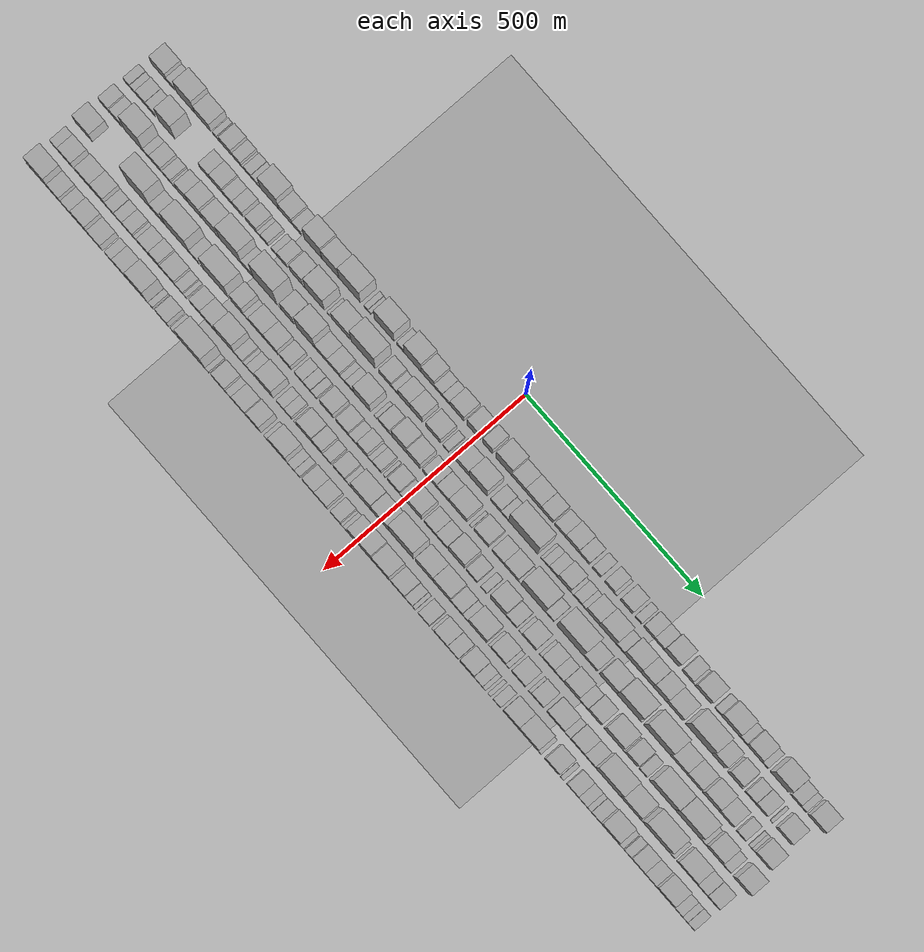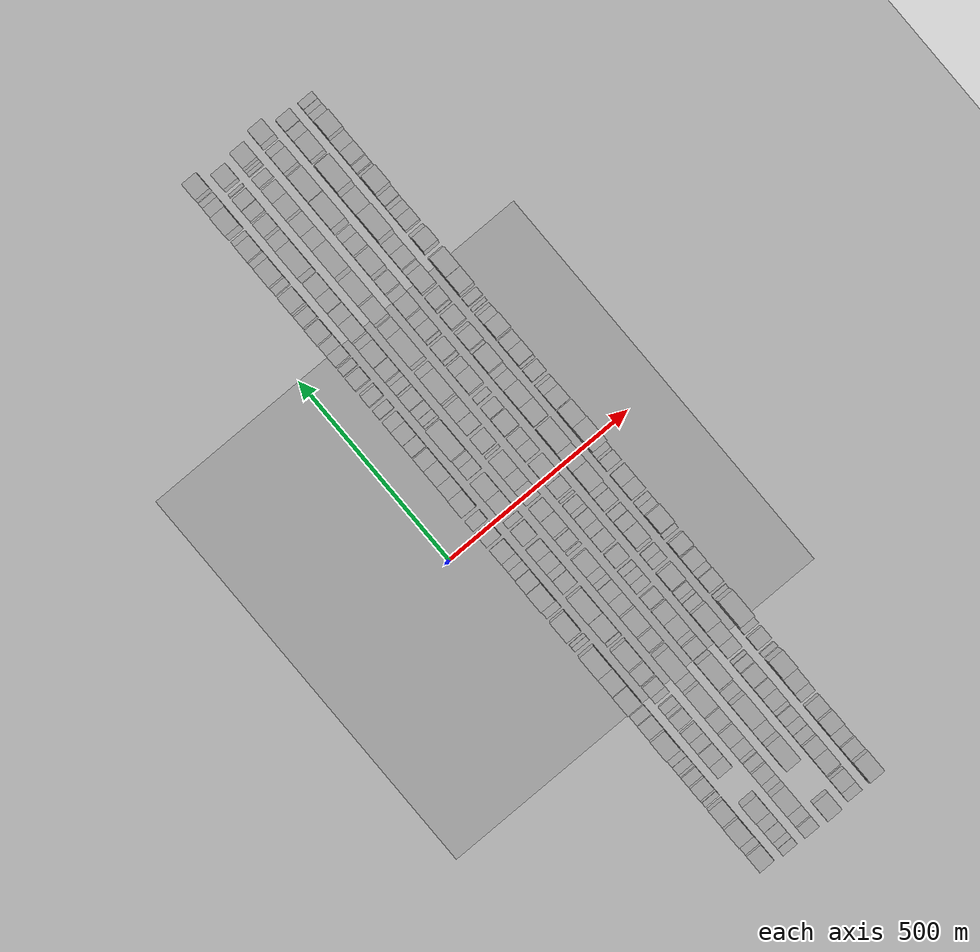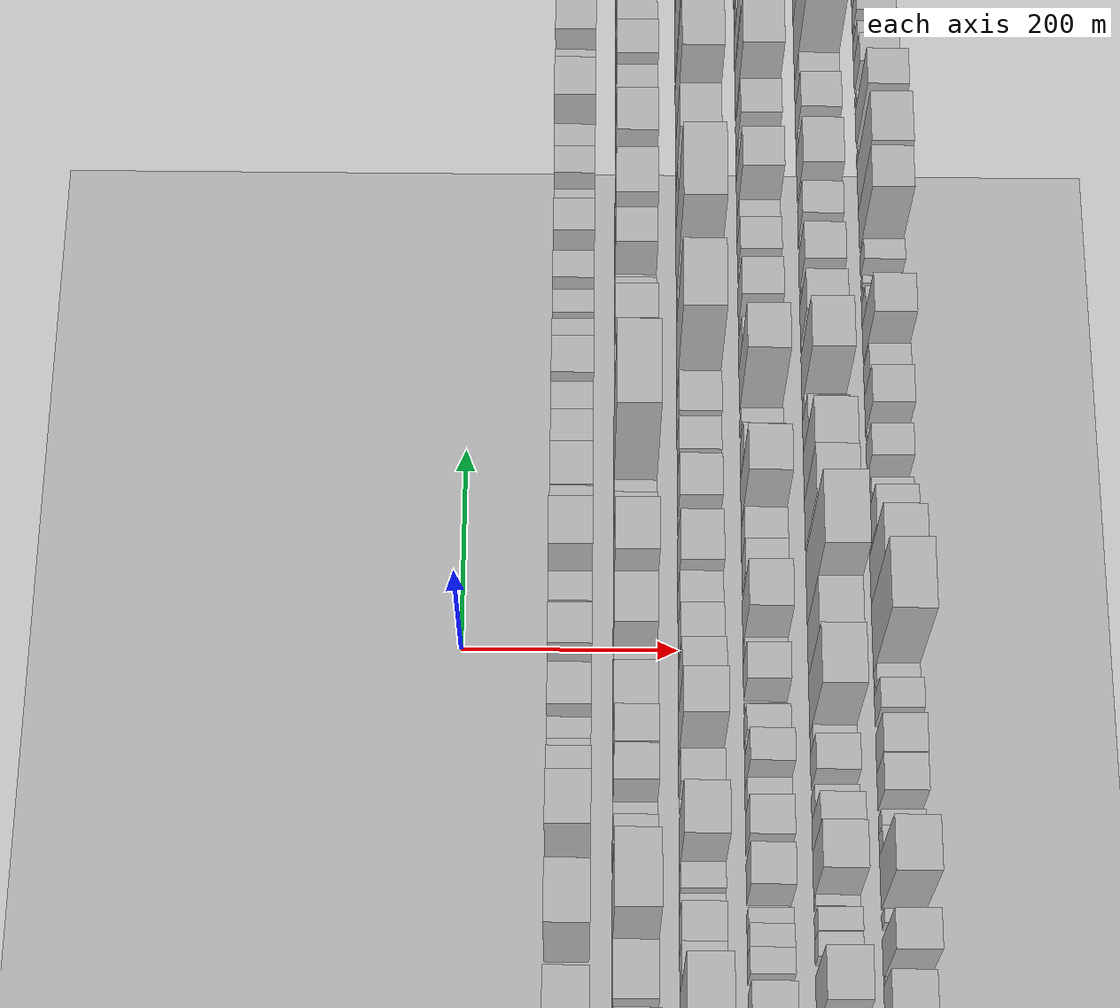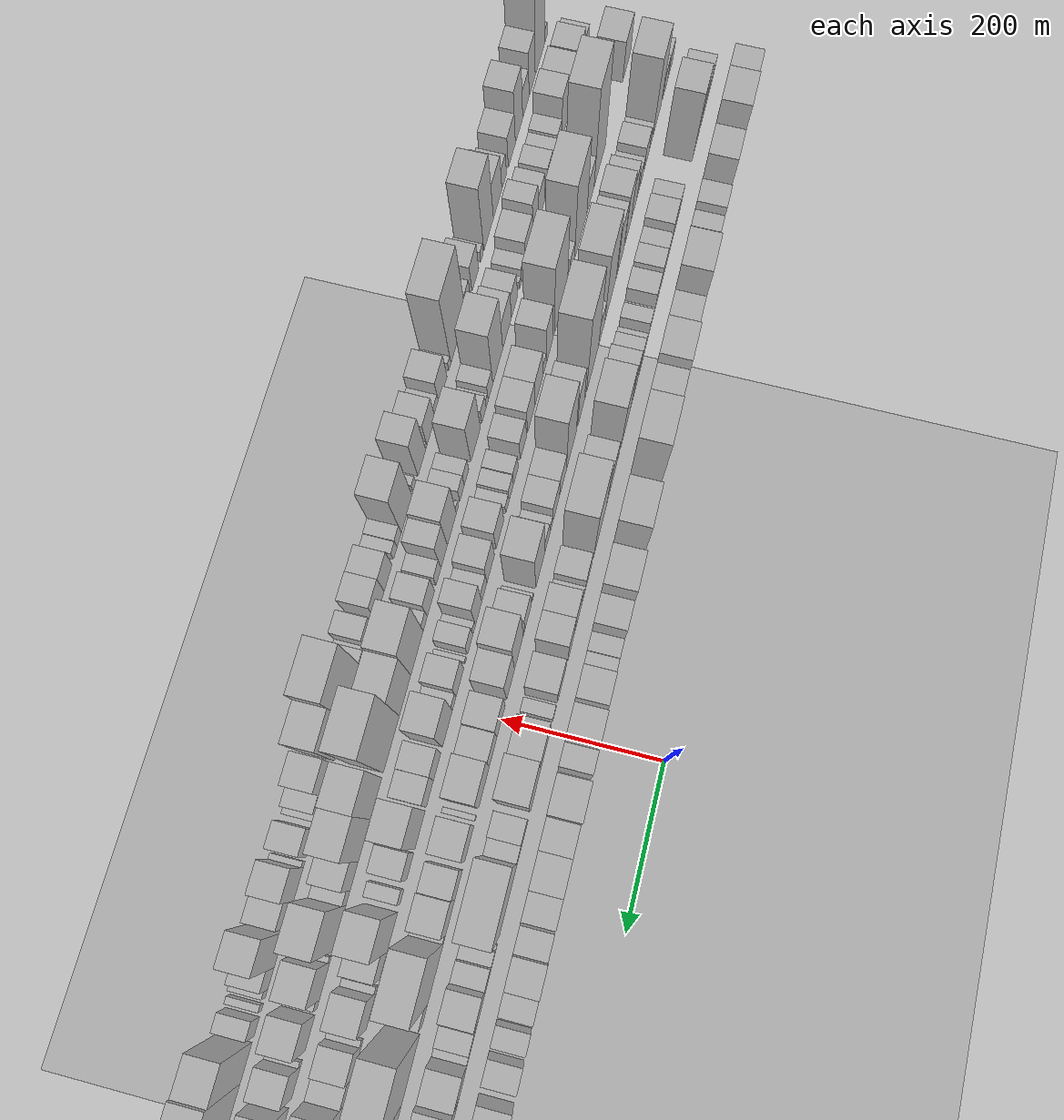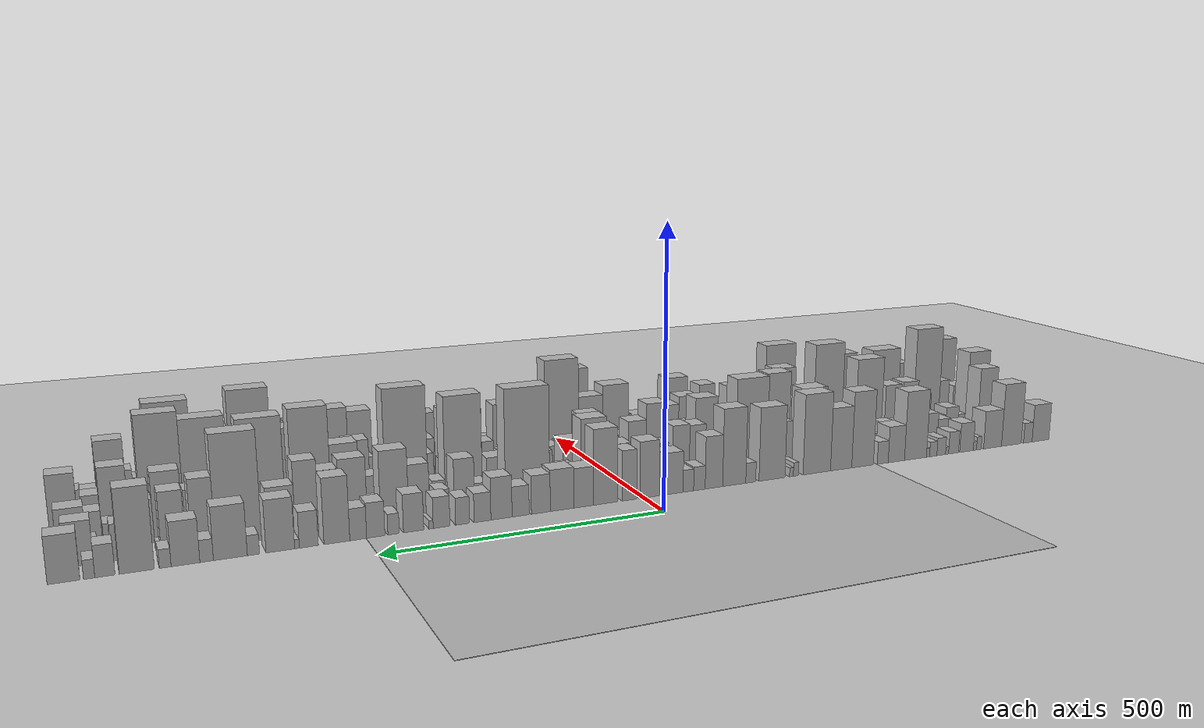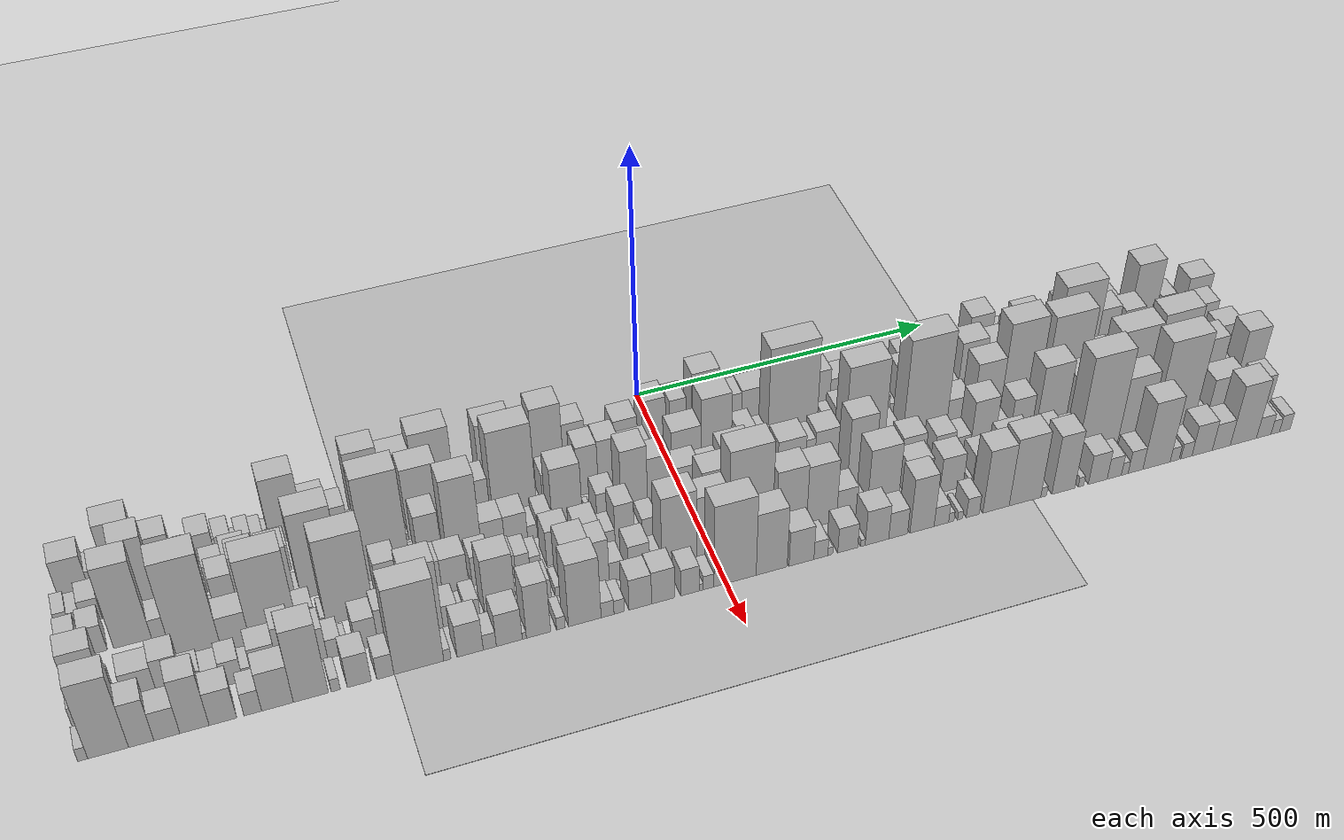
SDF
<?xml version="1.0" encoding="utf-8"?>

<sdf version="1.6">

   <world name="default">

      <gui fullscreen="0">

         <camera name="user_camera">

            <pose>-15 0 4.57585 0 0 0</pose>

            <view_controller>orbit</view_controller>

         </camera>

      </gui>

      <scene>

         <sky>

           <clouds>

             <speed>12</speed>

           </clouds>

         </sky>

         <ambient>0.4 0.4 0.4 1</ambient>

         <background>0.7 0.7 0.7 1</background>

         <shadows>1</shadows>

      </scene>

      <gravity>0 0 -9.8066</gravity>

      <magnetic_field>6e-06 2.3e-05 -4.2e-05</magnetic_field>

      <physics default="0" name="default_physics" type="ode">

         <ode>

            <solver>

               <type>quick</type>

               <iters>10</iters>

               <sor>1.0</sor>

               <use_dynamic_moi_rescaling>0</use_dynamic_moi_rescaling>

            </solver>

            <constraints>

               <cfm>0</cfm>

               <erp>0.2</erp>

               <contact_max_correcting_vel>100</contact_max_correcting_vel>

               <contact_surface_layer>0.001</contact_surface_layer>

            </constraints>

         </ode>

         <max_step_size>0.004</max_step_size>

         <real_time_factor>1</real_time_factor>

         <real_time_update_rate>250</real_time_update_rate>

      </physics>

      <light name="sun" type="directional">

         <cast_shadows>1</cast_shadows>

         <pose>0 0 10 0 0 0</pose>

         <diffuse>0.8 0.8 0.8 1</diffuse>

         <specular>0.2 0.2 0.2 1</specular>

         <attenuation>

            <range>1000</range>

            <constant>0.9</constant>

            <linear>0.01</linear>

            <quadratic>0.001</quadratic>

         </attenuation>

         <direction>-0.5 0.1 -0.9</direction>

      </light>

      <include>

         <name>ground_plane_1</name>

         <uri>model://HANNAS_ground_plane</uri>

         <pose>0 0 0  0 0 0</pose>

      </include>

      <include>

         <name>ground_plane_2</name>

         <uri>model://HANNAS_ground_plane</uri>

         <pose>100 0 0  0 0 0</pose>

      </include>

      <model name="building_1">

         <static>1</static>

         <pose frame="">100.0000 -908.6700 0 0.000000 0.000000 0.000000</pose>

         <link name="link">

            <pose frame="">0 0 39.00 0 0 0</pose>

            <collision name="collision">

               <geometry>

                  <box>

                     <size>40.0000 44.6600 78.0000</size>

                  </box>

               </geometry>

               <max_contacts>10</max_contacts>

               <surface>

                  <contact>

                     <ode/>

                  </contact>

                  <bounce/>

                  <friction>

                     <torsional>

                        <ode/>

                     </torsional>

                     <ode/>

                  </friction>

               </surface>

            </collision>

            <visual name="visual">

               <cast_shadows>0</cast_shadows>

               <geometry>

                  <box>

                     <size>40.0000 44.6600 78.0000</size>

                  </box>

               </geometry>

               <material>

                  <script>

                     <uri>model://HANNAS_wall/materials/scripts</uri>

                     <uri>model://HANNAS_wall/materials/textures</uri>

                     <name>vrc/HANNAS_wall</name>

                  </script>

               </material>

            </visual>

            <self_collide>0</self_collide>

            <enable_wind>0</enable_wind>

            <kinematic>0</kinematic>

         </link>

      </model>

      <model name="building_2">

         <static>1</static>

         <pose frame="">100.0000 -875.1208 0 0.000000 0.000000 0.000000</pose>

         <link name="link">

            <pose frame="">0 0 21.00 0 0 0</pose>

            <collision name="collision">

               <geometry>

                  <box>

                     <size>40.0000 22.4383 42.0000</size>

                  </box>

               </geometry>

               <max_contacts>10</max_contacts>

               <surface>

                  <contact>

                     <ode/>

                  </contact>

                  <bounce/>

                  <friction>

                     <torsional>

                        <ode/>

                     </torsional>

                     <ode/>

                  </friction>

               </surface>

            </collision>

            <visual name="visual">

               <cast_shadows>0</cast_shadows>

               <geometry>

                  <box>

                     <size>40.0000 22.4383 42.0000</size>

                  </box>

               </geometry>

               <material>

                  <script>

                     <uri>model://HANNAS_wall/materials/scripts</uri>

                     <uri>model://HANNAS_wall/materials/textures</uri>

                     <name>vrc/HANNAS_wall</name>

                  </script>

               </material>

            </visual>

            <self_collide>0</self_collide>

            <enable_wind>0</enable_wind>

            <kinematic>0</kinematic>

         </link>

      </model>

      <model name="building_3">

         <static>1</static>

         <pose frame="">100.0000 -832.2867 0 0.000000 0.000000 0.000000</pose>

         <link name="link">

            <pose frame="">0 0 64.50 0 0 0</pose>

            <collision name="collision">

               <geometry>

                  <box>

                     <size>40.0000 51.2298 129.0000</size>

                  </box>

               </geometry>

               <max_contacts>10</max_contacts>

               <surface>

                  <contact>

                     <ode/>

                  </contact>

                  <bounce/>

                  <friction>

                     <torsional>

                        <ode/>

                     </torsional>

                     <ode/>

                  </friction>

               </surface>

            </collision>

            <visual name="visual">

               <cast_shadows>0</cast_shadows>

               <geometry>

                  <box>

                     <size>40.0000 51.2298 129.0000</size>

                  </box>

               </geometry>

               <material>

                  <script>

                     <uri>model://HANNAS_wall/materials/scripts</uri>

                     <uri>model://HANNAS_wall/materials/textures</uri>

                     <name>vrc/HANNAS_wall</name>

                  </script>

               </material>

            </visual>

            <self_collide>0</self_collide>

            <enable_wind>0</enable_wind>

            <kinematic>0</kinematic>

         </link>

      </model>

      <model name="building_4">

         <static>1</static>

         <pose frame="">100.0000 -783.7471 0 0.000000 0.000000 0.000000</pose>

         <link name="link">

            <pose frame="">0 0 39.00 0 0 0</pose>

            <collision name="collision">

               <geometry>

                  <box>

                     <size>40.0000 45.8494 78.0000</size>

                  </box>

               </geometry>

               <max_contacts>10</max_contacts>

               <surface>

                  <contact>

                     <ode/>

                  </contact>

                  <bounce/>

                  <friction>

                     <torsional>

                        <ode/>

                     </torsional>

                     <ode/>

                  </friction>

               </surface>

            </collision>

            <visual name="visual">

               <cast_shadows>0</cast_shadows>

               <geometry>

                  <box>

                     <size>40.0000 45.8494 78.0000</size>

                  </box>

               </geometry>

               <material>

                  <script>

                     <uri>model://HANNAS_wall/materials/scripts</uri>

                     <uri>model://HANNAS_wall/materials/textures</uri>

                     <name>vrc/HANNAS_wall</name>

                  </script>

               </material>

            </visual>

            <self_collide>0</self_collide>

            <enable_wind>0</enable_wind>

            <kinematic>0</kinematic>

         </link>

      </model>

      <model name="building_5">

         <static>1</static>

         <pose frame="">100.0000 -748.8958 0 0.000000 0.000000 0.000000</pose>

         <link name="link">

            <pose frame="">0 0 13.50 0 0 0</pose>

            <collision name="collision">

               <geometry>

                  <box>

                     <size>40.0000 11.8532 27.0000</size>

                  </box>

               </geometry>

               <max_contacts>10</max_contacts>

               <surface>

                  <contact>

                     <ode/>

                  </contact>

                  <bounce/>

                  <friction>

                     <torsional>

                        <ode/>

                     </torsional>

                     <ode/>

                  </friction>

               </surface>

            </collision>

            <visual name="visual">

               <cast_shadows>0</cast_shadows>

               <geometry>

                  <box>

                     <size>40.0000 11.8532 27.0000</size>

                  </box>

               </geometry>

               <material>

                  <script>

                     <uri>model://HANNAS_wall/materials/scripts</uri>

                     <uri>model://HANNAS_wall/materials/textures</uri>

                     <name>vrc/HANNAS_wall</name>

                  </script>

               </material>

            </visual>

            <self_collide>0</self_collide>

            <enable_wind>0</enable_wind>

            <kinematic>0</kinematic>

         </link>

      </model>

      <model name="building_6">

         <static>1</static>

         <pose frame="">100.0000 -738.8473 0 0.000000 0.000000 0.000000</pose>

         <link name="link">

            <pose frame="">0 0 9.00 0 0 0</pose>

            <collision name="collision">

               <geometry>

                  <box>

                     <size>40.0000 8.2439 18.0000</size>

                  </box>

               </geometry>

               <max_contacts>10</max_contacts>

               <surface>

                  <contact>

                     <ode/>

                  </contact>

                  <bounce/>

                  <friction>

                     <torsional>

                        <ode/>

                     </torsional>

                     <ode/>

                  </friction>

               </surface>

            </collision>

            <visual name="visual">

               <cast_shadows>0</cast_shadows>

               <geometry>

                  <box>

                     <size>40.0000 8.2439 18.0000</size>

                  </box>

               </geometry>

               <material>

                  <script>

                     <uri>model://HANNAS_wall/materials/scripts</uri>

                     <uri>model://HANNAS_wall/materials/textures</uri>

                     <name>vrc/HANNAS_wall</name>

                  </script>

               </material>

            </visual>

            <self_collide>0</self_collide>

            <enable_wind>0</enable_wind>

            <kinematic>0</kinematic>

         </link>

      </model>

      <model name="building_7">

         <static>1</static>

         <pose frame="">100.0000 -717.7054 0 0.000000 0.000000 0.000000</pose>

         <link name="link">

            <pose frame="">0 0 30.00 0 0 0</pose>

            <collision name="collision">

               <geometry>

                  <box>

                     <size>40.0000 34.0398 60.0000</size>

                  </box>

               </geometry>

               <max_contacts>10</max_contacts>

               <surface>

                  <contact>

                     <ode/>

                  </contact>

                  <bounce/>

                  <friction>

                     <torsional>

                        <ode/>

                     </torsional>

                     <ode/>

                  </friction>

               </surface>

            </collision>

            <visual name="visual">

               <cast_shadows>0</cast_shadows>

               <geometry>

                  <box>

                     <size>40.0000 34.0398 60.0000</size>

                  </box>

               </geometry>

               <material>

                  <script>

                     <uri>model://HANNAS_wall/materials/scripts</uri>

                     <uri>model://HANNAS_wall/materials/textures</uri>

                     <name>vrc/HANNAS_wall</name>

                  </script>

               </material>

            </visual>

            <self_collide>0</self_collide>

            <enable_wind>0</enable_wind>

            <kinematic>0</kinematic>

         </link>

      </model>

      <model name="building_8">

         <static>1</static>

         <pose frame="">100.0000 -685.4181 0 0.000000 0.000000 0.000000</pose>

         <link name="link">

            <pose frame="">0 0 22.50 0 0 0</pose>

            <collision name="collision">

               <geometry>

                  <box>

                     <size>40.0000 24.5348 45.0000</size>

                  </box>

               </geometry>

               <max_contacts>10</max_contacts>

               <surface>

                  <contact>

                     <ode/>

                  </contact>

                  <bounce/>

                  <friction>

                     <torsional>

                        <ode/>

                     </torsional>

                     <ode/>

                  </friction>

               </surface>

            </collision>

            <visual name="visual">

               <cast_shadows>0</cast_shadows>

               <geometry>

                  <box>

                     <size>40.0000 24.5348 45.0000</size>

                  </box>

               </geometry>

               <material>

                  <script>

                     <uri>model://HANNAS_wall/materials/scripts</uri>

                     <uri>model://HANNAS_wall/materials/textures</uri>

                     <name>vrc/HANNAS_wall</name>

                  </script>

               </material>

            </visual>

            <self_collide>0</self_collide>

            <enable_wind>0</enable_wind>

            <kinematic>0</kinematic>

         </link>

      </model>

      <model name="building_9">

         <static>1</static>

         <pose frame="">100.0000 -669.4038 0 0.000000 0.000000 0.000000</pose>

         <link name="link">

            <pose frame="">0 0 7.50 0 0 0</pose>

            <collision name="collision">

               <geometry>

                  <box>

                     <size>40.0000 7.4939 15.0000</size>

                  </box>

               </geometry>

               <max_contacts>10</max_contacts>

               <surface>

                  <contact>

                     <ode/>

                  </contact>

                  <bounce/>

                  <friction>

                     <torsional>

                        <ode/>

                     </torsional>

                     <ode/>

                  </friction>

               </surface>

            </collision>

            <visual name="visual">

               <cast_shadows>0</cast_shadows>

               <geometry>

                  <box>

                     <size>40.0000 7.4939 15.0000</size>

                  </box>

               </geometry>

               <material>

                  <script>

                     <uri>model://HANNAS_wall/materials/scripts</uri>

                     <uri>model://HANNAS_wall/materials/textures</uri>

                     <name>vrc/HANNAS_wall</name>

                  </script>

               </material>

            </visual>

            <self_collide>0</self_collide>

            <enable_wind>0</enable_wind>

            <kinematic>0</kinematic>

         </link>

      </model>

      <model name="building_10">

         <static>1</static>

         <pose frame="">100.0000 -654.9815 0 0.000000 0.000000 0.000000</pose>

         <link name="link">

            <pose frame="">0 0 18.00 0 0 0</pose>

            <collision name="collision">

               <geometry>

                  <box>

                     <size>40.0000 21.3506 36.0000</size>

                  </box>

               </geometry>

               <max_contacts>10</max_contacts>

               <surface>

                  <contact>

                     <ode/>

                  </contact>

                  <bounce/>

                  <friction>

                     <torsional>

                        <ode/>

                     </torsional>

                     <ode/>

                  </friction>

               </surface>

            </collision>

            <visual name="visual">

               <cast_shadows>0</cast_shadows>

               <geometry>

                  <box>

                     <size>40.0000 21.3506 36.0000</size>

                  </box>

               </geometry>

               <material>

                  <script>

                     <uri>model://HANNAS_wall/materials/scripts</uri>

                     <uri>model://HANNAS_wall/materials/textures</uri>

                     <name>vrc/HANNAS_wall</name>

                  </script>

               </material>

            </visual>

            <self_collide>0</self_collide>

            <enable_wind>0</enable_wind>

            <kinematic>0</kinematic>

         </link>

      </model>

      <model name="building_11">

         <static>1</static>

         <pose frame="">100.0000 -635.4280 0 0.000000 0.000000 0.000000</pose>

         <link name="link">

            <pose frame="">0 0 15.00 0 0 0</pose>

            <collision name="collision">

               <geometry>

                  <box>

                     <size>40.0000 17.7566 30.0000</size>

                  </box>

               </geometry>

               <max_contacts>10</max_contacts>

               <surface>

                  <contact>

                     <ode/>

                  </contact>

                  <bounce/>

                  <friction>

                     <torsional>

                        <ode/>

                     </torsional>

                     <ode/>

                  </friction>

               </surface>

            </collision>

            <visual name="visual">

               <cast_shadows>0</cast_shadows>

               <geometry>

                  <box>

                     <size>40.0000 17.7566 30.0000</size>

                  </box>

               </geometry>

               <material>

                  <script>

                     <uri>model://HANNAS_wall/materials/scripts</uri>

                     <uri>model://HANNAS_wall/materials/textures</uri>

                     <name>vrc/HANNAS_wall</name>

                  </script>

               </material>

            </visual>

            <self_collide>0</self_collide>

            <enable_wind>0</enable_wind>

            <kinematic>0</kinematic>

         </link>

      </model>

      <model name="building_12">

         <static>1</static>

         <pose frame="">100.0000 -622.7166 0 0.000000 0.000000 0.000000</pose>

         <link name="link">

            <pose frame="">0 0 9.00 0 0 0</pose>

            <collision name="collision">

               <geometry>

                  <box>

                     <size>40.0000 7.6661 18.0000</size>

                  </box>

               </geometry>

               <max_contacts>10</max_contacts>

               <surface>

                  <contact>

                     <ode/>

                  </contact>

                  <bounce/>

                  <friction>

                     <torsional>

                        <ode/>

                     </torsional>

                     <ode/>

                  </friction>

               </surface>

            </collision>

            <visual name="visual">

               <cast_shadows>0</cast_shadows>

               <geometry>

                  <box>

                     <size>40.0000 7.6661 18.0000</size>

                  </box>

               </geometry>

               <material>

                  <script>

                     <uri>model://HANNAS_wall/materials/scripts</uri>

                     <uri>model://HANNAS_wall/materials/textures</uri>

                     <name>vrc/HANNAS_wall</name>

                  </script>

               </material>

            </visual>

            <self_collide>0</self_collide>

            <enable_wind>0</enable_wind>

            <kinematic>0</kinematic>

         </link>

      </model>

      <model name="building_13">

         <static>1</static>

         <pose frame="">100.0000 -592.4137 0 0.000000 0.000000 0.000000</pose>

         <link name="link">

            <pose frame="">0 0 69.00 0 0 0</pose>

            <collision name="collision">

               <geometry>

                  <box>

                     <size>40.0000 52.9396 138.0000</size>

                  </box>

               </geometry>

               <max_contacts>10</max_contacts>

               <surface>

                  <contact>

                     <ode/>

                  </contact>

                  <bounce/>

                  <friction>

                     <torsional>

                        <ode/>

                     </torsional>

                     <ode/>

                  </friction>

               </surface>

            </collision>

            <visual name="visual">

               <cast_shadows>0</cast_shadows>

               <geometry>

                  <box>

                     <size>40.0000 52.9396 138.0000</size>

                  </box>

               </geometry>

               <material>

                  <script>

                     <uri>model://HANNAS_wall/materials/scripts</uri>

                     <uri>model://HANNAS_wall/materials/textures</uri>

                     <name>vrc/HANNAS_wall</name>

                  </script>

               </material>

            </visual>

            <self_collide>0</self_collide>

            <enable_wind>0</enable_wind>

            <kinematic>0</kinematic>

         </link>

      </model>

      <model name="building_14">

         <static>1</static>

         <pose frame="">100.0000 -546.5799 0 0.000000 0.000000 0.000000</pose>

         <link name="link">

            <pose frame="">0 0 36.00 0 0 0</pose>

            <collision name="collision">

               <geometry>

                  <box>

                     <size>40.0000 38.7281 72.0000</size>

                  </box>

               </geometry>

               <max_contacts>10</max_contacts>

               <surface>

                  <contact>

                     <ode/>

                  </contact>

                  <bounce/>

                  <friction>

                     <torsional>

                        <ode/>

                     </torsional>

                     <ode/>

                  </friction>

               </surface>

            </collision>

            <visual name="visual">

               <cast_shadows>0</cast_shadows>

               <geometry>

                  <box>

                     <size>40.0000 38.7281 72.0000</size>

                  </box>

               </geometry>

               <material>

                  <script>

                     <uri>model://HANNAS_wall/materials/scripts</uri>

                     <uri>model://HANNAS_wall/materials/textures</uri>

                     <name>vrc/HANNAS_wall</name>

                  </script>

               </material>

            </visual>

            <self_collide>0</self_collide>

            <enable_wind>0</enable_wind>

            <kinematic>0</kinematic>

         </link>

      </model>

      <model name="building_15">

         <static>1</static>

         <pose frame="">100.0000 -514.3881 0 0.000000 0.000000 0.000000</pose>

         <link name="link">

            <pose frame="">0 0 22.50 0 0 0</pose>

            <collision name="collision">

               <geometry>

                  <box>

                     <size>40.0000 25.6554 45.0000</size>

                  </box>

               </geometry>

               <max_contacts>10</max_contacts>

               <surface>

                  <contact>

                     <ode/>

                  </contact>

                  <bounce/>

                  <friction>

                     <torsional>

                        <ode/>

                     </torsional>

                     <ode/>

                  </friction>

               </surface>

            </collision>

            <visual name="visual">

               <cast_shadows>0</cast_shadows>

               <geometry>

                  <box>

                     <size>40.0000 25.6554 45.0000</size>

                  </box>

               </geometry>

               <material>

                  <script>

                     <uri>model://HANNAS_wall/materials/scripts</uri>

                     <uri>model://HANNAS_wall/materials/textures</uri>

                     <name>vrc/HANNAS_wall</name>

                  </script>

               </material>

            </visual>

            <self_collide>0</self_collide>

            <enable_wind>0</enable_wind>

            <kinematic>0</kinematic>

         </link>

      </model>

      <model name="building_16">

         <static>1</static>

         <pose frame="">100.0000 -467.4501 0 0.000000 0.000000 0.000000</pose>

         <link name="link">

            <pose frame="">0 0 75.00 0 0 0</pose>

            <collision name="collision">

               <geometry>

                  <box>

                     <size>40.0000 50.2205 150.0000</size>

                  </box>

               </geometry>

               <max_contacts>10</max_contacts>

               <surface>

                  <contact>

                     <ode/>

                  </contact>

                  <bounce/>

                  <friction>

                     <torsional>

                        <ode/>

                     </torsional>

                     <ode/>

                  </friction>

               </surface>

            </collision>

            <visual name="visual">

               <cast_shadows>0</cast_shadows>

               <geometry>

                  <box>

                     <size>40.0000 50.2205 150.0000</size>

                  </box>

               </geometry>

               <material>

                  <script>

                     <uri>model://HANNAS_wall/materials/scripts</uri>

                     <uri>model://HANNAS_wall/materials/textures</uri>

                     <name>vrc/HANNAS_wall</name>

                  </script>

               </material>

            </visual>

            <self_collide>0</self_collide>

            <enable_wind>0</enable_wind>

            <kinematic>0</kinematic>

         </link>

      </model>

      <model name="building_17">

         <static>1</static>

         <pose frame="">100.0000 -418.1977 0 0.000000 0.000000 0.000000</pose>

         <link name="link">

            <pose frame="">0 0 61.50 0 0 0</pose>

            <collision name="collision">

               <geometry>

                  <box>

                     <size>40.0000 48.2844 123.0000</size>

                  </box>

               </geometry>

               <max_contacts>10</max_contacts>

               <surface>

                  <contact>

                     <ode/>

                  </contact>

                  <bounce/>

                  <friction>

                     <torsional>

                        <ode/>

                     </torsional>

                     <ode/>

                  </friction>

               </surface>

            </collision>

            <visual name="visual">

               <cast_shadows>0</cast_shadows>

               <geometry>

                  <box>

                     <size>40.0000 48.2844 123.0000</size>

                  </box>

               </geometry>

               <material>

                  <script>

                     <uri>model://HANNAS_wall/materials/scripts</uri>

                     <uri>model://HANNAS_wall/materials/textures</uri>

                     <name>vrc/HANNAS_wall</name>

                  </script>

               </material>

            </visual>

            <self_collide>0</self_collide>

            <enable_wind>0</enable_wind>

            <kinematic>0</kinematic>

         </link>

      </model>

      <model name="building_18">

         <static>1</static>

         <pose frame="">100.0000 -363.4000 0 0.000000 0.000000 0.000000</pose>

         <link name="link">

            <pose frame="">0 0 78.00 0 0 0</pose>

            <collision name="collision">

               <geometry>

                  <box>

                     <size>40.0000 61.3111 156.0000</size>

                  </box>

               </geometry>

               <max_contacts>10</max_contacts>

               <surface>

                  <contact>

                     <ode/>

                  </contact>

                  <bounce/>

                  <friction>

                     <torsional>

                        <ode/>

                     </torsional>

                     <ode/>

                  </friction>

               </surface>

            </collision>

            <visual name="visual">

               <cast_shadows>0</cast_shadows>

               <geometry>

                  <box>

                     <size>40.0000 61.3111 156.0000</size>

                  </box>

               </geometry>

               <material>

                  <script>

                     <uri>model://HANNAS_wall/materials/scripts</uri>

                     <uri>model://HANNAS_wall/materials/textures</uri>

                     <name>vrc/HANNAS_wall</name>

                  </script>

               </material>

            </visual>

            <self_collide>0</self_collide>

            <enable_wind>0</enable_wind>

            <kinematic>0</kinematic>

         </link>

      </model>

      <model name="building_19">

         <static>1</static>

         <pose frame="">100.0000 -317.0317 0 0.000000 0.000000 0.000000</pose>

         <link name="link">

            <pose frame="">0 0 13.50 0 0 0</pose>

            <collision name="collision">

               <geometry>

                  <box>

                     <size>40.0000 11.4255 27.0000</size>

                  </box>

               </geometry>

               <max_contacts>10</max_contacts>

               <surface>

                  <contact>

                     <ode/>

                  </contact>

                  <bounce/>

                  <friction>

                     <torsional>

                        <ode/>

                     </torsional>

                     <ode/>

                  </friction>

               </surface>

            </collision>

            <visual name="visual">

               <cast_shadows>0</cast_shadows>

               <geometry>

                  <box>

                     <size>40.0000 11.4255 27.0000</size>

                  </box>

               </geometry>

               <material>

                  <script>

                     <uri>model://HANNAS_wall/materials/scripts</uri>

                     <uri>model://HANNAS_wall/materials/textures</uri>

                     <name>vrc/HANNAS_wall</name>

                  </script>

               </material>

            </visual>

            <self_collide>0</self_collide>

            <enable_wind>0</enable_wind>

            <kinematic>0</kinematic>

         </link>

      </model>

      <model name="building_20">

         <static>1</static>

         <pose frame="">100.0000 -307.1301 0 0.000000 0.000000 0.000000</pose>

         <link name="link">

            <pose frame="">0 0 9.00 0 0 0</pose>

            <collision name="collision">

               <geometry>

                  <box>

                     <size>40.0000 8.3779 18.0000</size>

                  </box>

               </geometry>

               <max_contacts>10</max_contacts>

               <surface>

                  <contact>

                     <ode/>

                  </contact>

                  <bounce/>

                  <friction>

                     <torsional>

                        <ode/>

                     </torsional>

                     <ode/>

                  </friction>

               </surface>

            </collision>

            <visual name="visual">

               <cast_shadows>0</cast_shadows>

               <geometry>

                  <box>

                     <size>40.0000 8.3779 18.0000</size>

                  </box>

               </geometry>

               <material>

                  <script>

                     <uri>model://HANNAS_wall/materials/scripts</uri>

                     <uri>model://HANNAS_wall/materials/textures</uri>

                     <name>vrc/HANNAS_wall</name>

                  </script>

               </material>

            </visual>

            <self_collide>0</self_collide>

            <enable_wind>0</enable_wind>

            <kinematic>0</kinematic>

         </link>

      </model>

      <model name="building_21">

         <static>1</static>

         <pose frame="">100.0000 -264.8392 0 0.000000 0.000000 0.000000</pose>

         <link name="link">

            <pose frame="">0 0 70.50 0 0 0</pose>

            <collision name="collision">

               <geometry>

                  <box>

                     <size>40.0000 56.2038 141.0000</size>

                  </box>

               </geometry>

               <max_contacts>10</max_contacts>

               <surface>

                  <contact>

                     <ode/>

                  </contact>

                  <bounce/>

                  <friction>

                     <torsional>

                        <ode/>

                     </torsional>

                     <ode/>

                  </friction>

               </surface>

            </collision>

            <visual name="visual">

               <cast_shadows>0</cast_shadows>

               <geometry>

                  <box>

                     <size>40.0000 56.2038 141.0000</size>

                  </box>

               </geometry>

               <material>

                  <script>

                     <uri>model://HANNAS_wall/materials/scripts</uri>

                     <uri>model://HANNAS_wall/materials/textures</uri>

                     <name>vrc/HANNAS_wall</name>

                  </script>

               </material>

            </visual>

            <self_collide>0</self_collide>

            <enable_wind>0</enable_wind>

            <kinematic>0</kinematic>

         </link>

      </model>

      <model name="building_22">

         <static>1</static>

         <pose frame="">100.0000 -219.1649 0 0.000000 0.000000 0.000000</pose>

         <link name="link">

            <pose frame="">0 0 19.50 0 0 0</pose>

            <collision name="collision">

               <geometry>

                  <box>

                     <size>40.0000 21.1448 39.0000</size>

                  </box>

               </geometry>

               <max_contacts>10</max_contacts>

               <surface>

                  <contact>

                     <ode/>

                  </contact>

                  <bounce/>

                  <friction>

                     <torsional>

                        <ode/>

                     </torsional>

                     <ode/>

                  </friction>

               </surface>

            </collision>

            <visual name="visual">

               <cast_shadows>0</cast_shadows>

               <geometry>

                  <box>

                     <size>40.0000 21.1448 39.0000</size>

                  </box>

               </geometry>

               <material>

                  <script>

                     <uri>model://HANNAS_wall/materials/scripts</uri>

                     <uri>model://HANNAS_wall/materials/textures</uri>

                     <name>vrc/HANNAS_wall</name>

                  </script>

               </material>

            </visual>

            <self_collide>0</self_collide>

            <enable_wind>0</enable_wind>

            <kinematic>0</kinematic>

         </link>

      </model>

      <model name="building_23">

         <static>1</static>

         <pose frame="">100.0000 -184.2398 0 0.000000 0.000000 0.000000</pose>

         <link name="link">

            <pose frame="">0 0 73.50 0 0 0</pose>

            <collision name="collision">

               <geometry>

                  <box>

                     <size>40.0000 48.7054 147.0000</size>

                  </box>

               </geometry>

               <max_contacts>10</max_contacts>

               <surface>

                  <contact>

                     <ode/>

                  </contact>

                  <bounce/>

                  <friction>

                     <torsional>

                        <ode/>

                     </torsional>

                     <ode/>

                  </friction>

               </surface>

            </collision>

            <visual name="visual">

               <cast_shadows>0</cast_shadows>

               <geometry>

                  <box>

                     <size>40.0000 48.7054 147.0000</size>

                  </box>

               </geometry>

               <material>

                  <script>

                     <uri>model://HANNAS_wall/materials/scripts</uri>

                     <uri>model://HANNAS_wall/materials/textures</uri>

                     <name>vrc/HANNAS_wall</name>

                  </script>

               </material>

            </visual>

            <self_collide>0</self_collide>

            <enable_wind>0</enable_wind>

            <kinematic>0</kinematic>

         </link>

      </model>

      <model name="building_24">

         <static>1</static>

         <pose frame="">100.0000 -141.7538 0 0.000000 0.000000 0.000000</pose>

         <link name="link">

            <pose frame="">0 0 49.50 0 0 0</pose>

            <collision name="collision">

               <geometry>

                  <box>

                     <size>40.0000 36.2667 99.0000</size>

                  </box>

               </geometry>

               <max_contacts>10</max_contacts>

               <surface>

                  <contact>

                     <ode/>

                  </contact>

                  <bounce/>

                  <friction>

                     <torsional>

                        <ode/>

                     </torsional>

                     <ode/>

                  </friction>

               </surface>

            </collision>

            <visual name="visual">

               <cast_shadows>0</cast_shadows>

               <geometry>

                  <box>

                     <size>40.0000 36.2667 99.0000</size>

                  </box>

               </geometry>

               <material>

                  <script>

                     <uri>model://HANNAS_wall/materials/scripts</uri>

                     <uri>model://HANNAS_wall/materials/textures</uri>

                     <name>vrc/HANNAS_wall</name>

                  </script>

               </material>

            </visual>

            <self_collide>0</self_collide>

            <enable_wind>0</enable_wind>

            <kinematic>0</kinematic>

         </link>

      </model>

      <model name="building_25">

         <static>1</static>

         <pose frame="">100.0000 -111.7291 0 0.000000 0.000000 0.000000</pose>

         <link name="link">

            <pose frame="">0 0 22.50 0 0 0</pose>

            <collision name="collision">

               <geometry>

                  <box>

                     <size>40.0000 23.7827 45.0000</size>

                  </box>

               </geometry>

               <max_contacts>10</max_contacts>

               <surface>

                  <contact>

                     <ode/>

                  </contact>

                  <bounce/>

                  <friction>

                     <torsional>

                        <ode/>

                     </torsional>

                     <ode/>

                  </friction>

               </surface>

            </collision>

            <visual name="visual">

               <cast_shadows>0</cast_shadows>

               <geometry>

                  <box>

                     <size>40.0000 23.7827 45.0000</size>

                  </box>

               </geometry>

               <material>

                  <script>

                     <uri>model://HANNAS_wall/materials/scripts</uri>

                     <uri>model://HANNAS_wall/materials/textures</uri>

                     <name>vrc/HANNAS_wall</name>

                  </script>

               </material>

            </visual>

            <self_collide>0</self_collide>

            <enable_wind>0</enable_wind>

            <kinematic>0</kinematic>

         </link>

      </model>

      <model name="building_26">

         <static>1</static>

         <pose frame="">100.0000 -89.1588 0 0.000000 0.000000 0.000000</pose>

         <link name="link">

            <pose frame="">0 0 21.00 0 0 0</pose>

            <collision name="collision">

               <geometry>

                  <box>

                     <size>40.0000 21.3579 42.0000</size>

                  </box>

               </geometry>

               <max_contacts>10</max_contacts>

               <surface>

                  <contact>

                     <ode/>

                  </contact>

                  <bounce/>

                  <friction>

                     <torsional>

                        <ode/>

                     </torsional>

                     <ode/>

                  </friction>

               </surface>

            </collision>

            <visual name="visual">

               <cast_shadows>0</cast_shadows>

               <geometry>

                  <box>

                     <size>40.0000 21.3579 42.0000</size>

                  </box>

               </geometry>

               <material>

                  <script>

                     <uri>model://HANNAS_wall/materials/scripts</uri>

                     <uri>model://HANNAS_wall/materials/textures</uri>

                     <name>vrc/HANNAS_wall</name>

                  </script>

               </material>

            </visual>

            <self_collide>0</self_collide>

            <enable_wind>0</enable_wind>

            <kinematic>0</kinematic>

         </link>

      </model>

      <model name="building_27">

         <static>1</static>

         <pose frame="">100.0000 -58.5543 0 0.000000 0.000000 0.000000</pose>

         <link name="link">

            <pose frame="">0 0 39.00 0 0 0</pose>

            <collision name="collision">

               <geometry>

                  <box>

                     <size>40.0000 39.8511 78.0000</size>

                  </box>

               </geometry>

               <max_contacts>10</max_contacts>

               <surface>

                  <contact>

                     <ode/>

                  </contact>

                  <bounce/>

                  <friction>

                     <torsional>

                        <ode/>

                     </torsional>

                     <ode/>

                  </friction>

               </surface>

            </collision>

            <visual name="visual">

               <cast_shadows>0</cast_shadows>

               <geometry>

                  <box>

                     <size>40.0000 39.8511 78.0000</size>

                  </box>

               </geometry>

               <material>

                  <script>

                     <uri>model://HANNAS_wall/materials/scripts</uri>

                     <uri>model://HANNAS_wall/materials/textures</uri>

                     <name>vrc/HANNAS_wall</name>

                  </script>

               </material>

            </visual>

            <self_collide>0</self_collide>

            <enable_wind>0</enable_wind>

            <kinematic>0</kinematic>

         </link>

      </model>

      <model name="building_28">

         <static>1</static>

         <pose frame="">100.0000 -11.2332 0 0.000000 0.000000 0.000000</pose>

         <link name="link">

            <pose frame="">0 0 52.50 0 0 0</pose>

            <collision name="collision">

               <geometry>

                  <box>

                     <size>40.0000 38.7913 105.0000</size>

                  </box>

               </geometry>

               <max_contacts>10</max_contacts>

               <surface>

                  <contact>

                     <ode/>

                  </contact>

                  <bounce/>

                  <friction>

                     <torsional>

                        <ode/>

                     </torsional>

                     <ode/>

                  </friction>

               </surface>

            </collision>

            <visual name="visual">

               <cast_shadows>0</cast_shadows>

               <geometry>

                  <box>

                     <size>40.0000 38.7913 105.0000</size>

                  </box>

               </geometry>

               <material>

                  <script>

                     <uri>model://HANNAS_wall/materials/scripts</uri>

                     <uri>model://HANNAS_wall/materials/textures</uri>

                     <name>vrc/HANNAS_wall</name>

                  </script>

               </material>

            </visual>

            <self_collide>0</self_collide>

            <enable_wind>0</enable_wind>

            <kinematic>0</kinematic>

         </link>

      </model>

      <model name="building_29">

         <static>1</static>

         <pose frame="">100.0000 28.2649 0 0.000000 0.000000 0.000000</pose>

         <link name="link">

            <pose frame="">0 0 46.50 0 0 0</pose>

            <collision name="collision">

               <geometry>

                  <box>

                     <size>40.0000 28.2048 93.0000</size>

                  </box>

               </geometry>

               <max_contacts>10</max_contacts>

               <surface>

                  <contact>

                     <ode/>

                  </contact>

                  <bounce/>

                  <friction>

                     <torsional>

                        <ode/>

                     </torsional>

                     <ode/>

                  </friction>

               </surface>

            </collision>

            <visual name="visual">

               <cast_shadows>0</cast_shadows>

               <geometry>

                  <box>

                     <size>40.0000 28.2048 93.0000</size>

                  </box>

               </geometry>

               <material>

                  <script>

                     <uri>model://HANNAS_wall/materials/scripts</uri>

                     <uri>model://HANNAS_wall/materials/textures</uri>

                     <name>vrc/HANNAS_wall</name>

                  </script>

               </material>

            </visual>

            <self_collide>0</self_collide>

            <enable_wind>0</enable_wind>

            <kinematic>0</kinematic>

         </link>

      </model>

      <model name="building_30">

         <static>1</static>

         <pose frame="">100.0000 74.3533 0 0.000000 0.000000 0.000000</pose>

         <link name="link">

            <pose frame="">0 0 69.00 0 0 0</pose>

            <collision name="collision">

               <geometry>

                  <box>

                     <size>40.0000 45.9720 138.0000</size>

                  </box>

               </geometry>

               <max_contacts>10</max_contacts>

               <surface>

                  <contact>

                     <ode/>

                  </contact>

                  <bounce/>

                  <friction>

                     <torsional>

                        <ode/>

                     </torsional>

                     <ode/>

                  </friction>

               </surface>

            </collision>

            <visual name="visual">

               <cast_shadows>0</cast_shadows>

               <geometry>

                  <box>

                     <size>40.0000 45.9720 138.0000</size>

                  </box>

               </geometry>

               <material>

                  <script>

                     <uri>model://HANNAS_wall/materials/scripts</uri>

                     <uri>model://HANNAS_wall/materials/textures</uri>

                     <name>vrc/HANNAS_wall</name>

                  </script>

               </material>

            </visual>

            <self_collide>0</self_collide>

            <enable_wind>0</enable_wind>

            <kinematic>0</kinematic>

         </link>

      </model>

      <model name="building_31">

         <static>1</static>

         <pose frame="">100.0000 116.2808 0 0.000000 0.000000 0.000000</pose>

         <link name="link">

            <pose frame="">0 0 36.00 0 0 0</pose>

            <collision name="collision">

               <geometry>

                  <box>

                     <size>40.0000 37.8829 72.0000</size>

                  </box>

               </geometry>

               <max_contacts>10</max_contacts>

               <surface>

                  <contact>

                     <ode/>

                  </contact>

                  <bounce/>

                  <friction>

                     <torsional>

                        <ode/>

                     </torsional>

                     <ode/>

                  </friction>

               </surface>

            </collision>

            <visual name="visual">

               <cast_shadows>0</cast_shadows>

               <geometry>

                  <box>

                     <size>40.0000 37.8829 72.0000</size>

                  </box>

               </geometry>

               <material>

                  <script>

                     <uri>model://HANNAS_wall/materials/scripts</uri>

                     <uri>model://HANNAS_wall/materials/textures</uri>

                     <name>vrc/HANNAS_wall</name>

                  </script>

               </material>

            </visual>

            <self_collide>0</self_collide>

            <enable_wind>0</enable_wind>

            <kinematic>0</kinematic>

         </link>

      </model>

      <model name="building_32">

         <static>1</static>

         <pose frame="">100.0000 157.1084 0 0.000000 0.000000 0.000000</pose>

         <link name="link">

            <pose frame="">0 0 37.50 0 0 0</pose>

            <collision name="collision">

               <geometry>

                  <box>

                     <size>40.0000 43.7723 75.0000</size>

                  </box>

               </geometry>

               <max_contacts>10</max_contacts>

               <surface>

                  <contact>

                     <ode/>

                  </contact>

                  <bounce/>

                  <friction>

                     <torsional>

                        <ode/>

                     </torsional>

                     <ode/>

                  </friction>

               </surface>

            </collision>

            <visual name="visual">

               <cast_shadows>0</cast_shadows>

               <geometry>

                  <box>

                     <size>40.0000 43.7723 75.0000</size>

                  </box>

               </geometry>

               <material>

                  <script>

                     <uri>model://HANNAS_wall/materials/scripts</uri>

                     <uri>model://HANNAS_wall/materials/textures</uri>

                     <name>vrc/HANNAS_wall</name>

                  </script>

               </material>

            </visual>

            <self_collide>0</self_collide>

            <enable_wind>0</enable_wind>

            <kinematic>0</kinematic>

         </link>

      </model>

      <model name="building_33">

         <static>1</static>

         <pose frame="">100.0000 196.3960 0 0.000000 0.000000 0.000000</pose>

         <link name="link">

            <pose frame="">0 0 34.50 0 0 0</pose>

            <collision name="collision">

               <geometry>

                  <box>

                     <size>40.0000 34.8030 69.0000</size>

                  </box>

               </geometry>

               <max_contacts>10</max_contacts>

               <surface>

                  <contact>

                     <ode/>

                  </contact>

                  <bounce/>

                  <friction>

                     <torsional>

                        <ode/>

                     </torsional>

                     <ode/>

                  </friction>

               </surface>

            </collision>

            <visual name="visual">

               <cast_shadows>0</cast_shadows>

               <geometry>

                  <box>

                     <size>40.0000 34.8030 69.0000</size>

                  </box>

               </geometry>

               <material>

                  <script>

                     <uri>model://HANNAS_wall/materials/scripts</uri>

                     <uri>model://HANNAS_wall/materials/textures</uri>

                     <name>vrc/HANNAS_wall</name>

                  </script>

               </material>

            </visual>

            <self_collide>0</self_collide>

            <enable_wind>0</enable_wind>

            <kinematic>0</kinematic>

         </link>

      </model>

      <model name="building_34">

         <static>1</static>

         <pose frame="">100.0000 233.3435 0 0.000000 0.000000 0.000000</pose>

         <link name="link">

            <pose frame="">0 0 27.00 0 0 0</pose>

            <collision name="collision">

               <geometry>

                  <box>

                     <size>40.0000 31.0920 54.0000</size>

                  </box>

               </geometry>

               <max_contacts>10</max_contacts>

               <surface>

                  <contact>

                     <ode/>

                  </contact>

                  <bounce/>

                  <friction>

                     <torsional>

                        <ode/>

                     </torsional>

                     <ode/>

                  </friction>

               </surface>

            </collision>

            <visual name="visual">

               <cast_shadows>0</cast_shadows>

               <geometry>

                  <box>

                     <size>40.0000 31.0920 54.0000</size>

                  </box>

               </geometry>

               <material>

                  <script>

                     <uri>model://HANNAS_wall/materials/scripts</uri>

                     <uri>model://HANNAS_wall/materials/textures</uri>

                     <name>vrc/HANNAS_wall</name>

                  </script>

               </material>

            </visual>

            <self_collide>0</self_collide>

            <enable_wind>0</enable_wind>

            <kinematic>0</kinematic>

         </link>

      </model>

      <model name="building_35">

         <static>1</static>

         <pose frame="">100.0000 267.8716 0 0.000000 0.000000 0.000000</pose>

         <link name="link">

            <pose frame="">0 0 37.50 0 0 0</pose>

            <collision name="collision">

               <geometry>

                  <box>

                     <size>40.0000 37.9643 75.0000</size>

                  </box>

               </geometry>

               <max_contacts>10</max_contacts>

               <surface>

                  <contact>

                     <ode/>

                  </contact>

                  <bounce/>

                  <friction>

                     <torsional>

                        <ode/>

                     </torsional>

                     <ode/>

                  </friction>

               </surface>

            </collision>

            <visual name="visual">

               <cast_shadows>0</cast_shadows>

               <geometry>

                  <box>

                     <size>40.0000 37.9643 75.0000</size>

                  </box>

               </geometry>

               <material>

                  <script>

                     <uri>model://HANNAS_wall/materials/scripts</uri>

                     <uri>model://HANNAS_wall/materials/textures</uri>

                     <name>vrc/HANNAS_wall</name>

                  </script>

               </material>

            </visual>

            <self_collide>0</self_collide>

            <enable_wind>0</enable_wind>

            <kinematic>0</kinematic>

         </link>

      </model>

      <model name="building_36">

         <static>1</static>

         <pose frame="">100.0000 301.6998 0 0.000000 0.000000 0.000000</pose>

         <link name="link">

            <pose frame="">0 0 25.50 0 0 0</pose>

            <collision name="collision">

               <geometry>

                  <box>

                     <size>40.0000 29.6921 51.0000</size>

                  </box>

               </geometry>

               <max_contacts>10</max_contacts>

               <surface>

                  <contact>

                     <ode/>

                  </contact>

                  <bounce/>

                  <friction>

                     <torsional>

                        <ode/>

                     </torsional>

                     <ode/>

                  </friction>

               </surface>

            </collision>

            <visual name="visual">

               <cast_shadows>0</cast_shadows>

               <geometry>

                  <box>

                     <size>40.0000 29.6921 51.0000</size>

                  </box>

               </geometry>

               <material>

                  <script>

                     <uri>model://HANNAS_wall/materials/scripts</uri>

                     <uri>model://HANNAS_wall/materials/textures</uri>

                     <name>vrc/HANNAS_wall</name>

                  </script>

               </material>

            </visual>

            <self_collide>0</self_collide>

            <enable_wind>0</enable_wind>

            <kinematic>0</kinematic>

         </link>

      </model>

      <model name="building_37">

         <static>1</static>

         <pose frame="">100.0000 336.6828 0 0.000000 0.000000 0.000000</pose>

         <link name="link">

            <pose frame="">0 0 24.00 0 0 0</pose>

            <collision name="collision">

               <geometry>

                  <box>

                     <size>40.0000 24.2740 48.0000</size>

                  </box>

               </geometry>

               <max_contacts>10</max_contacts>

               <surface>

                  <contact>

                     <ode/>

                  </contact>

                  <bounce/>

                  <friction>

                     <torsional>

                        <ode/>

                     </torsional>

                     <ode/>

                  </friction>

               </surface>

            </collision>

            <visual name="visual">

               <cast_shadows>0</cast_shadows>

               <geometry>

                  <box>

                     <size>40.0000 24.2740 48.0000</size>

                  </box>

               </geometry>

               <material>

                  <script>

                     <uri>model://HANNAS_wall/materials/scripts</uri>

                     <uri>model://HANNAS_wall/materials/textures</uri>

                     <name>vrc/HANNAS_wall</name>

                  </script>

               </material>

            </visual>

            <self_collide>0</self_collide>

            <enable_wind>0</enable_wind>

            <kinematic>0</kinematic>

         </link>

      </model>

      <model name="building_38">

         <static>1</static>

         <pose frame="">100.0000 373.2218 0 0.000000 0.000000 0.000000</pose>

         <link name="link">

            <pose frame="">0 0 27.00 0 0 0</pose>

            <collision name="collision">

               <geometry>

                  <box>

                     <size>40.0000 28.8039 54.0000</size>

                  </box>

               </geometry>

               <max_contacts>10</max_contacts>

               <surface>

                  <contact>

                     <ode/>

                  </contact>

                  <bounce/>

                  <friction>

                     <torsional>

                        <ode/>

                     </torsional>

                     <ode/>

                  </friction>

               </surface>

            </collision>

            <visual name="visual">

               <cast_shadows>0</cast_shadows>

               <geometry>

                  <box>

                     <size>40.0000 28.8039 54.0000</size>

                  </box>

               </geometry>

               <material>

                  <script>

                     <uri>model://HANNAS_wall/materials/scripts</uri>

                     <uri>model://HANNAS_wall/materials/textures</uri>

                     <name>vrc/HANNAS_wall</name>

                  </script>

               </material>

            </visual>

            <self_collide>0</self_collide>

            <enable_wind>0</enable_wind>

            <kinematic>0</kinematic>

         </link>

      </model>

      <model name="building_39">

         <static>1</static>

         <pose frame="">100.0000 391.2002 0 0.000000 0.000000 0.000000</pose>

         <link name="link">

            <pose frame="">0 0 7.50 0 0 0</pose>

            <collision name="collision">

               <geometry>

                  <box>

                     <size>40.0000 7.1529 15.0000</size>

                  </box>

               </geometry>

               <max_contacts>10</max_contacts>

               <surface>

                  <contact>

                     <ode/>

                  </contact>

                  <bounce/>

                  <friction>

                     <torsional>

                        <ode/>

                     </torsional>

                     <ode/>

                  </friction>

               </surface>

            </collision>

            <visual name="visual">

               <cast_shadows>0</cast_shadows>

               <geometry>

                  <box>

                     <size>40.0000 7.1529 15.0000</size>

                  </box>

               </geometry>

               <material>

                  <script>

                     <uri>model://HANNAS_wall/materials/scripts</uri>

                     <uri>model://HANNAS_wall/materials/textures</uri>

                     <name>vrc/HANNAS_wall</name>

                  </script>

               </material>

            </visual>

            <self_collide>0</self_collide>

            <enable_wind>0</enable_wind>

            <kinematic>0</kinematic>

         </link>

      </model>

      <model name="building_40">

         <static>1</static>

         <pose frame="">100.0000 420.9449 0 0.000000 0.000000 0.000000</pose>

         <link name="link">

            <pose frame="">0 0 33.00 0 0 0</pose>

            <collision name="collision">

               <geometry>

                  <box>

                     <size>40.0000 34.3366 66.0000</size>

                  </box>

               </geometry>

               <max_contacts>10</max_contacts>

               <surface>

                  <contact>

                     <ode/>

                  </contact>

                  <bounce/>

                  <friction>

                     <torsional>

                        <ode/>

                     </torsional>

                     <ode/>

                  </friction>

               </surface>

            </collision>

            <visual name="visual">

               <cast_shadows>0</cast_shadows>

               <geometry>

                  <box>

                     <size>40.0000 34.3366 66.0000</size>

                  </box>

               </geometry>

               <material>

                  <script>

                     <uri>model://HANNAS_wall/materials/scripts</uri>

                     <uri>model://HANNAS_wall/materials/textures</uri>

                     <name>vrc/HANNAS_wall</name>

                  </script>

               </material>

            </visual>

            <self_collide>0</self_collide>

            <enable_wind>0</enable_wind>

            <kinematic>0</kinematic>

         </link>

      </model>

      <model name="building_41">

         <static>1</static>

         <pose frame="">100.0000 454.6566 0 0.000000 0.000000 0.000000</pose>

         <link name="link">

            <pose frame="">0 0 18.00 0 0 0</pose>

            <collision name="collision">

               <geometry>

                  <box>

                     <size>40.0000 19.0866 36.0000</size>

                  </box>

               </geometry>

               <max_contacts>10</max_contacts>

               <surface>

                  <contact>

                     <ode/>

                  </contact>

                  <bounce/>

                  <friction>

                     <torsional>

                        <ode/>

                     </torsional>

                     <ode/>

                  </friction>

               </surface>

            </collision>

            <visual name="visual">

               <cast_shadows>0</cast_shadows>

               <geometry>

                  <box>

                     <size>40.0000 19.0866 36.0000</size>

                  </box>

               </geometry>

               <material>

                  <script>

                     <uri>model://HANNAS_wall/materials/scripts</uri>

                     <uri>model://HANNAS_wall/materials/textures</uri>

                     <name>vrc/HANNAS_wall</name>

                  </script>

               </material>

            </visual>

            <self_collide>0</self_collide>

            <enable_wind>0</enable_wind>

            <kinematic>0</kinematic>

         </link>

      </model>

      <model name="building_42">

         <static>1</static>

         <pose frame="">100.0000 484.2543 0 0.000000 0.000000 0.000000</pose>

         <link name="link">

            <pose frame="">0 0 30.00 0 0 0</pose>

            <collision name="collision">

               <geometry>

                  <box>

                     <size>40.0000 30.1088 60.0000</size>

                  </box>

               </geometry>

               <max_contacts>10</max_contacts>

               <surface>

                  <contact>

                     <ode/>

                  </contact>

                  <bounce/>

                  <friction>

                     <torsional>

                        <ode/>

                     </torsional>

                     <ode/>

                  </friction>

               </surface>

            </collision>

            <visual name="visual">

               <cast_shadows>0</cast_shadows>

               <geometry>

                  <box>

                     <size>40.0000 30.1088 60.0000</size>

                  </box>

               </geometry>

               <material>

                  <script>

                     <uri>model://HANNAS_wall/materials/scripts</uri>

                     <uri>model://HANNAS_wall/materials/textures</uri>

                     <name>vrc/HANNAS_wall</name>

                  </script>

               </material>

            </visual>

            <self_collide>0</self_collide>

            <enable_wind>0</enable_wind>

            <kinematic>0</kinematic>

         </link>

      </model>

      <model name="building_43">

         <static>1</static>

         <pose frame="">100.0000 513.0404 0 0.000000 0.000000 0.000000</pose>

         <link name="link">

            <pose frame="">0 0 27.00 0 0 0</pose>

            <collision name="collision">

               <geometry>

                  <box>

                     <size>40.0000 27.4634 54.0000</size>

                  </box>

               </geometry>

               <max_contacts>10</max_contacts>

               <surface>

                  <contact>

                     <ode/>

                  </contact>

                  <bounce/>

                  <friction>

                     <torsional>

                        <ode/>

                     </torsional>

                     <ode/>

                  </friction>

               </surface>

            </collision>

            <visual name="visual">

               <cast_shadows>0</cast_shadows>

               <geometry>

                  <box>

                     <size>40.0000 27.4634 54.0000</size>

                  </box>

               </geometry>

               <material>

                  <script>

                     <uri>model://HANNAS_wall/materials/scripts</uri>

                     <uri>model://HANNAS_wall/materials/textures</uri>

                     <name>vrc/HANNAS_wall</name>

                  </script>

               </material>

            </visual>

            <self_collide>0</self_collide>

            <enable_wind>0</enable_wind>

            <kinematic>0</kinematic>

         </link>

      </model>

      <model name="building_44">

         <static>1</static>

         <pose frame="">100.0000 547.6050 0 0.000000 0.000000 0.000000</pose>

         <link name="link">

            <pose frame="">0 0 55.50 0 0 0</pose>

            <collision name="collision">

               <geometry>

                  <box>

                     <size>40.0000 41.6658 111.0000</size>

                  </box>

               </geometry>

               <max_contacts>10</max_contacts>

               <surface>

                  <contact>

                     <ode/>

                  </contact>

                  <bounce/>

                  <friction>

                     <torsional>

                        <ode/>

                     </torsional>

                     <ode/>

                  </friction>

               </surface>

            </collision>

            <visual name="visual">

               <cast_shadows>0</cast_shadows>

               <geometry>

                  <box>

                     <size>40.0000 41.6658 111.0000</size>

                  </box>

               </geometry>

               <material>

                  <script>

                     <uri>model://HANNAS_wall/materials/scripts</uri>

                     <uri>model://HANNAS_wall/materials/textures</uri>

                     <name>vrc/HANNAS_wall</name>

                  </script>

               </material>

            </visual>

            <self_collide>0</self_collide>

            <enable_wind>0</enable_wind>

            <kinematic>0</kinematic>

         </link>

      </model>

      <model name="building_45">

         <static>1</static>

         <pose frame="">100.0000 592.5048 0 0.000000 0.000000 0.000000</pose>

         <link name="link">

            <pose frame="">0 0 30.00 0 0 0</pose>

            <collision name="collision">

               <geometry>

                  <box>

                     <size>40.0000 30.1340 60.0000</size>

                  </box>

               </geometry>

               <max_contacts>10</max_contacts>

               <surface>

                  <contact>

                     <ode/>

                  </contact>

                  <bounce/>

                  <friction>

                     <torsional>

                        <ode/>

                     </torsional>

                     <ode/>

                  </friction>

               </surface>

            </collision>

            <visual name="visual">

               <cast_shadows>0</cast_shadows>

               <geometry>

                  <box>

                     <size>40.0000 30.1340 60.0000</size>

                  </box>

               </geometry>

               <material>

                  <script>

                     <uri>model://HANNAS_wall/materials/scripts</uri>

                     <uri>model://HANNAS_wall/materials/textures</uri>

                     <name>vrc/HANNAS_wall</name>

                  </script>

               </material>

            </visual>

            <self_collide>0</self_collide>

            <enable_wind>0</enable_wind>

            <kinematic>0</kinematic>

         </link>

      </model>

      <model name="building_46">

         <static>1</static>

         <pose frame="">100.0000 611.2517 0 0.000000 0.000000 0.000000</pose>

         <link name="link">

            <pose frame="">0 0 7.50 0 0 0</pose>

            <collision name="collision">

               <geometry>

                  <box>

                     <size>40.0000 7.3597 15.0000</size>

                  </box>

               </geometry>

               <max_contacts>10</max_contacts>

               <surface>

                  <contact>

                     <ode/>

                  </contact>

                  <bounce/>

                  <friction>

                     <torsional>

                        <ode/>

                     </torsional>

                     <ode/>

                  </friction>

               </surface>

            </collision>

            <visual name="visual">

               <cast_shadows>0</cast_shadows>

               <geometry>

                  <box>

                     <size>40.0000 7.3597 15.0000</size>

                  </box>

               </geometry>

               <material>

                  <script>

                     <uri>model://HANNAS_wall/materials/scripts</uri>

                     <uri>model://HANNAS_wall/materials/textures</uri>

                     <name>vrc/HANNAS_wall</name>

                  </script>

               </material>

            </visual>

            <self_collide>0</self_collide>

            <enable_wind>0</enable_wind>

            <kinematic>0</kinematic>

         </link>

      </model>

      <model name="building_47">

         <static>1</static>

         <pose frame="">100.0000 637.2125 0 0.000000 0.000000 0.000000</pose>

         <link name="link">

            <pose frame="">0 0 43.50 0 0 0</pose>

            <collision name="collision">

               <geometry>

                  <box>

                     <size>40.0000 44.5620 87.0000</size>

                  </box>

               </geometry>

               <max_contacts>10</max_contacts>

               <surface>

                  <contact>

                     <ode/>

                  </contact>

                  <bounce/>

                  <friction>

                     <torsional>

                        <ode/>

                     </torsional>

                     <ode/>

                  </friction>

               </surface>

            </collision>

            <visual name="visual">

               <cast_shadows>0</cast_shadows>

               <geometry>

                  <box>

                     <size>40.0000 44.5620 87.0000</size>

                  </box>

               </geometry>

               <material>

                  <script>

                     <uri>model://HANNAS_wall/materials/scripts</uri>

                     <uri>model://HANNAS_wall/materials/textures</uri>

                     <name>vrc/HANNAS_wall</name>

                  </script>

               </material>

            </visual>

            <self_collide>0</self_collide>

            <enable_wind>0</enable_wind>

            <kinematic>0</kinematic>

         </link>

      </model>

      <model name="building_48">

         <static>1</static>

         <pose frame="">100.0000 678.7897 0 0.000000 0.000000 0.000000</pose>

         <link name="link">

            <pose frame="">0 0 16.50 0 0 0</pose>

            <collision name="collision">

               <geometry>

                  <box>

                     <size>40.0000 18.5924 33.0000</size>

                  </box>

               </geometry>

               <max_contacts>10</max_contacts>

               <surface>

                  <contact>

                     <ode/>

                  </contact>

                  <bounce/>

                  <friction>

                     <torsional>

                        <ode/>

                     </torsional>

                     <ode/>

                  </friction>

               </surface>

            </collision>

            <visual name="visual">

               <cast_shadows>0</cast_shadows>

               <geometry>

                  <box>

                     <size>40.0000 18.5924 33.0000</size>

                  </box>

               </geometry>

               <material>

                  <script>

                     <uri>model://HANNAS_wall/materials/scripts</uri>

                     <uri>model://HANNAS_wall/materials/textures</uri>

                     <name>vrc/HANNAS_wall</name>

                  </script>

               </material>

            </visual>

            <self_collide>0</self_collide>

            <enable_wind>0</enable_wind>

            <kinematic>0</kinematic>

         </link>

      </model>

      <model name="building_49">

         <static>1</static>

         <pose frame="">100.0000 713.6785 0 0.000000 0.000000 0.000000</pose>

         <link name="link">

            <pose frame="">0 0 43.50 0 0 0</pose>

            <collision name="collision">

               <geometry>

                  <box>

                     <size>40.0000 51.1852 87.0000</size>

                  </box>

               </geometry>

               <max_contacts>10</max_contacts>

               <surface>

                  <contact>

                     <ode/>

                  </contact>

                  <bounce/>

                  <friction>

                     <torsional>

                        <ode/>

                     </torsional>

                     <ode/>

                  </friction>

               </surface>

            </collision>

            <visual name="visual">

               <cast_shadows>0</cast_shadows>

               <geometry>

                  <box>

                     <size>40.0000 51.1852 87.0000</size>

                  </box>

               </geometry>

               <material>

                  <script>

                     <uri>model://HANNAS_wall/materials/scripts</uri>

                     <uri>model://HANNAS_wall/materials/textures</uri>

                     <name>vrc/HANNAS_wall</name>

                  </script>

               </material>

            </visual>

            <self_collide>0</self_collide>

            <enable_wind>0</enable_wind>

            <kinematic>0</kinematic>

         </link>

      </model>

      <model name="building_50">

         <static>1</static>

         <pose frame="">100.0000 749.3650 0 0.000000 0.000000 0.000000</pose>

         <link name="link">

            <pose frame="">0 0 18.00 0 0 0</pose>

            <collision name="collision">

               <geometry>

                  <box>

                     <size>40.0000 20.1879 36.0000</size>

                  </box>

               </geometry>

               <max_contacts>10</max_contacts>

               <surface>

                  <contact>

                     <ode/>

                  </contact>

                  <bounce/>

                  <friction>

                     <torsional>

                        <ode/>

                     </torsional>

                     <ode/>

                  </friction>

               </surface>

            </collision>

            <visual name="visual">

               <cast_shadows>0</cast_shadows>

               <geometry>

                  <box>

                     <size>40.0000 20.1879 36.0000</size>

                  </box>

               </geometry>

               <material>

                  <script>

                     <uri>model://HANNAS_wall/materials/scripts</uri>

                     <uri>model://HANNAS_wall/materials/textures</uri>

                     <name>vrc/HANNAS_wall</name>

                  </script>

               </material>

            </visual>

            <self_collide>0</self_collide>

            <enable_wind>0</enable_wind>

            <kinematic>0</kinematic>

         </link>

      </model>

      <model name="building_51">

         <static>1</static>

         <pose frame="">100.0000 780.5557 0 0.000000 0.000000 0.000000</pose>

         <link name="link">

            <pose frame="">0 0 36.00 0 0 0</pose>

            <collision name="collision">

               <geometry>

                  <box>

                     <size>40.0000 42.1935 72.0000</size>

                  </box>

               </geometry>

               <max_contacts>10</max_contacts>

               <surface>

                  <contact>

                     <ode/>

                  </contact>

                  <bounce/>

                  <friction>

                     <torsional>

                        <ode/>

                     </torsional>

                     <ode/>

                  </friction>

               </surface>

            </collision>

            <visual name="visual">

               <cast_shadows>0</cast_shadows>

               <geometry>

                  <box>

                     <size>40.0000 42.1935 72.0000</size>

                  </box>

               </geometry>

               <material>

                  <script>

                     <uri>model://HANNAS_wall/materials/scripts</uri>

                     <uri>model://HANNAS_wall/materials/textures</uri>

                     <name>vrc/HANNAS_wall</name>

                  </script>

               </material>

            </visual>

            <self_collide>0</self_collide>

            <enable_wind>0</enable_wind>

            <kinematic>0</kinematic>

         </link>

      </model>

      <model name="building_52">

         <static>1</static>

         <pose frame="">100.0000 810.2517 0 0.000000 0.000000 0.000000</pose>

         <link name="link">

            <pose frame="">0 0 15.00 0 0 0</pose>

            <collision name="collision">

               <geometry>

                  <box>

                     <size>40.0000 17.1986 30.0000</size>

                  </box>

               </geometry>

               <max_contacts>10</max_contacts>

               <surface>

                  <contact>

                     <ode/>

                  </contact>

                  <bounce/>

                  <friction>

                     <torsional>

                        <ode/>

                     </torsional>

                     <ode/>

                  </friction>

               </surface>

            </collision>

            <visual name="visual">

               <cast_shadows>0</cast_shadows>

               <geometry>

                  <box>

                     <size>40.0000 17.1986 30.0000</size>

                  </box>

               </geometry>

               <material>

                  <script>

                     <uri>model://HANNAS_wall/materials/scripts</uri>

                     <uri>model://HANNAS_wall/materials/textures</uri>

                     <name>vrc/HANNAS_wall</name>

                  </script>

               </material>

            </visual>

            <self_collide>0</self_collide>

            <enable_wind>0</enable_wind>

            <kinematic>0</kinematic>

         </link>

      </model>

      <model name="building_53">

         <static>1</static>

         <pose frame="">100.0000 850.9183 0 0.000000 0.000000 0.000000</pose>

         <link name="link">

            <pose frame="">0 0 67.50 0 0 0</pose>

            <collision name="collision">

               <geometry>

                  <box>

                     <size>40.0000 50.1346 135.0000</size>

                  </box>

               </geometry>

               <max_contacts>10</max_contacts>

               <surface>

                  <contact>

                     <ode/>

                  </contact>

                  <bounce/>

                  <friction>

                     <torsional>

                        <ode/>

                     </torsional>

                     <ode/>

                  </friction>

               </surface>

            </collision>

            <visual name="visual">

               <cast_shadows>0</cast_shadows>

               <geometry>

                  <box>

                     <size>40.0000 50.1346 135.0000</size>

                  </box>

               </geometry>

               <material>

                  <script>

                     <uri>model://HANNAS_wall/materials/scripts</uri>

                     <uri>model://HANNAS_wall/materials/textures</uri>

                     <name>vrc/HANNAS_wall</name>

                  </script>

               </material>

            </visual>

            <self_collide>0</self_collide>

            <enable_wind>0</enable_wind>

            <kinematic>0</kinematic>

         </link>

      </model>

      <model name="building_54">

         <static>1</static>

         <pose frame="">100.0000 896.1331 0 0.000000 0.000000 0.000000</pose>

         <link name="link">

            <pose frame="">0 0 25.50 0 0 0</pose>

            <collision name="collision">

               <geometry>

                  <box>

                     <size>40.0000 28.2950 51.0000</size>

                  </box>

               </geometry>

               <max_contacts>10</max_contacts>

               <surface>

                  <contact>

                     <ode/>

                  </contact>

                  <bounce/>

                  <friction>

                     <torsional>

                        <ode/>

                     </torsional>

                     <ode/>

                  </friction>

               </surface>

            </collision>

            <visual name="visual">

               <cast_shadows>0</cast_shadows>

               <geometry>

                  <box>

                     <size>40.0000 28.2950 51.0000</size>

                  </box>

               </geometry>

               <material>

                  <script>

                     <uri>model://HANNAS_wall/materials/scripts</uri>

                     <uri>model://HANNAS_wall/materials/textures</uri>

                     <name>vrc/HANNAS_wall</name>

                  </script>

               </material>

            </visual>

            <self_collide>0</self_collide>

            <enable_wind>0</enable_wind>

            <kinematic>0</kinematic>

         </link>

      </model>

      <model name="building_55">

         <static>1</static>

         <pose frame="">100.0000 918.1564 0 0.000000 0.000000 0.000000</pose>

         <link name="link">

            <pose frame="">0 0 15.00 0 0 0</pose>

            <collision name="collision">

               <geometry>

                  <box>

                     <size>40.0000 15.7516 30.0000</size>

                  </box>

               </geometry>

               <max_contacts>10</max_contacts>

               <surface>

                  <contact>

                     <ode/>

                  </contact>

                  <bounce/>

                  <friction>

                     <torsional>

                        <ode/>

                     </torsional>

                     <ode/>

                  </friction>

               </surface>

            </collision>

            <visual name="visual">

               <cast_shadows>0</cast_shadows>

               <geometry>

                  <box>

                     <size>40.0000 15.7516 30.0000</size>

                  </box>

               </geometry>

               <material>

                  <script>

                     <uri>model://HANNAS_wall/materials/scripts</uri>

                     <uri>model://HANNAS_wall/materials/textures</uri>

                     <name>vrc/HANNAS_wall</name>

                  </script>

               </material>

            </visual>

            <self_collide>0</self_collide>

            <enable_wind>0</enable_wind>

            <kinematic>0</kinematic>

         </link>

      </model>

      <model name="building_56">

         <static>1</static>

         <pose frame="">100.0000 953.4646 0 0.000000 0.000000 0.000000</pose>

         <link name="link">

            <pose frame="">0 0 37.50 0 0 0</pose>

            <collision name="collision">

               <geometry>

                  <box>

                     <size>40.0000 44.8649 75.0000</size>

                  </box>

               </geometry>

               <max_contacts>10</max_contacts>

               <surface>

                  <contact>

                     <ode/>

                  </contact>

                  <bounce/>

                  <friction>

                     <torsional>

                        <ode/>

                     </torsional>

                     <ode/>

                  </friction>

               </surface>

            </collision>

            <visual name="visual">

               <cast_shadows>0</cast_shadows>

               <geometry>

                  <box>

                     <size>40.0000 44.8649 75.0000</size>

                  </box>

               </geometry>

               <material>

                  <script>

                     <uri>model://HANNAS_wall/materials/scripts</uri>

                     <uri>model://HANNAS_wall/materials/textures</uri>

                     <name>vrc/HANNAS_wall</name>

                  </script>

               </material>

            </visual>

            <self_collide>0</self_collide>

            <enable_wind>0</enable_wind>

            <kinematic>0</kinematic>

         </link>

      </model>

      <model name="building_57">

         <static>1</static>

         <pose frame="">160.0000 -930.6669 0 0.000000 0.000000 0.000000</pose>

         <link name="link">

            <pose frame="">0 0 18.00 0 0 0</pose>

            <collision name="collision">

               <geometry>

                  <box>

                     <size>40.0000 18.6662 36.0000</size>

                  </box>

               </geometry>

               <max_contacts>10</max_contacts>

               <surface>

                  <contact>

                     <ode/>

                  </contact>

                  <bounce/>

                  <friction>

                     <torsional>

                        <ode/>

                     </torsional>

                     <ode/>

                  </friction>

               </surface>

            </collision>

            <visual name="visual">

               <cast_shadows>0</cast_shadows>

               <geometry>

                  <box>

                     <size>40.0000 18.6662 36.0000</size>

                  </box>

               </geometry>

               <material>

                  <script>

                     <uri>model://HANNAS_wall/materials/scripts</uri>

                     <uri>model://HANNAS_wall/materials/textures</uri>

                     <name>vrc/HANNAS_wall</name>

                  </script>

               </material>

            </visual>

            <self_collide>0</self_collide>

            <enable_wind>0</enable_wind>

            <kinematic>0</kinematic>

         </link>

      </model>

      <model name="building_58">

         <static>1</static>

         <pose frame="">160.0000 -912.6948 0 0.000000 0.000000 0.000000</pose>

         <link name="link">

            <pose frame="">0 0 15.00 0 0 0</pose>

            <collision name="collision">

               <geometry>

                  <box>

                     <size>40.0000 17.2780 30.0000</size>

                  </box>

               </geometry>

               <max_contacts>10</max_contacts>

               <surface>

                  <contact>

                     <ode/>

                  </contact>

                  <bounce/>

                  <friction>

                     <torsional>

                        <ode/>

                     </torsional>

                     <ode/>

                  </friction>

               </surface>

            </collision>

            <visual name="visual">

               <cast_shadows>0</cast_shadows>

               <geometry>

                  <box>

                     <size>40.0000 17.2780 30.0000</size>

                  </box>

               </geometry>

               <material>

                  <script>

                     <uri>model://HANNAS_wall/materials/scripts</uri>

                     <uri>model://HANNAS_wall/materials/textures</uri>

                     <name>vrc/HANNAS_wall</name>

                  </script>

               </material>

            </visual>

            <self_collide>0</self_collide>

            <enable_wind>0</enable_wind>

            <kinematic>0</kinematic>

         </link>

      </model>

      <model name="building_59">

         <static>1</static>

         <pose frame="">160.0000 -889.8116 0 0.000000 0.000000 0.000000</pose>

         <link name="link">

            <pose frame="">0 0 24.00 0 0 0</pose>

            <collision name="collision">

               <geometry>

                  <box>

                     <size>40.0000 28.4884 48.0000</size>

                  </box>

               </geometry>

               <max_contacts>10</max_contacts>

               <surface>

                  <contact>

                     <ode/>

                  </contact>

                  <bounce/>

                  <friction>

                     <torsional>

                        <ode/>

                     </torsional>

                     <ode/>

                  </friction>

               </surface>

            </collision>

            <visual name="visual">

               <cast_shadows>0</cast_shadows>

               <geometry>

                  <box>

                     <size>40.0000 28.4884 48.0000</size>

                  </box>

               </geometry>

               <material>

                  <script>

                     <uri>model://HANNAS_wall/materials/scripts</uri>

                     <uri>model://HANNAS_wall/materials/textures</uri>

                     <name>vrc/HANNAS_wall</name>

                  </script>

               </material>

            </visual>

            <self_collide>0</self_collide>

            <enable_wind>0</enable_wind>

            <kinematic>0</kinematic>

         </link>

      </model>

      <model name="building_60">

         <static>1</static>

         <pose frame="">160.0000 -862.2313 0 0.000000 0.000000 0.000000</pose>

         <link name="link">

            <pose frame="">0 0 22.50 0 0 0</pose>

            <collision name="collision">

               <geometry>

                  <box>

                     <size>40.0000 26.6723 45.0000</size>

                  </box>

               </geometry>

               <max_contacts>10</max_contacts>

               <surface>

                  <contact>

                     <ode/>

                  </contact>

                  <bounce/>

                  <friction>

                     <torsional>

                        <ode/>

                     </torsional>

                     <ode/>

                  </friction>

               </surface>

            </collision>

            <visual name="visual">

               <cast_shadows>0</cast_shadows>

               <geometry>

                  <box>

                     <size>40.0000 26.6723 45.0000</size>

                  </box>

               </geometry>

               <material>

                  <script>

                     <uri>model://HANNAS_wall/materials/scripts</uri>

                     <uri>model://HANNAS_wall/materials/textures</uri>

                     <name>vrc/HANNAS_wall</name>

                  </script>

               </material>

            </visual>

            <self_collide>0</self_collide>

            <enable_wind>0</enable_wind>

            <kinematic>0</kinematic>

         </link>

      </model>

      <model name="building_61">

         <static>1</static>

         <pose frame="">160.0000 -816.3578 0 0.000000 0.000000 0.000000</pose>

         <link name="link">

            <pose frame="">0 0 75.00 0 0 0</pose>

            <collision name="collision">

               <geometry>

                  <box>

                     <size>40.0000 45.0746 150.0000</size>

                  </box>

               </geometry>

               <max_contacts>10</max_contacts>

               <surface>

                  <contact>

                     <ode/>

                  </contact>

                  <bounce/>

                  <friction>

                     <torsional>

                        <ode/>

                     </torsional>

                     <ode/>

                  </friction>

               </surface>

            </collision>

            <visual name="visual">

               <cast_shadows>0</cast_shadows>

               <geometry>

                  <box>

                     <size>40.0000 45.0746 150.0000</size>

                  </box>

               </geometry>

               <material>

                  <script>

                     <uri>model://HANNAS_wall/materials/scripts</uri>

                     <uri>model://HANNAS_wall/materials/textures</uri>

                     <name>vrc/HANNAS_wall</name>

                  </script>

               </material>

            </visual>

            <self_collide>0</self_collide>

            <enable_wind>0</enable_wind>

            <kinematic>0</kinematic>

         </link>

      </model>

      <model name="building_62">

         <static>1</static>

         <pose frame="">160.0000 -708.0159 0 0.000000 0.000000 0.000000</pose>

         <link name="link">

            <pose frame="">0 0 27.00 0 0 0</pose>

            <collision name="collision">

               <geometry>

                  <box>

                     <size>40.0000 31.2031 54.0000</size>

                  </box>

               </geometry>

               <max_contacts>10</max_contacts>

               <surface>

                  <contact>

                     <ode/>

                  </contact>

                  <bounce/>

                  <friction>

                     <torsional>

                        <ode/>

                     </torsional>

                     <ode/>

                  </friction>

               </surface>

            </collision>

            <visual name="visual">

               <cast_shadows>0</cast_shadows>

               <geometry>

                  <box>

                     <size>40.0000 31.2031 54.0000</size>

                  </box>

               </geometry>

               <material>

                  <script>

                     <uri>model://HANNAS_wall/materials/scripts</uri>

                     <uri>model://HANNAS_wall/materials/textures</uri>

                     <name>vrc/HANNAS_wall</name>

                  </script>

               </material>

            </visual>

            <self_collide>0</self_collide>

            <enable_wind>0</enable_wind>

            <kinematic>0</kinematic>

         </link>

      </model>

      <model name="building_63">

         <static>1</static>

         <pose frame="">160.0000 -674.2257 0 0.000000 0.000000 0.000000</pose>

         <link name="link">

            <pose frame="">0 0 34.50 0 0 0</pose>

            <collision name="collision">

               <geometry>

                  <box>

                     <size>40.0000 36.3771 69.0000</size>

                  </box>

               </geometry>

               <max_contacts>10</max_contacts>

               <surface>

                  <contact>

                     <ode/>

                  </contact>

                  <bounce/>

                  <friction>

                     <torsional>

                        <ode/>

                     </torsional>

                     <ode/>

                  </friction>

               </surface>

            </collision>

            <visual name="visual">

               <cast_shadows>0</cast_shadows>

               <geometry>

                  <box>

                     <size>40.0000 36.3771 69.0000</size>

                  </box>

               </geometry>

               <material>

                  <script>

                     <uri>model://HANNAS_wall/materials/scripts</uri>

                     <uri>model://HANNAS_wall/materials/textures</uri>

                     <name>vrc/HANNAS_wall</name>

                  </script>

               </material>

            </visual>

            <self_collide>0</self_collide>

            <enable_wind>0</enable_wind>

            <kinematic>0</kinematic>

         </link>

      </model>

      <model name="building_64">

         <static>1</static>

         <pose frame="">160.0000 -641.6457 0 0.000000 0.000000 0.000000</pose>

         <link name="link">

            <pose frame="">0 0 24.00 0 0 0</pose>

            <collision name="collision">

               <geometry>

                  <box>

                     <size>40.0000 28.7830 48.0000</size>

                  </box>

               </geometry>

               <max_contacts>10</max_contacts>

               <surface>

                  <contact>

                     <ode/>

                  </contact>

                  <bounce/>

                  <friction>

                     <torsional>

                        <ode/>

                     </torsional>

                     <ode/>

                  </friction>

               </surface>

            </collision>

            <visual name="visual">

               <cast_shadows>0</cast_shadows>

               <geometry>

                  <box>

                     <size>40.0000 28.7830 48.0000</size>

                  </box>

               </geometry>

               <material>

                  <script>

                     <uri>model://HANNAS_wall/materials/scripts</uri>

                     <uri>model://HANNAS_wall/materials/textures</uri>

                     <name>vrc/HANNAS_wall</name>

                  </script>

               </material>

            </visual>

            <self_collide>0</self_collide>

            <enable_wind>0</enable_wind>

            <kinematic>0</kinematic>

         </link>

      </model>

      <model name="building_65">

         <static>1</static>

         <pose frame="">160.0000 -612.8412 0 0.000000 0.000000 0.000000</pose>

         <link name="link">

            <pose frame="">0 0 28.50 0 0 0</pose>

            <collision name="collision">

               <geometry>

                  <box>

                     <size>40.0000 28.8260 57.0000</size>

                  </box>

               </geometry>

               <max_contacts>10</max_contacts>

               <surface>

                  <contact>

                     <ode/>

                  </contact>

                  <bounce/>

                  <friction>

                     <torsional>

                        <ode/>

                     </torsional>

                     <ode/>

                  </friction>

               </surface>

            </collision>

            <visual name="visual">

               <cast_shadows>0</cast_shadows>

               <geometry>

                  <box>

                     <size>40.0000 28.8260 57.0000</size>

                  </box>

               </geometry>

               <material>

                  <script>

                     <uri>model://HANNAS_wall/materials/scripts</uri>

                     <uri>model://HANNAS_wall/materials/textures</uri>

                     <name>vrc/HANNAS_wall</name>

                  </script>

               </material>

            </visual>

            <self_collide>0</self_collide>

            <enable_wind>0</enable_wind>

            <kinematic>0</kinematic>

         </link>

      </model>

      <model name="building_66">

         <static>1</static>

         <pose frame="">160.0000 -574.5521 0 0.000000 0.000000 0.000000</pose>

         <link name="link">

            <pose frame="">0 0 30.00 0 0 0</pose>

            <collision name="collision">

               <geometry>

                  <box>

                     <size>40.0000 31.7522 60.0000</size>

                  </box>

               </geometry>

               <max_contacts>10</max_contacts>

               <surface>

                  <contact>

                     <ode/>

                  </contact>

                  <bounce/>

                  <friction>

                     <torsional>

                        <ode/>

                     </torsional>

                     <ode/>

                  </friction>

               </surface>

            </collision>

            <visual name="visual">

               <cast_shadows>0</cast_shadows>

               <geometry>

                  <box>

                     <size>40.0000 31.7522 60.0000</size>

                  </box>

               </geometry>

               <material>

                  <script>

                     <uri>model://HANNAS_wall/materials/scripts</uri>

                     <uri>model://HANNAS_wall/materials/textures</uri>

                     <name>vrc/HANNAS_wall</name>

                  </script>

               </material>

            </visual>

            <self_collide>0</self_collide>

            <enable_wind>0</enable_wind>

            <kinematic>0</kinematic>

         </link>

      </model>

      <model name="building_67">

         <static>1</static>

         <pose frame="">160.0000 -553.2306 0 0.000000 0.000000 0.000000</pose>

         <link name="link">

            <pose frame="">0 0 12.00 0 0 0</pose>

            <collision name="collision">

               <geometry>

                  <box>

                     <size>40.0000 10.8909 24.0000</size>

                  </box>

               </geometry>

               <max_contacts>10</max_contacts>

               <surface>

                  <contact>

                     <ode/>

                  </contact>

                  <bounce/>

                  <friction>

                     <torsional>

                        <ode/>

                     </torsional>

                     <ode/>

                  </friction>

               </surface>

            </collision>

            <visual name="visual">

               <cast_shadows>0</cast_shadows>

               <geometry>

                  <box>

                     <size>40.0000 10.8909 24.0000</size>

                  </box>

               </geometry>

               <material>

                  <script>

                     <uri>model://HANNAS_wall/materials/scripts</uri>

                     <uri>model://HANNAS_wall/materials/textures</uri>

                     <name>vrc/HANNAS_wall</name>

                  </script>

               </material>

            </visual>

            <self_collide>0</self_collide>

            <enable_wind>0</enable_wind>

            <kinematic>0</kinematic>

         </link>

      </model>

      <model name="building_68">

         <static>1</static>

         <pose frame="">160.0000 -537.0255 0 0.000000 0.000000 0.000000</pose>

         <link name="link">

            <pose frame="">0 0 21.00 0 0 0</pose>

            <collision name="collision">

               <geometry>

                  <box>

                     <size>40.0000 21.5193 42.0000</size>

                  </box>

               </geometry>

               <max_contacts>10</max_contacts>

               <surface>

                  <contact>

                     <ode/>

                  </contact>

                  <bounce/>

                  <friction>

                     <torsional>

                        <ode/>

                     </torsional>

                     <ode/>

                  </friction>

               </surface>

            </collision>

            <visual name="visual">

               <cast_shadows>0</cast_shadows>

               <geometry>

                  <box>

                     <size>40.0000 21.5193 42.0000</size>

                  </box>

               </geometry>

               <material>

                  <script>

                     <uri>model://HANNAS_wall/materials/scripts</uri>

                     <uri>model://HANNAS_wall/materials/textures</uri>

                     <name>vrc/HANNAS_wall</name>

                  </script>

               </material>

            </visual>

            <self_collide>0</self_collide>

            <enable_wind>0</enable_wind>

            <kinematic>0</kinematic>

         </link>

      </model>

      <model name="building_69">

         <static>1</static>

         <pose frame="">160.0000 -508.9001 0 0.000000 0.000000 0.000000</pose>

         <link name="link">

            <pose frame="">0 0 16.50 0 0 0</pose>

            <collision name="collision">

               <geometry>

                  <box>

                     <size>40.0000 16.7316 33.0000</size>

                  </box>

               </geometry>

               <max_contacts>10</max_contacts>

               <surface>

                  <contact>

                     <ode/>

                  </contact>

                  <bounce/>

                  <friction>

                     <torsional>

                        <ode/>

                     </torsional>

                     <ode/>

                  </friction>

               </surface>

            </collision>

            <visual name="visual">

               <cast_shadows>0</cast_shadows>

               <geometry>

                  <box>

                     <size>40.0000 16.7316 33.0000</size>

                  </box>

               </geometry>

               <material>

                  <script>

                     <uri>model://HANNAS_wall/materials/scripts</uri>

                     <uri>model://HANNAS_wall/materials/textures</uri>

                     <name>vrc/HANNAS_wall</name>

                  </script>

               </material>

            </visual>

            <self_collide>0</self_collide>

            <enable_wind>0</enable_wind>

            <kinematic>0</kinematic>

         </link>

      </model>

      <model name="building_70">

         <static>1</static>

         <pose frame="">160.0000 -486.1937 0 0.000000 0.000000 0.000000</pose>

         <link name="link">

            <pose frame="">0 0 27.00 0 0 0</pose>

            <collision name="collision">

               <geometry>

                  <box>

                     <size>40.0000 28.6812 54.0000</size>

                  </box>

               </geometry>

               <max_contacts>10</max_contacts>

               <surface>

                  <contact>

                     <ode/>

                  </contact>

                  <bounce/>

                  <friction>

                     <torsional>

                        <ode/>

                     </torsional>

                     <ode/>

                  </friction>

               </surface>

            </collision>

            <visual name="visual">

               <cast_shadows>0</cast_shadows>

               <geometry>

                  <box>

                     <size>40.0000 28.6812 54.0000</size>

                  </box>

               </geometry>

               <material>

                  <script>

                     <uri>model://HANNAS_wall/materials/scripts</uri>

                     <uri>model://HANNAS_wall/materials/textures</uri>

                     <name>vrc/HANNAS_wall</name>

                  </script>

               </material>

            </visual>

            <self_collide>0</self_collide>

            <enable_wind>0</enable_wind>

            <kinematic>0</kinematic>

         </link>

      </model>

      <model name="building_71">

         <static>1</static>

         <pose frame="">160.0000 -445.7979 0 0.000000 0.000000 0.000000</pose>

         <link name="link">

            <pose frame="">0 0 48.00 0 0 0</pose>

            <collision name="collision">

               <geometry>

                  <box>

                     <size>40.0000 36.1104 96.0000</size>

                  </box>

               </geometry>

               <max_contacts>10</max_contacts>

               <surface>

                  <contact>

                     <ode/>

                  </contact>

                  <bounce/>

                  <friction>

                     <torsional>

                        <ode/>

                     </torsional>

                     <ode/>

                  </friction>

               </surface>

            </collision>

            <visual name="visual">

               <cast_shadows>0</cast_shadows>

               <geometry>

                  <box>

                     <size>40.0000 36.1104 96.0000</size>

                  </box>

               </geometry>

               <material>

                  <script>

                     <uri>model://HANNAS_wall/materials/scripts</uri>

                     <uri>model://HANNAS_wall/materials/textures</uri>

                     <name>vrc/HANNAS_wall</name>

                  </script>

               </material>

            </visual>

            <self_collide>0</self_collide>

            <enable_wind>0</enable_wind>

            <kinematic>0</kinematic>

         </link>

      </model>

      <model name="building_72">

         <static>1</static>

         <pose frame="">160.0000 -424.4760 0 0.000000 0.000000 0.000000</pose>

         <link name="link">

            <pose frame="">0 0 7.50 0 0 0</pose>

            <collision name="collision">

               <geometry>

                  <box>

                     <size>40.0000 6.5333 15.0000</size>

                  </box>

               </geometry>

               <max_contacts>10</max_contacts>

               <surface>

                  <contact>

                     <ode/>

                  </contact>

                  <bounce/>

                  <friction>

                     <torsional>

                        <ode/>

                     </torsional>

                     <ode/>

                  </friction>

               </surface>

            </collision>

            <visual name="visual">

               <cast_shadows>0</cast_shadows>

               <geometry>

                  <box>

                     <size>40.0000 6.5333 15.0000</size>

                  </box>

               </geometry>

               <material>

                  <script>

                     <uri>model://HANNAS_wall/materials/scripts</uri>

                     <uri>model://HANNAS_wall/materials/textures</uri>

                     <name>vrc/HANNAS_wall</name>

                  </script>

               </material>

            </visual>

            <self_collide>0</self_collide>

            <enable_wind>0</enable_wind>

            <kinematic>0</kinematic>

         </link>

      </model>

      <model name="building_73">

         <static>1</static>

         <pose frame="">160.0000 -393.7702 0 0.000000 0.000000 0.000000</pose>

         <link name="link">

            <pose frame="">0 0 75.00 0 0 0</pose>

            <collision name="collision">

               <geometry>

                  <box>

                     <size>40.0000 54.8784 150.0000</size>

                  </box>

               </geometry>

               <max_contacts>10</max_contacts>

               <surface>

                  <contact>

                     <ode/>

                  </contact>

                  <bounce/>

                  <friction>

                     <torsional>

                        <ode/>

                     </torsional>

                     <ode/>

                  </friction>

               </surface>

            </collision>

            <visual name="visual">

               <cast_shadows>0</cast_shadows>

               <geometry>

                  <box>

                     <size>40.0000 54.8784 150.0000</size>

                  </box>

               </geometry>

               <material>

                  <script>

                     <uri>model://HANNAS_wall/materials/scripts</uri>

                     <uri>model://HANNAS_wall/materials/textures</uri>

                     <name>vrc/HANNAS_wall</name>

                  </script>

               </material>

            </visual>

            <self_collide>0</self_collide>

            <enable_wind>0</enable_wind>

            <kinematic>0</kinematic>

         </link>

      </model>

      <model name="building_74">

         <static>1</static>

         <pose frame="">160.0000 -355.0325 0 0.000000 0.000000 0.000000</pose>

         <link name="link">

            <pose frame="">0 0 9.00 0 0 0</pose>

            <collision name="collision">

               <geometry>

                  <box>

                     <size>40.0000 8.5969 18.0000</size>

                  </box>

               </geometry>

               <max_contacts>10</max_contacts>

               <surface>

                  <contact>

                     <ode/>

                  </contact>

                  <bounce/>

                  <friction>

                     <torsional>

                        <ode/>

                     </torsional>

                     <ode/>

                  </friction>

               </surface>

            </collision>

            <visual name="visual">

               <cast_shadows>0</cast_shadows>

               <geometry>

                  <box>

                     <size>40.0000 8.5969 18.0000</size>

                  </box>

               </geometry>

               <material>

                  <script>

                     <uri>model://HANNAS_wall/materials/scripts</uri>

                     <uri>model://HANNAS_wall/materials/textures</uri>

                     <name>vrc/HANNAS_wall</name>

                  </script>

               </material>

            </visual>

            <self_collide>0</self_collide>

            <enable_wind>0</enable_wind>

            <kinematic>0</kinematic>

         </link>

      </model>

      <model name="building_75">

         <static>1</static>

         <pose frame="">160.0000 -319.7827 0 0.000000 0.000000 0.000000</pose>

         <link name="link">

            <pose frame="">0 0 45.00 0 0 0</pose>

            <collision name="collision">

               <geometry>

                  <box>

                     <size>40.0000 51.9028 90.0000</size>

                  </box>

               </geometry>

               <max_contacts>10</max_contacts>

               <surface>

                  <contact>

                     <ode/>

                  </contact>

                  <bounce/>

                  <friction>

                     <torsional>

                        <ode/>

                     </torsional>

                     <ode/>

                  </friction>

               </surface>

            </collision>

            <visual name="visual">

               <cast_shadows>0</cast_shadows>

               <geometry>

                  <box>

                     <size>40.0000 51.9028 90.0000</size>

                  </box>

               </geometry>

               <material>

                  <script>

                     <uri>model://HANNAS_wall/materials/scripts</uri>

                     <uri>model://HANNAS_wall/materials/textures</uri>

                     <name>vrc/HANNAS_wall</name>

                  </script>

               </material>

            </visual>

            <self_collide>0</self_collide>

            <enable_wind>0</enable_wind>

            <kinematic>0</kinematic>

         </link>

      </model>

      <model name="building_76">

         <static>1</static>

         <pose frame="">160.0000 -255.5633 0 0.000000 0.000000 0.000000</pose>

         <link name="link">

            <pose frame="">0 0 91.50 0 0 0</pose>

            <collision name="collision">

               <geometry>

                  <box>

                     <size>40.0000 68.5361 183.0000</size>

                  </box>

               </geometry>

               <max_contacts>10</max_contacts>

               <surface>

                  <contact>

                     <ode/>

                  </contact>

                  <bounce/>

                  <friction>

                     <torsional>

                        <ode/>

                     </torsional>

                     <ode/>

                  </friction>

               </surface>

            </collision>

            <visual name="visual">

               <cast_shadows>0</cast_shadows>

               <geometry>

                  <box>

                     <size>40.0000 68.5361 183.0000</size>

                  </box>

               </geometry>

               <material>

                  <script>

                     <uri>model://HANNAS_wall/materials/scripts</uri>

                     <uri>model://HANNAS_wall/materials/textures</uri>

                     <name>vrc/HANNAS_wall</name>

                  </script>

               </material>

            </visual>

            <self_collide>0</self_collide>

            <enable_wind>0</enable_wind>

            <kinematic>0</kinematic>

         </link>

      </model>

      <model name="building_77">

         <static>1</static>

         <pose frame="">160.0000 -193.5473 0 0.000000 0.000000 0.000000</pose>

         <link name="link">

            <pose frame="">0 0 33.00 0 0 0</pose>

            <collision name="collision">

               <geometry>

                  <box>

                     <size>40.0000 35.4958 66.0000</size>

                  </box>

               </geometry>

               <max_contacts>10</max_contacts>

               <surface>

                  <contact>

                     <ode/>

                  </contact>

                  <bounce/>

                  <friction>

                     <torsional>

                        <ode/>

                     </torsional>

                     <ode/>

                  </friction>

               </surface>

            </collision>

            <visual name="visual">

               <cast_shadows>0</cast_shadows>

               <geometry>

                  <box>

                     <size>40.0000 35.4958 66.0000</size>

                  </box>

               </geometry>

               <material>

                  <script>

                     <uri>model://HANNAS_wall/materials/scripts</uri>

                     <uri>model://HANNAS_wall/materials/textures</uri>

                     <name>vrc/HANNAS_wall</name>

                  </script>

               </material>

            </visual>

            <self_collide>0</self_collide>

            <enable_wind>0</enable_wind>

            <kinematic>0</kinematic>

         </link>

      </model>

      <model name="building_78">

         <static>1</static>

         <pose frame="">160.0000 -165.9343 0 0.000000 0.000000 0.000000</pose>

         <link name="link">

            <pose frame="">0 0 18.00 0 0 0</pose>

            <collision name="collision">

               <geometry>

                  <box>

                     <size>40.0000 19.7301 36.0000</size>

                  </box>

               </geometry>

               <max_contacts>10</max_contacts>

               <surface>

                  <contact>

                     <ode/>

                  </contact>

                  <bounce/>

                  <friction>

                     <torsional>

                        <ode/>

                     </torsional>

                     <ode/>

                  </friction>

               </surface>

            </collision>

            <visual name="visual">

               <cast_shadows>0</cast_shadows>

               <geometry>

                  <box>

                     <size>40.0000 19.7301 36.0000</size>

                  </box>

               </geometry>

               <material>

                  <script>

                     <uri>model://HANNAS_wall/materials/scripts</uri>

                     <uri>model://HANNAS_wall/materials/textures</uri>

                     <name>vrc/HANNAS_wall</name>

                  </script>

               </material>

            </visual>

            <self_collide>0</self_collide>

            <enable_wind>0</enable_wind>

            <kinematic>0</kinematic>

         </link>

      </model>

      <model name="building_79">

         <static>1</static>

         <pose frame="">160.0000 -139.1676 0 0.000000 0.000000 0.000000</pose>

         <link name="link">

            <pose frame="">0 0 52.50 0 0 0</pose>

            <collision name="collision">

               <geometry>

                  <box>

                     <size>40.0000 33.8033 105.0000</size>

                  </box>

               </geometry>

               <max_contacts>10</max_contacts>

               <surface>

                  <contact>

                     <ode/>

                  </contact>

                  <bounce/>

                  <friction>

                     <torsional>

                        <ode/>

                     </torsional>

                     <ode/>

                  </friction>

               </surface>

            </collision>

            <visual name="visual">

               <cast_shadows>0</cast_shadows>

               <geometry>

                  <box>

                     <size>40.0000 33.8033 105.0000</size>

                  </box>

               </geometry>

               <material>

                  <script>

                     <uri>model://HANNAS_wall/materials/scripts</uri>

                     <uri>model://HANNAS_wall/materials/textures</uri>

                     <name>vrc/HANNAS_wall</name>

                  </script>

               </material>

            </visual>

            <self_collide>0</self_collide>

            <enable_wind>0</enable_wind>

            <kinematic>0</kinematic>

         </link>

      </model>

      <model name="building_80">

         <static>1</static>

         <pose frame="">160.0000 -104.9373 0 0.000000 0.000000 0.000000</pose>

         <link name="link">

            <pose frame="">0 0 54.00 0 0 0</pose>

            <collision name="collision">

               <geometry>

                  <box>

                     <size>40.0000 34.6573 108.0000</size>

                  </box>

               </geometry>

               <max_contacts>10</max_contacts>

               <surface>

                  <contact>

                     <ode/>

                  </contact>

                  <bounce/>

                  <friction>

                     <torsional>

                        <ode/>

                     </torsional>

                     <ode/>

                  </friction>

               </surface>

            </collision>

            <visual name="visual">

               <cast_shadows>0</cast_shadows>

               <geometry>

                  <box>

                     <size>40.0000 34.6573 108.0000</size>

                  </box>

               </geometry>

               <material>

                  <script>

                     <uri>model://HANNAS_wall/materials/scripts</uri>

                     <uri>model://HANNAS_wall/materials/textures</uri>

                     <name>vrc/HANNAS_wall</name>

                  </script>

               </material>

            </visual>

            <self_collide>0</self_collide>

            <enable_wind>0</enable_wind>

            <kinematic>0</kinematic>

         </link>

      </model>

      <model name="building_81">

         <static>1</static>

         <pose frame="">160.0000 -57.2592 0 0.000000 0.000000 0.000000</pose>

         <link name="link">

            <pose frame="">0 0 39.00 0 0 0</pose>

            <collision name="collision">

               <geometry>

                  <box>

                     <size>40.0000 42.6989 78.0000</size>

                  </box>

               </geometry>

               <max_contacts>10</max_contacts>

               <surface>

                  <contact>

                     <ode/>

                  </contact>

                  <bounce/>

                  <friction>

                     <torsional>

                        <ode/>

                     </torsional>

                     <ode/>

                  </friction>

               </surface>

            </collision>

            <visual name="visual">

               <cast_shadows>0</cast_shadows>

               <geometry>

                  <box>

                     <size>40.0000 42.6989 78.0000</size>

                  </box>

               </geometry>

               <material>

                  <script>

                     <uri>model://HANNAS_wall/materials/scripts</uri>

                     <uri>model://HANNAS_wall/materials/textures</uri>

                     <name>vrc/HANNAS_wall</name>

                  </script>

               </material>

            </visual>

            <self_collide>0</self_collide>

            <enable_wind>0</enable_wind>

            <kinematic>0</kinematic>

         </link>

      </model>

      <model name="building_82">

         <static>1</static>

         <pose frame="">160.0000 -21.1083 0 0.000000 0.000000 0.000000</pose>

         <link name="link">

            <pose frame="">0 0 15.00 0 0 0</pose>

            <collision name="collision">

               <geometry>

                  <box>

                     <size>40.0000 17.6029 30.0000</size>

                  </box>

               </geometry>

               <max_contacts>10</max_contacts>

               <surface>

                  <contact>

                     <ode/>

                  </contact>

                  <bounce/>

                  <friction>

                     <torsional>

                        <ode/>

                     </torsional>

                     <ode/>

                  </friction>

               </surface>

            </collision>

            <visual name="visual">

               <cast_shadows>0</cast_shadows>

               <geometry>

                  <box>

                     <size>40.0000 17.6029 30.0000</size>

                  </box>

               </geometry>

               <material>

                  <script>

                     <uri>model://HANNAS_wall/materials/scripts</uri>

                     <uri>model://HANNAS_wall/materials/textures</uri>

                     <name>vrc/HANNAS_wall</name>

                  </script>

               </material>

            </visual>

            <self_collide>0</self_collide>

            <enable_wind>0</enable_wind>

            <kinematic>0</kinematic>

         </link>

      </model>

      <model name="building_83">

         <static>1</static>

         <pose frame="">160.0000 21.0850 0 0.000000 0.000000 0.000000</pose>

         <link name="link">

            <pose frame="">0 0 43.50 0 0 0</pose>

            <collision name="collision">

               <geometry>

                  <box>

                     <size>40.0000 48.7836 87.0000</size>

                  </box>

               </geometry>

               <max_contacts>10</max_contacts>

               <surface>

                  <contact>

                     <ode/>

                  </contact>

                  <bounce/>

                  <friction>

                     <torsional>

                        <ode/>

                     </torsional>

                     <ode/>

                  </friction>

               </surface>

            </collision>

            <visual name="visual">

               <cast_shadows>0</cast_shadows>

               <geometry>

                  <box>

                     <size>40.0000 48.7836 87.0000</size>

                  </box>

               </geometry>

               <material>

                  <script>

                     <uri>model://HANNAS_wall/materials/scripts</uri>

                     <uri>model://HANNAS_wall/materials/textures</uri>

                     <name>vrc/HANNAS_wall</name>

                  </script>

               </material>

            </visual>

            <self_collide>0</self_collide>

            <enable_wind>0</enable_wind>

            <kinematic>0</kinematic>

         </link>

      </model>

      <model name="building_84">

         <static>1</static>

         <pose frame="">160.0000 70.5295 0 0.000000 0.000000 0.000000</pose>

         <link name="link">

            <pose frame="">0 0 70.50 0 0 0</pose>

            <collision name="collision">

               <geometry>

                  <box>

                     <size>40.0000 50.1054 141.0000</size>

                  </box>

               </geometry>

               <max_contacts>10</max_contacts>

               <surface>

                  <contact>

                     <ode/>

                  </contact>

                  <bounce/>

                  <friction>

                     <torsional>

                        <ode/>

                     </torsional>

                     <ode/>

                  </friction>

               </surface>

            </collision>

            <visual name="visual">

               <cast_shadows>0</cast_shadows>

               <geometry>

                  <box>

                     <size>40.0000 50.1054 141.0000</size>

                  </box>

               </geometry>

               <material>

                  <script>

                     <uri>model://HANNAS_wall/materials/scripts</uri>

                     <uri>model://HANNAS_wall/materials/textures</uri>

                     <name>vrc/HANNAS_wall</name>

                  </script>

               </material>

            </visual>

            <self_collide>0</self_collide>

            <enable_wind>0</enable_wind>

            <kinematic>0</kinematic>

         </link>

      </model>

      <model name="building_85">

         <static>1</static>

         <pose frame="">160.0000 120.6231 0 0.000000 0.000000 0.000000</pose>

         <link name="link">

            <pose frame="">0 0 28.50 0 0 0</pose>

            <collision name="collision">

               <geometry>

                  <box>

                     <size>40.0000 30.0819 57.0000</size>

                  </box>

               </geometry>

               <max_contacts>10</max_contacts>

               <surface>

                  <contact>

                     <ode/>

                  </contact>

                  <bounce/>

                  <friction>

                     <torsional>

                        <ode/>

                     </torsional>

                     <ode/>

                  </friction>

               </surface>

            </collision>

            <visual name="visual">

               <cast_shadows>0</cast_shadows>

               <geometry>

                  <box>

                     <size>40.0000 30.0819 57.0000</size>

                  </box>

               </geometry>

               <material>

                  <script>

                     <uri>model://HANNAS_wall/materials/scripts</uri>

                     <uri>model://HANNAS_wall/materials/textures</uri>

                     <name>vrc/HANNAS_wall</name>

                  </script>

               </material>

            </visual>

            <self_collide>0</self_collide>

            <enable_wind>0</enable_wind>

            <kinematic>0</kinematic>

         </link>

      </model>

      <model name="building_86">

         <static>1</static>

         <pose frame="">160.0000 146.0465 0 0.000000 0.000000 0.000000</pose>

         <link name="link">

            <pose frame="">0 0 18.00 0 0 0</pose>

            <collision name="collision">

               <geometry>

                  <box>

                     <size>40.0000 20.7649 36.0000</size>

                  </box>

               </geometry>

               <max_contacts>10</max_contacts>

               <surface>

                  <contact>

                     <ode/>

                  </contact>

                  <bounce/>

                  <friction>

                     <torsional>

                        <ode/>

                     </torsional>

                     <ode/>

                  </friction>

               </surface>

            </collision>

            <visual name="visual">

               <cast_shadows>0</cast_shadows>

               <geometry>

                  <box>

                     <size>40.0000 20.7649 36.0000</size>

                  </box>

               </geometry>

               <material>

                  <script>

                     <uri>model://HANNAS_wall/materials/scripts</uri>

                     <uri>model://HANNAS_wall/materials/textures</uri>

                     <name>vrc/HANNAS_wall</name>

                  </script>

               </material>

            </visual>

            <self_collide>0</self_collide>

            <enable_wind>0</enable_wind>

            <kinematic>0</kinematic>

         </link>

      </model>

      <model name="building_87">

         <static>1</static>

         <pose frame="">160.0000 197.8343 0 0.000000 0.000000 0.000000</pose>

         <link name="link">

            <pose frame="">0 0 105.00 0 0 0</pose>

            <collision name="collision">

               <geometry>

                  <box>

                     <size>40.0000 82.8106 210.0000</size>

                  </box>

               </geometry>

               <max_contacts>10</max_contacts>

               <surface>

                  <contact>

                     <ode/>

                  </contact>

                  <bounce/>

                  <friction>

                     <torsional>

                        <ode/>

                     </torsional>

                     <ode/>

                  </friction>

               </surface>

            </collision>

            <visual name="visual">

               <cast_shadows>0</cast_shadows>

               <geometry>

                  <box>

                     <size>40.0000 82.8106 210.0000</size>

                  </box>

               </geometry>

               <material>

                  <script>

                     <uri>model://HANNAS_wall/materials/scripts</uri>

                     <uri>model://HANNAS_wall/materials/textures</uri>

                     <name>vrc/HANNAS_wall</name>

                  </script>

               </material>

            </visual>

            <self_collide>0</self_collide>

            <enable_wind>0</enable_wind>

            <kinematic>0</kinematic>

         </link>

      </model>

      <model name="building_88">

         <static>1</static>

         <pose frame="">160.0000 250.4809 0 0.000000 0.000000 0.000000</pose>

         <link name="link">

            <pose frame="">0 0 7.50 0 0 0</pose>

            <collision name="collision">

               <geometry>

                  <box>

                     <size>40.0000 6.4826 15.0000</size>

                  </box>

               </geometry>

               <max_contacts>10</max_contacts>

               <surface>

                  <contact>

                     <ode/>

                  </contact>

                  <bounce/>

                  <friction>

                     <torsional>

                        <ode/>

                     </torsional>

                     <ode/>

                  </friction>

               </surface>

            </collision>

            <visual name="visual">

               <cast_shadows>0</cast_shadows>

               <geometry>

                  <box>

                     <size>40.0000 6.4826 15.0000</size>

                  </box>

               </geometry>

               <material>

                  <script>

                     <uri>model://HANNAS_wall/materials/scripts</uri>

                     <uri>model://HANNAS_wall/materials/textures</uri>

                     <name>vrc/HANNAS_wall</name>

                  </script>

               </material>

            </visual>

            <self_collide>0</self_collide>

            <enable_wind>0</enable_wind>

            <kinematic>0</kinematic>

         </link>

      </model>

      <model name="building_89">

         <static>1</static>

         <pose frame="">160.0000 262.4297 0 0.000000 0.000000 0.000000</pose>

         <link name="link">

            <pose frame="">0 0 15.00 0 0 0</pose>

            <collision name="collision">

               <geometry>

                  <box>

                     <size>40.0000 17.4149 30.0000</size>

                  </box>

               </geometry>

               <max_contacts>10</max_contacts>

               <surface>

                  <contact>

                     <ode/>

                  </contact>

                  <bounce/>

                  <friction>

                     <torsional>

                        <ode/>

                     </torsional>

                     <ode/>

                  </friction>

               </surface>

            </collision>

            <visual name="visual">

               <cast_shadows>0</cast_shadows>

               <geometry>

                  <box>

                     <size>40.0000 17.4149 30.0000</size>

                  </box>

               </geometry>

               <material>

                  <script>

                     <uri>model://HANNAS_wall/materials/scripts</uri>

                     <uri>model://HANNAS_wall/materials/textures</uri>

                     <name>vrc/HANNAS_wall</name>

                  </script>

               </material>

            </visual>

            <self_collide>0</self_collide>

            <enable_wind>0</enable_wind>

            <kinematic>0</kinematic>

         </link>

      </model>

      <model name="building_90">

         <static>1</static>

         <pose frame="">160.0000 283.4518 0 0.000000 0.000000 0.000000</pose>

         <link name="link">

            <pose frame="">0 0 24.00 0 0 0</pose>

            <collision name="collision">

               <geometry>

                  <box>

                     <size>40.0000 24.6294 48.0000</size>

                  </box>

               </geometry>

               <max_contacts>10</max_contacts>

               <surface>

                  <contact>

                     <ode/>

                  </contact>

                  <bounce/>

                  <friction>

                     <torsional>

                        <ode/>

                     </torsional>

                     <ode/>

                  </friction>

               </surface>

            </collision>

            <visual name="visual">

               <cast_shadows>0</cast_shadows>

               <geometry>

                  <box>

                     <size>40.0000 24.6294 48.0000</size>

                  </box>

               </geometry>

               <material>

                  <script>

                     <uri>model://HANNAS_wall/materials/scripts</uri>

                     <uri>model://HANNAS_wall/materials/textures</uri>

                     <name>vrc/HANNAS_wall</name>

                  </script>

               </material>

            </visual>

            <self_collide>0</self_collide>

            <enable_wind>0</enable_wind>

            <kinematic>0</kinematic>

         </link>

      </model>

      <model name="building_91">

         <static>1</static>

         <pose frame="">160.0000 313.9219 0 0.000000 0.000000 0.000000</pose>

         <link name="link">

            <pose frame="">0 0 48.00 0 0 0</pose>

            <collision name="collision">

               <geometry>

                  <box>

                     <size>40.0000 36.3106 96.0000</size>

                  </box>

               </geometry>

               <max_contacts>10</max_contacts>

               <surface>

                  <contact>

                     <ode/>

                  </contact>

                  <bounce/>

                  <friction>

                     <torsional>

                        <ode/>

                     </torsional>

                     <ode/>

                  </friction>

               </surface>

            </collision>

            <visual name="visual">

               <cast_shadows>0</cast_shadows>

               <geometry>

                  <box>

                     <size>40.0000 36.3106 96.0000</size>

                  </box>

               </geometry>

               <material>

                  <script>

                     <uri>model://HANNAS_wall/materials/scripts</uri>

                     <uri>model://HANNAS_wall/materials/textures</uri>

                     <name>vrc/HANNAS_wall</name>

                  </script>

               </material>

            </visual>

            <self_collide>0</self_collide>

            <enable_wind>0</enable_wind>

            <kinematic>0</kinematic>

         </link>

      </model>

      <model name="building_92">

         <static>1</static>

         <pose frame="">160.0000 336.3465 0 0.000000 0.000000 0.000000</pose>

         <link name="link">

            <pose frame="">0 0 9.00 0 0 0</pose>

            <collision name="collision">

               <geometry>

                  <box>

                     <size>40.0000 8.5387 18.0000</size>

                  </box>

               </geometry>

               <max_contacts>10</max_contacts>

               <surface>

                  <contact>

                     <ode/>

                  </contact>

                  <bounce/>

                  <friction>

                     <torsional>

                        <ode/>

                     </torsional>

                     <ode/>

                  </friction>

               </surface>

            </collision>

            <visual name="visual">

               <cast_shadows>0</cast_shadows>

               <geometry>

                  <box>

                     <size>40.0000 8.5387 18.0000</size>

                  </box>

               </geometry>

               <material>

                  <script>

                     <uri>model://HANNAS_wall/materials/scripts</uri>

                     <uri>model://HANNAS_wall/materials/textures</uri>

                     <name>vrc/HANNAS_wall</name>

                  </script>

               </material>

            </visual>

            <self_collide>0</self_collide>

            <enable_wind>0</enable_wind>

            <kinematic>0</kinematic>

         </link>

      </model>

      <model name="building_93">

         <static>1</static>

         <pose frame="">160.0000 352.3529 0 0.000000 0.000000 0.000000</pose>

         <link name="link">

            <pose frame="">0 0 22.50 0 0 0</pose>

            <collision name="collision">

               <geometry>

                  <box>

                     <size>40.0000 23.4741 45.0000</size>

                  </box>

               </geometry>

               <max_contacts>10</max_contacts>

               <surface>

                  <contact>

                     <ode/>

                  </contact>

                  <bounce/>

                  <friction>

                     <torsional>

                        <ode/>

                     </torsional>

                     <ode/>

                  </friction>

               </surface>

            </collision>

            <visual name="visual">

               <cast_shadows>0</cast_shadows>

               <geometry>

                  <box>

                     <size>40.0000 23.4741 45.0000</size>

                  </box>

               </geometry>

               <material>

                  <script>

                     <uri>model://HANNAS_wall/materials/scripts</uri>

                     <uri>model://HANNAS_wall/materials/textures</uri>

                     <name>vrc/HANNAS_wall</name>

                  </script>

               </material>

            </visual>

            <self_collide>0</self_collide>

            <enable_wind>0</enable_wind>

            <kinematic>0</kinematic>

         </link>

      </model>

      <model name="building_94">

         <static>1</static>

         <pose frame="">160.0000 370.0715 0 0.000000 0.000000 0.000000</pose>

         <link name="link">

            <pose frame="">0 0 13.50 0 0 0</pose>

            <collision name="collision">

               <geometry>

                  <box>

                     <size>40.0000 11.9632 27.0000</size>

                  </box>

               </geometry>

               <max_contacts>10</max_contacts>

               <surface>

                  <contact>

                     <ode/>

                  </contact>

                  <bounce/>

                  <friction>

                     <torsional>

                        <ode/>

                     </torsional>

                     <ode/>

                  </friction>

               </surface>

            </collision>

            <visual name="visual">

               <cast_shadows>0</cast_shadows>

               <geometry>

                  <box>

                     <size>40.0000 11.9632 27.0000</size>

                  </box>

               </geometry>

               <material>

                  <script>

                     <uri>model://HANNAS_wall/materials/scripts</uri>

                     <uri>model://HANNAS_wall/materials/textures</uri>

                     <name>vrc/HANNAS_wall</name>

                  </script>

               </material>

            </visual>

            <self_collide>0</self_collide>

            <enable_wind>0</enable_wind>

            <kinematic>0</kinematic>

         </link>

      </model>

      <model name="building_95">

         <static>1</static>

         <pose frame="">160.0000 394.3892 0 0.000000 0.000000 0.000000</pose>

         <link name="link">

            <pose frame="">0 0 48.00 0 0 0</pose>

            <collision name="collision">

               <geometry>

                  <box>

                     <size>40.0000 36.6722 96.0000</size>

                  </box>

               </geometry>

               <max_contacts>10</max_contacts>

               <surface>

                  <contact>

                     <ode/>

                  </contact>

                  <bounce/>

                  <friction>

                     <torsional>

                        <ode/>

                     </torsional>

                     <ode/>

                  </friction>

               </surface>

            </collision>

            <visual name="visual">

               <cast_shadows>0</cast_shadows>

               <geometry>

                  <box>

                     <size>40.0000 36.6722 96.0000</size>

                  </box>

               </geometry>

               <material>

                  <script>

                     <uri>model://HANNAS_wall/materials/scripts</uri>

                     <uri>model://HANNAS_wall/materials/textures</uri>

                     <name>vrc/HANNAS_wall</name>

                  </script>

               </material>

            </visual>

            <self_collide>0</self_collide>

            <enable_wind>0</enable_wind>

            <kinematic>0</kinematic>

         </link>

      </model>

      <model name="building_96">

         <static>1</static>

         <pose frame="">160.0000 436.8948 0 0.000000 0.000000 0.000000</pose>

         <link name="link">

            <pose frame="">0 0 63.00 0 0 0</pose>

            <collision name="collision">

               <geometry>

                  <box>

                     <size>40.0000 48.3390 126.0000</size>

                  </box>

               </geometry>

               <max_contacts>10</max_contacts>

               <surface>

                  <contact>

                     <ode/>

                  </contact>

                  <bounce/>

                  <friction>

                     <torsional>

                        <ode/>

                     </torsional>

                     <ode/>

                  </friction>

               </surface>

            </collision>

            <visual name="visual">

               <cast_shadows>0</cast_shadows>

               <geometry>

                  <box>

                     <size>40.0000 48.3390 126.0000</size>

                  </box>

               </geometry>

               <material>

                  <script>

                     <uri>model://HANNAS_wall/materials/scripts</uri>

                     <uri>model://HANNAS_wall/materials/textures</uri>

                     <name>vrc/HANNAS_wall</name>

                  </script>

               </material>

            </visual>

            <self_collide>0</self_collide>

            <enable_wind>0</enable_wind>

            <kinematic>0</kinematic>

         </link>

      </model>

      <model name="building_97">

         <static>1</static>

         <pose frame="">160.0000 472.2041 0 0.000000 0.000000 0.000000</pose>

         <link name="link">

            <pose frame="">0 0 21.00 0 0 0</pose>

            <collision name="collision">

               <geometry>

                  <box>

                     <size>40.0000 22.2796 42.0000</size>

                  </box>

               </geometry>

               <max_contacts>10</max_contacts>

               <surface>

                  <contact>

                     <ode/>

                  </contact>

                  <bounce/>

                  <friction>

                     <torsional>

                        <ode/>

                     </torsional>

                     <ode/>

                  </friction>

               </surface>

            </collision>

            <visual name="visual">

               <cast_shadows>0</cast_shadows>

               <geometry>

                  <box>

                     <size>40.0000 22.2796 42.0000</size>

                  </box>

               </geometry>

               <material>

                  <script>

                     <uri>model://HANNAS_wall/materials/scripts</uri>

                     <uri>model://HANNAS_wall/materials/textures</uri>

                     <name>vrc/HANNAS_wall</name>

                  </script>

               </material>

            </visual>

            <self_collide>0</self_collide>

            <enable_wind>0</enable_wind>

            <kinematic>0</kinematic>

         </link>

      </model>

      <model name="building_98">

         <static>1</static>

         <pose frame="">160.0000 506.3580 0 0.000000 0.000000 0.000000</pose>

         <link name="link">

            <pose frame="">0 0 60.00 0 0 0</pose>

            <collision name="collision">

               <geometry>

                  <box>

                     <size>40.0000 46.0283 120.0000</size>

                  </box>

               </geometry>

               <max_contacts>10</max_contacts>

               <surface>

                  <contact>

                     <ode/>

                  </contact>

                  <bounce/>

                  <friction>

                     <torsional>

                        <ode/>

                     </torsional>

                     <ode/>

                  </friction>

               </surface>

            </collision>

            <visual name="visual">

               <cast_shadows>0</cast_shadows>

               <geometry>

                  <box>

                     <size>40.0000 46.0283 120.0000</size>

                  </box>

               </geometry>

               <material>

                  <script>

                     <uri>model://HANNAS_wall/materials/scripts</uri>

                     <uri>model://HANNAS_wall/materials/textures</uri>

                     <name>vrc/HANNAS_wall</name>

                  </script>

               </material>

            </visual>

            <self_collide>0</self_collide>

            <enable_wind>0</enable_wind>

            <kinematic>0</kinematic>

         </link>

      </model>

      <model name="building_99">

         <static>1</static>

         <pose frame="">160.0000 546.7487 0 0.000000 0.000000 0.000000</pose>

         <link name="link">

            <pose frame="">0 0 52.50 0 0 0</pose>

            <collision name="collision">

               <geometry>

                  <box>

                     <size>40.0000 34.7532 105.0000</size>

                  </box>

               </geometry>

               <max_contacts>10</max_contacts>

               <surface>

                  <contact>

                     <ode/>

                  </contact>

                  <bounce/>

                  <friction>

                     <torsional>

                        <ode/>

                     </torsional>

                     <ode/>

                  </friction>

               </surface>

            </collision>

            <visual name="visual">

               <cast_shadows>0</cast_shadows>

               <geometry>

                  <box>

                     <size>40.0000 34.7532 105.0000</size>

                  </box>

               </geometry>

               <material>

                  <script>

                     <uri>model://HANNAS_wall/materials/scripts</uri>

                     <uri>model://HANNAS_wall/materials/textures</uri>

                     <name>vrc/HANNAS_wall</name>

                  </script>

               </material>

            </visual>

            <self_collide>0</self_collide>

            <enable_wind>0</enable_wind>

            <kinematic>0</kinematic>

         </link>

      </model>

      <model name="building_100">

         <static>1</static>

         <pose frame="">160.0000 583.1754 0 0.000000 0.000000 0.000000</pose>

         <link name="link">

            <pose frame="">0 0 63.00 0 0 0</pose>

            <collision name="collision">

               <geometry>

                  <box>

                     <size>40.0000 38.1001 126.0000</size>

                  </box>

               </geometry>

               <max_contacts>10</max_contacts>

               <surface>

                  <contact>

                     <ode/>

                  </contact>

                  <bounce/>

                  <friction>

                     <torsional>

                        <ode/>

                     </torsional>

                     <ode/>

                  </friction>

               </surface>

            </collision>

            <visual name="visual">

               <cast_shadows>0</cast_shadows>

               <geometry>

                  <box>

                     <size>40.0000 38.1001 126.0000</size>

                  </box>

               </geometry>

               <material>

                  <script>

                     <uri>model://HANNAS_wall/materials/scripts</uri>

                     <uri>model://HANNAS_wall/materials/textures</uri>

                     <name>vrc/HANNAS_wall</name>

                  </script>

               </material>

            </visual>

            <self_collide>0</self_collide>

            <enable_wind>0</enable_wind>

            <kinematic>0</kinematic>

         </link>

      </model>

      <model name="building_101">

         <static>1</static>

         <pose frame="">160.0000 625.2225 0 0.000000 0.000000 0.000000</pose>

         <link name="link">

            <pose frame="">0 0 43.50 0 0 0</pose>

            <collision name="collision">

               <geometry>

                  <box>

                     <size>40.0000 45.9942 87.0000</size>

                  </box>

               </geometry>

               <max_contacts>10</max_contacts>

               <surface>

                  <contact>

                     <ode/>

                  </contact>

                  <bounce/>

                  <friction>

                     <torsional>

                        <ode/>

                     </torsional>

                     <ode/>

                  </friction>

               </surface>

            </collision>

            <visual name="visual">

               <cast_shadows>0</cast_shadows>

               <geometry>

                  <box>

                     <size>40.0000 45.9942 87.0000</size>

                  </box>

               </geometry>

               <material>

                  <script>

                     <uri>model://HANNAS_wall/materials/scripts</uri>

                     <uri>model://HANNAS_wall/materials/textures</uri>

                     <name>vrc/HANNAS_wall</name>

                  </script>

               </material>

            </visual>

            <self_collide>0</self_collide>

            <enable_wind>0</enable_wind>

            <kinematic>0</kinematic>

         </link>

      </model>

      <model name="building_102">

         <static>1</static>

         <pose frame="">160.0000 692.4335 0 0.000000 0.000000 0.000000</pose>

         <link name="link">

            <pose frame="">0 0 93.00 0 0 0</pose>

            <collision name="collision">

               <geometry>

                  <box>

                     <size>40.0000 72.4277 186.0000</size>

                  </box>

               </geometry>

               <max_contacts>10</max_contacts>

               <surface>

                  <contact>

                     <ode/>

                  </contact>

                  <bounce/>

                  <friction>

                     <torsional>

                        <ode/>

                     </torsional>

                     <ode/>

                  </friction>

               </surface>

            </collision>

            <visual name="visual">

               <cast_shadows>0</cast_shadows>

               <geometry>

                  <box>

                     <size>40.0000 72.4277 186.0000</size>

                  </box>

               </geometry>

               <material>

                  <script>

                     <uri>model://HANNAS_wall/materials/scripts</uri>

                     <uri>model://HANNAS_wall/materials/textures</uri>

                     <name>vrc/HANNAS_wall</name>

                  </script>

               </material>

            </visual>

            <self_collide>0</self_collide>

            <enable_wind>0</enable_wind>

            <kinematic>0</kinematic>

         </link>

      </model>

      <model name="building_103">

         <static>1</static>

         <pose frame="">160.0000 746.8569 0 0.000000 0.000000 0.000000</pose>

         <link name="link">

            <pose frame="">0 0 58.50 0 0 0</pose>

            <collision name="collision">

               <geometry>

                  <box>

                     <size>40.0000 36.4192 117.0000</size>

                  </box>

               </geometry>

               <max_contacts>10</max_contacts>

               <surface>

                  <contact>

                     <ode/>

                  </contact>

                  <bounce/>

                  <friction>

                     <torsional>

                        <ode/>

                     </torsional>

                     <ode/>

                  </friction>

               </surface>

            </collision>

            <visual name="visual">

               <cast_shadows>0</cast_shadows>

               <geometry>

                  <box>

                     <size>40.0000 36.4192 117.0000</size>

                  </box>

               </geometry>

               <material>

                  <script>

                     <uri>model://HANNAS_wall/materials/scripts</uri>

                     <uri>model://HANNAS_wall/materials/textures</uri>

                     <name>vrc/HANNAS_wall</name>

                  </script>

               </material>

            </visual>

            <self_collide>0</self_collide>

            <enable_wind>0</enable_wind>

            <kinematic>0</kinematic>

         </link>

      </model>

      <model name="building_104">

         <static>1</static>

         <pose frame="">160.0000 792.4206 0 0.000000 0.000000 0.000000</pose>

         <link name="link">

            <pose frame="">0 0 51.00 0 0 0</pose>

            <collision name="collision">

               <geometry>

                  <box>

                     <size>40.0000 36.7081 102.0000</size>

                  </box>

               </geometry>

               <max_contacts>10</max_contacts>

               <surface>

                  <contact>

                     <ode/>

                  </contact>

                  <bounce/>

                  <friction>

                     <torsional>

                        <ode/>

                     </torsional>

                     <ode/>

                  </friction>

               </surface>

            </collision>

            <visual name="visual">

               <cast_shadows>0</cast_shadows>

               <geometry>

                  <box>

                     <size>40.0000 36.7081 102.0000</size>

                  </box>

               </geometry>

               <material>

                  <script>

                     <uri>model://HANNAS_wall/materials/scripts</uri>

                     <uri>model://HANNAS_wall/materials/textures</uri>

                     <name>vrc/HANNAS_wall</name>

                  </script>

               </material>

            </visual>

            <self_collide>0</self_collide>

            <enable_wind>0</enable_wind>

            <kinematic>0</kinematic>

         </link>

      </model>

      <model name="building_105">

         <static>1</static>

         <pose frame="">160.0000 814.0098 0 0.000000 0.000000 0.000000</pose>

         <link name="link">

            <pose frame="">0 0 7.50 0 0 0</pose>

            <collision name="collision">

               <geometry>

                  <box>

                     <size>40.0000 6.4702 15.0000</size>

                  </box>

               </geometry>

               <max_contacts>10</max_contacts>

               <surface>

                  <contact>

                     <ode/>

                  </contact>

                  <bounce/>

                  <friction>

                     <torsional>

                        <ode/>

                     </torsional>

                     <ode/>

                  </friction>

               </surface>

            </collision>

            <visual name="visual">

               <cast_shadows>0</cast_shadows>

               <geometry>

                  <box>

                     <size>40.0000 6.4702 15.0000</size>

                  </box>

               </geometry>

               <material>

                  <script>

                     <uri>model://HANNAS_wall/materials/scripts</uri>

                     <uri>model://HANNAS_wall/materials/textures</uri>

                     <name>vrc/HANNAS_wall</name>

                  </script>

               </material>

            </visual>

            <self_collide>0</self_collide>

            <enable_wind>0</enable_wind>

            <kinematic>0</kinematic>

         </link>

      </model>

      <model name="building_106">

         <static>1</static>

         <pose frame="">160.0000 837.6102 0 0.000000 0.000000 0.000000</pose>

         <link name="link">

            <pose frame="">0 0 24.00 0 0 0</pose>

            <collision name="collision">

               <geometry>

                  <box>

                     <size>40.0000 28.7307 48.0000</size>

                  </box>

               </geometry>

               <max_contacts>10</max_contacts>

               <surface>

                  <contact>

                     <ode/>

                  </contact>

                  <bounce/>

                  <friction>

                     <torsional>

                        <ode/>

                     </torsional>

                     <ode/>

                  </friction>

               </surface>

            </collision>

            <visual name="visual">

               <cast_shadows>0</cast_shadows>

               <geometry>

                  <box>

                     <size>40.0000 28.7307 48.0000</size>

                  </box>

               </geometry>

               <material>

                  <script>

                     <uri>model://HANNAS_wall/materials/scripts</uri>

                     <uri>model://HANNAS_wall/materials/textures</uri>

                     <name>vrc/HANNAS_wall</name>

                  </script>

               </material>

            </visual>

            <self_collide>0</self_collide>

            <enable_wind>0</enable_wind>

            <kinematic>0</kinematic>

         </link>

      </model>

      <model name="building_107">

         <static>1</static>

         <pose frame="">160.0000 867.7300 0 0.000000 0.000000 0.000000</pose>

         <link name="link">

            <pose frame="">0 0 30.00 0 0 0</pose>

            <collision name="collision">

               <geometry>

                  <box>

                     <size>40.0000 31.5089 60.0000</size>

                  </box>

               </geometry>

               <max_contacts>10</max_contacts>

               <surface>

                  <contact>

                     <ode/>

                  </contact>

                  <bounce/>

                  <friction>

                     <torsional>

                        <ode/>

                     </torsional>

                     <ode/>

                  </friction>

               </surface>

            </collision>

            <visual name="visual">

               <cast_shadows>0</cast_shadows>

               <geometry>

                  <box>

                     <size>40.0000 31.5089 60.0000</size>

                  </box>

               </geometry>

               <material>

                  <script>

                     <uri>model://HANNAS_wall/materials/scripts</uri>

                     <uri>model://HANNAS_wall/materials/textures</uri>

                     <name>vrc/HANNAS_wall</name>

                  </script>

               </material>

            </visual>

            <self_collide>0</self_collide>

            <enable_wind>0</enable_wind>

            <kinematic>0</kinematic>

         </link>

      </model>

      <model name="building_108">

         <static>1</static>

         <pose frame="">160.0000 897.1105 0 0.000000 0.000000 0.000000</pose>

         <link name="link">

            <pose frame="">0 0 9.00 0 0 0</pose>

            <collision name="collision">

               <geometry>

                  <box>

                     <size>40.0000 7.2520 18.0000</size>

                  </box>

               </geometry>

               <max_contacts>10</max_contacts>

               <surface>

                  <contact>

                     <ode/>

                  </contact>

                  <bounce/>

                  <friction>

                     <torsional>

                        <ode/>

                     </torsional>

                     <ode/>

                  </friction>

               </surface>

            </collision>

            <visual name="visual">

               <cast_shadows>0</cast_shadows>

               <geometry>

                  <box>

                     <size>40.0000 7.2520 18.0000</size>

                  </box>

               </geometry>

               <material>

                  <script>

                     <uri>model://HANNAS_wall/materials/scripts</uri>

                     <uri>model://HANNAS_wall/materials/textures</uri>

                     <name>vrc/HANNAS_wall</name>

                  </script>

               </material>

            </visual>

            <self_collide>0</self_collide>

            <enable_wind>0</enable_wind>

            <kinematic>0</kinematic>

         </link>

      </model>

      <model name="building_109">

         <static>1</static>

         <pose frame="">160.0000 930.8496 0 0.000000 0.000000 0.000000</pose>

         <link name="link">

            <pose frame="">0 0 36.00 0 0 0</pose>

            <collision name="collision">

               <geometry>

                  <box>

                     <size>40.0000 42.2262 72.0000</size>

                  </box>

               </geometry>

               <max_contacts>10</max_contacts>

               <surface>

                  <contact>

                     <ode/>

                  </contact>

                  <bounce/>

                  <friction>

                     <torsional>

                        <ode/>

                     </torsional>

                     <ode/>

                  </friction>

               </surface>

            </collision>

            <visual name="visual">

               <cast_shadows>0</cast_shadows>

               <geometry>

                  <box>

                     <size>40.0000 42.2262 72.0000</size>

                  </box>

               </geometry>

               <material>

                  <script>

                     <uri>model://HANNAS_wall/materials/scripts</uri>

                     <uri>model://HANNAS_wall/materials/textures</uri>

                     <name>vrc/HANNAS_wall</name>

                  </script>

               </material>

            </visual>

            <self_collide>0</self_collide>

            <enable_wind>0</enable_wind>

            <kinematic>0</kinematic>

         </link>

      </model>

      <model name="building_110">

         <static>1</static>

         <pose frame="">220.0000 -925.8809 0 0.000000 0.000000 0.000000</pose>

         <link name="link">

            <pose frame="">0 0 25.50 0 0 0</pose>

            <collision name="collision">

               <geometry>

                  <box>

                     <size>40.0000 28.2381 51.0000</size>

                  </box>

               </geometry>

               <max_contacts>10</max_contacts>

               <surface>

                  <contact>

                     <ode/>

                  </contact>

                  <bounce/>

                  <friction>

                     <torsional>

                        <ode/>

                     </torsional>

                     <ode/>

                  </friction>

               </surface>

            </collision>

            <visual name="visual">

               <cast_shadows>0</cast_shadows>

               <geometry>

                  <box>

                     <size>40.0000 28.2381 51.0000</size>

                  </box>

               </geometry>

               <material>

                  <script>

                     <uri>model://HANNAS_wall/materials/scripts</uri>

                     <uri>model://HANNAS_wall/materials/textures</uri>

                     <name>vrc/HANNAS_wall</name>

                  </script>

               </material>

            </visual>

            <self_collide>0</self_collide>

            <enable_wind>0</enable_wind>

            <kinematic>0</kinematic>

         </link>

      </model>

      <model name="building_111">

         <static>1</static>

         <pose frame="">220.0000 -892.1208 0 0.000000 0.000000 0.000000</pose>

         <link name="link">

            <pose frame="">0 0 28.50 0 0 0</pose>

            <collision name="collision">

               <geometry>

                  <box>

                     <size>40.0000 31.2821 57.0000</size>

                  </box>

               </geometry>

               <max_contacts>10</max_contacts>

               <surface>

                  <contact>

                     <ode/>

                  </contact>

                  <bounce/>

                  <friction>

                     <torsional>

                        <ode/>

                     </torsional>

                     <ode/>

                  </friction>

               </surface>

            </collision>

            <visual name="visual">

               <cast_shadows>0</cast_shadows>

               <geometry>

                  <box>

                     <size>40.0000 31.2821 57.0000</size>

                  </box>

               </geometry>

               <material>

                  <script>

                     <uri>model://HANNAS_wall/materials/scripts</uri>

                     <uri>model://HANNAS_wall/materials/textures</uri>

                     <name>vrc/HANNAS_wall</name>

                  </script>

               </material>

            </visual>

            <self_collide>0</self_collide>

            <enable_wind>0</enable_wind>

            <kinematic>0</kinematic>

         </link>

      </model>

      <model name="building_112">

         <static>1</static>

         <pose frame="">220.0000 -840.7045 0 0.000000 0.000000 0.000000</pose>

         <link name="link">

            <pose frame="">0 0 85.50 0 0 0</pose>

            <collision name="collision">

               <geometry>

                  <box>

                     <size>40.0000 53.5505 171.0000</size>

                  </box>

               </geometry>

               <max_contacts>10</max_contacts>

               <surface>

                  <contact>

                     <ode/>

                  </contact>

                  <bounce/>

                  <friction>

                     <torsional>

                        <ode/>

                     </torsional>

                     <ode/>

                  </friction>

               </surface>

            </collision>

            <visual name="visual">

               <cast_shadows>0</cast_shadows>

               <geometry>

                  <box>

                     <size>40.0000 53.5505 171.0000</size>

                  </box>

               </geometry>

               <material>

                  <script>

                     <uri>model://HANNAS_wall/materials/scripts</uri>

                     <uri>model://HANNAS_wall/materials/textures</uri>

                     <name>vrc/HANNAS_wall</name>

                  </script>

               </material>

            </visual>

            <self_collide>0</self_collide>

            <enable_wind>0</enable_wind>

            <kinematic>0</kinematic>

         </link>

      </model>

      <model name="building_113">

         <static>1</static>

         <pose frame="">220.0000 -803.9248 0 0.000000 0.000000 0.000000</pose>

         <link name="link">

            <pose frame="">0 0 19.50 0 0 0</pose>

            <collision name="collision">

               <geometry>

                  <box>

                     <size>40.0000 20.0090 39.0000</size>

                  </box>

               </geometry>

               <max_contacts>10</max_contacts>

               <surface>

                  <contact>

                     <ode/>

                  </contact>

                  <bounce/>

                  <friction>

                     <torsional>

                        <ode/>

                     </torsional>

                     <ode/>

                  </friction>

               </surface>

            </collision>

            <visual name="visual">

               <cast_shadows>0</cast_shadows>

               <geometry>

                  <box>

                     <size>40.0000 20.0090 39.0000</size>

                  </box>

               </geometry>

               <material>

                  <script>

                     <uri>model://HANNAS_wall/materials/scripts</uri>

                     <uri>model://HANNAS_wall/materials/textures</uri>

                     <name>vrc/HANNAS_wall</name>

                  </script>

               </material>

            </visual>

            <self_collide>0</self_collide>

            <enable_wind>0</enable_wind>

            <kinematic>0</kinematic>

         </link>

      </model>

      <model name="building_114">

         <static>1</static>

         <pose frame="">220.0000 -777.6790 0 0.000000 0.000000 0.000000</pose>

         <link name="link">

            <pose frame="">0 0 28.50 0 0 0</pose>

            <collision name="collision">

               <geometry>

                  <box>

                     <size>40.0000 32.4825 57.0000</size>

                  </box>

               </geometry>

               <max_contacts>10</max_contacts>

               <surface>

                  <contact>

                     <ode/>

                  </contact>

                  <bounce/>

                  <friction>

                     <torsional>

                        <ode/>

                     </torsional>

                     <ode/>

                  </friction>

               </surface>

            </collision>

            <visual name="visual">

               <cast_shadows>0</cast_shadows>

               <geometry>

                  <box>

                     <size>40.0000 32.4825 57.0000</size>

                  </box>

               </geometry>

               <material>

                  <script>

                     <uri>model://HANNAS_wall/materials/scripts</uri>

                     <uri>model://HANNAS_wall/materials/textures</uri>

                     <name>vrc/HANNAS_wall</name>

                  </script>

               </material>

            </visual>

            <self_collide>0</self_collide>

            <enable_wind>0</enable_wind>

            <kinematic>0</kinematic>

         </link>

      </model>

      <model name="building_115">

         <static>1</static>

         <pose frame="">220.0000 -746.5024 0 0.000000 0.000000 0.000000</pose>

         <link name="link">

            <pose frame="">0 0 21.00 0 0 0</pose>

            <collision name="collision">

               <geometry>

                  <box>

                     <size>40.0000 23.8708 42.0000</size>

                  </box>

               </geometry>

               <max_contacts>10</max_contacts>

               <surface>

                  <contact>

                     <ode/>

                  </contact>

                  <bounce/>

                  <friction>

                     <torsional>

                        <ode/>

                     </torsional>

                     <ode/>

                  </friction>

               </surface>

            </collision>

            <visual name="visual">

               <cast_shadows>0</cast_shadows>

               <geometry>

                  <box>

                     <size>40.0000 23.8708 42.0000</size>

                  </box>

               </geometry>

               <material>

                  <script>

                     <uri>model://HANNAS_wall/materials/scripts</uri>

                     <uri>model://HANNAS_wall/materials/textures</uri>

                     <name>vrc/HANNAS_wall</name>

                  </script>

               </material>

            </visual>

            <self_collide>0</self_collide>

            <enable_wind>0</enable_wind>

            <kinematic>0</kinematic>

         </link>

      </model>

      <model name="building_116">

         <static>1</static>

         <pose frame="">220.0000 -729.7341 0 0.000000 0.000000 0.000000</pose>

         <link name="link">

            <pose frame="">0 0 10.50 0 0 0</pose>

            <collision name="collision">

               <geometry>

                  <box>

                     <size>40.0000 9.6658 21.0000</size>

                  </box>

               </geometry>

               <max_contacts>10</max_contacts>

               <surface>

                  <contact>

                     <ode/>

                  </contact>

                  <bounce/>

                  <friction>

                     <torsional>

                        <ode/>

                     </torsional>

                     <ode/>

                  </friction>

               </surface>

            </collision>

            <visual name="visual">

               <cast_shadows>0</cast_shadows>

               <geometry>

                  <box>

                     <size>40.0000 9.6658 21.0000</size>

                  </box>

               </geometry>

               <material>

                  <script>

                     <uri>model://HANNAS_wall/materials/scripts</uri>

                     <uri>model://HANNAS_wall/materials/textures</uri>

                     <name>vrc/HANNAS_wall</name>

                  </script>

               </material>

            </visual>

            <self_collide>0</self_collide>

            <enable_wind>0</enable_wind>

            <kinematic>0</kinematic>

         </link>

      </model>

      <model name="building_117">

         <static>1</static>

         <pose frame="">220.0000 -721.8791 0 0.000000 0.000000 0.000000</pose>

         <link name="link">

            <pose frame="">0 0 7.50 0 0 0</pose>

            <collision name="collision">

               <geometry>

                  <box>

                     <size>40.0000 6.0443 15.0000</size>

                  </box>

               </geometry>

               <max_contacts>10</max_contacts>

               <surface>

                  <contact>

                     <ode/>

                  </contact>

                  <bounce/>

                  <friction>

                     <torsional>

                        <ode/>

                     </torsional>

                     <ode/>

                  </friction>

               </surface>

            </collision>

            <visual name="visual">

               <cast_shadows>0</cast_shadows>

               <geometry>

                  <box>

                     <size>40.0000 6.0443 15.0000</size>

                  </box>

               </geometry>

               <material>

                  <script>

                     <uri>model://HANNAS_wall/materials/scripts</uri>

                     <uri>model://HANNAS_wall/materials/textures</uri>

                     <name>vrc/HANNAS_wall</name>

                  </script>

               </material>

            </visual>

            <self_collide>0</self_collide>

            <enable_wind>0</enable_wind>

            <kinematic>0</kinematic>

         </link>

      </model>

      <model name="building_118">

         <static>1</static>

         <pose frame="">220.0000 -702.1826 0 0.000000 0.000000 0.000000</pose>

         <link name="link">

            <pose frame="">0 0 46.50 0 0 0</pose>

            <collision name="collision">

               <geometry>

                  <box>

                     <size>40.0000 33.3488 93.0000</size>

                  </box>

               </geometry>

               <max_contacts>10</max_contacts>

               <surface>

                  <contact>

                     <ode/>

                  </contact>

                  <bounce/>

                  <friction>

                     <torsional>

                        <ode/>

                     </torsional>

                     <ode/>

                  </friction>

               </surface>

            </collision>

            <visual name="visual">

               <cast_shadows>0</cast_shadows>

               <geometry>

                  <box>

                     <size>40.0000 33.3488 93.0000</size>

                  </box>

               </geometry>

               <material>

                  <script>

                     <uri>model://HANNAS_wall/materials/scripts</uri>

                     <uri>model://HANNAS_wall/materials/textures</uri>

                     <name>vrc/HANNAS_wall</name>

                  </script>

               </material>

            </visual>

            <self_collide>0</self_collide>

            <enable_wind>0</enable_wind>

            <kinematic>0</kinematic>

         </link>

      </model>

      <model name="building_119">

         <static>1</static>

         <pose frame="">220.0000 -666.2102 0 0.000000 0.000000 0.000000</pose>

         <link name="link">

            <pose frame="">0 0 61.50 0 0 0</pose>

            <collision name="collision">

               <geometry>

                  <box>

                     <size>40.0000 38.5959 123.0000</size>

                  </box>

               </geometry>

               <max_contacts>10</max_contacts>

               <surface>

                  <contact>

                     <ode/>

                  </contact>

                  <bounce/>

                  <friction>

                     <torsional>

                        <ode/>

                     </torsional>

                     <ode/>

                  </friction>

               </surface>

            </collision>

            <visual name="visual">

               <cast_shadows>0</cast_shadows>

               <geometry>

                  <box>

                     <size>40.0000 38.5959 123.0000</size>

                  </box>

               </geometry>

               <material>

                  <script>

                     <uri>model://HANNAS_wall/materials/scripts</uri>

                     <uri>model://HANNAS_wall/materials/textures</uri>

                     <name>vrc/HANNAS_wall</name>

                  </script>

               </material>

            </visual>

            <self_collide>0</self_collide>

            <enable_wind>0</enable_wind>

            <kinematic>0</kinematic>

         </link>

      </model>

      <model name="building_120">

         <static>1</static>

         <pose frame="">220.0000 -623.3349 0 0.000000 0.000000 0.000000</pose>

         <link name="link">

            <pose frame="">0 0 60.00 0 0 0</pose>

            <collision name="collision">

               <geometry>

                  <box>

                     <size>40.0000 39.1547 120.0000</size>

                  </box>

               </geometry>

               <max_contacts>10</max_contacts>

               <surface>

                  <contact>

                     <ode/>

                  </contact>

                  <bounce/>

                  <friction>

                     <torsional>

                        <ode/>

                     </torsional>

                     <ode/>

                  </friction>

               </surface>

            </collision>

            <visual name="visual">

               <cast_shadows>0</cast_shadows>

               <geometry>

                  <box>

                     <size>40.0000 39.1547 120.0000</size>

                  </box>

               </geometry>

               <material>

                  <script>

                     <uri>model://HANNAS_wall/materials/scripts</uri>

                     <uri>model://HANNAS_wall/materials/textures</uri>

                     <name>vrc/HANNAS_wall</name>

                  </script>

               </material>

            </visual>

            <self_collide>0</self_collide>

            <enable_wind>0</enable_wind>

            <kinematic>0</kinematic>

         </link>

      </model>

      <model name="building_121">

         <static>1</static>

         <pose frame="">220.0000 -599.9486 0 0.000000 0.000000 0.000000</pose>

         <link name="link">

            <pose frame="">0 0 9.00 0 0 0</pose>

            <collision name="collision">

               <geometry>

                  <box>

                     <size>40.0000 7.6180 18.0000</size>

                  </box>

               </geometry>

               <max_contacts>10</max_contacts>

               <surface>

                  <contact>

                     <ode/>

                  </contact>

                  <bounce/>

                  <friction>

                     <torsional>

                        <ode/>

                     </torsional>

                     <ode/>

                  </friction>

               </surface>

            </collision>

            <visual name="visual">

               <cast_shadows>0</cast_shadows>

               <geometry>

                  <box>

                     <size>40.0000 7.6180 18.0000</size>

                  </box>

               </geometry>

               <material>

                  <script>

                     <uri>model://HANNAS_wall/materials/scripts</uri>

                     <uri>model://HANNAS_wall/materials/textures</uri>

                     <name>vrc/HANNAS_wall</name>

                  </script>

               </material>

            </visual>

            <self_collide>0</self_collide>

            <enable_wind>0</enable_wind>

            <kinematic>0</kinematic>

         </link>

      </model>

      <model name="building_122">

         <static>1</static>

         <pose frame="">220.0000 -564.5007 0 0.000000 0.000000 0.000000</pose>

         <link name="link">

            <pose frame="">0 0 90.00 0 0 0</pose>

            <collision name="collision">

               <geometry>

                  <box>

                     <size>40.0000 63.2778 180.0000</size>

                  </box>

               </geometry>

               <max_contacts>10</max_contacts>

               <surface>

                  <contact>

                     <ode/>

                  </contact>

                  <bounce/>

                  <friction>

                     <torsional>

                        <ode/>

                     </torsional>

                     <ode/>

                  </friction>

               </surface>

            </collision>

            <visual name="visual">

               <cast_shadows>0</cast_shadows>

               <geometry>

                  <box>

                     <size>40.0000 63.2778 180.0000</size>

                  </box>

               </geometry>

               <material>

                  <script>

                     <uri>model://HANNAS_wall/materials/scripts</uri>

                     <uri>model://HANNAS_wall/materials/textures</uri>

                     <name>vrc/HANNAS_wall</name>

                  </script>

               </material>

            </visual>

            <self_collide>0</self_collide>

            <enable_wind>0</enable_wind>

            <kinematic>0</kinematic>

         </link>

      </model>

      <model name="building_123">

         <static>1</static>

         <pose frame="">220.0000 -515.9700 0 0.000000 0.000000 0.000000</pose>

         <link name="link">

            <pose frame="">0 0 31.50 0 0 0</pose>

            <collision name="collision">

               <geometry>

                  <box>

                     <size>40.0000 33.7836 63.0000</size>

                  </box>

               </geometry>

               <max_contacts>10</max_contacts>

               <surface>

                  <contact>

                     <ode/>

                  </contact>

                  <bounce/>

                  <friction>

                     <torsional>

                        <ode/>

                     </torsional>

                     <ode/>

                  </friction>

               </surface>

            </collision>

            <visual name="visual">

               <cast_shadows>0</cast_shadows>

               <geometry>

                  <box>

                     <size>40.0000 33.7836 63.0000</size>

                  </box>

               </geometry>

               <material>

                  <script>

                     <uri>model://HANNAS_wall/materials/scripts</uri>

                     <uri>model://HANNAS_wall/materials/textures</uri>

                     <name>vrc/HANNAS_wall</name>

                  </script>

               </material>

            </visual>

            <self_collide>0</self_collide>

            <enable_wind>0</enable_wind>

            <kinematic>0</kinematic>

         </link>

      </model>

      <model name="building_124">

         <static>1</static>

         <pose frame="">220.0000 -465.3311 0 0.000000 0.000000 0.000000</pose>

         <link name="link">

            <pose frame="">0 0 109.50 0 0 0</pose>

            <collision name="collision">

               <geometry>

                  <box>

                     <size>40.0000 67.4941 219.0000</size>

                  </box>

               </geometry>

               <max_contacts>10</max_contacts>

               <surface>

                  <contact>

                     <ode/>

                  </contact>

                  <bounce/>

                  <friction>

                     <torsional>

                        <ode/>

                     </torsional>

                     <ode/>

                  </friction>

               </surface>

            </collision>

            <visual name="visual">

               <cast_shadows>0</cast_shadows>

               <geometry>

                  <box>

                     <size>40.0000 67.4941 219.0000</size>

                  </box>

               </geometry>

               <material>

                  <script>

                     <uri>model://HANNAS_wall/materials/scripts</uri>

                     <uri>model://HANNAS_wall/materials/textures</uri>

                     <name>vrc/HANNAS_wall</name>

                  </script>

               </material>

            </visual>

            <self_collide>0</self_collide>

            <enable_wind>0</enable_wind>

            <kinematic>0</kinematic>

         </link>

      </model>

      <model name="building_125">

         <static>1</static>

         <pose frame="">220.0000 -423.5385 0 0.000000 0.000000 0.000000</pose>

         <link name="link">

            <pose frame="">0 0 9.00 0 0 0</pose>

            <collision name="collision">

               <geometry>

                  <box>

                     <size>40.0000 8.0913 18.0000</size>

                  </box>

               </geometry>

               <max_contacts>10</max_contacts>

               <surface>

                  <contact>

                     <ode/>

                  </contact>

                  <bounce/>

                  <friction>

                     <torsional>

                        <ode/>

                     </torsional>

                     <ode/>

                  </friction>

               </surface>

            </collision>

            <visual name="visual">

               <cast_shadows>0</cast_shadows>

               <geometry>

                  <box>

                     <size>40.0000 8.0913 18.0000</size>

                  </box>

               </geometry>

               <material>

                  <script>

                     <uri>model://HANNAS_wall/materials/scripts</uri>

                     <uri>model://HANNAS_wall/materials/textures</uri>

                     <name>vrc/HANNAS_wall</name>

                  </script>

               </material>

            </visual>

            <self_collide>0</self_collide>

            <enable_wind>0</enable_wind>

            <kinematic>0</kinematic>

         </link>

      </model>

      <model name="building_126">

         <static>1</static>

         <pose frame="">220.0000 -401.4052 0 0.000000 0.000000 0.000000</pose>

         <link name="link">

            <pose frame="">0 0 55.50 0 0 0</pose>

            <collision name="collision">

               <geometry>

                  <box>

                     <size>40.0000 36.1752 111.0000</size>

                  </box>

               </geometry>

               <max_contacts>10</max_contacts>

               <surface>

                  <contact>

                     <ode/>

                  </contact>

                  <bounce/>

                  <friction>

                     <torsional>

                        <ode/>

                     </torsional>

                     <ode/>

                  </friction>

               </surface>

            </collision>

            <visual name="visual">

               <cast_shadows>0</cast_shadows>

               <geometry>

                  <box>

                     <size>40.0000 36.1752 111.0000</size>

                  </box>

               </geometry>

               <material>

                  <script>

                     <uri>model://HANNAS_wall/materials/scripts</uri>

                     <uri>model://HANNAS_wall/materials/textures</uri>

                     <name>vrc/HANNAS_wall</name>

                  </script>

               </material>

            </visual>

            <self_collide>0</self_collide>

            <enable_wind>0</enable_wind>

            <kinematic>0</kinematic>

         </link>

      </model>

      <model name="building_127">

         <static>1</static>

         <pose frame="">220.0000 -350.0558 0 0.000000 0.000000 0.000000</pose>

         <link name="link">

            <pose frame="">0 0 85.50 0 0 0</pose>

            <collision name="collision">

               <geometry>

                  <box>

                     <size>40.0000 52.5236 171.0000</size>

                  </box>

               </geometry>

               <max_contacts>10</max_contacts>

               <surface>

                  <contact>

                     <ode/>

                  </contact>

                  <bounce/>

                  <friction>

                     <torsional>

                        <ode/>

                     </torsional>

                     <ode/>

                  </friction>

               </surface>

            </collision>

            <visual name="visual">

               <cast_shadows>0</cast_shadows>

               <geometry>

                  <box>

                     <size>40.0000 52.5236 171.0000</size>

                  </box>

               </geometry>

               <material>

                  <script>

                     <uri>model://HANNAS_wall/materials/scripts</uri>

                     <uri>model://HANNAS_wall/materials/textures</uri>

                     <name>vrc/HANNAS_wall</name>

                  </script>

               </material>

            </visual>

            <self_collide>0</self_collide>

            <enable_wind>0</enable_wind>

            <kinematic>0</kinematic>

         </link>

      </model>

      <model name="building_128">

         <static>1</static>

         <pose frame="">220.0000 -306.0187 0 0.000000 0.000000 0.000000</pose>

         <link name="link">

            <pose frame="">0 0 31.50 0 0 0</pose>

            <collision name="collision">

               <geometry>

                  <box>

                     <size>40.0000 35.5505 63.0000</size>

                  </box>

               </geometry>

               <max_contacts>10</max_contacts>

               <surface>

                  <contact>

                     <ode/>

                  </contact>

                  <bounce/>

                  <friction>

                     <torsional>

                        <ode/>

                     </torsional>

                     <ode/>

                  </friction>

               </surface>

            </collision>

            <visual name="visual">

               <cast_shadows>0</cast_shadows>

               <geometry>

                  <box>

                     <size>40.0000 35.5505 63.0000</size>

                  </box>

               </geometry>

               <material>

                  <script>

                     <uri>model://HANNAS_wall/materials/scripts</uri>

                     <uri>model://HANNAS_wall/materials/textures</uri>

                     <name>vrc/HANNAS_wall</name>

                  </script>

               </material>

            </visual>

            <self_collide>0</self_collide>

            <enable_wind>0</enable_wind>

            <kinematic>0</kinematic>

         </link>

      </model>

      <model name="building_129">

         <static>1</static>

         <pose frame="">220.0000 -270.4274 0 0.000000 0.000000 0.000000</pose>

         <link name="link">

            <pose frame="">0 0 31.50 0 0 0</pose>

            <collision name="collision">

               <geometry>

                  <box>

                     <size>40.0000 35.6322 63.0000</size>

                  </box>

               </geometry>

               <max_contacts>10</max_contacts>

               <surface>

                  <contact>

                     <ode/>

                  </contact>

                  <bounce/>

                  <friction>

                     <torsional>

                        <ode/>

                     </torsional>

                     <ode/>

                  </friction>

               </surface>

            </collision>

            <visual name="visual">

               <cast_shadows>0</cast_shadows>

               <geometry>

                  <box>

                     <size>40.0000 35.6322 63.0000</size>

                  </box>

               </geometry>

               <material>

                  <script>

                     <uri>model://HANNAS_wall/materials/scripts</uri>

                     <uri>model://HANNAS_wall/materials/textures</uri>

                     <name>vrc/HANNAS_wall</name>

                  </script>

               </material>

            </visual>

            <self_collide>0</self_collide>

            <enable_wind>0</enable_wind>

            <kinematic>0</kinematic>

         </link>

      </model>

      <model name="building_130">

         <static>1</static>

         <pose frame="">220.0000 -244.9289 0 0.000000 0.000000 0.000000</pose>

         <link name="link">

            <pose frame="">0 0 15.00 0 0 0</pose>

            <collision name="collision">

               <geometry>

                  <box>

                     <size>40.0000 15.3647 30.0000</size>

                  </box>

               </geometry>

               <max_contacts>10</max_contacts>

               <surface>

                  <contact>

                     <ode/>

                  </contact>

                  <bounce/>

                  <friction>

                     <torsional>

                        <ode/>

                     </torsional>

                     <ode/>

                  </friction>

               </surface>

            </collision>

            <visual name="visual">

               <cast_shadows>0</cast_shadows>

               <geometry>

                  <box>

                     <size>40.0000 15.3647 30.0000</size>

                  </box>

               </geometry>

               <material>

                  <script>

                     <uri>model://HANNAS_wall/materials/scripts</uri>

                     <uri>model://HANNAS_wall/materials/textures</uri>

                     <name>vrc/HANNAS_wall</name>

                  </script>

               </material>

            </visual>

            <self_collide>0</self_collide>

            <enable_wind>0</enable_wind>

            <kinematic>0</kinematic>

         </link>

      </model>

      <model name="building_131">

         <static>1</static>

         <pose frame="">220.0000 -225.1979 0 0.000000 0.000000 0.000000</pose>

         <link name="link">

            <pose frame="">0 0 24.00 0 0 0</pose>

            <collision name="collision">

               <geometry>

                  <box>

                     <size>40.0000 24.0973 48.0000</size>

                  </box>

               </geometry>

               <max_contacts>10</max_contacts>

               <surface>

                  <contact>

                     <ode/>

                  </contact>

                  <bounce/>

                  <friction>

                     <torsional>

                        <ode/>

                     </torsional>

                     <ode/>

                  </friction>

               </surface>

            </collision>

            <visual name="visual">

               <cast_shadows>0</cast_shadows>

               <geometry>

                  <box>

                     <size>40.0000 24.0973 48.0000</size>

                  </box>

               </geometry>

               <material>

                  <script>

                     <uri>model://HANNAS_wall/materials/scripts</uri>

                     <uri>model://HANNAS_wall/materials/textures</uri>

                     <name>vrc/HANNAS_wall</name>

                  </script>

               </material>

            </visual>

            <self_collide>0</self_collide>

            <enable_wind>0</enable_wind>

            <kinematic>0</kinematic>

         </link>

      </model>

      <model name="building_132">

         <static>1</static>

         <pose frame="">220.0000 -189.5494 0 0.000000 0.000000 0.000000</pose>

         <link name="link">

            <pose frame="">0 0 69.00 0 0 0</pose>

            <collision name="collision">

               <geometry>

                  <box>

                     <size>40.0000 47.1997 138.0000</size>

                  </box>

               </geometry>

               <max_contacts>10</max_contacts>

               <surface>

                  <contact>

                     <ode/>

                  </contact>

                  <bounce/>

                  <friction>

                     <torsional>

                        <ode/>

                     </torsional>

                     <ode/>

                  </friction>

               </surface>

            </collision>

            <visual name="visual">

               <cast_shadows>0</cast_shadows>

               <geometry>

                  <box>

                     <size>40.0000 47.1997 138.0000</size>

                  </box>

               </geometry>

               <material>

                  <script>

                     <uri>model://HANNAS_wall/materials/scripts</uri>

                     <uri>model://HANNAS_wall/materials/textures</uri>

                     <name>vrc/HANNAS_wall</name>

                  </script>

               </material>

            </visual>

            <self_collide>0</self_collide>

            <enable_wind>0</enable_wind>

            <kinematic>0</kinematic>

         </link>

      </model>

      <model name="building_133">

         <static>1</static>

         <pose frame="">220.0000 -151.7429 0 0.000000 0.000000 0.000000</pose>

         <link name="link">

            <pose frame="">0 0 9.00 0 0 0</pose>

            <collision name="collision">

               <geometry>

                  <box>

                     <size>40.0000 8.4132 18.0000</size>

                  </box>

               </geometry>

               <max_contacts>10</max_contacts>

               <surface>

                  <contact>

                     <ode/>

                  </contact>

                  <bounce/>

                  <friction>

                     <torsional>

                        <ode/>

                     </torsional>

                     <ode/>

                  </friction>

               </surface>

            </collision>

            <visual name="visual">

               <cast_shadows>0</cast_shadows>

               <geometry>

                  <box>

                     <size>40.0000 8.4132 18.0000</size>

                  </box>

               </geometry>

               <material>

                  <script>

                     <uri>model://HANNAS_wall/materials/scripts</uri>

                     <uri>model://HANNAS_wall/materials/textures</uri>

                     <name>vrc/HANNAS_wall</name>

                  </script>

               </material>

            </visual>

            <self_collide>0</self_collide>

            <enable_wind>0</enable_wind>

            <kinematic>0</kinematic>

         </link>

      </model>

      <model name="building_134">

         <static>1</static>

         <pose frame="">220.0000 -127.9981 0 0.000000 0.000000 0.000000</pose>

         <link name="link">

            <pose frame="">0 0 30.00 0 0 0</pose>

            <collision name="collision">

               <geometry>

                  <box>

                     <size>40.0000 31.0763 60.0000</size>

                  </box>

               </geometry>

               <max_contacts>10</max_contacts>

               <surface>

                  <contact>

                     <ode/>

                  </contact>

                  <bounce/>

                  <friction>

                     <torsional>

                        <ode/>

                     </torsional>

                     <ode/>

                  </friction>

               </surface>

            </collision>

            <visual name="visual">

               <cast_shadows>0</cast_shadows>

               <geometry>

                  <box>

                     <size>40.0000 31.0763 60.0000</size>

                  </box>

               </geometry>

               <material>

                  <script>

                     <uri>model://HANNAS_wall/materials/scripts</uri>

                     <uri>model://HANNAS_wall/materials/textures</uri>

                     <name>vrc/HANNAS_wall</name>

                  </script>

               </material>

            </visual>

            <self_collide>0</self_collide>

            <enable_wind>0</enable_wind>

            <kinematic>0</kinematic>

         </link>

      </model>

      <model name="building_135">

         <static>1</static>

         <pose frame="">220.0000 -108.5840 0 0.000000 0.000000 0.000000</pose>

         <link name="link">

            <pose frame="">0 0 9.00 0 0 0</pose>

            <collision name="collision">

               <geometry>

                  <box>

                     <size>40.0000 7.7519 18.0000</size>

                  </box>

               </geometry>

               <max_contacts>10</max_contacts>

               <surface>

                  <contact>

                     <ode/>

                  </contact>

                  <bounce/>

                  <friction>

                     <torsional>

                        <ode/>

                     </torsional>

                     <ode/>

                  </friction>

               </surface>

            </collision>

            <visual name="visual">

               <cast_shadows>0</cast_shadows>

               <geometry>

                  <box>

                     <size>40.0000 7.7519 18.0000</size>

                  </box>

               </geometry>

               <material>

                  <script>

                     <uri>model://HANNAS_wall/materials/scripts</uri>

                     <uri>model://HANNAS_wall/materials/textures</uri>

                     <name>vrc/HANNAS_wall</name>

                  </script>

               </material>

            </visual>

            <self_collide>0</self_collide>

            <enable_wind>0</enable_wind>

            <kinematic>0</kinematic>

         </link>

      </model>

      <model name="building_136">

         <static>1</static>

         <pose frame="">220.0000 -83.6305 0 0.000000 0.000000 0.000000</pose>

         <link name="link">

            <pose frame="">0 0 69.00 0 0 0</pose>

            <collision name="collision">

               <geometry>

                  <box>

                     <size>40.0000 42.1553 138.0000</size>

                  </box>

               </geometry>

               <max_contacts>10</max_contacts>

               <surface>

                  <contact>

                     <ode/>

                  </contact>

                  <bounce/>

                  <friction>

                     <torsional>

                        <ode/>

                     </torsional>

                     <ode/>

                  </friction>

               </surface>

            </collision>

            <visual name="visual">

               <cast_shadows>0</cast_shadows>

               <geometry>

                  <box>

                     <size>40.0000 42.1553 138.0000</size>

                  </box>

               </geometry>

               <material>

                  <script>

                     <uri>model://HANNAS_wall/materials/scripts</uri>

                     <uri>model://HANNAS_wall/materials/textures</uri>

                     <name>vrc/HANNAS_wall</name>

                  </script>

               </material>

            </visual>

            <self_collide>0</self_collide>

            <enable_wind>0</enable_wind>

            <kinematic>0</kinematic>

         </link>

      </model>

      <model name="building_137">

         <static>1</static>

         <pose frame="">220.0000 -43.5327 0 0.000000 0.000000 0.000000</pose>

         <link name="link">

            <pose frame="">0 0 54.00 0 0 0</pose>

            <collision name="collision">

               <geometry>

                  <box>

                     <size>40.0000 38.0402 108.0000</size>

                  </box>

               </geometry>

               <max_contacts>10</max_contacts>

               <surface>

                  <contact>

                     <ode/>

                  </contact>

                  <bounce/>

                  <friction>

                     <torsional>

                        <ode/>

                     </torsional>

                     <ode/>

                  </friction>

               </surface>

            </collision>

            <visual name="visual">

               <cast_shadows>0</cast_shadows>

               <geometry>

                  <box>

                     <size>40.0000 38.0402 108.0000</size>

                  </box>

               </geometry>

               <material>

                  <script>

                     <uri>model://HANNAS_wall/materials/scripts</uri>

                     <uri>model://HANNAS_wall/materials/textures</uri>

                     <name>vrc/HANNAS_wall</name>

                  </script>

               </material>

            </visual>

            <self_collide>0</self_collide>

            <enable_wind>0</enable_wind>

            <kinematic>0</kinematic>

         </link>

      </model>

      <model name="building_138">

         <static>1</static>

         <pose frame="">220.0000 2.1205 0 0.000000 0.000000 0.000000</pose>

         <link name="link">

            <pose frame="">0 0 36.00 0 0 0</pose>

            <collision name="collision">

               <geometry>

                  <box>

                     <size>40.0000 39.2662 72.0000</size>

                  </box>

               </geometry>

               <max_contacts>10</max_contacts>

               <surface>

                  <contact>

                     <ode/>

                  </contact>

                  <bounce/>

                  <friction>

                     <torsional>

                        <ode/>

                     </torsional>

                     <ode/>

                  </friction>

               </surface>

            </collision>

            <visual name="visual">

               <cast_shadows>0</cast_shadows>

               <geometry>

                  <box>

                     <size>40.0000 39.2662 72.0000</size>

                  </box>

               </geometry>

               <material>

                  <script>

                     <uri>model://HANNAS_wall/materials/scripts</uri>

                     <uri>model://HANNAS_wall/materials/textures</uri>

                     <name>vrc/HANNAS_wall</name>

                  </script>

               </material>

            </visual>

            <self_collide>0</self_collide>

            <enable_wind>0</enable_wind>

            <kinematic>0</kinematic>

         </link>

      </model>

      <model name="building_139">

         <static>1</static>

         <pose frame="">220.0000 39.3749 0 0.000000 0.000000 0.000000</pose>

         <link name="link">

            <pose frame="">0 0 30.00 0 0 0</pose>

            <collision name="collision">

               <geometry>

                  <box>

                     <size>40.0000 35.2426 60.0000</size>

                  </box>

               </geometry>

               <max_contacts>10</max_contacts>

               <surface>

                  <contact>

                     <ode/>

                  </contact>

                  <bounce/>

                  <friction>

                     <torsional>

                        <ode/>

                     </torsional>

                     <ode/>

                  </friction>

               </surface>

            </collision>

            <visual name="visual">

               <cast_shadows>0</cast_shadows>

               <geometry>

                  <box>

                     <size>40.0000 35.2426 60.0000</size>

                  </box>

               </geometry>

               <material>

                  <script>

                     <uri>model://HANNAS_wall/materials/scripts</uri>

                     <uri>model://HANNAS_wall/materials/textures</uri>

                     <name>vrc/HANNAS_wall</name>

                  </script>

               </material>

            </visual>

            <self_collide>0</self_collide>

            <enable_wind>0</enable_wind>

            <kinematic>0</kinematic>

         </link>

      </model>

      <model name="building_140">

         <static>1</static>

         <pose frame="">220.0000 81.9852 0 0.000000 0.000000 0.000000</pose>

         <link name="link">

            <pose frame="">0 0 43.50 0 0 0</pose>

            <collision name="collision">

               <geometry>

                  <box>

                     <size>40.0000 49.9781 87.0000</size>

                  </box>

               </geometry>

               <max_contacts>10</max_contacts>

               <surface>

                  <contact>

                     <ode/>

                  </contact>

                  <bounce/>

                  <friction>

                     <torsional>

                        <ode/>

                     </torsional>

                     <ode/>

                  </friction>

               </surface>

            </collision>

            <visual name="visual">

               <cast_shadows>0</cast_shadows>

               <geometry>

                  <box>

                     <size>40.0000 49.9781 87.0000</size>

                  </box>

               </geometry>

               <material>

                  <script>

                     <uri>model://HANNAS_wall/materials/scripts</uri>

                     <uri>model://HANNAS_wall/materials/textures</uri>

                     <name>vrc/HANNAS_wall</name>

                  </script>

               </material>

            </visual>

            <self_collide>0</self_collide>

            <enable_wind>0</enable_wind>

            <kinematic>0</kinematic>

         </link>

      </model>

      <model name="building_141">

         <static>1</static>

         <pose frame="">220.0000 118.4925 0 0.000000 0.000000 0.000000</pose>

         <link name="link">

            <pose frame="">0 0 7.50 0 0 0</pose>

            <collision name="collision">

               <geometry>

                  <box>

                     <size>40.0000 7.0364 15.0000</size>

                  </box>

               </geometry>

               <max_contacts>10</max_contacts>

               <surface>

                  <contact>

                     <ode/>

                  </contact>

                  <bounce/>

                  <friction>

                     <torsional>

                        <ode/>

                     </torsional>

                     <ode/>

                  </friction>

               </surface>

            </collision>

            <visual name="visual">

               <cast_shadows>0</cast_shadows>

               <geometry>

                  <box>

                     <size>40.0000 7.0364 15.0000</size>

                  </box>

               </geometry>

               <material>

                  <script>

                     <uri>model://HANNAS_wall/materials/scripts</uri>

                     <uri>model://HANNAS_wall/materials/textures</uri>

                     <name>vrc/HANNAS_wall</name>

                  </script>

               </material>

            </visual>

            <self_collide>0</self_collide>

            <enable_wind>0</enable_wind>

            <kinematic>0</kinematic>

         </link>

      </model>

      <model name="building_142">

         <static>1</static>

         <pose frame="">220.0000 148.0698 0 0.000000 0.000000 0.000000</pose>

         <link name="link">

            <pose frame="">0 0 36.00 0 0 0</pose>

            <collision name="collision">

               <geometry>

                  <box>

                     <size>40.0000 42.1183 72.0000</size>

                  </box>

               </geometry>

               <max_contacts>10</max_contacts>

               <surface>

                  <contact>

                     <ode/>

                  </contact>

                  <bounce/>

                  <friction>

                     <torsional>

                        <ode/>

                     </torsional>

                     <ode/>

                  </friction>

               </surface>

            </collision>

            <visual name="visual">

               <cast_shadows>0</cast_shadows>

               <geometry>

                  <box>

                     <size>40.0000 42.1183 72.0000</size>

                  </box>

               </geometry>

               <material>

                  <script>

                     <uri>model://HANNAS_wall/materials/scripts</uri>

                     <uri>model://HANNAS_wall/materials/textures</uri>

                     <name>vrc/HANNAS_wall</name>

                  </script>

               </material>

            </visual>

            <self_collide>0</self_collide>

            <enable_wind>0</enable_wind>

            <kinematic>0</kinematic>

         </link>

      </model>

      <model name="building_143">

         <static>1</static>

         <pose frame="">220.0000 195.1266 0 0.000000 0.000000 0.000000</pose>

         <link name="link">

            <pose frame="">0 0 30.00 0 0 0</pose>

            <collision name="collision">

               <geometry>

                  <box>

                     <size>40.0000 33.9952 60.0000</size>

                  </box>

               </geometry>

               <max_contacts>10</max_contacts>

               <surface>

                  <contact>

                     <ode/>

                  </contact>

                  <bounce/>

                  <friction>

                     <torsional>

                        <ode/>

                     </torsional>

                     <ode/>

                  </friction>

               </surface>

            </collision>

            <visual name="visual">

               <cast_shadows>0</cast_shadows>

               <geometry>

                  <box>

                     <size>40.0000 33.9952 60.0000</size>

                  </box>

               </geometry>

               <material>

                  <script>

                     <uri>model://HANNAS_wall/materials/scripts</uri>

                     <uri>model://HANNAS_wall/materials/textures</uri>

                     <name>vrc/HANNAS_wall</name>

                  </script>

               </material>

            </visual>

            <self_collide>0</self_collide>

            <enable_wind>0</enable_wind>

            <kinematic>0</kinematic>

         </link>

      </model>

      <model name="building_144">

         <static>1</static>

         <pose frame="">220.0000 232.6195 0 0.000000 0.000000 0.000000</pose>

         <link name="link">

            <pose frame="">0 0 36.00 0 0 0</pose>

            <collision name="collision">

               <geometry>

                  <box>

                     <size>40.0000 40.9905 72.0000</size>

                  </box>

               </geometry>

               <max_contacts>10</max_contacts>

               <surface>

                  <contact>

                     <ode/>

                  </contact>

                  <bounce/>

                  <friction>

                     <torsional>

                        <ode/>

                     </torsional>

                     <ode/>

                  </friction>

               </surface>

            </collision>

            <visual name="visual">

               <cast_shadows>0</cast_shadows>

               <geometry>

                  <box>

                     <size>40.0000 40.9905 72.0000</size>

                  </box>

               </geometry>

               <material>

                  <script>

                     <uri>model://HANNAS_wall/materials/scripts</uri>

                     <uri>model://HANNAS_wall/materials/textures</uri>

                     <name>vrc/HANNAS_wall</name>

                  </script>

               </material>

            </visual>

            <self_collide>0</self_collide>

            <enable_wind>0</enable_wind>

            <kinematic>0</kinematic>

         </link>

      </model>

      <model name="building_145">

         <static>1</static>

         <pose frame="">220.0000 257.3440 0 0.000000 0.000000 0.000000</pose>

         <link name="link">

            <pose frame="">0 0 9.00 0 0 0</pose>

            <collision name="collision">

               <geometry>

                  <box>

                     <size>40.0000 8.4587 18.0000</size>

                  </box>

               </geometry>

               <max_contacts>10</max_contacts>

               <surface>

                  <contact>

                     <ode/>

                  </contact>

                  <bounce/>

                  <friction>

                     <torsional>

                        <ode/>

                     </torsional>

                     <ode/>

                  </friction>

               </surface>

            </collision>

            <visual name="visual">

               <cast_shadows>0</cast_shadows>

               <geometry>

                  <box>

                     <size>40.0000 8.4587 18.0000</size>

                  </box>

               </geometry>

               <material>

                  <script>

                     <uri>model://HANNAS_wall/materials/scripts</uri>

                     <uri>model://HANNAS_wall/materials/textures</uri>

                     <name>vrc/HANNAS_wall</name>

                  </script>

               </material>

            </visual>

            <self_collide>0</self_collide>

            <enable_wind>0</enable_wind>

            <kinematic>0</kinematic>

         </link>

      </model>

      <model name="building_146">

         <static>1</static>

         <pose frame="">220.0000 295.8050 0 0.000000 0.000000 0.000000</pose>

         <link name="link">

            <pose frame="">0 0 96.00 0 0 0</pose>

            <collision name="collision">

               <geometry>

                  <box>

                     <size>40.0000 68.4633 192.0000</size>

                  </box>

               </geometry>

               <max_contacts>10</max_contacts>

               <surface>

                  <contact>

                     <ode/>

                  </contact>

                  <bounce/>

                  <friction>

                     <torsional>

                        <ode/>

                     </torsional>

                     <ode/>

                  </friction>

               </surface>

            </collision>

            <visual name="visual">

               <cast_shadows>0</cast_shadows>

               <geometry>

                  <box>

                     <size>40.0000 68.4633 192.0000</size>

                  </box>

               </geometry>

               <material>

                  <script>

                     <uri>model://HANNAS_wall/materials/scripts</uri>

                     <uri>model://HANNAS_wall/materials/textures</uri>

                     <name>vrc/HANNAS_wall</name>

                  </script>

               </material>

            </visual>

            <self_collide>0</self_collide>

            <enable_wind>0</enable_wind>

            <kinematic>0</kinematic>

         </link>

      </model>

      <model name="building_147">

         <static>1</static>

         <pose frame="">220.0000 342.0841 0 0.000000 0.000000 0.000000</pose>

         <link name="link">

            <pose frame="">0 0 21.00 0 0 0</pose>

            <collision name="collision">

               <geometry>

                  <box>

                     <size>40.0000 24.0949 42.0000</size>

                  </box>

               </geometry>

               <max_contacts>10</max_contacts>

               <surface>

                  <contact>

                     <ode/>

                  </contact>

                  <bounce/>

                  <friction>

                     <torsional>

                        <ode/>

                     </torsional>

                     <ode/>

                  </friction>

               </surface>

            </collision>

            <visual name="visual">

               <cast_shadows>0</cast_shadows>

               <geometry>

                  <box>

                     <size>40.0000 24.0949 42.0000</size>

                  </box>

               </geometry>

               <material>

                  <script>

                     <uri>model://HANNAS_wall/materials/scripts</uri>

                     <uri>model://HANNAS_wall/materials/textures</uri>

                     <name>vrc/HANNAS_wall</name>

                  </script>

               </material>

            </visual>

            <self_collide>0</self_collide>

            <enable_wind>0</enable_wind>

            <kinematic>0</kinematic>

         </link>

      </model>

      <model name="building_148">

         <static>1</static>

         <pose frame="">220.0000 398.9169 0 0.000000 0.000000 0.000000</pose>

         <link name="link">

            <pose frame="">0 0 108.00 0 0 0</pose>

            <collision name="collision">

               <geometry>

                  <box>

                     <size>40.0000 75.5707 216.0000</size>

                  </box>

               </geometry>

               <max_contacts>10</max_contacts>

               <surface>

                  <contact>

                     <ode/>

                  </contact>

                  <bounce/>

                  <friction>

                     <torsional>

                        <ode/>

                     </torsional>

                     <ode/>

                  </friction>

               </surface>

            </collision>

            <visual name="visual">

               <cast_shadows>0</cast_shadows>

               <geometry>

                  <box>

                     <size>40.0000 75.5707 216.0000</size>

                  </box>

               </geometry>

               <material>

                  <script>

                     <uri>model://HANNAS_wall/materials/scripts</uri>

                     <uri>model://HANNAS_wall/materials/textures</uri>

                     <name>vrc/HANNAS_wall</name>

                  </script>

               </material>

            </visual>

            <self_collide>0</self_collide>

            <enable_wind>0</enable_wind>

            <kinematic>0</kinematic>

         </link>

      </model>

      <model name="building_149">

         <static>1</static>

         <pose frame="">220.0000 456.1382 0 0.000000 0.000000 0.000000</pose>

         <link name="link">

            <pose frame="">0 0 33.00 0 0 0</pose>

            <collision name="collision">

               <geometry>

                  <box>

                     <size>40.0000 38.8720 66.0000</size>

                  </box>

               </geometry>

               <max_contacts>10</max_contacts>

               <surface>

                  <contact>

                     <ode/>

                  </contact>

                  <bounce/>

                  <friction>

                     <torsional>

                        <ode/>

                     </torsional>

                     <ode/>

                  </friction>

               </surface>

            </collision>

            <visual name="visual">

               <cast_shadows>0</cast_shadows>

               <geometry>

                  <box>

                     <size>40.0000 38.8720 66.0000</size>

                  </box>

               </geometry>

               <material>

                  <script>

                     <uri>model://HANNAS_wall/materials/scripts</uri>

                     <uri>model://HANNAS_wall/materials/textures</uri>

                     <name>vrc/HANNAS_wall</name>

                  </script>

               </material>

            </visual>

            <self_collide>0</self_collide>

            <enable_wind>0</enable_wind>

            <kinematic>0</kinematic>

         </link>

      </model>

      <model name="building_150">

         <static>1</static>

         <pose frame="">220.0000 505.7528 0 0.000000 0.000000 0.000000</pose>

         <link name="link">

            <pose frame="">0 0 64.50 0 0 0</pose>

            <collision name="collision">

               <geometry>

                  <box>

                     <size>40.0000 48.3572 129.0000</size>

                  </box>

               </geometry>

               <max_contacts>10</max_contacts>

               <surface>

                  <contact>

                     <ode/>

                  </contact>

                  <bounce/>

                  <friction>

                     <torsional>

                        <ode/>

                     </torsional>

                     <ode/>

                  </friction>

               </surface>

            </collision>

            <visual name="visual">

               <cast_shadows>0</cast_shadows>

               <geometry>

                  <box>

                     <size>40.0000 48.3572 129.0000</size>

                  </box>

               </geometry>

               <material>

                  <script>

                     <uri>model://HANNAS_wall/materials/scripts</uri>

                     <uri>model://HANNAS_wall/materials/textures</uri>

                     <name>vrc/HANNAS_wall</name>

                  </script>

               </material>

            </visual>

            <self_collide>0</self_collide>

            <enable_wind>0</enable_wind>

            <kinematic>0</kinematic>

         </link>

      </model>

      <model name="building_151">

         <static>1</static>

         <pose frame="">220.0000 562.6650 0 0.000000 0.000000 0.000000</pose>

         <link name="link">

            <pose frame="">0 0 99.00 0 0 0</pose>

            <collision name="collision">

               <geometry>

                  <box>

                     <size>40.0000 65.4670 198.0000</size>

                  </box>

               </geometry>

               <max_contacts>10</max_contacts>

               <surface>

                  <contact>

                     <ode/>

                  </contact>

                  <bounce/>

                  <friction>

                     <torsional>

                        <ode/>

                     </torsional>

                     <ode/>

                  </friction>

               </surface>

            </collision>

            <visual name="visual">

               <cast_shadows>0</cast_shadows>

               <geometry>

                  <box>

                     <size>40.0000 65.4670 198.0000</size>

                  </box>

               </geometry>

               <material>

                  <script>

                     <uri>model://HANNAS_wall/materials/scripts</uri>

                     <uri>model://HANNAS_wall/materials/textures</uri>

                     <name>vrc/HANNAS_wall</name>

                  </script>

               </material>

            </visual>

            <self_collide>0</self_collide>

            <enable_wind>0</enable_wind>

            <kinematic>0</kinematic>

         </link>

      </model>

      <model name="building_152">

         <static>1</static>

         <pose frame="">220.0000 598.5504 0 0.000000 0.000000 0.000000</pose>

         <link name="link">

            <pose frame="">0 0 7.50 0 0 0</pose>

            <collision name="collision">

               <geometry>

                  <box>

                     <size>40.0000 6.3039 15.0000</size>

                  </box>

               </geometry>

               <max_contacts>10</max_contacts>

               <surface>

                  <contact>

                     <ode/>

                  </contact>

                  <bounce/>

                  <friction>

                     <torsional>

                        <ode/>

                     </torsional>

                     <ode/>

                  </friction>

               </surface>

            </collision>

            <visual name="visual">

               <cast_shadows>0</cast_shadows>

               <geometry>

                  <box>

                     <size>40.0000 6.3039 15.0000</size>

                  </box>

               </geometry>

               <material>

                  <script>

                     <uri>model://HANNAS_wall/materials/scripts</uri>

                     <uri>model://HANNAS_wall/materials/textures</uri>

                     <name>vrc/HANNAS_wall</name>

                  </script>

               </material>

            </visual>

            <self_collide>0</self_collide>

            <enable_wind>0</enable_wind>

            <kinematic>0</kinematic>

         </link>

      </model>

      <model name="building_153">

         <static>1</static>

         <pose frame="">220.0000 643.3103 0 0.000000 0.000000 0.000000</pose>

         <link name="link">

            <pose frame="">0 0 94.50 0 0 0</pose>

            <collision name="collision">

               <geometry>

                  <box>

                     <size>40.0000 73.2158 189.0000</size>

                  </box>

               </geometry>

               <max_contacts>10</max_contacts>

               <surface>

                  <contact>

                     <ode/>

                  </contact>

                  <bounce/>

                  <friction>

                     <torsional>

                        <ode/>

                     </torsional>

                     <ode/>

                  </friction>

               </surface>

            </collision>

            <visual name="visual">

               <cast_shadows>0</cast_shadows>

               <geometry>

                  <box>

                     <size>40.0000 73.2158 189.0000</size>

                  </box>

               </geometry>

               <material>

                  <script>

                     <uri>model://HANNAS_wall/materials/scripts</uri>

                     <uri>model://HANNAS_wall/materials/textures</uri>

                     <name>vrc/HANNAS_wall</name>

                  </script>

               </material>

            </visual>

            <self_collide>0</self_collide>

            <enable_wind>0</enable_wind>

            <kinematic>0</kinematic>

         </link>

      </model>

      <model name="building_154">

         <static>1</static>

         <pose frame="">220.0000 703.0220 0 0.000000 0.000000 0.000000</pose>

         <link name="link">

            <pose frame="">0 0 42.00 0 0 0</pose>

            <collision name="collision">

               <geometry>

                  <box>

                     <size>40.0000 46.2076 84.0000</size>

                  </box>

               </geometry>

               <max_contacts>10</max_contacts>

               <surface>

                  <contact>

                     <ode/>

                  </contact>

                  <bounce/>

                  <friction>

                     <torsional>

                        <ode/>

                     </torsional>

                     <ode/>

                  </friction>

               </surface>

            </collision>

            <visual name="visual">

               <cast_shadows>0</cast_shadows>

               <geometry>

                  <box>

                     <size>40.0000 46.2076 84.0000</size>

                  </box>

               </geometry>

               <material>

                  <script>

                     <uri>model://HANNAS_wall/materials/scripts</uri>

                     <uri>model://HANNAS_wall/materials/textures</uri>

                     <name>vrc/HANNAS_wall</name>

                  </script>

               </material>

            </visual>

            <self_collide>0</self_collide>

            <enable_wind>0</enable_wind>

            <kinematic>0</kinematic>

         </link>

      </model>

      <model name="building_155">

         <static>1</static>

         <pose frame="">220.0000 746.9920 0 0.000000 0.000000 0.000000</pose>

         <link name="link">

            <pose frame="">0 0 40.50 0 0 0</pose>

            <collision name="collision">

               <geometry>

                  <box>

                     <size>40.0000 41.7325 81.0000</size>

                  </box>

               </geometry>

               <max_contacts>10</max_contacts>

               <surface>

                  <contact>

                     <ode/>

                  </contact>

                  <bounce/>

                  <friction>

                     <torsional>

                        <ode/>

                     </torsional>

                     <ode/>

                  </friction>

               </surface>

            </collision>

            <visual name="visual">

               <cast_shadows>0</cast_shadows>

               <geometry>

                  <box>

                     <size>40.0000 41.7325 81.0000</size>

                  </box>

               </geometry>

               <material>

                  <script>

                     <uri>model://HANNAS_wall/materials/scripts</uri>

                     <uri>model://HANNAS_wall/materials/textures</uri>

                     <name>vrc/HANNAS_wall</name>

                  </script>

               </material>

            </visual>

            <self_collide>0</self_collide>

            <enable_wind>0</enable_wind>

            <kinematic>0</kinematic>

         </link>

      </model>

      <model name="building_156">

         <static>1</static>

         <pose frame="">220.0000 793.3631 0 0.000000 0.000000 0.000000</pose>

         <link name="link">

            <pose frame="">0 0 58.50 0 0 0</pose>

            <collision name="collision">

               <geometry>

                  <box>

                     <size>40.0000 45.0097 117.0000</size>

                  </box>

               </geometry>

               <max_contacts>10</max_contacts>

               <surface>

                  <contact>

                     <ode/>

                  </contact>

                  <bounce/>

                  <friction>

                     <torsional>

                        <ode/>

                     </torsional>

                     <ode/>

                  </friction>

               </surface>

            </collision>

            <visual name="visual">

               <cast_shadows>0</cast_shadows>

               <geometry>

                  <box>

                     <size>40.0000 45.0097 117.0000</size>

                  </box>

               </geometry>

               <material>

                  <script>

                     <uri>model://HANNAS_wall/materials/scripts</uri>

                     <uri>model://HANNAS_wall/materials/textures</uri>

                     <name>vrc/HANNAS_wall</name>

                  </script>

               </material>

            </visual>

            <self_collide>0</self_collide>

            <enable_wind>0</enable_wind>

            <kinematic>0</kinematic>

         </link>

      </model>

      <model name="building_157">

         <static>1</static>

         <pose frame="">220.0000 836.2238 0 0.000000 0.000000 0.000000</pose>

         <link name="link">

            <pose frame="">0 0 36.00 0 0 0</pose>

            <collision name="collision">

               <geometry>

                  <box>

                     <size>40.0000 40.7116 72.0000</size>

                  </box>

               </geometry>

               <max_contacts>10</max_contacts>

               <surface>

                  <contact>

                     <ode/>

                  </contact>

                  <bounce/>

                  <friction>

                     <torsional>

                        <ode/>

                     </torsional>

                     <ode/>

                  </friction>

               </surface>

            </collision>

            <visual name="visual">

               <cast_shadows>0</cast_shadows>

               <geometry>

                  <box>

                     <size>40.0000 40.7116 72.0000</size>

                  </box>

               </geometry>

               <material>

                  <script>

                     <uri>model://HANNAS_wall/materials/scripts</uri>

                     <uri>model://HANNAS_wall/materials/textures</uri>

                     <name>vrc/HANNAS_wall</name>

                  </script>

               </material>

            </visual>

            <self_collide>0</self_collide>

            <enable_wind>0</enable_wind>

            <kinematic>0</kinematic>

         </link>

      </model>

      <model name="building_158">

         <static>1</static>

         <pose frame="">220.0000 879.0584 0 0.000000 0.000000 0.000000</pose>

         <link name="link">

            <pose frame="">0 0 21.00 0 0 0</pose>

            <collision name="collision">

               <geometry>

                  <box>

                     <size>40.0000 24.9577 42.0000</size>

                  </box>

               </geometry>

               <max_contacts>10</max_contacts>

               <surface>

                  <contact>

                     <ode/>

                  </contact>

                  <bounce/>

                  <friction>

                     <torsional>

                        <ode/>

                     </torsional>

                     <ode/>

                  </friction>

               </surface>

            </collision>

            <visual name="visual">

               <cast_shadows>0</cast_shadows>

               <geometry>

                  <box>

                     <size>40.0000 24.9577 42.0000</size>

                  </box>

               </geometry>

               <material>

                  <script>

                     <uri>model://HANNAS_wall/materials/scripts</uri>

                     <uri>model://HANNAS_wall/materials/textures</uri>

                     <name>vrc/HANNAS_wall</name>

                  </script>

               </material>

            </visual>

            <self_collide>0</self_collide>

            <enable_wind>0</enable_wind>

            <kinematic>0</kinematic>

         </link>

      </model>

      <model name="building_159">

         <static>1</static>

         <pose frame="">220.0000 905.7860 0 0.000000 0.000000 0.000000</pose>

         <link name="link">

            <pose frame="">0 0 9.00 0 0 0</pose>

            <collision name="collision">

               <geometry>

                  <box>

                     <size>40.0000 8.4975 18.0000</size>

                  </box>

               </geometry>

               <max_contacts>10</max_contacts>

               <surface>

                  <contact>

                     <ode/>

                  </contact>

                  <bounce/>

                  <friction>

                     <torsional>

                        <ode/>

                     </torsional>

                     <ode/>

                  </friction>

               </surface>

            </collision>

            <visual name="visual">

               <cast_shadows>0</cast_shadows>

               <geometry>

                  <box>

                     <size>40.0000 8.4975 18.0000</size>

                  </box>

               </geometry>

               <material>

                  <script>

                     <uri>model://HANNAS_wall/materials/scripts</uri>

                     <uri>model://HANNAS_wall/materials/textures</uri>

                     <name>vrc/HANNAS_wall</name>

                  </script>

               </material>

            </visual>

            <self_collide>0</self_collide>

            <enable_wind>0</enable_wind>

            <kinematic>0</kinematic>

         </link>

      </model>

      <model name="building_160">

         <static>1</static>

         <pose frame="">220.0000 913.6924 0 0.000000 0.000000 0.000000</pose>

         <link name="link">

            <pose frame="">0 0 7.50 0 0 0</pose>

            <collision name="collision">

               <geometry>

                  <box>

                     <size>40.0000 7.3152 15.0000</size>

                  </box>

               </geometry>

               <max_contacts>10</max_contacts>

               <surface>

                  <contact>

                     <ode/>

                  </contact>

                  <bounce/>

                  <friction>

                     <torsional>

                        <ode/>

                     </torsional>

                     <ode/>

                  </friction>

               </surface>

            </collision>

            <visual name="visual">

               <cast_shadows>0</cast_shadows>

               <geometry>

                  <box>

                     <size>40.0000 7.3152 15.0000</size>

                  </box>

               </geometry>

               <material>

                  <script>

                     <uri>model://HANNAS_wall/materials/scripts</uri>

                     <uri>model://HANNAS_wall/materials/textures</uri>

                     <name>vrc/HANNAS_wall</name>

                  </script>

               </material>

            </visual>

            <self_collide>0</self_collide>

            <enable_wind>0</enable_wind>

            <kinematic>0</kinematic>

         </link>

      </model>

      <model name="building_161">

         <static>1</static>

         <pose frame="">220.0000 939.1706 0 0.000000 0.000000 0.000000</pose>

         <link name="link">

            <pose frame="">0 0 37.50 0 0 0</pose>

            <collision name="collision">

               <geometry>

                  <box>

                     <size>40.0000 43.6412 75.0000</size>

                  </box>

               </geometry>

               <max_contacts>10</max_contacts>

               <surface>

                  <contact>

                     <ode/>

                  </contact>

                  <bounce/>

                  <friction>

                     <torsional>

                        <ode/>

                     </torsional>

                     <ode/>

                  </friction>

               </surface>

            </collision>

            <visual name="visual">

               <cast_shadows>0</cast_shadows>

               <geometry>

                  <box>

                     <size>40.0000 43.6412 75.0000</size>

                  </box>

               </geometry>

               <material>

                  <script>

                     <uri>model://HANNAS_wall/materials/scripts</uri>

                     <uri>model://HANNAS_wall/materials/textures</uri>

                     <name>vrc/HANNAS_wall</name>

                  </script>

               </material>

            </visual>

            <self_collide>0</self_collide>

            <enable_wind>0</enable_wind>

            <kinematic>0</kinematic>

         </link>

      </model>

      <model name="building_162">

         <static>1</static>

         <pose frame="">280.0000 -915.8459 0 0.000000 0.000000 0.000000</pose>

         <link name="link">

            <pose frame="">0 0 42.00 0 0 0</pose>

            <collision name="collision">

               <geometry>

                  <box>

                     <size>40.0000 48.3081 84.0000</size>

                  </box>

               </geometry>

               <max_contacts>10</max_contacts>

               <surface>

                  <contact>

                     <ode/>

                  </contact>

                  <bounce/>

                  <friction>

                     <torsional>

                        <ode/>

                     </torsional>

                     <ode/>

                  </friction>

               </surface>

            </collision>

            <visual name="visual">

               <cast_shadows>0</cast_shadows>

               <geometry>

                  <box>

                     <size>40.0000 48.3081 84.0000</size>

                  </box>

               </geometry>

               <material>

                  <script>

                     <uri>model://HANNAS_wall/materials/scripts</uri>

                     <uri>model://HANNAS_wall/materials/textures</uri>

                     <name>vrc/HANNAS_wall</name>

                  </script>

               </material>

            </visual>

            <self_collide>0</self_collide>

            <enable_wind>0</enable_wind>

            <kinematic>0</kinematic>

         </link>

      </model>

      <model name="building_163">

         <static>1</static>

         <pose frame="">280.0000 -756.0601 0 0.000000 0.000000 0.000000</pose>

         <link name="link">

            <pose frame="">0 0 108.00 0 0 0</pose>

            <collision name="collision">

               <geometry>

                  <box>

                     <size>40.0000 67.0879 216.0000</size>

                  </box>

               </geometry>

               <max_contacts>10</max_contacts>

               <surface>

                  <contact>

                     <ode/>

                  </contact>

                  <bounce/>

                  <friction>

                     <torsional>

                        <ode/>

                     </torsional>

                     <ode/>

                  </friction>

               </surface>

            </collision>

            <visual name="visual">

               <cast_shadows>0</cast_shadows>

               <geometry>

                  <box>

                     <size>40.0000 67.0879 216.0000</size>

                  </box>

               </geometry>

               <material>

                  <script>

                     <uri>model://HANNAS_wall/materials/scripts</uri>

                     <uri>model://HANNAS_wall/materials/textures</uri>

                     <name>vrc/HANNAS_wall</name>

                  </script>

               </material>

            </visual>

            <self_collide>0</self_collide>

            <enable_wind>0</enable_wind>

            <kinematic>0</kinematic>

         </link>

      </model>

      <model name="building_164">

         <static>1</static>

         <pose frame="">280.0000 -701.9071 0 0.000000 0.000000 0.000000</pose>

         <link name="link">

            <pose frame="">0 0 37.50 0 0 0</pose>

            <collision name="collision">

               <geometry>

                  <box>

                     <size>40.0000 41.2180 75.0000</size>

                  </box>

               </geometry>

               <max_contacts>10</max_contacts>

               <surface>

                  <contact>

                     <ode/>

                  </contact>

                  <bounce/>

                  <friction>

                     <torsional>

                        <ode/>

                     </torsional>

                     <ode/>

                  </friction>

               </surface>

            </collision>

            <visual name="visual">

               <cast_shadows>0</cast_shadows>

               <geometry>

                  <box>

                     <size>40.0000 41.2180 75.0000</size>

                  </box>

               </geometry>

               <material>

                  <script>

                     <uri>model://HANNAS_wall/materials/scripts</uri>

                     <uri>model://HANNAS_wall/materials/textures</uri>

                     <name>vrc/HANNAS_wall</name>

                  </script>

               </material>

            </visual>

            <self_collide>0</self_collide>

            <enable_wind>0</enable_wind>

            <kinematic>0</kinematic>

         </link>

      </model>

      <model name="building_165">

         <static>1</static>

         <pose frame="">280.0000 -646.6868 0 0.000000 0.000000 0.000000</pose>

         <link name="link">

            <pose frame="">0 0 90.00 0 0 0</pose>

            <collision name="collision">

               <geometry>

                  <box>

                     <size>40.0000 69.2227 180.0000</size>

                  </box>

               </geometry>

               <max_contacts>10</max_contacts>

               <surface>

                  <contact>

                     <ode/>

                  </contact>

                  <bounce/>

                  <friction>

                     <torsional>

                        <ode/>

                     </torsional>

                     <ode/>

                  </friction>

               </surface>

            </collision>

            <visual name="visual">

               <cast_shadows>0</cast_shadows>

               <geometry>

                  <box>

                     <size>40.0000 69.2227 180.0000</size>

                  </box>

               </geometry>

               <material>

                  <script>

                     <uri>model://HANNAS_wall/materials/scripts</uri>

                     <uri>model://HANNAS_wall/materials/textures</uri>

                     <name>vrc/HANNAS_wall</name>

                  </script>

               </material>

            </visual>

            <self_collide>0</self_collide>

            <enable_wind>0</enable_wind>

            <kinematic>0</kinematic>

         </link>

      </model>

      <model name="building_166">

         <static>1</static>

         <pose frame="">280.0000 -598.8504 0 0.000000 0.000000 0.000000</pose>

         <link name="link">

            <pose frame="">0 0 24.00 0 0 0</pose>

            <collision name="collision">

               <geometry>

                  <box>

                     <size>40.0000 26.4501 48.0000</size>

                  </box>

               </geometry>

               <max_contacts>10</max_contacts>

               <surface>

                  <contact>

                     <ode/>

                  </contact>

                  <bounce/>

                  <friction>

                     <torsional>

                        <ode/>

                     </torsional>

                     <ode/>

                  </friction>

               </surface>

            </collision>

            <visual name="visual">

               <cast_shadows>0</cast_shadows>

               <geometry>

                  <box>

                     <size>40.0000 26.4501 48.0000</size>

                  </box>

               </geometry>

               <material>

                  <script>

                     <uri>model://HANNAS_wall/materials/scripts</uri>

                     <uri>model://HANNAS_wall/materials/textures</uri>

                     <name>vrc/HANNAS_wall</name>

                  </script>

               </material>

            </visual>

            <self_collide>0</self_collide>

            <enable_wind>0</enable_wind>

            <kinematic>0</kinematic>

         </link>

      </model>

      <model name="building_167">

         <static>1</static>

         <pose frame="">280.0000 -575.8578 0 0.000000 0.000000 0.000000</pose>

         <link name="link">

            <pose frame="">0 0 9.00 0 0 0</pose>

            <collision name="collision">

               <geometry>

                  <box>

                     <size>40.0000 7.5350 18.0000</size>

                  </box>

               </geometry>

               <max_contacts>10</max_contacts>

               <surface>

                  <contact>

                     <ode/>

                  </contact>

                  <bounce/>

                  <friction>

                     <torsional>

                        <ode/>

                     </torsional>

                     <ode/>

                  </friction>

               </surface>

            </collision>

            <visual name="visual">

               <cast_shadows>0</cast_shadows>

               <geometry>

                  <box>

                     <size>40.0000 7.5350 18.0000</size>

                  </box>

               </geometry>

               <material>

                  <script>

                     <uri>model://HANNAS_wall/materials/scripts</uri>

                     <uri>model://HANNAS_wall/materials/textures</uri>

                     <name>vrc/HANNAS_wall</name>

                  </script>

               </material>

            </visual>

            <self_collide>0</self_collide>

            <enable_wind>0</enable_wind>

            <kinematic>0</kinematic>

         </link>

      </model>

      <model name="building_168">

         <static>1</static>

         <pose frame="">280.0000 -536.5916 0 0.000000 0.000000 0.000000</pose>

         <link name="link">

            <pose frame="">0 0 90.00 0 0 0</pose>

            <collision name="collision">

               <geometry>

                  <box>

                     <size>40.0000 70.9974 180.0000</size>

                  </box>

               </geometry>

               <max_contacts>10</max_contacts>

               <surface>

                  <contact>

                     <ode/>

                  </contact>

                  <bounce/>

                  <friction>

                     <torsional>

                        <ode/>

                     </torsional>

                     <ode/>

                  </friction>

               </surface>

            </collision>

            <visual name="visual">

               <cast_shadows>0</cast_shadows>

               <geometry>

                  <box>

                     <size>40.0000 70.9974 180.0000</size>

                  </box>

               </geometry>

               <material>

                  <script>

                     <uri>model://HANNAS_wall/materials/scripts</uri>

                     <uri>model://HANNAS_wall/materials/textures</uri>

                     <name>vrc/HANNAS_wall</name>

                  </script>

               </material>

            </visual>

            <self_collide>0</self_collide>

            <enable_wind>0</enable_wind>

            <kinematic>0</kinematic>

         </link>

      </model>

      <model name="building_169">

         <static>1</static>

         <pose frame="">280.0000 -475.7373 0 0.000000 0.000000 0.000000</pose>

         <link name="link">

            <pose frame="">0 0 51.00 0 0 0</pose>

            <collision name="collision">

               <geometry>

                  <box>

                     <size>40.0000 34.7112 102.0000</size>

                  </box>

               </geometry>

               <max_contacts>10</max_contacts>

               <surface>

                  <contact>

                     <ode/>

                  </contact>

                  <bounce/>

                  <friction>

                     <torsional>

                        <ode/>

                     </torsional>

                     <ode/>

                  </friction>

               </surface>

            </collision>

            <visual name="visual">

               <cast_shadows>0</cast_shadows>

               <geometry>

                  <box>

                     <size>40.0000 34.7112 102.0000</size>

                  </box>

               </geometry>

               <material>

                  <script>

                     <uri>model://HANNAS_wall/materials/scripts</uri>

                     <uri>model://HANNAS_wall/materials/textures</uri>

                     <name>vrc/HANNAS_wall</name>

                  </script>

               </material>

            </visual>

            <self_collide>0</self_collide>

            <enable_wind>0</enable_wind>

            <kinematic>0</kinematic>

         </link>

      </model>

      <model name="building_170">

         <static>1</static>

         <pose frame="">280.0000 -449.9408 0 0.000000 0.000000 0.000000</pose>

         <link name="link">

            <pose frame="">0 0 16.50 0 0 0</pose>

            <collision name="collision">

               <geometry>

                  <box>

                     <size>40.0000 16.8819 33.0000</size>

                  </box>

               </geometry>

               <max_contacts>10</max_contacts>

               <surface>

                  <contact>

                     <ode/>

                  </contact>

                  <bounce/>

                  <friction>

                     <torsional>

                        <ode/>

                     </torsional>

                     <ode/>

                  </friction>

               </surface>

            </collision>

            <visual name="visual">

               <cast_shadows>0</cast_shadows>

               <geometry>

                  <box>

                     <size>40.0000 16.8819 33.0000</size>

                  </box>

               </geometry>

               <material>

                  <script>

                     <uri>model://HANNAS_wall/materials/scripts</uri>

                     <uri>model://HANNAS_wall/materials/textures</uri>

                     <name>vrc/HANNAS_wall</name>

                  </script>

               </material>

            </visual>

            <self_collide>0</self_collide>

            <enable_wind>0</enable_wind>

            <kinematic>0</kinematic>

         </link>

      </model>

      <model name="building_171">

         <static>1</static>

         <pose frame="">280.0000 -420.3963 0 0.000000 0.000000 0.000000</pose>

         <link name="link">

            <pose frame="">0 0 37.50 0 0 0</pose>

            <collision name="collision">

               <geometry>

                  <box>

                     <size>40.0000 42.2070 75.0000</size>

                  </box>

               </geometry>

               <max_contacts>10</max_contacts>

               <surface>

                  <contact>

                     <ode/>

                  </contact>

                  <bounce/>

                  <friction>

                     <torsional>

                        <ode/>

                     </torsional>

                     <ode/>

                  </friction>

               </surface>

            </collision>

            <visual name="visual">

               <cast_shadows>0</cast_shadows>

               <geometry>

                  <box>

                     <size>40.0000 42.2070 75.0000</size>

                  </box>

               </geometry>

               <material>

                  <script>

                     <uri>model://HANNAS_wall/materials/scripts</uri>

                     <uri>model://HANNAS_wall/materials/textures</uri>

                     <name>vrc/HANNAS_wall</name>

                  </script>

               </material>

            </visual>

            <self_collide>0</self_collide>

            <enable_wind>0</enable_wind>

            <kinematic>0</kinematic>

         </link>

      </model>

      <model name="building_172">

         <static>1</static>

         <pose frame="">280.0000 -379.3812 0 0.000000 0.000000 0.000000</pose>

         <link name="link">

            <pose frame="">0 0 37.50 0 0 0</pose>

            <collision name="collision">

               <geometry>

                  <box>

                     <size>40.0000 39.8232 75.0000</size>

                  </box>

               </geometry>

               <max_contacts>10</max_contacts>

               <surface>

                  <contact>

                     <ode/>

                  </contact>

                  <bounce/>

                  <friction>

                     <torsional>

                        <ode/>

                     </torsional>

                     <ode/>

                  </friction>

               </surface>

            </collision>

            <visual name="visual">

               <cast_shadows>0</cast_shadows>

               <geometry>

                  <box>

                     <size>40.0000 39.8232 75.0000</size>

                  </box>

               </geometry>

               <material>

                  <script>

                     <uri>model://HANNAS_wall/materials/scripts</uri>

                     <uri>model://HANNAS_wall/materials/textures</uri>

                     <name>vrc/HANNAS_wall</name>

                  </script>

               </material>

            </visual>

            <self_collide>0</self_collide>

            <enable_wind>0</enable_wind>

            <kinematic>0</kinematic>

         </link>

      </model>

      <model name="building_173">

         <static>1</static>

         <pose frame="">280.0000 -338.4005 0 0.000000 0.000000 0.000000</pose>

         <link name="link">

            <pose frame="">0 0 31.50 0 0 0</pose>

            <collision name="collision">

               <geometry>

                  <box>

                     <size>40.0000 32.1382 63.0000</size>

                  </box>

               </geometry>

               <max_contacts>10</max_contacts>

               <surface>

                  <contact>

                     <ode/>

                  </contact>

                  <bounce/>

                  <friction>

                     <torsional>

                        <ode/>

                     </torsional>

                     <ode/>

                  </friction>

               </surface>

            </collision>

            <visual name="visual">

               <cast_shadows>0</cast_shadows>

               <geometry>

                  <box>

                     <size>40.0000 32.1382 63.0000</size>

                  </box>

               </geometry>

               <material>

                  <script>

                     <uri>model://HANNAS_wall/materials/scripts</uri>

                     <uri>model://HANNAS_wall/materials/textures</uri>

                     <name>vrc/HANNAS_wall</name>

                  </script>

               </material>

            </visual>

            <self_collide>0</self_collide>

            <enable_wind>0</enable_wind>

            <kinematic>0</kinematic>

         </link>

      </model>

      <model name="building_174">

         <static>1</static>

         <pose frame="">280.0000 -300.4147 0 0.000000 0.000000 0.000000</pose>

         <link name="link">

            <pose frame="">0 0 22.50 0 0 0</pose>

            <collision name="collision">

               <geometry>

                  <box>

                     <size>40.0000 23.8334 45.0000</size>

                  </box>

               </geometry>

               <max_contacts>10</max_contacts>

               <surface>

                  <contact>

                     <ode/>

                  </contact>

                  <bounce/>

                  <friction>

                     <torsional>

                        <ode/>

                     </torsional>

                     <ode/>

                  </friction>

               </surface>

            </collision>

            <visual name="visual">

               <cast_shadows>0</cast_shadows>

               <geometry>

                  <box>

                     <size>40.0000 23.8334 45.0000</size>

                  </box>

               </geometry>

               <material>

                  <script>

                     <uri>model://HANNAS_wall/materials/scripts</uri>

                     <uri>model://HANNAS_wall/materials/textures</uri>

                     <name>vrc/HANNAS_wall</name>

                  </script>

               </material>

            </visual>

            <self_collide>0</self_collide>

            <enable_wind>0</enable_wind>

            <kinematic>0</kinematic>

         </link>

      </model>

      <model name="building_175">

         <static>1</static>

         <pose frame="">280.0000 -277.5213 0 0.000000 0.000000 0.000000</pose>

         <link name="link">

            <pose frame="">0 0 21.00 0 0 0</pose>

            <collision name="collision">

               <geometry>

                  <box>

                     <size>40.0000 21.9534 42.0000</size>

                  </box>

               </geometry>

               <max_contacts>10</max_contacts>

               <surface>

                  <contact>

                     <ode/>

                  </contact>

                  <bounce/>

                  <friction>

                     <torsional>

                        <ode/>

                     </torsional>

                     <ode/>

                  </friction>

               </surface>

            </collision>

            <visual name="visual">

               <cast_shadows>0</cast_shadows>

               <geometry>

                  <box>

                     <size>40.0000 21.9534 42.0000</size>

                  </box>

               </geometry>

               <material>

                  <script>

                     <uri>model://HANNAS_wall/materials/scripts</uri>

                     <uri>model://HANNAS_wall/materials/textures</uri>

                     <name>vrc/HANNAS_wall</name>

                  </script>

               </material>

            </visual>

            <self_collide>0</self_collide>

            <enable_wind>0</enable_wind>

            <kinematic>0</kinematic>

         </link>

      </model>

      <model name="building_176">

         <static>1</static>

         <pose frame="">280.0000 -257.9383 0 0.000000 0.000000 0.000000</pose>

         <link name="link">

            <pose frame="">0 0 15.00 0 0 0</pose>

            <collision name="collision">

               <geometry>

                  <box>

                     <size>40.0000 17.2127 30.0000</size>

                  </box>

               </geometry>

               <max_contacts>10</max_contacts>

               <surface>

                  <contact>

                     <ode/>

                  </contact>

                  <bounce/>

                  <friction>

                     <torsional>

                        <ode/>

                     </torsional>

                     <ode/>

                  </friction>

               </surface>

            </collision>

            <visual name="visual">

               <cast_shadows>0</cast_shadows>

               <geometry>

                  <box>

                     <size>40.0000 17.2127 30.0000</size>

                  </box>

               </geometry>

               <material>

                  <script>

                     <uri>model://HANNAS_wall/materials/scripts</uri>

                     <uri>model://HANNAS_wall/materials/textures</uri>

                     <name>vrc/HANNAS_wall</name>

                  </script>

               </material>

            </visual>

            <self_collide>0</self_collide>

            <enable_wind>0</enable_wind>

            <kinematic>0</kinematic>

         </link>

      </model>

      <model name="building_177">

         <static>1</static>

         <pose frame="">280.0000 -221.3269 0 0.000000 0.000000 0.000000</pose>

         <link name="link">

            <pose frame="">0 0 37.50 0 0 0</pose>

            <collision name="collision">

               <geometry>

                  <box>

                     <size>40.0000 38.0101 75.0000</size>

                  </box>

               </geometry>

               <max_contacts>10</max_contacts>

               <surface>

                  <contact>

                     <ode/>

                  </contact>

                  <bounce/>

                  <friction>

                     <torsional>

                        <ode/>

                     </torsional>

                     <ode/>

                  </friction>

               </surface>

            </collision>

            <visual name="visual">

               <cast_shadows>0</cast_shadows>

               <geometry>

                  <box>

                     <size>40.0000 38.0101 75.0000</size>

                  </box>

               </geometry>

               <material>

                  <script>

                     <uri>model://HANNAS_wall/materials/scripts</uri>

                     <uri>model://HANNAS_wall/materials/textures</uri>

                     <name>vrc/HANNAS_wall</name>

                  </script>

               </material>

            </visual>

            <self_collide>0</self_collide>

            <enable_wind>0</enable_wind>

            <kinematic>0</kinematic>

         </link>

      </model>

      <model name="building_178">

         <static>1</static>

         <pose frame="">280.0000 -176.3149 0 0.000000 0.000000 0.000000</pose>

         <link name="link">

            <pose frame="">0 0 36.00 0 0 0</pose>

            <collision name="collision">

               <geometry>

                  <box>

                     <size>40.0000 36.0139 72.0000</size>

                  </box>

               </geometry>

               <max_contacts>10</max_contacts>

               <surface>

                  <contact>

                     <ode/>

                  </contact>

                  <bounce/>

                  <friction>

                     <torsional>

                        <ode/>

                     </torsional>

                     <ode/>

                  </friction>

               </surface>

            </collision>

            <visual name="visual">

               <cast_shadows>0</cast_shadows>

               <geometry>

                  <box>

                     <size>40.0000 36.0139 72.0000</size>

                  </box>

               </geometry>

               <material>

                  <script>

                     <uri>model://HANNAS_wall/materials/scripts</uri>

                     <uri>model://HANNAS_wall/materials/textures</uri>

                     <name>vrc/HANNAS_wall</name>

                  </script>

               </material>

            </visual>

            <self_collide>0</self_collide>

            <enable_wind>0</enable_wind>

            <kinematic>0</kinematic>

         </link>

      </model>

      <model name="building_179">

         <static>1</static>

         <pose frame="">280.0000 -145.9693 0 0.000000 0.000000 0.000000</pose>

         <link name="link">

            <pose frame="">0 0 21.00 0 0 0</pose>

            <collision name="collision">

               <geometry>

                  <box>

                     <size>40.0000 24.6773 42.0000</size>

                  </box>

               </geometry>

               <max_contacts>10</max_contacts>

               <surface>

                  <contact>

                     <ode/>

                  </contact>

                  <bounce/>

                  <friction>

                     <torsional>

                        <ode/>

                     </torsional>

                     <ode/>

                  </friction>

               </surface>

            </collision>

            <visual name="visual">

               <cast_shadows>0</cast_shadows>

               <geometry>

                  <box>

                     <size>40.0000 24.6773 42.0000</size>

                  </box>

               </geometry>

               <material>

                  <script>

                     <uri>model://HANNAS_wall/materials/scripts</uri>

                     <uri>model://HANNAS_wall/materials/textures</uri>

                     <name>vrc/HANNAS_wall</name>

                  </script>

               </material>

            </visual>

            <self_collide>0</self_collide>

            <enable_wind>0</enable_wind>

            <kinematic>0</kinematic>

         </link>

      </model>

      <model name="building_180">

         <static>1</static>

         <pose frame="">280.0000 -118.5868 0 0.000000 0.000000 0.000000</pose>

         <link name="link">

            <pose frame="">0 0 46.50 0 0 0</pose>

            <collision name="collision">

               <geometry>

                  <box>

                     <size>40.0000 30.0878 93.0000</size>

                  </box>

               </geometry>

               <max_contacts>10</max_contacts>

               <surface>

                  <contact>

                     <ode/>

                  </contact>

                  <bounce/>

                  <friction>

                     <torsional>

                        <ode/>

                     </torsional>

                     <ode/>

                  </friction>

               </surface>

            </collision>

            <visual name="visual">

               <cast_shadows>0</cast_shadows>

               <geometry>

                  <box>

                     <size>40.0000 30.0878 93.0000</size>

                  </box>

               </geometry>

               <material>

                  <script>

                     <uri>model://HANNAS_wall/materials/scripts</uri>

                     <uri>model://HANNAS_wall/materials/textures</uri>

                     <name>vrc/HANNAS_wall</name>

                  </script>

               </material>

            </visual>

            <self_collide>0</self_collide>

            <enable_wind>0</enable_wind>

            <kinematic>0</kinematic>

         </link>

      </model>

      <model name="building_181">

         <static>1</static>

         <pose frame="">280.0000 -97.4114 0 0.000000 0.000000 0.000000</pose>

         <link name="link">

            <pose frame="">0 0 13.50 0 0 0</pose>

            <collision name="collision">

               <geometry>

                  <box>

                     <size>40.0000 12.2630 27.0000</size>

                  </box>

               </geometry>

               <max_contacts>10</max_contacts>

               <surface>

                  <contact>

                     <ode/>

                  </contact>

                  <bounce/>

                  <friction>

                     <torsional>

                        <ode/>

                     </torsional>

                     <ode/>

                  </friction>

               </surface>

            </collision>

            <visual name="visual">

               <cast_shadows>0</cast_shadows>

               <geometry>

                  <box>

                     <size>40.0000 12.2630 27.0000</size>

                  </box>

               </geometry>

               <material>

                  <script>

                     <uri>model://HANNAS_wall/materials/scripts</uri>

                     <uri>model://HANNAS_wall/materials/textures</uri>

                     <name>vrc/HANNAS_wall</name>

                  </script>

               </material>

            </visual>

            <self_collide>0</self_collide>

            <enable_wind>0</enable_wind>

            <kinematic>0</kinematic>

         </link>

      </model>

      <model name="building_182">

         <static>1</static>

         <pose frame="">280.0000 -78.7803 0 0.000000 0.000000 0.000000</pose>

         <link name="link">

            <pose frame="">0 0 24.00 0 0 0</pose>

            <collision name="collision">

               <geometry>

                  <box>

                     <size>40.0000 24.9993 48.0000</size>

                  </box>

               </geometry>

               <max_contacts>10</max_contacts>

               <surface>

                  <contact>

                     <ode/>

                  </contact>

                  <bounce/>

                  <friction>

                     <torsional>

                        <ode/>

                     </torsional>

                     <ode/>

                  </friction>

               </surface>

            </collision>

            <visual name="visual">

               <cast_shadows>0</cast_shadows>

               <geometry>

                  <box>

                     <size>40.0000 24.9993 48.0000</size>

                  </box>

               </geometry>

               <material>

                  <script>

                     <uri>model://HANNAS_wall/materials/scripts</uri>

                     <uri>model://HANNAS_wall/materials/textures</uri>

                     <name>vrc/HANNAS_wall</name>

                  </script>

               </material>

            </visual>

            <self_collide>0</self_collide>

            <enable_wind>0</enable_wind>

            <kinematic>0</kinematic>

         </link>

      </model>

      <model name="building_183">

         <static>1</static>

         <pose frame="">280.0000 -57.8114 0 0.000000 0.000000 0.000000</pose>

         <link name="link">

            <pose frame="">0 0 7.50 0 0 0</pose>

            <collision name="collision">

               <geometry>

                  <box>

                     <size>40.0000 6.9386 15.0000</size>

                  </box>

               </geometry>

               <max_contacts>10</max_contacts>

               <surface>

                  <contact>

                     <ode/>

                  </contact>

                  <bounce/>

                  <friction>

                     <torsional>

                        <ode/>

                     </torsional>

                     <ode/>

                  </friction>

               </surface>

            </collision>

            <visual name="visual">

               <cast_shadows>0</cast_shadows>

               <geometry>

                  <box>

                     <size>40.0000 6.9386 15.0000</size>

                  </box>

               </geometry>

               <material>

                  <script>

                     <uri>model://HANNAS_wall/materials/scripts</uri>

                     <uri>model://HANNAS_wall/materials/textures</uri>

                     <name>vrc/HANNAS_wall</name>

                  </script>

               </material>

            </visual>

            <self_collide>0</self_collide>

            <enable_wind>0</enable_wind>

            <kinematic>0</kinematic>

         </link>

      </model>

      <model name="building_184">

         <static>1</static>

         <pose frame="">280.0000 -30.9352 0 0.000000 0.000000 0.000000</pose>

         <link name="link">

            <pose frame="">0 0 33.00 0 0 0</pose>

            <collision name="collision">

               <geometry>

                  <box>

                     <size>40.0000 34.8137 66.0000</size>

                  </box>

               </geometry>

               <max_contacts>10</max_contacts>

               <surface>

                  <contact>

                     <ode/>

                  </contact>

                  <bounce/>

                  <friction>

                     <torsional>

                        <ode/>

                     </torsional>

                     <ode/>

                  </friction>

               </surface>

            </collision>

            <visual name="visual">

               <cast_shadows>0</cast_shadows>

               <geometry>

                  <box>

                     <size>40.0000 34.8137 66.0000</size>

                  </box>

               </geometry>

               <material>

                  <script>

                     <uri>model://HANNAS_wall/materials/scripts</uri>

                     <uri>model://HANNAS_wall/materials/textures</uri>

                     <name>vrc/HANNAS_wall</name>

                  </script>

               </material>

            </visual>

            <self_collide>0</self_collide>

            <enable_wind>0</enable_wind>

            <kinematic>0</kinematic>

         </link>

      </model>

      <model name="building_185">

         <static>1</static>

         <pose frame="">280.0000 -5.0085 0 0.000000 0.000000 0.000000</pose>

         <link name="link">

            <pose frame="">0 0 15.00 0 0 0</pose>

            <collision name="collision">

               <geometry>

                  <box>

                     <size>40.0000 17.0398 30.0000</size>

                  </box>

               </geometry>

               <max_contacts>10</max_contacts>

               <surface>

                  <contact>

                     <ode/>

                  </contact>

                  <bounce/>

                  <friction>

                     <torsional>

                        <ode/>

                     </torsional>

                     <ode/>

                  </friction>

               </surface>

            </collision>

            <visual name="visual">

               <cast_shadows>0</cast_shadows>

               <geometry>

                  <box>

                     <size>40.0000 17.0398 30.0000</size>

                  </box>

               </geometry>

               <material>

                  <script>

                     <uri>model://HANNAS_wall/materials/scripts</uri>

                     <uri>model://HANNAS_wall/materials/textures</uri>

                     <name>vrc/HANNAS_wall</name>

                  </script>

               </material>

            </visual>

            <self_collide>0</self_collide>

            <enable_wind>0</enable_wind>

            <kinematic>0</kinematic>

         </link>

      </model>

      <model name="building_186">

         <static>1</static>

         <pose frame="">280.0000 25.8724 0 0.000000 0.000000 0.000000</pose>

         <link name="link">

            <pose frame="">0 0 57.00 0 0 0</pose>

            <collision name="collision">

               <geometry>

                  <box>

                     <size>40.0000 44.7221 114.0000</size>

                  </box>

               </geometry>

               <max_contacts>10</max_contacts>

               <surface>

                  <contact>

                     <ode/>

                  </contact>

                  <bounce/>

                  <friction>

                     <torsional>

                        <ode/>

                     </torsional>

                     <ode/>

                  </friction>

               </surface>

            </collision>

            <visual name="visual">

               <cast_shadows>0</cast_shadows>

               <geometry>

                  <box>

                     <size>40.0000 44.7221 114.0000</size>

                  </box>

               </geometry>

               <material>

                  <script>

                     <uri>model://HANNAS_wall/materials/scripts</uri>

                     <uri>model://HANNAS_wall/materials/textures</uri>

                     <name>vrc/HANNAS_wall</name>

                  </script>

               </material>

            </visual>

            <self_collide>0</self_collide>

            <enable_wind>0</enable_wind>

            <kinematic>0</kinematic>

         </link>

      </model>

      <model name="building_187">

         <static>1</static>

         <pose frame="">280.0000 71.8107 0 0.000000 0.000000 0.000000</pose>

         <link name="link">

            <pose frame="">0 0 31.50 0 0 0</pose>

            <collision name="collision">

               <geometry>

                  <box>

                     <size>40.0000 33.1545 63.0000</size>

                  </box>

               </geometry>

               <max_contacts>10</max_contacts>

               <surface>

                  <contact>

                     <ode/>

                  </contact>

                  <bounce/>

                  <friction>

                     <torsional>

                        <ode/>

                     </torsional>

                     <ode/>

                  </friction>

               </surface>

            </collision>

            <visual name="visual">

               <cast_shadows>0</cast_shadows>

               <geometry>

                  <box>

                     <size>40.0000 33.1545 63.0000</size>

                  </box>

               </geometry>

               <material>

                  <script>

                     <uri>model://HANNAS_wall/materials/scripts</uri>

                     <uri>model://HANNAS_wall/materials/textures</uri>

                     <name>vrc/HANNAS_wall</name>

                  </script>

               </material>

            </visual>

            <self_collide>0</self_collide>

            <enable_wind>0</enable_wind>

            <kinematic>0</kinematic>

         </link>

      </model>

      <model name="building_188">

         <static>1</static>

         <pose frame="">280.0000 104.4661 0 0.000000 0.000000 0.000000</pose>

         <link name="link">

            <pose frame="">0 0 30.00 0 0 0</pose>

            <collision name="collision">

               <geometry>

                  <box>

                     <size>40.0000 32.1562 60.0000</size>

                  </box>

               </geometry>

               <max_contacts>10</max_contacts>

               <surface>

                  <contact>

                     <ode/>

                  </contact>

                  <bounce/>

                  <friction>

                     <torsional>

                        <ode/>

                     </torsional>

                     <ode/>

                  </friction>

               </surface>

            </collision>

            <visual name="visual">

               <cast_shadows>0</cast_shadows>

               <geometry>

                  <box>

                     <size>40.0000 32.1562 60.0000</size>

                  </box>

               </geometry>

               <material>

                  <script>

                     <uri>model://HANNAS_wall/materials/scripts</uri>

                     <uri>model://HANNAS_wall/materials/textures</uri>

                     <name>vrc/HANNAS_wall</name>

                  </script>

               </material>

            </visual>

            <self_collide>0</self_collide>

            <enable_wind>0</enable_wind>

            <kinematic>0</kinematic>

         </link>

      </model>

      <model name="building_189">

         <static>1</static>

         <pose frame="">280.0000 147.1426 0 0.000000 0.000000 0.000000</pose>

         <link name="link">

            <pose frame="">0 0 69.00 0 0 0</pose>

            <collision name="collision">

               <geometry>

                  <box>

                     <size>40.0000 45.1970 138.0000</size>

                  </box>

               </geometry>

               <max_contacts>10</max_contacts>

               <surface>

                  <contact>

                     <ode/>

                  </contact>

                  <bounce/>

                  <friction>

                     <torsional>

                        <ode/>

                     </torsional>

                     <ode/>

                  </friction>

               </surface>

            </collision>

            <visual name="visual">

               <cast_shadows>0</cast_shadows>

               <geometry>

                  <box>

                     <size>40.0000 45.1970 138.0000</size>

                  </box>

               </geometry>

               <material>

                  <script>

                     <uri>model://HANNAS_wall/materials/scripts</uri>

                     <uri>model://HANNAS_wall/materials/textures</uri>

                     <name>vrc/HANNAS_wall</name>

                  </script>

               </material>

            </visual>

            <self_collide>0</self_collide>

            <enable_wind>0</enable_wind>

            <kinematic>0</kinematic>

         </link>

      </model>

      <model name="building_190">

         <static>1</static>

         <pose frame="">280.0000 189.6095 0 0.000000 0.000000 0.000000</pose>

         <link name="link">

            <pose frame="">0 0 30.00 0 0 0</pose>

            <collision name="collision">

               <geometry>

                  <box>

                     <size>40.0000 31.7368 60.0000</size>

                  </box>

               </geometry>

               <max_contacts>10</max_contacts>

               <surface>

                  <contact>

                     <ode/>

                  </contact>

                  <bounce/>

                  <friction>

                     <torsional>

                        <ode/>

                     </torsional>

                     <ode/>

                  </friction>

               </surface>

            </collision>

            <visual name="visual">

               <cast_shadows>0</cast_shadows>

               <geometry>

                  <box>

                     <size>40.0000 31.7368 60.0000</size>

                  </box>

               </geometry>

               <material>

                  <script>

                     <uri>model://HANNAS_wall/materials/scripts</uri>

                     <uri>model://HANNAS_wall/materials/textures</uri>

                     <name>vrc/HANNAS_wall</name>

                  </script>

               </material>

            </visual>

            <self_collide>0</self_collide>

            <enable_wind>0</enable_wind>

            <kinematic>0</kinematic>

         </link>

      </model>

      <model name="building_191">

         <static>1</static>

         <pose frame="">280.0000 224.1270 0 0.000000 0.000000 0.000000</pose>

         <link name="link">

            <pose frame="">0 0 16.50 0 0 0</pose>

            <collision name="collision">

               <geometry>

                  <box>

                     <size>40.0000 17.2983 33.0000</size>

                  </box>

               </geometry>

               <max_contacts>10</max_contacts>

               <surface>

                  <contact>

                     <ode/>

                  </contact>

                  <bounce/>

                  <friction>

                     <torsional>

                        <ode/>

                     </torsional>

                     <ode/>

                  </friction>

               </surface>

            </collision>

            <visual name="visual">

               <cast_shadows>0</cast_shadows>

               <geometry>

                  <box>

                     <size>40.0000 17.2983 33.0000</size>

                  </box>

               </geometry>

               <material>

                  <script>

                     <uri>model://HANNAS_wall/materials/scripts</uri>

                     <uri>model://HANNAS_wall/materials/textures</uri>

                     <name>vrc/HANNAS_wall</name>

                  </script>

               </material>

            </visual>

            <self_collide>0</self_collide>

            <enable_wind>0</enable_wind>

            <kinematic>0</kinematic>

         </link>

      </model>

      <model name="building_192">

         <static>1</static>

         <pose frame="">280.0000 264.3572 0 0.000000 0.000000 0.000000</pose>

         <link name="link">

            <pose frame="">0 0 73.50 0 0 0</pose>

            <collision name="collision">

               <geometry>

                  <box>

                     <size>40.0000 45.1621 147.0000</size>

                  </box>

               </geometry>

               <max_contacts>10</max_contacts>

               <surface>

                  <contact>

                     <ode/>

                  </contact>

                  <bounce/>

                  <friction>

                     <torsional>

                        <ode/>

                     </torsional>

                     <ode/>

                  </friction>

               </surface>

            </collision>

            <visual name="visual">

               <cast_shadows>0</cast_shadows>

               <geometry>

                  <box>

                     <size>40.0000 45.1621 147.0000</size>

                  </box>

               </geometry>

               <material>

                  <script>

                     <uri>model://HANNAS_wall/materials/scripts</uri>

                     <uri>model://HANNAS_wall/materials/textures</uri>

                     <name>vrc/HANNAS_wall</name>

                  </script>

               </material>

            </visual>

            <self_collide>0</self_collide>

            <enable_wind>0</enable_wind>

            <kinematic>0</kinematic>

         </link>

      </model>

      <model name="building_193">

         <static>1</static>

         <pose frame="">280.0000 302.1393 0 0.000000 0.000000 0.000000</pose>

         <link name="link">

            <pose frame="">0 0 28.50 0 0 0</pose>

            <collision name="collision">

               <geometry>

                  <box>

                     <size>40.0000 30.4020 57.0000</size>

                  </box>

               </geometry>

               <max_contacts>10</max_contacts>

               <surface>

                  <contact>

                     <ode/>

                  </contact>

                  <bounce/>

                  <friction>

                     <torsional>

                        <ode/>

                     </torsional>

                     <ode/>

                  </friction>

               </surface>

            </collision>

            <visual name="visual">

               <cast_shadows>0</cast_shadows>

               <geometry>

                  <box>

                     <size>40.0000 30.4020 57.0000</size>

                  </box>

               </geometry>

               <material>

                  <script>

                     <uri>model://HANNAS_wall/materials/scripts</uri>

                     <uri>model://HANNAS_wall/materials/textures</uri>

                     <name>vrc/HANNAS_wall</name>

                  </script>

               </material>

            </visual>

            <self_collide>0</self_collide>

            <enable_wind>0</enable_wind>

            <kinematic>0</kinematic>

         </link>

      </model>

      <model name="building_194">

         <static>1</static>

         <pose frame="">280.0000 327.8204 0 0.000000 0.000000 0.000000</pose>

         <link name="link">

            <pose frame="">0 0 9.00 0 0 0</pose>

            <collision name="collision">

               <geometry>

                  <box>

                     <size>40.0000 8.9601 18.0000</size>

                  </box>

               </geometry>

               <max_contacts>10</max_contacts>

               <surface>

                  <contact>

                     <ode/>

                  </contact>

                  <bounce/>

                  <friction>

                     <torsional>

                        <ode/>

                     </torsional>

                     <ode/>

                  </friction>

               </surface>

            </collision>

            <visual name="visual">

               <cast_shadows>0</cast_shadows>

               <geometry>

                  <box>

                     <size>40.0000 8.9601 18.0000</size>

                  </box>

               </geometry>

               <material>

                  <script>

                     <uri>model://HANNAS_wall/materials/scripts</uri>

                     <uri>model://HANNAS_wall/materials/textures</uri>

                     <name>vrc/HANNAS_wall</name>

                  </script>

               </material>

            </visual>

            <self_collide>0</self_collide>

            <enable_wind>0</enable_wind>

            <kinematic>0</kinematic>

         </link>

      </model>

      <model name="building_195">

         <static>1</static>

         <pose frame="">280.0000 352.2066 0 0.000000 0.000000 0.000000</pose>

         <link name="link">

            <pose frame="">0 0 37.50 0 0 0</pose>

            <collision name="collision">

               <geometry>

                  <box>

                     <size>40.0000 39.8122 75.0000</size>

                  </box>

               </geometry>

               <max_contacts>10</max_contacts>

               <surface>

                  <contact>

                     <ode/>

                  </contact>

                  <bounce/>

                  <friction>

                     <torsional>

                        <ode/>

                     </torsional>

                     <ode/>

                  </friction>

               </surface>

            </collision>

            <visual name="visual">

               <cast_shadows>0</cast_shadows>

               <geometry>

                  <box>

                     <size>40.0000 39.8122 75.0000</size>

                  </box>

               </geometry>

               <material>

                  <script>

                     <uri>model://HANNAS_wall/materials/scripts</uri>

                     <uri>model://HANNAS_wall/materials/textures</uri>

                     <name>vrc/HANNAS_wall</name>

                  </script>

               </material>

            </visual>

            <self_collide>0</self_collide>

            <enable_wind>0</enable_wind>

            <kinematic>0</kinematic>

         </link>

      </model>

      <model name="building_196">

         <static>1</static>

         <pose frame="">280.0000 384.8519 0 0.000000 0.000000 0.000000</pose>

         <link name="link">

            <pose frame="">0 0 9.00 0 0 0</pose>

            <collision name="collision">

               <geometry>

                  <box>

                     <size>40.0000 7.4784 18.0000</size>

                  </box>

               </geometry>

               <max_contacts>10</max_contacts>

               <surface>

                  <contact>

                     <ode/>

                  </contact>

                  <bounce/>

                  <friction>

                     <torsional>

                        <ode/>

                     </torsional>

                     <ode/>

                  </friction>

               </surface>

            </collision>

            <visual name="visual">

               <cast_shadows>0</cast_shadows>

               <geometry>

                  <box>

                     <size>40.0000 7.4784 18.0000</size>

                  </box>

               </geometry>

               <material>

                  <script>

                     <uri>model://HANNAS_wall/materials/scripts</uri>

                     <uri>model://HANNAS_wall/materials/textures</uri>

                     <name>vrc/HANNAS_wall</name>

                  </script>

               </material>

            </visual>

            <self_collide>0</self_collide>

            <enable_wind>0</enable_wind>

            <kinematic>0</kinematic>

         </link>

      </model>

      <model name="building_197">

         <static>1</static>

         <pose frame="">280.0000 405.8528 0 0.000000 0.000000 0.000000</pose>

         <link name="link">

            <pose frame="">0 0 30.00 0 0 0</pose>

            <collision name="collision">

               <geometry>

                  <box>

                     <size>40.0000 34.5233 60.0000</size>

                  </box>

               </geometry>

               <max_contacts>10</max_contacts>

               <surface>

                  <contact>

                     <ode/>

                  </contact>

                  <bounce/>

                  <friction>

                     <torsional>

                        <ode/>

                     </torsional>

                     <ode/>

                  </friction>

               </surface>

            </collision>

            <visual name="visual">

               <cast_shadows>0</cast_shadows>

               <geometry>

                  <box>

                     <size>40.0000 34.5233 60.0000</size>

                  </box>

               </geometry>

               <material>

                  <script>

                     <uri>model://HANNAS_wall/materials/scripts</uri>

                     <uri>model://HANNAS_wall/materials/textures</uri>

                     <name>vrc/HANNAS_wall</name>

                  </script>

               </material>

            </visual>

            <self_collide>0</self_collide>

            <enable_wind>0</enable_wind>

            <kinematic>0</kinematic>

         </link>

      </model>

      <model name="building_198">

         <static>1</static>

         <pose frame="">280.0000 436.2006 0 0.000000 0.000000 0.000000</pose>

         <link name="link">

            <pose frame="">0 0 22.50 0 0 0</pose>

            <collision name="collision">

               <geometry>

                  <box>

                     <size>40.0000 26.1723 45.0000</size>

                  </box>

               </geometry>

               <max_contacts>10</max_contacts>

               <surface>

                  <contact>

                     <ode/>

                  </contact>

                  <bounce/>

                  <friction>

                     <torsional>

                        <ode/>

                     </torsional>

                     <ode/>

                  </friction>

               </surface>

            </collision>

            <visual name="visual">

               <cast_shadows>0</cast_shadows>

               <geometry>

                  <box>

                     <size>40.0000 26.1723 45.0000</size>

                  </box>

               </geometry>

               <material>

                  <script>

                     <uri>model://HANNAS_wall/materials/scripts</uri>

                     <uri>model://HANNAS_wall/materials/textures</uri>

                     <name>vrc/HANNAS_wall</name>

                  </script>

               </material>

            </visual>

            <self_collide>0</self_collide>

            <enable_wind>0</enable_wind>

            <kinematic>0</kinematic>

         </link>

      </model>

      <model name="building_199">

         <static>1</static>

         <pose frame="">280.0000 470.3818 0 0.000000 0.000000 0.000000</pose>

         <link name="link">

            <pose frame="">0 0 57.00 0 0 0</pose>

            <collision name="collision">

               <geometry>

                  <box>

                     <size>40.0000 42.1901 114.0000</size>

                  </box>

               </geometry>

               <max_contacts>10</max_contacts>

               <surface>

                  <contact>

                     <ode/>

                  </contact>

                  <bounce/>

                  <friction>

                     <torsional>

                        <ode/>

                     </torsional>

                     <ode/>

                  </friction>

               </surface>

            </collision>

            <visual name="visual">

               <cast_shadows>0</cast_shadows>

               <geometry>

                  <box>

                     <size>40.0000 42.1901 114.0000</size>

                  </box>

               </geometry>

               <material>

                  <script>

                     <uri>model://HANNAS_wall/materials/scripts</uri>

                     <uri>model://HANNAS_wall/materials/textures</uri>

                     <name>vrc/HANNAS_wall</name>

                  </script>

               </material>

            </visual>

            <self_collide>0</self_collide>

            <enable_wind>0</enable_wind>

            <kinematic>0</kinematic>

         </link>

      </model>

      <model name="building_200">

         <static>1</static>

         <pose frame="">280.0000 504.4566 0 0.000000 0.000000 0.000000</pose>

         <link name="link">

            <pose frame="">0 0 22.50 0 0 0</pose>

            <collision name="collision">

               <geometry>

                  <box>

                     <size>40.0000 25.9596 45.0000</size>

                  </box>

               </geometry>

               <max_contacts>10</max_contacts>

               <surface>

                  <contact>

                     <ode/>

                  </contact>

                  <bounce/>

                  <friction>

                     <torsional>

                        <ode/>

                     </torsional>

                     <ode/>

                  </friction>

               </surface>

            </collision>

            <visual name="visual">

               <cast_shadows>0</cast_shadows>

               <geometry>

                  <box>

                     <size>40.0000 25.9596 45.0000</size>

                  </box>

               </geometry>

               <material>

                  <script>

                     <uri>model://HANNAS_wall/materials/scripts</uri>

                     <uri>model://HANNAS_wall/materials/textures</uri>

                     <name>vrc/HANNAS_wall</name>

                  </script>

               </material>

            </visual>

            <self_collide>0</self_collide>

            <enable_wind>0</enable_wind>

            <kinematic>0</kinematic>

         </link>

      </model>

      <model name="building_201">

         <static>1</static>

         <pose frame="">280.0000 536.1447 0 0.000000 0.000000 0.000000</pose>

         <link name="link">

            <pose frame="">0 0 48.00 0 0 0</pose>

            <collision name="collision">

               <geometry>

                  <box>

                     <size>40.0000 37.4166 96.0000</size>

                  </box>

               </geometry>

               <max_contacts>10</max_contacts>

               <surface>

                  <contact>

                     <ode/>

                  </contact>

                  <bounce/>

                  <friction>

                     <torsional>

                        <ode/>

                     </torsional>

                     <ode/>

                  </friction>

               </surface>

            </collision>

            <visual name="visual">

               <cast_shadows>0</cast_shadows>

               <geometry>

                  <box>

                     <size>40.0000 37.4166 96.0000</size>

                  </box>

               </geometry>

               <material>

                  <script>

                     <uri>model://HANNAS_wall/materials/scripts</uri>

                     <uri>model://HANNAS_wall/materials/textures</uri>

                     <name>vrc/HANNAS_wall</name>

                  </script>

               </material>

            </visual>

            <self_collide>0</self_collide>

            <enable_wind>0</enable_wind>

            <kinematic>0</kinematic>

         </link>

      </model>

      <model name="building_202">

         <static>1</static>

         <pose frame="">280.0000 588.8527 0 0.000000 0.000000 0.000000</pose>

         <link name="link">

            <pose frame="">0 0 75.00 0 0 0</pose>

            <collision name="collision">

               <geometry>

                  <box>

                     <size>40.0000 51.9993 150.0000</size>

                  </box>

               </geometry>

               <max_contacts>10</max_contacts>

               <surface>

                  <contact>

                     <ode/>

                  </contact>

                  <bounce/>

                  <friction>

                     <torsional>

                        <ode/>

                     </torsional>

                     <ode/>

                  </friction>

               </surface>

            </collision>

            <visual name="visual">

               <cast_shadows>0</cast_shadows>

               <geometry>

                  <box>

                     <size>40.0000 51.9993 150.0000</size>

                  </box>

               </geometry>

               <material>

                  <script>

                     <uri>model://HANNAS_wall/materials/scripts</uri>

                     <uri>model://HANNAS_wall/materials/textures</uri>

                     <name>vrc/HANNAS_wall</name>

                  </script>

               </material>

            </visual>

            <self_collide>0</self_collide>

            <enable_wind>0</enable_wind>

            <kinematic>0</kinematic>

         </link>

      </model>

      <model name="building_203">

         <static>1</static>

         <pose frame="">280.0000 618.3653 0 0.000000 0.000000 0.000000</pose>

         <link name="link">

            <pose frame="">0 0 7.50 0 0 0</pose>

            <collision name="collision">

               <geometry>

                  <box>

                     <size>40.0000 7.0261 15.0000</size>

                  </box>

               </geometry>

               <max_contacts>10</max_contacts>

               <surface>

                  <contact>

                     <ode/>

                  </contact>

                  <bounce/>

                  <friction>

                     <torsional>

                        <ode/>

                     </torsional>

                     <ode/>

                  </friction>

               </surface>

            </collision>

            <visual name="visual">

               <cast_shadows>0</cast_shadows>

               <geometry>

                  <box>

                     <size>40.0000 7.0261 15.0000</size>

                  </box>

               </geometry>

               <material>

                  <script>

                     <uri>model://HANNAS_wall/materials/scripts</uri>

                     <uri>model://HANNAS_wall/materials/textures</uri>

                     <name>vrc/HANNAS_wall</name>

                  </script>

               </material>

            </visual>

            <self_collide>0</self_collide>

            <enable_wind>0</enable_wind>

            <kinematic>0</kinematic>

         </link>

      </model>

      <model name="building_204">

         <static>1</static>

         <pose frame="">280.0000 639.2910 0 0.000000 0.000000 0.000000</pose>

         <link name="link">

            <pose frame="">0 0 55.50 0 0 0</pose>

            <collision name="collision">

               <geometry>

                  <box>

                     <size>40.0000 34.8253 111.0000</size>

                  </box>

               </geometry>

               <max_contacts>10</max_contacts>

               <surface>

                  <contact>

                     <ode/>

                  </contact>

                  <bounce/>

                  <friction>

                     <torsional>

                        <ode/>

                     </torsional>

                     <ode/>

                  </friction>

               </surface>

            </collision>

            <visual name="visual">

               <cast_shadows>0</cast_shadows>

               <geometry>

                  <box>

                     <size>40.0000 34.8253 111.0000</size>

                  </box>

               </geometry>

               <material>

                  <script>

                     <uri>model://HANNAS_wall/materials/scripts</uri>

                     <uri>model://HANNAS_wall/materials/textures</uri>

                     <name>vrc/HANNAS_wall</name>

                  </script>

               </material>

            </visual>

            <self_collide>0</self_collide>

            <enable_wind>0</enable_wind>

            <kinematic>0</kinematic>

         </link>

      </model>

      <model name="building_205">

         <static>1</static>

         <pose frame="">280.0000 672.7500 0 0.000000 0.000000 0.000000</pose>

         <link name="link">

            <pose frame="">0 0 21.00 0 0 0</pose>

            <collision name="collision">

               <geometry>

                  <box>

                     <size>40.0000 22.0927 42.0000</size>

                  </box>

               </geometry>

               <max_contacts>10</max_contacts>

               <surface>

                  <contact>

                     <ode/>

                  </contact>

                  <bounce/>

                  <friction>

                     <torsional>

                        <ode/>

                     </torsional>

                     <ode/>

                  </friction>

               </surface>

            </collision>

            <visual name="visual">

               <cast_shadows>0</cast_shadows>

               <geometry>

                  <box>

                     <size>40.0000 22.0927 42.0000</size>

                  </box>

               </geometry>

               <material>

                  <script>

                     <uri>model://HANNAS_wall/materials/scripts</uri>

                     <uri>model://HANNAS_wall/materials/textures</uri>

                     <name>vrc/HANNAS_wall</name>

                  </script>

               </material>

            </visual>

            <self_collide>0</self_collide>

            <enable_wind>0</enable_wind>

            <kinematic>0</kinematic>

         </link>

      </model>

      <model name="building_206">

         <static>1</static>

         <pose frame="">280.0000 726.2646 0 0.000000 0.000000 0.000000</pose>

         <link name="link">

            <pose frame="">0 0 91.50 0 0 0</pose>

            <collision name="collision">

               <geometry>

                  <box>

                     <size>40.0000 72.9364 183.0000</size>

                  </box>

               </geometry>

               <max_contacts>10</max_contacts>

               <surface>

                  <contact>

                     <ode/>

                  </contact>

                  <bounce/>

                  <friction>

                     <torsional>

                        <ode/>

                     </torsional>

                     <ode/>

                  </friction>

               </surface>

            </collision>

            <visual name="visual">

               <cast_shadows>0</cast_shadows>

               <geometry>

                  <box>

                     <size>40.0000 72.9364 183.0000</size>

                  </box>

               </geometry>

               <material>

                  <script>

                     <uri>model://HANNAS_wall/materials/scripts</uri>

                     <uri>model://HANNAS_wall/materials/textures</uri>

                     <name>vrc/HANNAS_wall</name>

                  </script>

               </material>

            </visual>

            <self_collide>0</self_collide>

            <enable_wind>0</enable_wind>

            <kinematic>0</kinematic>

         </link>

      </model>

      <model name="building_207">

         <static>1</static>

         <pose frame="">280.0000 796.7992 0 0.000000 0.000000 0.000000</pose>

         <link name="link">

            <pose frame="">0 0 99.00 0 0 0</pose>

            <collision name="collision">

               <geometry>

                  <box>

                     <size>40.0000 68.1327 198.0000</size>

                  </box>

               </geometry>

               <max_contacts>10</max_contacts>

               <surface>

                  <contact>

                     <ode/>

                  </contact>

                  <bounce/>

                  <friction>

                     <torsional>

                        <ode/>

                     </torsional>

                     <ode/>

                  </friction>

               </surface>

            </collision>

            <visual name="visual">

               <cast_shadows>0</cast_shadows>

               <geometry>

                  <box>

                     <size>40.0000 68.1327 198.0000</size>

                  </box>

               </geometry>

               <material>

                  <script>

                     <uri>model://HANNAS_wall/materials/scripts</uri>

                     <uri>model://HANNAS_wall/materials/textures</uri>

                     <name>vrc/HANNAS_wall</name>

                  </script>

               </material>

            </visual>

            <self_collide>0</self_collide>

            <enable_wind>0</enable_wind>

            <kinematic>0</kinematic>

         </link>

      </model>

      <model name="building_208">

         <static>1</static>

         <pose frame="">280.0000 840.1516 0 0.000000 0.000000 0.000000</pose>

         <link name="link">

            <pose frame="">0 0 18.00 0 0 0</pose>

            <collision name="collision">

               <geometry>

                  <box>

                     <size>40.0000 18.5721 36.0000</size>

                  </box>

               </geometry>

               <max_contacts>10</max_contacts>

               <surface>

                  <contact>

                     <ode/>

                  </contact>

                  <bounce/>

                  <friction>

                     <torsional>

                        <ode/>

                     </torsional>

                     <ode/>

                  </friction>

               </surface>

            </collision>

            <visual name="visual">

               <cast_shadows>0</cast_shadows>

               <geometry>

                  <box>

                     <size>40.0000 18.5721 36.0000</size>

                  </box>

               </geometry>

               <material>

                  <script>

                     <uri>model://HANNAS_wall/materials/scripts</uri>

                     <uri>model://HANNAS_wall/materials/textures</uri>

                     <name>vrc/HANNAS_wall</name>

                  </script>

               </material>

            </visual>

            <self_collide>0</self_collide>

            <enable_wind>0</enable_wind>

            <kinematic>0</kinematic>

         </link>

      </model>

      <model name="building_209">

         <static>1</static>

         <pose frame="">280.0000 870.7716 0 0.000000 0.000000 0.000000</pose>

         <link name="link">

            <pose frame="">0 0 58.50 0 0 0</pose>

            <collision name="collision">

               <geometry>

                  <box>

                     <size>40.0000 42.6681 117.0000</size>

                  </box>

               </geometry>

               <max_contacts>10</max_contacts>

               <surface>

                  <contact>

                     <ode/>

                  </contact>

                  <bounce/>

                  <friction>

                     <torsional>

                        <ode/>

                     </torsional>

                     <ode/>

                  </friction>

               </surface>

            </collision>

            <visual name="visual">

               <cast_shadows>0</cast_shadows>

               <geometry>

                  <box>

                     <size>40.0000 42.6681 117.0000</size>

                  </box>

               </geometry>

               <material>

                  <script>

                     <uri>model://HANNAS_wall/materials/scripts</uri>

                     <uri>model://HANNAS_wall/materials/textures</uri>

                     <name>vrc/HANNAS_wall</name>

                  </script>

               </material>

            </visual>

            <self_collide>0</self_collide>

            <enable_wind>0</enable_wind>

            <kinematic>0</kinematic>

         </link>

      </model>

      <model name="building_210">

         <static>1</static>

         <pose frame="">280.0000 904.6788 0 0.000000 0.000000 0.000000</pose>

         <link name="link">

            <pose frame="">0 0 22.50 0 0 0</pose>

            <collision name="collision">

               <geometry>

                  <box>

                     <size>40.0000 25.1463 45.0000</size>

                  </box>

               </geometry>

               <max_contacts>10</max_contacts>

               <surface>

                  <contact>

                     <ode/>

                  </contact>

                  <bounce/>

                  <friction>

                     <torsional>

                        <ode/>

                     </torsional>

                     <ode/>

                  </friction>

               </surface>

            </collision>

            <visual name="visual">

               <cast_shadows>0</cast_shadows>

               <geometry>

                  <box>

                     <size>40.0000 25.1463 45.0000</size>

                  </box>

               </geometry>

               <material>

                  <script>

                     <uri>model://HANNAS_wall/materials/scripts</uri>

                     <uri>model://HANNAS_wall/materials/textures</uri>

                     <name>vrc/HANNAS_wall</name>

                  </script>

               </material>

            </visual>

            <self_collide>0</self_collide>

            <enable_wind>0</enable_wind>

            <kinematic>0</kinematic>

         </link>

      </model>

      <model name="building_211">

         <static>1</static>

         <pose frame="">280.0000 947.7522 0 0.000000 0.000000 0.000000</pose>

         <link name="link">

            <pose frame="">0 0 57.00 0 0 0</pose>

            <collision name="collision">

               <geometry>

                  <box>

                     <size>40.0000 43.0006 114.0000</size>

                  </box>

               </geometry>

               <max_contacts>10</max_contacts>

               <surface>

                  <contact>

                     <ode/>

                  </contact>

                  <bounce/>

                  <friction>

                     <torsional>

                        <ode/>

                     </torsional>

                     <ode/>

                  </friction>

               </surface>

            </collision>

            <visual name="visual">

               <cast_shadows>0</cast_shadows>

               <geometry>

                  <box>

                     <size>40.0000 43.0006 114.0000</size>

                  </box>

               </geometry>

               <material>

                  <script>

                     <uri>model://HANNAS_wall/materials/scripts</uri>

                     <uri>model://HANNAS_wall/materials/textures</uri>

                     <name>vrc/HANNAS_wall</name>

                  </script>

               </material>

            </visual>

            <self_collide>0</self_collide>

            <enable_wind>0</enable_wind>

            <kinematic>0</kinematic>

         </link>

      </model>

      <model name="building_212">

         <static>1</static>

         <pose frame="">340.0000 -927.6109 0 0.000000 0.000000 0.000000</pose>

         <link name="link">

            <pose frame="">0 0 21.00 0 0 0</pose>

            <collision name="collision">

               <geometry>

                  <box>

                     <size>40.0000 24.7783 42.0000</size>

                  </box>

               </geometry>

               <max_contacts>10</max_contacts>

               <surface>

                  <contact>

                     <ode/>

                  </contact>

                  <bounce/>

                  <friction>

                     <torsional>

                        <ode/>

                     </torsional>

                     <ode/>

                  </friction>

               </surface>

            </collision>

            <visual name="visual">

               <cast_shadows>0</cast_shadows>

               <geometry>

                  <box>

                     <size>40.0000 24.7783 42.0000</size>

                  </box>

               </geometry>

               <material>

                  <script>

                     <uri>model://HANNAS_wall/materials/scripts</uri>

                     <uri>model://HANNAS_wall/materials/textures</uri>

                     <name>vrc/HANNAS_wall</name>

                  </script>

               </material>

            </visual>

            <self_collide>0</self_collide>

            <enable_wind>0</enable_wind>

            <kinematic>0</kinematic>

         </link>

      </model>

      <model name="building_213">

         <static>1</static>

         <pose frame="">340.0000 -895.8956 0 0.000000 0.000000 0.000000</pose>

         <link name="link">

            <pose frame="">0 0 33.00 0 0 0</pose>

            <collision name="collision">

               <geometry>

                  <box>

                     <size>40.0000 38.6522 66.0000</size>

                  </box>

               </geometry>

               <max_contacts>10</max_contacts>

               <surface>

                  <contact>

                     <ode/>

                  </contact>

                  <bounce/>

                  <friction>

                     <torsional>

                        <ode/>

                     </torsional>

                     <ode/>

                  </friction>

               </surface>

            </collision>

            <visual name="visual">

               <cast_shadows>0</cast_shadows>

               <geometry>

                  <box>

                     <size>40.0000 38.6522 66.0000</size>

                  </box>

               </geometry>

               <material>

                  <script>

                     <uri>model://HANNAS_wall/materials/scripts</uri>

                     <uri>model://HANNAS_wall/materials/textures</uri>

                     <name>vrc/HANNAS_wall</name>

                  </script>

               </material>

            </visual>

            <self_collide>0</self_collide>

            <enable_wind>0</enable_wind>

            <kinematic>0</kinematic>

         </link>

      </model>

      <model name="building_214">

         <static>1</static>

         <pose frame="">340.0000 -868.2247 0 0.000000 0.000000 0.000000</pose>

         <link name="link">

            <pose frame="">0 0 10.50 0 0 0</pose>

            <collision name="collision">

               <geometry>

                  <box>

                     <size>40.0000 8.6897 21.0000</size>

                  </box>

               </geometry>

               <max_contacts>10</max_contacts>

               <surface>

                  <contact>

                     <ode/>

                  </contact>

                  <bounce/>

                  <friction>

                     <torsional>

                        <ode/>

                     </torsional>

                     <ode/>

                  </friction>

               </surface>

            </collision>

            <visual name="visual">

               <cast_shadows>0</cast_shadows>

               <geometry>

                  <box>

                     <size>40.0000 8.6897 21.0000</size>

                  </box>

               </geometry>

               <material>

                  <script>

                     <uri>model://HANNAS_wall/materials/scripts</uri>

                     <uri>model://HANNAS_wall/materials/textures</uri>

                     <name>vrc/HANNAS_wall</name>

                  </script>

               </material>

            </visual>

            <self_collide>0</self_collide>

            <enable_wind>0</enable_wind>

            <kinematic>0</kinematic>

         </link>

      </model>

      <model name="building_215">

         <static>1</static>

         <pose frame="">340.0000 -841.6962 0 0.000000 0.000000 0.000000</pose>

         <link name="link">

            <pose frame="">0 0 40.50 0 0 0</pose>

            <collision name="collision">

               <geometry>

                  <box>

                     <size>40.0000 44.3672 81.0000</size>

                  </box>

               </geometry>

               <max_contacts>10</max_contacts>

               <surface>

                  <contact>

                     <ode/>

                  </contact>

                  <bounce/>

                  <friction>

                     <torsional>

                        <ode/>

                     </torsional>

                     <ode/>

                  </friction>

               </surface>

            </collision>

            <visual name="visual">

               <cast_shadows>0</cast_shadows>

               <geometry>

                  <box>

                     <size>40.0000 44.3672 81.0000</size>

                  </box>

               </geometry>

               <material>

                  <script>

                     <uri>model://HANNAS_wall/materials/scripts</uri>

                     <uri>model://HANNAS_wall/materials/textures</uri>

                     <name>vrc/HANNAS_wall</name>

                  </script>

               </material>

            </visual>

            <self_collide>0</self_collide>

            <enable_wind>0</enable_wind>

            <kinematic>0</kinematic>

         </link>

      </model>

      <model name="building_216">

         <static>1</static>

         <pose frame="">340.0000 -801.1854 0 0.000000 0.000000 0.000000</pose>

         <link name="link">

            <pose frame="">0 0 46.50 0 0 0</pose>

            <collision name="collision">

               <geometry>

                  <box>

                     <size>40.0000 36.6544 93.0000</size>

                  </box>

               </geometry>

               <max_contacts>10</max_contacts>

               <surface>

                  <contact>

                     <ode/>

                  </contact>

                  <bounce/>

                  <friction>

                     <torsional>

                        <ode/>

                     </torsional>

                     <ode/>

                  </friction>

               </surface>

            </collision>

            <visual name="visual">

               <cast_shadows>0</cast_shadows>

               <geometry>

                  <box>

                     <size>40.0000 36.6544 93.0000</size>

                  </box>

               </geometry>

               <material>

                  <script>

                     <uri>model://HANNAS_wall/materials/scripts</uri>

                     <uri>model://HANNAS_wall/materials/textures</uri>

                     <name>vrc/HANNAS_wall</name>

                  </script>

               </material>

            </visual>

            <self_collide>0</self_collide>

            <enable_wind>0</enable_wind>

            <kinematic>0</kinematic>

         </link>

      </model>

      <model name="building_217">

         <static>1</static>

         <pose frame="">340.0000 -769.9643 0 0.000000 0.000000 0.000000</pose>

         <link name="link">

            <pose frame="">0 0 24.00 0 0 0</pose>

            <collision name="collision">

               <geometry>

                  <box>

                     <size>40.0000 25.7878 48.0000</size>

                  </box>

               </geometry>

               <max_contacts>10</max_contacts>

               <surface>

                  <contact>

                     <ode/>

                  </contact>

                  <bounce/>

                  <friction>

                     <torsional>

                        <ode/>

                     </torsional>

                     <ode/>

                  </friction>

               </surface>

            </collision>

            <visual name="visual">

               <cast_shadows>0</cast_shadows>

               <geometry>

                  <box>

                     <size>40.0000 25.7878 48.0000</size>

                  </box>

               </geometry>

               <material>

                  <script>

                     <uri>model://HANNAS_wall/materials/scripts</uri>

                     <uri>model://HANNAS_wall/materials/textures</uri>

                     <name>vrc/HANNAS_wall</name>

                  </script>

               </material>

            </visual>

            <self_collide>0</self_collide>

            <enable_wind>0</enable_wind>

            <kinematic>0</kinematic>

         </link>

      </model>

      <model name="building_218">

         <static>1</static>

         <pose frame="">340.0000 -744.8256 0 0.000000 0.000000 0.000000</pose>

         <link name="link">

            <pose frame="">0 0 21.00 0 0 0</pose>

            <collision name="collision">

               <geometry>

                  <box>

                     <size>40.0000 24.4896 42.0000</size>

                  </box>

               </geometry>

               <max_contacts>10</max_contacts>

               <surface>

                  <contact>

                     <ode/>

                  </contact>

                  <bounce/>

                  <friction>

                     <torsional>

                        <ode/>

                     </torsional>

                     <ode/>

                  </friction>

               </surface>

            </collision>

            <visual name="visual">

               <cast_shadows>0</cast_shadows>

               <geometry>

                  <box>

                     <size>40.0000 24.4896 42.0000</size>

                  </box>

               </geometry>

               <material>

                  <script>

                     <uri>model://HANNAS_wall/materials/scripts</uri>

                     <uri>model://HANNAS_wall/materials/textures</uri>

                     <name>vrc/HANNAS_wall</name>

                  </script>

               </material>

            </visual>

            <self_collide>0</self_collide>

            <enable_wind>0</enable_wind>

            <kinematic>0</kinematic>

         </link>

      </model>

      <model name="building_219">

         <static>1</static>

         <pose frame="">340.0000 -717.9530 0 0.000000 0.000000 0.000000</pose>

         <link name="link">

            <pose frame="">0 0 25.50 0 0 0</pose>

            <collision name="collision">

               <geometry>

                  <box>

                     <size>40.0000 29.2556 51.0000</size>

                  </box>

               </geometry>

               <max_contacts>10</max_contacts>

               <surface>

                  <contact>

                     <ode/>

                  </contact>

                  <bounce/>

                  <friction>

                     <torsional>

                        <ode/>

                     </torsional>

                     <ode/>

                  </friction>

               </surface>

            </collision>

            <visual name="visual">

               <cast_shadows>0</cast_shadows>

               <geometry>

                  <box>

                     <size>40.0000 29.2556 51.0000</size>

                  </box>

               </geometry>

               <material>

                  <script>

                     <uri>model://HANNAS_wall/materials/scripts</uri>

                     <uri>model://HANNAS_wall/materials/textures</uri>

                     <name>vrc/HANNAS_wall</name>

                  </script>

               </material>

            </visual>

            <self_collide>0</self_collide>

            <enable_wind>0</enable_wind>

            <kinematic>0</kinematic>

         </link>

      </model>

      <model name="building_220">

         <static>1</static>

         <pose frame="">340.0000 -696.6669 0 0.000000 0.000000 0.000000</pose>

         <link name="link">

            <pose frame="">0 0 13.50 0 0 0</pose>

            <collision name="collision">

               <geometry>

                  <box>

                     <size>40.0000 13.3168 27.0000</size>

                  </box>

               </geometry>

               <max_contacts>10</max_contacts>

               <surface>

                  <contact>

                     <ode/>

                  </contact>

                  <bounce/>

                  <friction>

                     <torsional>

                        <ode/>

                     </torsional>

                     <ode/>

                  </friction>

               </surface>

            </collision>

            <visual name="visual">

               <cast_shadows>0</cast_shadows>

               <geometry>

                  <box>

                     <size>40.0000 13.3168 27.0000</size>

                  </box>

               </geometry>

               <material>

                  <script>

                     <uri>model://HANNAS_wall/materials/scripts</uri>

                     <uri>model://HANNAS_wall/materials/textures</uri>

                     <name>vrc/HANNAS_wall</name>

                  </script>

               </material>

            </visual>

            <self_collide>0</self_collide>

            <enable_wind>0</enable_wind>

            <kinematic>0</kinematic>

         </link>

      </model>

      <model name="building_221">

         <static>1</static>

         <pose frame="">340.0000 -671.3072 0 0.000000 0.000000 0.000000</pose>

         <link name="link">

            <pose frame="">0 0 31.50 0 0 0</pose>

            <collision name="collision">

               <geometry>

                  <box>

                     <size>40.0000 37.4026 63.0000</size>

                  </box>

               </geometry>

               <max_contacts>10</max_contacts>

               <surface>

                  <contact>

                     <ode/>

                  </contact>

                  <bounce/>

                  <friction>

                     <torsional>

                        <ode/>

                     </torsional>

                     <ode/>

                  </friction>

               </surface>

            </collision>

            <visual name="visual">

               <cast_shadows>0</cast_shadows>

               <geometry>

                  <box>

                     <size>40.0000 37.4026 63.0000</size>

                  </box>

               </geometry>

               <material>

                  <script>

                     <uri>model://HANNAS_wall/materials/scripts</uri>

                     <uri>model://HANNAS_wall/materials/textures</uri>

                     <name>vrc/HANNAS_wall</name>

                  </script>

               </material>

            </visual>

            <self_collide>0</self_collide>

            <enable_wind>0</enable_wind>

            <kinematic>0</kinematic>

         </link>

      </model>

      <model name="building_222">

         <static>1</static>

         <pose frame="">340.0000 -638.3589 0 0.000000 0.000000 0.000000</pose>

         <link name="link">

            <pose frame="">0 0 46.50 0 0 0</pose>

            <collision name="collision">

               <geometry>

                  <box>

                     <size>40.0000 28.4939 93.0000</size>

                  </box>

               </geometry>

               <max_contacts>10</max_contacts>

               <surface>

                  <contact>

                     <ode/>

                  </contact>

                  <bounce/>

                  <friction>

                     <torsional>

                        <ode/>

                     </torsional>

                     <ode/>

                  </friction>

               </surface>

            </collision>

            <visual name="visual">

               <cast_shadows>0</cast_shadows>

               <geometry>

                  <box>

                     <size>40.0000 28.4939 93.0000</size>

                  </box>

               </geometry>

               <material>

                  <script>

                     <uri>model://HANNAS_wall/materials/scripts</uri>

                     <uri>model://HANNAS_wall/materials/textures</uri>

                     <name>vrc/HANNAS_wall</name>

                  </script>

               </material>

            </visual>

            <self_collide>0</self_collide>

            <enable_wind>0</enable_wind>

            <kinematic>0</kinematic>

         </link>

      </model>

      <model name="building_223">

         <static>1</static>

         <pose frame="">340.0000 -603.5455 0 0.000000 0.000000 0.000000</pose>

         <link name="link">

            <pose frame="">0 0 34.50 0 0 0</pose>

            <collision name="collision">

               <geometry>

                  <box>

                     <size>40.0000 41.1328 69.0000</size>

                  </box>

               </geometry>

               <max_contacts>10</max_contacts>

               <surface>

                  <contact>

                     <ode/>

                  </contact>

                  <bounce/>

                  <friction>

                     <torsional>

                        <ode/>

                     </torsional>

                     <ode/>

                  </friction>

               </surface>

            </collision>

            <visual name="visual">

               <cast_shadows>0</cast_shadows>

               <geometry>

                  <box>

                     <size>40.0000 41.1328 69.0000</size>

                  </box>

               </geometry>

               <material>

                  <script>

                     <uri>model://HANNAS_wall/materials/scripts</uri>

                     <uri>model://HANNAS_wall/materials/textures</uri>

                     <name>vrc/HANNAS_wall</name>

                  </script>

               </material>

            </visual>

            <self_collide>0</self_collide>

            <enable_wind>0</enable_wind>

            <kinematic>0</kinematic>

         </link>

      </model>

      <model name="building_224">

         <static>1</static>

         <pose frame="">340.0000 -571.6415 0 0.000000 0.000000 0.000000</pose>

         <link name="link">

            <pose frame="">0 0 19.50 0 0 0</pose>

            <collision name="collision">

               <geometry>

                  <box>

                     <size>40.0000 22.6751 39.0000</size>

                  </box>

               </geometry>

               <max_contacts>10</max_contacts>

               <surface>

                  <contact>

                     <ode/>

                  </contact>

                  <bounce/>

                  <friction>

                     <torsional>

                        <ode/>

                     </torsional>

                     <ode/>

                  </friction>

               </surface>

            </collision>

            <visual name="visual">

               <cast_shadows>0</cast_shadows>

               <geometry>

                  <box>

                     <size>40.0000 22.6751 39.0000</size>

                  </box>

               </geometry>

               <material>

                  <script>

                     <uri>model://HANNAS_wall/materials/scripts</uri>

                     <uri>model://HANNAS_wall/materials/textures</uri>

                     <name>vrc/HANNAS_wall</name>

                  </script>

               </material>

            </visual>

            <self_collide>0</self_collide>

            <enable_wind>0</enable_wind>

            <kinematic>0</kinematic>

         </link>

      </model>

      <model name="building_225">

         <static>1</static>

         <pose frame="">340.0000 -555.6784 0 0.000000 0.000000 0.000000</pose>

         <link name="link">

            <pose frame="">0 0 10.50 0 0 0</pose>

            <collision name="collision">

               <geometry>

                  <box>

                     <size>40.0000 9.2511 21.0000</size>

                  </box>

               </geometry>

               <max_contacts>10</max_contacts>

               <surface>

                  <contact>

                     <ode/>

                  </contact>

                  <bounce/>

                  <friction>

                     <torsional>

                        <ode/>

                     </torsional>

                     <ode/>

                  </friction>

               </surface>

            </collision>

            <visual name="visual">

               <cast_shadows>0</cast_shadows>

               <geometry>

                  <box>

                     <size>40.0000 9.2511 21.0000</size>

                  </box>

               </geometry>

               <material>

                  <script>

                     <uri>model://HANNAS_wall/materials/scripts</uri>

                     <uri>model://HANNAS_wall/materials/textures</uri>

                     <name>vrc/HANNAS_wall</name>

                  </script>

               </material>

            </visual>

            <self_collide>0</self_collide>

            <enable_wind>0</enable_wind>

            <kinematic>0</kinematic>

         </link>

      </model>

      <model name="building_226">

         <static>1</static>

         <pose frame="">340.0000 -525.1306 0 0.000000 0.000000 0.000000</pose>

         <link name="link">

            <pose frame="">0 0 31.50 0 0 0</pose>

            <collision name="collision">

               <geometry>

                  <box>

                     <size>40.0000 31.8446 63.0000</size>

                  </box>

               </geometry>

               <max_contacts>10</max_contacts>

               <surface>

                  <contact>

                     <ode/>

                  </contact>

                  <bounce/>

                  <friction>

                     <torsional>

                        <ode/>

                     </torsional>

                     <ode/>

                  </friction>

               </surface>

            </collision>

            <visual name="visual">

               <cast_shadows>0</cast_shadows>

               <geometry>

                  <box>

                     <size>40.0000 31.8446 63.0000</size>

                  </box>

               </geometry>

               <material>

                  <script>

                     <uri>model://HANNAS_wall/materials/scripts</uri>

                     <uri>model://HANNAS_wall/materials/textures</uri>

                     <name>vrc/HANNAS_wall</name>

                  </script>

               </material>

            </visual>

            <self_collide>0</self_collide>

            <enable_wind>0</enable_wind>

            <kinematic>0</kinematic>

         </link>

      </model>

      <model name="building_227">

         <static>1</static>

         <pose frame="">340.0000 -486.8266 0 0.000000 0.000000 0.000000</pose>

         <link name="link">

            <pose frame="">0 0 37.50 0 0 0</pose>

            <collision name="collision">

               <geometry>

                  <box>

                     <size>40.0000 44.7633 75.0000</size>

                  </box>

               </geometry>

               <max_contacts>10</max_contacts>

               <surface>

                  <contact>

                     <ode/>

                  </contact>

                  <bounce/>

                  <friction>

                     <torsional>

                        <ode/>

                     </torsional>

                     <ode/>

                  </friction>

               </surface>

            </collision>

            <visual name="visual">

               <cast_shadows>0</cast_shadows>

               <geometry>

                  <box>

                     <size>40.0000 44.7633 75.0000</size>

                  </box>

               </geometry>

               <material>

                  <script>

                     <uri>model://HANNAS_wall/materials/scripts</uri>

                     <uri>model://HANNAS_wall/materials/textures</uri>

                     <name>vrc/HANNAS_wall</name>

                  </script>

               </material>

            </visual>

            <self_collide>0</self_collide>

            <enable_wind>0</enable_wind>

            <kinematic>0</kinematic>

         </link>

      </model>

      <model name="building_228">

         <static>1</static>

         <pose frame="">340.0000 -439.1786 0 0.000000 0.000000 0.000000</pose>

         <link name="link">

            <pose frame="">0 0 73.50 0 0 0</pose>

            <collision name="collision">

               <geometry>

                  <box>

                     <size>40.0000 50.5328 147.0000</size>

                  </box>

               </geometry>

               <max_contacts>10</max_contacts>

               <surface>

                  <contact>

                     <ode/>

                  </contact>

                  <bounce/>

                  <friction>

                     <torsional>

                        <ode/>

                     </torsional>

                     <ode/>

                  </friction>

               </surface>

            </collision>

            <visual name="visual">

               <cast_shadows>0</cast_shadows>

               <geometry>

                  <box>

                     <size>40.0000 50.5328 147.0000</size>

                  </box>

               </geometry>

               <material>

                  <script>

                     <uri>model://HANNAS_wall/materials/scripts</uri>

                     <uri>model://HANNAS_wall/materials/textures</uri>

                     <name>vrc/HANNAS_wall</name>

                  </script>

               </material>

            </visual>

            <self_collide>0</self_collide>

            <enable_wind>0</enable_wind>

            <kinematic>0</kinematic>

         </link>

      </model>

      <model name="building_229">

         <static>1</static>

         <pose frame="">340.0000 -402.2508 0 0.000000 0.000000 0.000000</pose>

         <link name="link">

            <pose frame="">0 0 22.50 0 0 0</pose>

            <collision name="collision">

               <geometry>

                  <box>

                     <size>40.0000 23.3228 45.0000</size>

                  </box>

               </geometry>

               <max_contacts>10</max_contacts>

               <surface>

                  <contact>

                     <ode/>

                  </contact>

                  <bounce/>

                  <friction>

                     <torsional>

                        <ode/>

                     </torsional>

                     <ode/>

                  </friction>

               </surface>

            </collision>

            <visual name="visual">

               <cast_shadows>0</cast_shadows>

               <geometry>

                  <box>

                     <size>40.0000 23.3228 45.0000</size>

                  </box>

               </geometry>

               <material>

                  <script>

                     <uri>model://HANNAS_wall/materials/scripts</uri>

                     <uri>model://HANNAS_wall/materials/textures</uri>

                     <name>vrc/HANNAS_wall</name>

                  </script>

               </material>

            </visual>

            <self_collide>0</self_collide>

            <enable_wind>0</enable_wind>

            <kinematic>0</kinematic>

         </link>

      </model>

      <model name="building_230">

         <static>1</static>

         <pose frame="">340.0000 -385.4309 0 0.000000 0.000000 0.000000</pose>

         <link name="link">

            <pose frame="">0 0 12.00 0 0 0</pose>

            <collision name="collision">

               <geometry>

                  <box>

                     <size>40.0000 10.3169 24.0000</size>

                  </box>

               </geometry>

               <max_contacts>10</max_contacts>

               <surface>

                  <contact>

                     <ode/>

                  </contact>

                  <bounce/>

                  <friction>

                     <torsional>

                        <ode/>

                     </torsional>

                     <ode/>

                  </friction>

               </surface>

            </collision>

            <visual name="visual">

               <cast_shadows>0</cast_shadows>

               <geometry>

                  <box>

                     <size>40.0000 10.3169 24.0000</size>

                  </box>

               </geometry>

               <material>

                  <script>

                     <uri>model://HANNAS_wall/materials/scripts</uri>

                     <uri>model://HANNAS_wall/materials/textures</uri>

                     <name>vrc/HANNAS_wall</name>

                  </script>

               </material>

            </visual>

            <self_collide>0</self_collide>

            <enable_wind>0</enable_wind>

            <kinematic>0</kinematic>

         </link>

      </model>

      <model name="building_231">

         <static>1</static>

         <pose frame="">340.0000 -369.4244 0 0.000000 0.000000 0.000000</pose>

         <link name="link">

            <pose frame="">0 0 21.00 0 0 0</pose>

            <collision name="collision">

               <geometry>

                  <box>

                     <size>40.0000 21.6960 42.0000</size>

                  </box>

               </geometry>

               <max_contacts>10</max_contacts>

               <surface>

                  <contact>

                     <ode/>

                  </contact>

                  <bounce/>

                  <friction>

                     <torsional>

                        <ode/>

                     </torsional>

                     <ode/>

                  </friction>

               </surface>

            </collision>

            <visual name="visual">

               <cast_shadows>0</cast_shadows>

               <geometry>

                  <box>

                     <size>40.0000 21.6960 42.0000</size>

                  </box>

               </geometry>

               <material>

                  <script>

                     <uri>model://HANNAS_wall/materials/scripts</uri>

                     <uri>model://HANNAS_wall/materials/textures</uri>

                     <name>vrc/HANNAS_wall</name>

                  </script>

               </material>

            </visual>

            <self_collide>0</self_collide>

            <enable_wind>0</enable_wind>

            <kinematic>0</kinematic>

         </link>

      </model>

      <model name="building_232">

         <static>1</static>

         <pose frame="">340.0000 -328.0842 0 0.000000 0.000000 0.000000</pose>

         <link name="link">

            <pose frame="">0 0 60.00 0 0 0</pose>

            <collision name="collision">

               <geometry>

                  <box>

                     <size>40.0000 46.9844 120.0000</size>

                  </box>

               </geometry>

               <max_contacts>10</max_contacts>

               <surface>

                  <contact>

                     <ode/>

                  </contact>

                  <bounce/>

                  <friction>

                     <torsional>

                        <ode/>

                     </torsional>

                     <ode/>

                  </friction>

               </surface>

            </collision>

            <visual name="visual">

               <cast_shadows>0</cast_shadows>

               <geometry>

                  <box>

                     <size>40.0000 46.9844 120.0000</size>

                  </box>

               </geometry>

               <material>

                  <script>

                     <uri>model://HANNAS_wall/materials/scripts</uri>

                     <uri>model://HANNAS_wall/materials/textures</uri>

                     <name>vrc/HANNAS_wall</name>

                  </script>

               </material>

            </visual>

            <self_collide>0</self_collide>

            <enable_wind>0</enable_wind>

            <kinematic>0</kinematic>

         </link>

      </model>

      <model name="building_233">

         <static>1</static>

         <pose frame="">340.0000 -283.6527 0 0.000000 0.000000 0.000000</pose>

         <link name="link">

            <pose frame="">0 0 19.50 0 0 0</pose>

            <collision name="collision">

               <geometry>

                  <box>

                     <size>40.0000 21.8787 39.0000</size>

                  </box>

               </geometry>

               <max_contacts>10</max_contacts>

               <surface>

                  <contact>

                     <ode/>

                  </contact>

                  <bounce/>

                  <friction>

                     <torsional>

                        <ode/>

                     </torsional>

                     <ode/>

                  </friction>

               </surface>

            </collision>

            <visual name="visual">

               <cast_shadows>0</cast_shadows>

               <geometry>

                  <box>

                     <size>40.0000 21.8787 39.0000</size>

                  </box>

               </geometry>

               <material>

                  <script>

                     <uri>model://HANNAS_wall/materials/scripts</uri>

                     <uri>model://HANNAS_wall/materials/textures</uri>

                     <name>vrc/HANNAS_wall</name>

                  </script>

               </material>

            </visual>

            <self_collide>0</self_collide>

            <enable_wind>0</enable_wind>

            <kinematic>0</kinematic>

         </link>

      </model>

      <model name="building_234">

         <static>1</static>

         <pose frame="">340.0000 -261.9815 0 0.000000 0.000000 0.000000</pose>

         <link name="link">

            <pose frame="">0 0 21.00 0 0 0</pose>

            <collision name="collision">

               <geometry>

                  <box>

                     <size>40.0000 21.4637 42.0000</size>

                  </box>

               </geometry>

               <max_contacts>10</max_contacts>

               <surface>

                  <contact>

                     <ode/>

                  </contact>

                  <bounce/>

                  <friction>

                     <torsional>

                        <ode/>

                     </torsional>

                     <ode/>

                  </friction>

               </surface>

            </collision>

            <visual name="visual">

               <cast_shadows>0</cast_shadows>

               <geometry>

                  <box>

                     <size>40.0000 21.4637 42.0000</size>

                  </box>

               </geometry>

               <material>

                  <script>

                     <uri>model://HANNAS_wall/materials/scripts</uri>

                     <uri>model://HANNAS_wall/materials/textures</uri>

                     <name>vrc/HANNAS_wall</name>

                  </script>

               </material>

            </visual>

            <self_collide>0</self_collide>

            <enable_wind>0</enable_wind>

            <kinematic>0</kinematic>

         </link>

      </model>

      <model name="building_235">

         <static>1</static>

         <pose frame="">340.0000 -240.0506 0 0.000000 0.000000 0.000000</pose>

         <link name="link">

            <pose frame="">0 0 10.50 0 0 0</pose>

            <collision name="collision">

               <geometry>

                  <box>

                     <size>40.0000 10.3981 21.0000</size>

                  </box>

               </geometry>

               <max_contacts>10</max_contacts>

               <surface>

                  <contact>

                     <ode/>

                  </contact>

                  <bounce/>

                  <friction>

                     <torsional>

                        <ode/>

                     </torsional>

                     <ode/>

                  </friction>

               </surface>

            </collision>

            <visual name="visual">

               <cast_shadows>0</cast_shadows>

               <geometry>

                  <box>

                     <size>40.0000 10.3981 21.0000</size>

                  </box>

               </geometry>

               <material>

                  <script>

                     <uri>model://HANNAS_wall/materials/scripts</uri>

                     <uri>model://HANNAS_wall/materials/textures</uri>

                     <name>vrc/HANNAS_wall</name>

                  </script>

               </material>

            </visual>

            <self_collide>0</self_collide>

            <enable_wind>0</enable_wind>

            <kinematic>0</kinematic>

         </link>

      </model>

      <model name="building_236">

         <static>1</static>

         <pose frame="">340.0000 -213.4699 0 0.000000 0.000000 0.000000</pose>

         <link name="link">

            <pose frame="">0 0 55.50 0 0 0</pose>

            <collision name="collision">

               <geometry>

                  <box>

                     <size>40.0000 42.7634 111.0000</size>

                  </box>

               </geometry>

               <max_contacts>10</max_contacts>

               <surface>

                  <contact>

                     <ode/>

                  </contact>

                  <bounce/>

                  <friction>

                     <torsional>

                        <ode/>

                     </torsional>

                     <ode/>

                  </friction>

               </surface>

            </collision>

            <visual name="visual">

               <cast_shadows>0</cast_shadows>

               <geometry>

                  <box>

                     <size>40.0000 42.7634 111.0000</size>

                  </box>

               </geometry>

               <material>

                  <script>

                     <uri>model://HANNAS_wall/materials/scripts</uri>

                     <uri>model://HANNAS_wall/materials/textures</uri>

                     <name>vrc/HANNAS_wall</name>

                  </script>

               </material>

            </visual>

            <self_collide>0</self_collide>

            <enable_wind>0</enable_wind>

            <kinematic>0</kinematic>

         </link>

      </model>

      <model name="building_237">

         <static>1</static>

         <pose frame="">340.0000 -177.1933 0 0.000000 0.000000 0.000000</pose>

         <link name="link">

            <pose frame="">0 0 48.00 0 0 0</pose>

            <collision name="collision">

               <geometry>

                  <box>

                     <size>40.0000 29.7897 96.0000</size>

                  </box>

               </geometry>

               <max_contacts>10</max_contacts>

               <surface>

                  <contact>

                     <ode/>

                  </contact>

                  <bounce/>

                  <friction>

                     <torsional>

                        <ode/>

                     </torsional>

                     <ode/>

                  </friction>

               </surface>

            </collision>

            <visual name="visual">

               <cast_shadows>0</cast_shadows>

               <geometry>

                  <box>

                     <size>40.0000 29.7897 96.0000</size>

                  </box>

               </geometry>

               <material>

                  <script>

                     <uri>model://HANNAS_wall/materials/scripts</uri>

                     <uri>model://HANNAS_wall/materials/textures</uri>

                     <name>vrc/HANNAS_wall</name>

                  </script>

               </material>

            </visual>

            <self_collide>0</self_collide>

            <enable_wind>0</enable_wind>

            <kinematic>0</kinematic>

         </link>

      </model>

      <model name="building_238">

         <static>1</static>

         <pose frame="">340.0000 -151.0169 0 0.000000 0.000000 0.000000</pose>

         <link name="link">

            <pose frame="">0 0 21.00 0 0 0</pose>

            <collision name="collision">

               <geometry>

                  <box>

                     <size>40.0000 22.5632 42.0000</size>

                  </box>

               </geometry>

               <max_contacts>10</max_contacts>

               <surface>

                  <contact>

                     <ode/>

                  </contact>

                  <bounce/>

                  <friction>

                     <torsional>

                        <ode/>

                     </torsional>

                     <ode/>

                  </friction>

               </surface>

            </collision>

            <visual name="visual">

               <cast_shadows>0</cast_shadows>

               <geometry>

                  <box>

                     <size>40.0000 22.5632 42.0000</size>

                  </box>

               </geometry>

               <material>

                  <script>

                     <uri>model://HANNAS_wall/materials/scripts</uri>

                     <uri>model://HANNAS_wall/materials/textures</uri>

                     <name>vrc/HANNAS_wall</name>

                  </script>

               </material>

            </visual>

            <self_collide>0</self_collide>

            <enable_wind>0</enable_wind>

            <kinematic>0</kinematic>

         </link>

      </model>

      <model name="building_239">

         <static>1</static>

         <pose frame="">340.0000 -116.0071 0 0.000000 0.000000 0.000000</pose>

         <link name="link">

            <pose frame="">0 0 33.00 0 0 0</pose>

            <collision name="collision">

               <geometry>

                  <box>

                     <size>40.0000 33.4564 66.0000</size>

                  </box>

               </geometry>

               <max_contacts>10</max_contacts>

               <surface>

                  <contact>

                     <ode/>

                  </contact>

                  <bounce/>

                  <friction>

                     <torsional>

                        <ode/>

                     </torsional>

                     <ode/>

                  </friction>

               </surface>

            </collision>

            <visual name="visual">

               <cast_shadows>0</cast_shadows>

               <geometry>

                  <box>

                     <size>40.0000 33.4564 66.0000</size>

                  </box>

               </geometry>

               <material>

                  <script>

                     <uri>model://HANNAS_wall/materials/scripts</uri>

                     <uri>model://HANNAS_wall/materials/textures</uri>

                     <name>vrc/HANNAS_wall</name>

                  </script>

               </material>

            </visual>

            <self_collide>0</self_collide>

            <enable_wind>0</enable_wind>

            <kinematic>0</kinematic>

         </link>

      </model>

      <model name="building_240">

         <static>1</static>

         <pose frame="">340.0000 -90.0394 0 0.000000 0.000000 0.000000</pose>

         <link name="link">

            <pose frame="">0 0 16.50 0 0 0</pose>

            <collision name="collision">

               <geometry>

                  <box>

                     <size>40.0000 18.4788 33.0000</size>

                  </box>

               </geometry>

               <max_contacts>10</max_contacts>

               <surface>

                  <contact>

                     <ode/>

                  </contact>

                  <bounce/>

                  <friction>

                     <torsional>

                        <ode/>

                     </torsional>

                     <ode/>

                  </friction>

               </surface>

            </collision>

            <visual name="visual">

               <cast_shadows>0</cast_shadows>

               <geometry>

                  <box>

                     <size>40.0000 18.4788 33.0000</size>

                  </box>

               </geometry>

               <material>

                  <script>

                     <uri>model://HANNAS_wall/materials/scripts</uri>

                     <uri>model://HANNAS_wall/materials/textures</uri>

                     <name>vrc/HANNAS_wall</name>

                  </script>

               </material>

            </visual>

            <self_collide>0</self_collide>

            <enable_wind>0</enable_wind>

            <kinematic>0</kinematic>

         </link>

      </model>

      <model name="building_241">

         <static>1</static>

         <pose frame="">340.0000 -52.9819 0 0.000000 0.000000 0.000000</pose>

         <link name="link">

            <pose frame="">0 0 75.00 0 0 0</pose>

            <collision name="collision">

               <geometry>

                  <box>

                     <size>40.0000 55.6363 150.0000</size>

                  </box>

               </geometry>

               <max_contacts>10</max_contacts>

               <surface>

                  <contact>

                     <ode/>

                  </contact>

                  <bounce/>

                  <friction>

                     <torsional>

                        <ode/>

                     </torsional>

                     <ode/>

                  </friction>

               </surface>

            </collision>

            <visual name="visual">

               <cast_shadows>0</cast_shadows>

               <geometry>

                  <box>

                     <size>40.0000 55.6363 150.0000</size>

                  </box>

               </geometry>

               <material>

                  <script>

                     <uri>model://HANNAS_wall/materials/scripts</uri>

                     <uri>model://HANNAS_wall/materials/textures</uri>

                     <name>vrc/HANNAS_wall</name>

                  </script>

               </material>

            </visual>

            <self_collide>0</self_collide>

            <enable_wind>0</enable_wind>

            <kinematic>0</kinematic>

         </link>

      </model>

      <model name="building_242">

         <static>1</static>

         <pose frame="">340.0000 0.1352 0 0.000000 0.000000 0.000000</pose>

         <link name="link">

            <pose frame="">0 0 66.00 0 0 0</pose>

            <collision name="collision">

               <geometry>

                  <box>

                     <size>40.0000 50.5979 132.0000</size>

                  </box>

               </geometry>

               <max_contacts>10</max_contacts>

               <surface>

                  <contact>

                     <ode/>

                  </contact>

                  <bounce/>

                  <friction>

                     <torsional>

                        <ode/>

                     </torsional>

                     <ode/>

                  </friction>

               </surface>

            </collision>

            <visual name="visual">

               <cast_shadows>0</cast_shadows>

               <geometry>

                  <box>

                     <size>40.0000 50.5979 132.0000</size>

                  </box>

               </geometry>

               <material>

                  <script>

                     <uri>model://HANNAS_wall/materials/scripts</uri>

                     <uri>model://HANNAS_wall/materials/textures</uri>

                     <name>vrc/HANNAS_wall</name>

                  </script>

               </material>

            </visual>

            <self_collide>0</self_collide>

            <enable_wind>0</enable_wind>

            <kinematic>0</kinematic>

         </link>

      </model>

      <model name="building_243">

         <static>1</static>

         <pose frame="">340.0000 59.9697 0 0.000000 0.000000 0.000000</pose>

         <link name="link">

            <pose frame="">0 0 105.00 0 0 0</pose>

            <collision name="collision">

               <geometry>

                  <box>

                     <size>40.0000 69.0711 210.0000</size>

                  </box>

               </geometry>

               <max_contacts>10</max_contacts>

               <surface>

                  <contact>

                     <ode/>

                  </contact>

                  <bounce/>

                  <friction>

                     <torsional>

                        <ode/>

                     </torsional>

                     <ode/>

                  </friction>

               </surface>

            </collision>

            <visual name="visual">

               <cast_shadows>0</cast_shadows>

               <geometry>

                  <box>

                     <size>40.0000 69.0711 210.0000</size>

                  </box>

               </geometry>

               <material>

                  <script>

                     <uri>model://HANNAS_wall/materials/scripts</uri>

                     <uri>model://HANNAS_wall/materials/textures</uri>

                     <name>vrc/HANNAS_wall</name>

                  </script>

               </material>

            </visual>

            <self_collide>0</self_collide>

            <enable_wind>0</enable_wind>

            <kinematic>0</kinematic>

         </link>

      </model>

      <model name="building_244">

         <static>1</static>

         <pose frame="">340.0000 125.1820 0 0.000000 0.000000 0.000000</pose>

         <link name="link">

            <pose frame="">0 0 70.50 0 0 0</pose>

            <collision name="collision">

               <geometry>

                  <box>

                     <size>40.0000 49.3534 141.0000</size>

                  </box>

               </geometry>

               <max_contacts>10</max_contacts>

               <surface>

                  <contact>

                     <ode/>

                  </contact>

                  <bounce/>

                  <friction>

                     <torsional>

                        <ode/>

                     </torsional>

                     <ode/>

                  </friction>

               </surface>

            </collision>

            <visual name="visual">

               <cast_shadows>0</cast_shadows>

               <geometry>

                  <box>

                     <size>40.0000 49.3534 141.0000</size>

                  </box>

               </geometry>

               <material>

                  <script>

                     <uri>model://HANNAS_wall/materials/scripts</uri>

                     <uri>model://HANNAS_wall/materials/textures</uri>

                     <name>vrc/HANNAS_wall</name>

                  </script>

               </material>

            </visual>

            <self_collide>0</self_collide>

            <enable_wind>0</enable_wind>

            <kinematic>0</kinematic>

         </link>

      </model>

      <model name="building_245">

         <static>1</static>

         <pose frame="">340.0000 174.4990 0 0.000000 0.000000 0.000000</pose>

         <link name="link">

            <pose frame="">0 0 67.50 0 0 0</pose>

            <collision name="collision">

               <geometry>

                  <box>

                     <size>40.0000 49.2808 135.0000</size>

                  </box>

               </geometry>

               <max_contacts>10</max_contacts>

               <surface>

                  <contact>

                     <ode/>

                  </contact>

                  <bounce/>

                  <friction>

                     <torsional>

                        <ode/>

                     </torsional>

                     <ode/>

                  </friction>

               </surface>

            </collision>

            <visual name="visual">

               <cast_shadows>0</cast_shadows>

               <geometry>

                  <box>

                     <size>40.0000 49.2808 135.0000</size>

                  </box>

               </geometry>

               <material>

                  <script>

                     <uri>model://HANNAS_wall/materials/scripts</uri>

                     <uri>model://HANNAS_wall/materials/textures</uri>

                     <name>vrc/HANNAS_wall</name>

                  </script>

               </material>

            </visual>

            <self_collide>0</self_collide>

            <enable_wind>0</enable_wind>

            <kinematic>0</kinematic>

         </link>

      </model>

      <model name="building_246">

         <static>1</static>

         <pose frame="">340.0000 215.7861 0 0.000000 0.000000 0.000000</pose>

         <link name="link">

            <pose frame="">0 0 33.00 0 0 0</pose>

            <collision name="collision">

               <geometry>

                  <box>

                     <size>40.0000 33.2933 66.0000</size>

                  </box>

               </geometry>

               <max_contacts>10</max_contacts>

               <surface>

                  <contact>

                     <ode/>

                  </contact>

                  <bounce/>

                  <friction>

                     <torsional>

                        <ode/>

                     </torsional>

                     <ode/>

                  </friction>

               </surface>

            </collision>

            <visual name="visual">

               <cast_shadows>0</cast_shadows>

               <geometry>

                  <box>

                     <size>40.0000 33.2933 66.0000</size>

                  </box>

               </geometry>

               <material>

                  <script>

                     <uri>model://HANNAS_wall/materials/scripts</uri>

                     <uri>model://HANNAS_wall/materials/textures</uri>

                     <name>vrc/HANNAS_wall</name>

                  </script>

               </material>

            </visual>

            <self_collide>0</self_collide>

            <enable_wind>0</enable_wind>

            <kinematic>0</kinematic>

         </link>

      </model>

      <model name="building_247">

         <static>1</static>

         <pose frame="">340.0000 240.8861 0 0.000000 0.000000 0.000000</pose>

         <link name="link">

            <pose frame="">0 0 15.00 0 0 0</pose>

            <collision name="collision">

               <geometry>

                  <box>

                     <size>40.0000 16.9068 30.0000</size>

                  </box>

               </geometry>

               <max_contacts>10</max_contacts>

               <surface>

                  <contact>

                     <ode/>

                  </contact>

                  <bounce/>

                  <friction>

                     <torsional>

                        <ode/>

                     </torsional>

                     <ode/>

                  </friction>

               </surface>

            </collision>

            <visual name="visual">

               <cast_shadows>0</cast_shadows>

               <geometry>

                  <box>

                     <size>40.0000 16.9068 30.0000</size>

                  </box>

               </geometry>

               <material>

                  <script>

                     <uri>model://HANNAS_wall/materials/scripts</uri>

                     <uri>model://HANNAS_wall/materials/textures</uri>

                     <name>vrc/HANNAS_wall</name>

                  </script>

               </material>

            </visual>

            <self_collide>0</self_collide>

            <enable_wind>0</enable_wind>

            <kinematic>0</kinematic>

         </link>

      </model>

      <model name="building_248">

         <static>1</static>

         <pose frame="">340.0000 275.1925 0 0.000000 0.000000 0.000000</pose>

         <link name="link">

            <pose frame="">0 0 67.50 0 0 0</pose>

            <collision name="collision">

               <geometry>

                  <box>

                     <size>40.0000 51.7060 135.0000</size>

                  </box>

               </geometry>

               <max_contacts>10</max_contacts>

               <surface>

                  <contact>

                     <ode/>

                  </contact>

                  <bounce/>

                  <friction>

                     <torsional>

                        <ode/>

                     </torsional>

                     <ode/>

                  </friction>

               </surface>

            </collision>

            <visual name="visual">

               <cast_shadows>0</cast_shadows>

               <geometry>

                  <box>

                     <size>40.0000 51.7060 135.0000</size>

                  </box>

               </geometry>

               <material>

                  <script>

                     <uri>model://HANNAS_wall/materials/scripts</uri>

                     <uri>model://HANNAS_wall/materials/textures</uri>

                     <name>vrc/HANNAS_wall</name>

                  </script>

               </material>

            </visual>

            <self_collide>0</self_collide>

            <enable_wind>0</enable_wind>

            <kinematic>0</kinematic>

         </link>

      </model>

      <model name="building_249">

         <static>1</static>

         <pose frame="">340.0000 309.5043 0 0.000000 0.000000 0.000000</pose>

         <link name="link">

            <pose frame="">0 0 7.50 0 0 0</pose>

            <collision name="collision">

               <geometry>

                  <box>

                     <size>40.0000 6.9175 15.0000</size>

                  </box>

               </geometry>

               <max_contacts>10</max_contacts>

               <surface>

                  <contact>

                     <ode/>

                  </contact>

                  <bounce/>

                  <friction>

                     <torsional>

                        <ode/>

                     </torsional>

                     <ode/>

                  </friction>

               </surface>

            </collision>

            <visual name="visual">

               <cast_shadows>0</cast_shadows>

               <geometry>

                  <box>

                     <size>40.0000 6.9175 15.0000</size>

                  </box>

               </geometry>

               <material>

                  <script>

                     <uri>model://HANNAS_wall/materials/scripts</uri>

                     <uri>model://HANNAS_wall/materials/textures</uri>

                     <name>vrc/HANNAS_wall</name>

                  </script>

               </material>

            </visual>

            <self_collide>0</self_collide>

            <enable_wind>0</enable_wind>

            <kinematic>0</kinematic>

         </link>

      </model>

      <model name="building_250">

         <static>1</static>

         <pose frame="">340.0000 334.0090 0 0.000000 0.000000 0.000000</pose>

         <link name="link">

            <pose frame="">0 0 42.00 0 0 0</pose>

            <collision name="collision">

               <geometry>

                  <box>

                     <size>40.0000 42.0918 84.0000</size>

                  </box>

               </geometry>

               <max_contacts>10</max_contacts>

               <surface>

                  <contact>

                     <ode/>

                  </contact>

                  <bounce/>

                  <friction>

                     <torsional>

                        <ode/>

                     </torsional>

                     <ode/>

                  </friction>

               </surface>

            </collision>

            <visual name="visual">

               <cast_shadows>0</cast_shadows>

               <geometry>

                  <box>

                     <size>40.0000 42.0918 84.0000</size>

                  </box>

               </geometry>

               <material>

                  <script>

                     <uri>model://HANNAS_wall/materials/scripts</uri>

                     <uri>model://HANNAS_wall/materials/textures</uri>

                     <name>vrc/HANNAS_wall</name>

                  </script>

               </material>

            </visual>

            <self_collide>0</self_collide>

            <enable_wind>0</enable_wind>

            <kinematic>0</kinematic>

         </link>

      </model>

      <model name="building_251">

         <static>1</static>

         <pose frame="">340.0000 359.9708 0 0.000000 0.000000 0.000000</pose>

         <link name="link">

            <pose frame="">0 0 12.00 0 0 0</pose>

            <collision name="collision">

               <geometry>

                  <box>

                     <size>40.0000 9.8317 24.0000</size>

                  </box>

               </geometry>

               <max_contacts>10</max_contacts>

               <surface>

                  <contact>

                     <ode/>

                  </contact>

                  <bounce/>

                  <friction>

                     <torsional>

                        <ode/>

                     </torsional>

                     <ode/>

                  </friction>

               </surface>

            </collision>

            <visual name="visual">

               <cast_shadows>0</cast_shadows>

               <geometry>

                  <box>

                     <size>40.0000 9.8317 24.0000</size>

                  </box>

               </geometry>

               <material>

                  <script>

                     <uri>model://HANNAS_wall/materials/scripts</uri>

                     <uri>model://HANNAS_wall/materials/textures</uri>

                     <name>vrc/HANNAS_wall</name>

                  </script>

               </material>

            </visual>

            <self_collide>0</self_collide>

            <enable_wind>0</enable_wind>

            <kinematic>0</kinematic>

         </link>

      </model>

      <model name="building_252">

         <static>1</static>

         <pose frame="">340.0000 390.5307 0 0.000000 0.000000 0.000000</pose>

         <link name="link">

            <pose frame="">0 0 37.50 0 0 0</pose>

            <collision name="collision">

               <geometry>

                  <box>

                     <size>40.0000 39.2882 75.0000</size>

                  </box>

               </geometry>

               <max_contacts>10</max_contacts>

               <surface>

                  <contact>

                     <ode/>

                  </contact>

                  <bounce/>

                  <friction>

                     <torsional>

                        <ode/>

                     </torsional>

                     <ode/>

                  </friction>

               </surface>

            </collision>

            <visual name="visual">

               <cast_shadows>0</cast_shadows>

               <geometry>

                  <box>

                     <size>40.0000 39.2882 75.0000</size>

                  </box>

               </geometry>

               <material>

                  <script>

                     <uri>model://HANNAS_wall/materials/scripts</uri>

                     <uri>model://HANNAS_wall/materials/textures</uri>

                     <name>vrc/HANNAS_wall</name>

                  </script>

               </material>

            </visual>

            <self_collide>0</self_collide>

            <enable_wind>0</enable_wind>

            <kinematic>0</kinematic>

         </link>

      </model>

      <model name="building_253">

         <static>1</static>

         <pose frame="">340.0000 422.6343 0 0.000000 0.000000 0.000000</pose>

         <link name="link">

            <pose frame="">0 0 7.50 0 0 0</pose>

            <collision name="collision">

               <geometry>

                  <box>

                     <size>40.0000 6.9189 15.0000</size>

                  </box>

               </geometry>

               <max_contacts>10</max_contacts>

               <surface>

                  <contact>

                     <ode/>

                  </contact>

                  <bounce/>

                  <friction>

                     <torsional>

                        <ode/>

                     </torsional>

                     <ode/>

                  </friction>

               </surface>

            </collision>

            <visual name="visual">

               <cast_shadows>0</cast_shadows>

               <geometry>

                  <box>

                     <size>40.0000 6.9189 15.0000</size>

                  </box>

               </geometry>

               <material>

                  <script>

                     <uri>model://HANNAS_wall/materials/scripts</uri>

                     <uri>model://HANNAS_wall/materials/textures</uri>

                     <name>vrc/HANNAS_wall</name>

                  </script>

               </material>

            </visual>

            <self_collide>0</self_collide>

            <enable_wind>0</enable_wind>

            <kinematic>0</kinematic>

         </link>

      </model>

      <model name="building_254">

         <static>1</static>

         <pose frame="">340.0000 443.5957 0 0.000000 0.000000 0.000000</pose>

         <link name="link">

            <pose frame="">0 0 31.50 0 0 0</pose>

            <collision name="collision">

               <geometry>

                  <box>

                     <size>40.0000 35.0039 63.0000</size>

                  </box>

               </geometry>

               <max_contacts>10</max_contacts>

               <surface>

                  <contact>

                     <ode/>

                  </contact>

                  <bounce/>

                  <friction>

                     <torsional>

                        <ode/>

                     </torsional>

                     <ode/>

                  </friction>

               </surface>

            </collision>

            <visual name="visual">

               <cast_shadows>0</cast_shadows>

               <geometry>

                  <box>

                     <size>40.0000 35.0039 63.0000</size>

                  </box>

               </geometry>

               <material>

                  <script>

                     <uri>model://HANNAS_wall/materials/scripts</uri>

                     <uri>model://HANNAS_wall/materials/textures</uri>

                     <name>vrc/HANNAS_wall</name>

                  </script>

               </material>

            </visual>

            <self_collide>0</self_collide>

            <enable_wind>0</enable_wind>

            <kinematic>0</kinematic>

         </link>

      </model>

      <model name="building_255">

         <static>1</static>

         <pose frame="">340.0000 494.8830 0 0.000000 0.000000 0.000000</pose>

         <link name="link">

            <pose frame="">0 0 42.00 0 0 0</pose>

            <collision name="collision">

               <geometry>

                  <box>

                     <size>40.0000 49.5707 84.0000</size>

                  </box>

               </geometry>

               <max_contacts>10</max_contacts>

               <surface>

                  <contact>

                     <ode/>

                  </contact>

                  <bounce/>

                  <friction>

                     <torsional>

                        <ode/>

                     </torsional>

                     <ode/>

                  </friction>

               </surface>

            </collision>

            <visual name="visual">

               <cast_shadows>0</cast_shadows>

               <geometry>

                  <box>

                     <size>40.0000 49.5707 84.0000</size>

                  </box>

               </geometry>

               <material>

                  <script>

                     <uri>model://HANNAS_wall/materials/scripts</uri>

                     <uri>model://HANNAS_wall/materials/textures</uri>

                     <name>vrc/HANNAS_wall</name>

                  </script>

               </material>

            </visual>

            <self_collide>0</self_collide>

            <enable_wind>0</enable_wind>

            <kinematic>0</kinematic>

         </link>

      </model>

      <model name="building_256">

         <static>1</static>

         <pose frame="">340.0000 528.1803 0 0.000000 0.000000 0.000000</pose>

         <link name="link">

            <pose frame="">0 0 15.00 0 0 0</pose>

            <collision name="collision">

               <geometry>

                  <box>

                     <size>40.0000 17.0240 30.0000</size>

                  </box>

               </geometry>

               <max_contacts>10</max_contacts>

               <surface>

                  <contact>

                     <ode/>

                  </contact>

                  <bounce/>

                  <friction>

                     <torsional>

                        <ode/>

                     </torsional>

                     <ode/>

                  </friction>

               </surface>

            </collision>

            <visual name="visual">

               <cast_shadows>0</cast_shadows>

               <geometry>

                  <box>

                     <size>40.0000 17.0240 30.0000</size>

                  </box>

               </geometry>

               <material>

                  <script>

                     <uri>model://HANNAS_wall/materials/scripts</uri>

                     <uri>model://HANNAS_wall/materials/textures</uri>

                     <name>vrc/HANNAS_wall</name>

                  </script>

               </material>

            </visual>

            <self_collide>0</self_collide>

            <enable_wind>0</enable_wind>

            <kinematic>0</kinematic>

         </link>

      </model>

      <model name="building_257">

         <static>1</static>

         <pose frame="">340.0000 556.2995 0 0.000000 0.000000 0.000000</pose>

         <link name="link">

            <pose frame="">0 0 37.50 0 0 0</pose>

            <collision name="collision">

               <geometry>

                  <box>

                     <size>40.0000 39.2144 75.0000</size>

                  </box>

               </geometry>

               <max_contacts>10</max_contacts>

               <surface>

                  <contact>

                     <ode/>

                  </contact>

                  <bounce/>

                  <friction>

                     <torsional>

                        <ode/>

                     </torsional>

                     <ode/>

                  </friction>

               </surface>

            </collision>

            <visual name="visual">

               <cast_shadows>0</cast_shadows>

               <geometry>

                  <box>

                     <size>40.0000 39.2144 75.0000</size>

                  </box>

               </geometry>

               <material>

                  <script>

                     <uri>model://HANNAS_wall/materials/scripts</uri>

                     <uri>model://HANNAS_wall/materials/textures</uri>

                     <name>vrc/HANNAS_wall</name>

                  </script>

               </material>

            </visual>

            <self_collide>0</self_collide>

            <enable_wind>0</enable_wind>

            <kinematic>0</kinematic>

         </link>

      </model>

      <model name="building_258">

         <static>1</static>

         <pose frame="">340.0000 591.2987 0 0.000000 0.000000 0.000000</pose>

         <link name="link">

            <pose frame="">0 0 30.00 0 0 0</pose>

            <collision name="collision">

               <geometry>

                  <box>

                     <size>40.0000 30.7840 60.0000</size>

                  </box>

               </geometry>

               <max_contacts>10</max_contacts>

               <surface>

                  <contact>

                     <ode/>

                  </contact>

                  <bounce/>

                  <friction>

                     <torsional>

                        <ode/>

                     </torsional>

                     <ode/>

                  </friction>

               </surface>

            </collision>

            <visual name="visual">

               <cast_shadows>0</cast_shadows>

               <geometry>

                  <box>

                     <size>40.0000 30.7840 60.0000</size>

                  </box>

               </geometry>

               <material>

                  <script>

                     <uri>model://HANNAS_wall/materials/scripts</uri>

                     <uri>model://HANNAS_wall/materials/textures</uri>

                     <name>vrc/HANNAS_wall</name>

                  </script>

               </material>

            </visual>

            <self_collide>0</self_collide>

            <enable_wind>0</enable_wind>

            <kinematic>0</kinematic>

         </link>

      </model>

      <model name="building_259">

         <static>1</static>

         <pose frame="">340.0000 641.9188 0 0.000000 0.000000 0.000000</pose>

         <link name="link">

            <pose frame="">0 0 105.00 0 0 0</pose>

            <collision name="collision">

               <geometry>

                  <box>

                     <size>40.0000 70.4563 210.0000</size>

                  </box>

               </geometry>

               <max_contacts>10</max_contacts>

               <surface>

                  <contact>

                     <ode/>

                  </contact>

                  <bounce/>

                  <friction>

                     <torsional>

                        <ode/>

                     </torsional>

                     <ode/>

                  </friction>

               </surface>

            </collision>

            <visual name="visual">

               <cast_shadows>0</cast_shadows>

               <geometry>

                  <box>

                     <size>40.0000 70.4563 210.0000</size>

                  </box>

               </geometry>

               <material>

                  <script>

                     <uri>model://HANNAS_wall/materials/scripts</uri>

                     <uri>model://HANNAS_wall/materials/textures</uri>

                     <name>vrc/HANNAS_wall</name>

                  </script>

               </material>

            </visual>

            <self_collide>0</self_collide>

            <enable_wind>0</enable_wind>

            <kinematic>0</kinematic>

         </link>

      </model>

      <model name="building_260">

         <static>1</static>

         <pose frame="">340.0000 704.0969 0 0.000000 0.000000 0.000000</pose>

         <link name="link">

            <pose frame="">0 0 72.00 0 0 0</pose>

            <collision name="collision">

               <geometry>

                  <box>

                     <size>40.0000 53.8998 144.0000</size>

                  </box>

               </geometry>

               <max_contacts>10</max_contacts>

               <surface>

                  <contact>

                     <ode/>

                  </contact>

                  <bounce/>

                  <friction>

                     <torsional>

                        <ode/>

                     </torsional>

                     <ode/>

                  </friction>

               </surface>

            </collision>

            <visual name="visual">

               <cast_shadows>0</cast_shadows>

               <geometry>

                  <box>

                     <size>40.0000 53.8998 144.0000</size>

                  </box>

               </geometry>

               <material>

                  <script>

                     <uri>model://HANNAS_wall/materials/scripts</uri>

                     <uri>model://HANNAS_wall/materials/textures</uri>

                     <name>vrc/HANNAS_wall</name>

                  </script>

               </material>

            </visual>

            <self_collide>0</self_collide>

            <enable_wind>0</enable_wind>

            <kinematic>0</kinematic>

         </link>

      </model>

      <model name="building_261">

         <static>1</static>

         <pose frame="">340.0000 735.3154 0 0.000000 0.000000 0.000000</pose>

         <link name="link">

            <pose frame="">0 0 10.50 0 0 0</pose>

            <collision name="collision">

               <geometry>

                  <box>

                     <size>40.0000 8.5373 21.0000</size>

                  </box>

               </geometry>

               <max_contacts>10</max_contacts>

               <surface>

                  <contact>

                     <ode/>

                  </contact>

                  <bounce/>

                  <friction>

                     <torsional>

                        <ode/>

                     </torsional>

                     <ode/>

                  </friction>

               </surface>

            </collision>

            <visual name="visual">

               <cast_shadows>0</cast_shadows>

               <geometry>

                  <box>

                     <size>40.0000 8.5373 21.0000</size>

                  </box>

               </geometry>

               <material>

                  <script>

                     <uri>model://HANNAS_wall/materials/scripts</uri>

                     <uri>model://HANNAS_wall/materials/textures</uri>

                     <name>vrc/HANNAS_wall</name>

                  </script>

               </material>

            </visual>

            <self_collide>0</self_collide>

            <enable_wind>0</enable_wind>

            <kinematic>0</kinematic>

         </link>

      </model>

      <model name="building_262">

         <static>1</static>

         <pose frame="">340.0000 776.2907 0 0.000000 0.000000 0.000000</pose>

         <link name="link">

            <pose frame="">0 0 100.50 0 0 0</pose>

            <collision name="collision">

               <geometry>

                  <box>

                     <size>40.0000 73.4132 201.0000</size>

                  </box>

               </geometry>

               <max_contacts>10</max_contacts>

               <surface>

                  <contact>

                     <ode/>

                  </contact>

                  <bounce/>

                  <friction>

                     <torsional>

                        <ode/>

                     </torsional>

                     <ode/>

                  </friction>

               </surface>

            </collision>

            <visual name="visual">

               <cast_shadows>0</cast_shadows>

               <geometry>

                  <box>

                     <size>40.0000 73.4132 201.0000</size>

                  </box>

               </geometry>

               <material>

                  <script>

                     <uri>model://HANNAS_wall/materials/scripts</uri>

                     <uri>model://HANNAS_wall/materials/textures</uri>

                     <name>vrc/HANNAS_wall</name>

                  </script>

               </material>

            </visual>

            <self_collide>0</self_collide>

            <enable_wind>0</enable_wind>

            <kinematic>0</kinematic>

         </link>

      </model>

      <model name="building_263">

         <static>1</static>

         <pose frame="">340.0000 821.6925 0 0.000000 0.000000 0.000000</pose>

         <link name="link">

            <pose frame="">0 0 16.50 0 0 0</pose>

            <collision name="collision">

               <geometry>

                  <box>

                     <size>40.0000 17.3905 33.0000</size>

                  </box>

               </geometry>

               <max_contacts>10</max_contacts>

               <surface>

                  <contact>

                     <ode/>

                  </contact>

                  <bounce/>

                  <friction>

                     <torsional>

                        <ode/>

                     </torsional>

                     <ode/>

                  </friction>

               </surface>

            </collision>

            <visual name="visual">

               <cast_shadows>0</cast_shadows>

               <geometry>

                  <box>

                     <size>40.0000 17.3905 33.0000</size>

                  </box>

               </geometry>

               <material>

                  <script>

                     <uri>model://HANNAS_wall/materials/scripts</uri>

                     <uri>model://HANNAS_wall/materials/textures</uri>

                     <name>vrc/HANNAS_wall</name>

                  </script>

               </material>

            </visual>

            <self_collide>0</self_collide>

            <enable_wind>0</enable_wind>

            <kinematic>0</kinematic>

         </link>

      </model>

      <model name="building_264">

         <static>1</static>

         <pose frame="">340.0000 863.3874 0 0.000000 0.000000 0.000000</pose>

         <link name="link">

            <pose frame="">0 0 45.00 0 0 0</pose>

            <collision name="collision">

               <geometry>

                  <box>

                     <size>40.0000 53.9994 90.0000</size>

                  </box>

               </geometry>

               <max_contacts>10</max_contacts>

               <surface>

                  <contact>

                     <ode/>

                  </contact>

                  <bounce/>

                  <friction>

                     <torsional>

                        <ode/>

                     </torsional>

                     <ode/>

                  </friction>

               </surface>

            </collision>

            <visual name="visual">

               <cast_shadows>0</cast_shadows>

               <geometry>

                  <box>

                     <size>40.0000 53.9994 90.0000</size>

                  </box>

               </geometry>

               <material>

                  <script>

                     <uri>model://HANNAS_wall/materials/scripts</uri>

                     <uri>model://HANNAS_wall/materials/textures</uri>

                     <name>vrc/HANNAS_wall</name>

                  </script>

               </material>

            </visual>

            <self_collide>0</self_collide>

            <enable_wind>0</enable_wind>

            <kinematic>0</kinematic>

         </link>

      </model>

      <model name="building_265">

         <static>1</static>

         <pose frame="">340.0000 905.1678 0 0.000000 0.000000 0.000000</pose>

         <link name="link">

            <pose frame="">0 0 27.00 0 0 0</pose>

            <collision name="collision">

               <geometry>

                  <box>

                     <size>40.0000 29.5613 54.0000</size>

                  </box>

               </geometry>

               <max_contacts>10</max_contacts>

               <surface>

                  <contact>

                     <ode/>

                  </contact>

                  <bounce/>

                  <friction>

                     <torsional>

                        <ode/>

                     </torsional>

                     <ode/>

                  </friction>

               </surface>

            </collision>

            <visual name="visual">

               <cast_shadows>0</cast_shadows>

               <geometry>

                  <box>

                     <size>40.0000 29.5613 54.0000</size>

                  </box>

               </geometry>

               <material>

                  <script>

                     <uri>model://HANNAS_wall/materials/scripts</uri>

                     <uri>model://HANNAS_wall/materials/textures</uri>

                     <name>vrc/HANNAS_wall</name>

                  </script>

               </material>

            </visual>

            <self_collide>0</self_collide>

            <enable_wind>0</enable_wind>

            <kinematic>0</kinematic>

         </link>

      </model>

      <model name="building_266">

         <static>1</static>

         <pose frame="">340.0000 936.5710 0 0.000000 0.000000 0.000000</pose>

         <link name="link">

            <pose frame="">0 0 33.00 0 0 0</pose>

            <collision name="collision">

               <geometry>

                  <box>

                     <size>40.0000 33.2452 66.0000</size>

                  </box>

               </geometry>

               <max_contacts>10</max_contacts>

               <surface>

                  <contact>

                     <ode/>

                  </contact>

                  <bounce/>

                  <friction>

                     <torsional>

                        <ode/>

                     </torsional>

                     <ode/>

                  </friction>

               </surface>

            </collision>

            <visual name="visual">

               <cast_shadows>0</cast_shadows>

               <geometry>

                  <box>

                     <size>40.0000 33.2452 66.0000</size>

                  </box>

               </geometry>

               <material>

                  <script>

                     <uri>model://HANNAS_wall/materials/scripts</uri>

                     <uri>model://HANNAS_wall/materials/textures</uri>

                     <name>vrc/HANNAS_wall</name>

                  </script>

               </material>

            </visual>

            <self_collide>0</self_collide>

            <enable_wind>0</enable_wind>

            <kinematic>0</kinematic>

         </link>

      </model>

      <model name="building_267">

         <static>1</static>

         <pose frame="">400.0000 -933.2940 0 0.000000 0.000000 0.000000</pose>

         <link name="link">

            <pose frame="">0 0 13.50 0 0 0</pose>

            <collision name="collision">

               <geometry>

                  <box>

                     <size>40.0000 13.4120 27.0000</size>

                  </box>

               </geometry>

               <max_contacts>10</max_contacts>

               <surface>

                  <contact>

                     <ode/>

                  </contact>

                  <bounce/>

                  <friction>

                     <torsional>

                        <ode/>

                     </torsional>

                     <ode/>

                  </friction>

               </surface>

            </collision>

            <visual name="visual">

               <cast_shadows>0</cast_shadows>

               <geometry>

                  <box>

                     <size>40.0000 13.4120 27.0000</size>

                  </box>

               </geometry>

               <material>

                  <script>

                     <uri>model://HANNAS_wall/materials/scripts</uri>

                     <uri>model://HANNAS_wall/materials/textures</uri>

                     <name>vrc/HANNAS_wall</name>

                  </script>

               </material>

            </visual>

            <self_collide>0</self_collide>

            <enable_wind>0</enable_wind>

            <kinematic>0</kinematic>

         </link>

      </model>

      <model name="building_268">

         <static>1</static>

         <pose frame="">400.0000 -899.0793 0 0.000000 0.000000 0.000000</pose>

         <link name="link">

            <pose frame="">0 0 79.50 0 0 0</pose>

            <collision name="collision">

               <geometry>

                  <box>

                     <size>40.0000 55.0174 159.0000</size>

                  </box>

               </geometry>

               <max_contacts>10</max_contacts>

               <surface>

                  <contact>

                     <ode/>

                  </contact>

                  <bounce/>

                  <friction>

                     <torsional>

                        <ode/>

                     </torsional>

                     <ode/>

                  </friction>

               </surface>

            </collision>

            <visual name="visual">

               <cast_shadows>0</cast_shadows>

               <geometry>

                  <box>

                     <size>40.0000 55.0174 159.0000</size>

                  </box>

               </geometry>

               <material>

                  <script>

                     <uri>model://HANNAS_wall/materials/scripts</uri>

                     <uri>model://HANNAS_wall/materials/textures</uri>

                     <name>vrc/HANNAS_wall</name>

                  </script>

               </material>

            </visual>

            <self_collide>0</self_collide>

            <enable_wind>0</enable_wind>

            <kinematic>0</kinematic>

         </link>

      </model>

      <model name="building_269">

         <static>1</static>

         <pose frame="">400.0000 -854.3866 0 0.000000 0.000000 0.000000</pose>

         <link name="link">

            <pose frame="">0 0 46.50 0 0 0</pose>

            <collision name="collision">

               <geometry>

                  <box>

                     <size>40.0000 34.3680 93.0000</size>

                  </box>

               </geometry>

               <max_contacts>10</max_contacts>

               <surface>

                  <contact>

                     <ode/>

                  </contact>

                  <bounce/>

                  <friction>

                     <torsional>

                        <ode/>

                     </torsional>

                     <ode/>

                  </friction>

               </surface>

            </collision>

            <visual name="visual">

               <cast_shadows>0</cast_shadows>

               <geometry>

                  <box>

                     <size>40.0000 34.3680 93.0000</size>

                  </box>

               </geometry>

               <material>

                  <script>

                     <uri>model://HANNAS_wall/materials/scripts</uri>

                     <uri>model://HANNAS_wall/materials/textures</uri>

                     <name>vrc/HANNAS_wall</name>

                  </script>

               </material>

            </visual>

            <self_collide>0</self_collide>

            <enable_wind>0</enable_wind>

            <kinematic>0</kinematic>

         </link>

      </model>

      <model name="building_270">

         <static>1</static>

         <pose frame="">400.0000 -819.5145 0 0.000000 0.000000 0.000000</pose>

         <link name="link">

            <pose frame="">0 0 30.00 0 0 0</pose>

            <collision name="collision">

               <geometry>

                  <box>

                     <size>40.0000 35.3761 60.0000</size>

                  </box>

               </geometry>

               <max_contacts>10</max_contacts>

               <surface>

                  <contact>

                     <ode/>

                  </contact>

                  <bounce/>

                  <friction>

                     <torsional>

                        <ode/>

                     </torsional>

                     <ode/>

                  </friction>

               </surface>

            </collision>

            <visual name="visual">

               <cast_shadows>0</cast_shadows>

               <geometry>

                  <box>

                     <size>40.0000 35.3761 60.0000</size>

                  </box>

               </geometry>

               <material>

                  <script>

                     <uri>model://HANNAS_wall/materials/scripts</uri>

                     <uri>model://HANNAS_wall/materials/textures</uri>

                     <name>vrc/HANNAS_wall</name>

                  </script>

               </material>

            </visual>

            <self_collide>0</self_collide>

            <enable_wind>0</enable_wind>

            <kinematic>0</kinematic>

         </link>

      </model>

      <model name="building_271">

         <static>1</static>

         <pose frame="">400.0000 -781.7392 0 0.000000 0.000000 0.000000</pose>

         <link name="link">

            <pose frame="">0 0 57.00 0 0 0</pose>

            <collision name="collision">

               <geometry>

                  <box>

                     <size>40.0000 40.1746 114.0000</size>

                  </box>

               </geometry>

               <max_contacts>10</max_contacts>

               <surface>

                  <contact>

                     <ode/>

                  </contact>

                  <bounce/>

                  <friction>

                     <torsional>

                        <ode/>

                     </torsional>

                     <ode/>

                  </friction>

               </surface>

            </collision>

            <visual name="visual">

               <cast_shadows>0</cast_shadows>

               <geometry>

                  <box>

                     <size>40.0000 40.1746 114.0000</size>

                  </box>

               </geometry>

               <material>

                  <script>

                     <uri>model://HANNAS_wall/materials/scripts</uri>

                     <uri>model://HANNAS_wall/materials/textures</uri>

                     <name>vrc/HANNAS_wall</name>

                  </script>

               </material>

            </visual>

            <self_collide>0</self_collide>

            <enable_wind>0</enable_wind>

            <kinematic>0</kinematic>

         </link>

      </model>

      <model name="building_272">

         <static>1</static>

         <pose frame="">400.0000 -742.5106 0 0.000000 0.000000 0.000000</pose>

         <link name="link">

            <pose frame="">0 0 34.50 0 0 0</pose>

            <collision name="collision">

               <geometry>

                  <box>

                     <size>40.0000 38.2825 69.0000</size>

                  </box>

               </geometry>

               <max_contacts>10</max_contacts>

               <surface>

                  <contact>

                     <ode/>

                  </contact>

                  <bounce/>

                  <friction>

                     <torsional>

                        <ode/>

                     </torsional>

                     <ode/>

                  </friction>

               </surface>

            </collision>

            <visual name="visual">

               <cast_shadows>0</cast_shadows>

               <geometry>

                  <box>

                     <size>40.0000 38.2825 69.0000</size>

                  </box>

               </geometry>

               <material>

                  <script>

                     <uri>model://HANNAS_wall/materials/scripts</uri>

                     <uri>model://HANNAS_wall/materials/textures</uri>

                     <name>vrc/HANNAS_wall</name>

                  </script>

               </material>

            </visual>

            <self_collide>0</self_collide>

            <enable_wind>0</enable_wind>

            <kinematic>0</kinematic>

         </link>

      </model>

      <model name="building_273">

         <static>1</static>

         <pose frame="">400.0000 -701.0282 0 0.000000 0.000000 0.000000</pose>

         <link name="link">

            <pose frame="">0 0 24.00 0 0 0</pose>

            <collision name="collision">

               <geometry>

                  <box>

                     <size>40.0000 24.6823 48.0000</size>

                  </box>

               </geometry>

               <max_contacts>10</max_contacts>

               <surface>

                  <contact>

                     <ode/>

                  </contact>

                  <bounce/>

                  <friction>

                     <torsional>

                        <ode/>

                     </torsional>

                     <ode/>

                  </friction>

               </surface>

            </collision>

            <visual name="visual">

               <cast_shadows>0</cast_shadows>

               <geometry>

                  <box>

                     <size>40.0000 24.6823 48.0000</size>

                  </box>

               </geometry>

               <material>

                  <script>

                     <uri>model://HANNAS_wall/materials/scripts</uri>

                     <uri>model://HANNAS_wall/materials/textures</uri>

                     <name>vrc/HANNAS_wall</name>

                  </script>

               </material>

            </visual>

            <self_collide>0</self_collide>

            <enable_wind>0</enable_wind>

            <kinematic>0</kinematic>

         </link>

      </model>

      <model name="building_274">

         <static>1</static>

         <pose frame="">400.0000 -666.4280 0 0.000000 0.000000 0.000000</pose>

         <link name="link">

            <pose frame="">0 0 40.50 0 0 0</pose>

            <collision name="collision">

               <geometry>

                  <box>

                     <size>40.0000 44.5182 81.0000</size>

                  </box>

               </geometry>

               <max_contacts>10</max_contacts>

               <surface>

                  <contact>

                     <ode/>

                  </contact>

                  <bounce/>

                  <friction>

                     <torsional>

                        <ode/>

                     </torsional>

                     <ode/>

                  </friction>

               </surface>

            </collision>

            <visual name="visual">

               <cast_shadows>0</cast_shadows>

               <geometry>

                  <box>

                     <size>40.0000 44.5182 81.0000</size>

                  </box>

               </geometry>

               <material>

                  <script>

                     <uri>model://HANNAS_wall/materials/scripts</uri>

                     <uri>model://HANNAS_wall/materials/textures</uri>

                     <name>vrc/HANNAS_wall</name>

                  </script>

               </material>

            </visual>

            <self_collide>0</self_collide>

            <enable_wind>0</enable_wind>

            <kinematic>0</kinematic>

         </link>

      </model>

      <model name="building_275">

         <static>1</static>

         <pose frame="">400.0000 -619.3869 0 0.000000 0.000000 0.000000</pose>

         <link name="link">

            <pose frame="">0 0 76.50 0 0 0</pose>

            <collision name="collision">

               <geometry>

                  <box>

                     <size>40.0000 49.5640 153.0000</size>

                  </box>

               </geometry>

               <max_contacts>10</max_contacts>

               <surface>

                  <contact>

                     <ode/>

                  </contact>

                  <bounce/>

                  <friction>

                     <torsional>

                        <ode/>

                     </torsional>

                     <ode/>

                  </friction>

               </surface>

            </collision>

            <visual name="visual">

               <cast_shadows>0</cast_shadows>

               <geometry>

                  <box>

                     <size>40.0000 49.5640 153.0000</size>

                  </box>

               </geometry>

               <material>

                  <script>

                     <uri>model://HANNAS_wall/materials/scripts</uri>

                     <uri>model://HANNAS_wall/materials/textures</uri>

                     <name>vrc/HANNAS_wall</name>

                  </script>

               </material>

            </visual>

            <self_collide>0</self_collide>

            <enable_wind>0</enable_wind>

            <kinematic>0</kinematic>

         </link>

      </model>

      <model name="building_276">

         <static>1</static>

         <pose frame="">400.0000 -584.1731 0 0.000000 0.000000 0.000000</pose>

         <link name="link">

            <pose frame="">0 0 13.50 0 0 0</pose>

            <collision name="collision">

               <geometry>

                  <box>

                     <size>40.0000 12.8635 27.0000</size>

                  </box>

               </geometry>

               <max_contacts>10</max_contacts>

               <surface>

                  <contact>

                     <ode/>

                  </contact>

                  <bounce/>

                  <friction>

                     <torsional>

                        <ode/>

                     </torsional>

                     <ode/>

                  </friction>

               </surface>

            </collision>

            <visual name="visual">

               <cast_shadows>0</cast_shadows>

               <geometry>

                  <box>

                     <size>40.0000 12.8635 27.0000</size>

                  </box>

               </geometry>

               <material>

                  <script>

                     <uri>model://HANNAS_wall/materials/scripts</uri>

                     <uri>model://HANNAS_wall/materials/textures</uri>

                     <name>vrc/HANNAS_wall</name>

                  </script>

               </material>

            </visual>

            <self_collide>0</self_collide>

            <enable_wind>0</enable_wind>

            <kinematic>0</kinematic>

         </link>

      </model>

      <model name="building_277">

         <static>1</static>

         <pose frame="">400.0000 -550.6359 0 0.000000 0.000000 0.000000</pose>

         <link name="link">

            <pose frame="">0 0 33.00 0 0 0</pose>

            <collision name="collision">

               <geometry>

                  <box>

                     <size>40.0000 34.2108 66.0000</size>

                  </box>

               </geometry>

               <max_contacts>10</max_contacts>

               <surface>

                  <contact>

                     <ode/>

                  </contact>

                  <bounce/>

                  <friction>

                     <torsional>

                        <ode/>

                     </torsional>

                     <ode/>

                  </friction>

               </surface>

            </collision>

            <visual name="visual">

               <cast_shadows>0</cast_shadows>

               <geometry>

                  <box>

                     <size>40.0000 34.2108 66.0000</size>

                  </box>

               </geometry>

               <material>

                  <script>

                     <uri>model://HANNAS_wall/materials/scripts</uri>

                     <uri>model://HANNAS_wall/materials/textures</uri>

                     <name>vrc/HANNAS_wall</name>

                  </script>

               </material>

            </visual>

            <self_collide>0</self_collide>

            <enable_wind>0</enable_wind>

            <kinematic>0</kinematic>

         </link>

      </model>

      <model name="building_278">

         <static>1</static>

         <pose frame="">400.0000 -513.1735 0 0.000000 0.000000 0.000000</pose>

         <link name="link">

            <pose frame="">0 0 24.00 0 0 0</pose>

            <collision name="collision">

               <geometry>

                  <box>

                     <size>40.0000 24.7141 48.0000</size>

                  </box>

               </geometry>

               <max_contacts>10</max_contacts>

               <surface>

                  <contact>

                     <ode/>

                  </contact>

                  <bounce/>

                  <friction>

                     <torsional>

                        <ode/>

                     </torsional>

                     <ode/>

                  </friction>

               </surface>

            </collision>

            <visual name="visual">

               <cast_shadows>0</cast_shadows>

               <geometry>

                  <box>

                     <size>40.0000 24.7141 48.0000</size>

                  </box>

               </geometry>

               <material>

                  <script>

                     <uri>model://HANNAS_wall/materials/scripts</uri>

                     <uri>model://HANNAS_wall/materials/textures</uri>

                     <name>vrc/HANNAS_wall</name>

                  </script>

               </material>

            </visual>

            <self_collide>0</self_collide>

            <enable_wind>0</enable_wind>

            <kinematic>0</kinematic>

         </link>

      </model>

      <model name="building_279">

         <static>1</static>

         <pose frame="">400.0000 -464.5866 0 0.000000 0.000000 0.000000</pose>

         <link name="link">

            <pose frame="">0 0 91.50 0 0 0</pose>

            <collision name="collision">

               <geometry>

                  <box>

                     <size>40.0000 72.4596 183.0000</size>

                  </box>

               </geometry>

               <max_contacts>10</max_contacts>

               <surface>

                  <contact>

                     <ode/>

                  </contact>

                  <bounce/>

                  <friction>

                     <torsional>

                        <ode/>

                     </torsional>

                     <ode/>

                  </friction>

               </surface>

            </collision>

            <visual name="visual">

               <cast_shadows>0</cast_shadows>

               <geometry>

                  <box>

                     <size>40.0000 72.4596 183.0000</size>

                  </box>

               </geometry>

               <material>

                  <script>

                     <uri>model://HANNAS_wall/materials/scripts</uri>

                     <uri>model://HANNAS_wall/materials/textures</uri>

                     <name>vrc/HANNAS_wall</name>

                  </script>

               </material>

            </visual>

            <self_collide>0</self_collide>

            <enable_wind>0</enable_wind>

            <kinematic>0</kinematic>

         </link>

      </model>

      <model name="building_280">

         <static>1</static>

         <pose frame="">400.0000 -423.1230 0 0.000000 0.000000 0.000000</pose>

         <link name="link">

            <pose frame="">0 0 12.00 0 0 0</pose>

            <collision name="collision">

               <geometry>

                  <box>

                     <size>40.0000 10.4676 24.0000</size>

                  </box>

               </geometry>

               <max_contacts>10</max_contacts>

               <surface>

                  <contact>

                     <ode/>

                  </contact>

                  <bounce/>

                  <friction>

                     <torsional>

                        <ode/>

                     </torsional>

                     <ode/>

                  </friction>

               </surface>

            </collision>

            <visual name="visual">

               <cast_shadows>0</cast_shadows>

               <geometry>

                  <box>

                     <size>40.0000 10.4676 24.0000</size>

                  </box>

               </geometry>

               <material>

                  <script>

                     <uri>model://HANNAS_wall/materials/scripts</uri>

                     <uri>model://HANNAS_wall/materials/textures</uri>

                     <name>vrc/HANNAS_wall</name>

                  </script>

               </material>

            </visual>

            <self_collide>0</self_collide>

            <enable_wind>0</enable_wind>

            <kinematic>0</kinematic>

         </link>

      </model>

      <model name="building_281">

         <static>1</static>

         <pose frame="">400.0000 -389.7011 0 0.000000 0.000000 0.000000</pose>

         <link name="link">

            <pose frame="">0 0 34.50 0 0 0</pose>

            <collision name="collision">

               <geometry>

                  <box>

                     <size>40.0000 38.3762 69.0000</size>

                  </box>

               </geometry>

               <max_contacts>10</max_contacts>

               <surface>

                  <contact>

                     <ode/>

                  </contact>

                  <bounce/>

                  <friction>

                     <torsional>

                        <ode/>

                     </torsional>

                     <ode/>

                  </friction>

               </surface>

            </collision>

            <visual name="visual">

               <cast_shadows>0</cast_shadows>

               <geometry>

                  <box>

                     <size>40.0000 38.3762 69.0000</size>

                  </box>

               </geometry>

               <material>

                  <script>

                     <uri>model://HANNAS_wall/materials/scripts</uri>

                     <uri>model://HANNAS_wall/materials/textures</uri>

                     <name>vrc/HANNAS_wall</name>

                  </script>

               </material>

            </visual>

            <self_collide>0</self_collide>

            <enable_wind>0</enable_wind>

            <kinematic>0</kinematic>

         </link>

      </model>

      <model name="building_282">

         <static>1</static>

         <pose frame="">400.0000 -360.8421 0 0.000000 0.000000 0.000000</pose>

         <link name="link">

            <pose frame="">0 0 16.50 0 0 0</pose>

            <collision name="collision">

               <geometry>

                  <box>

                     <size>40.0000 19.3418 33.0000</size>

                  </box>

               </geometry>

               <max_contacts>10</max_contacts>

               <surface>

                  <contact>

                     <ode/>

                  </contact>

                  <bounce/>

                  <friction>

                     <torsional>

                        <ode/>

                     </torsional>

                     <ode/>

                  </friction>

               </surface>

            </collision>

            <visual name="visual">

               <cast_shadows>0</cast_shadows>

               <geometry>

                  <box>

                     <size>40.0000 19.3418 33.0000</size>

                  </box>

               </geometry>

               <material>

                  <script>

                     <uri>model://HANNAS_wall/materials/scripts</uri>

                     <uri>model://HANNAS_wall/materials/textures</uri>

                     <name>vrc/HANNAS_wall</name>

                  </script>

               </material>

            </visual>

            <self_collide>0</self_collide>

            <enable_wind>0</enable_wind>

            <kinematic>0</kinematic>

         </link>

      </model>

      <model name="building_283">

         <static>1</static>

         <pose frame="">400.0000 -331.9272 0 0.000000 0.000000 0.000000</pose>

         <link name="link">

            <pose frame="">0 0 34.50 0 0 0</pose>

            <collision name="collision">

               <geometry>

                  <box>

                     <size>40.0000 38.4880 69.0000</size>

                  </box>

               </geometry>

               <max_contacts>10</max_contacts>

               <surface>

                  <contact>

                     <ode/>

                  </contact>

                  <bounce/>

                  <friction>

                     <torsional>

                        <ode/>

                     </torsional>

                     <ode/>

                  </friction>

               </surface>

            </collision>

            <visual name="visual">

               <cast_shadows>0</cast_shadows>

               <geometry>

                  <box>

                     <size>40.0000 38.4880 69.0000</size>

                  </box>

               </geometry>

               <material>

                  <script>

                     <uri>model://HANNAS_wall/materials/scripts</uri>

                     <uri>model://HANNAS_wall/materials/textures</uri>

                     <name>vrc/HANNAS_wall</name>

                  </script>

               </material>

            </visual>

            <self_collide>0</self_collide>

            <enable_wind>0</enable_wind>

            <kinematic>0</kinematic>

         </link>

      </model>

      <model name="building_284">

         <static>1</static>

         <pose frame="">400.0000 -309.5976 0 0.000000 0.000000 0.000000</pose>

         <link name="link">

            <pose frame="">0 0 7.50 0 0 0</pose>

            <collision name="collision">

               <geometry>

                  <box>

                     <size>40.0000 6.1713 15.0000</size>

                  </box>

               </geometry>

               <max_contacts>10</max_contacts>

               <surface>

                  <contact>

                     <ode/>

                  </contact>

                  <bounce/>

                  <friction>

                     <torsional>

                        <ode/>

                     </torsional>

                     <ode/>

                  </friction>

               </surface>

            </collision>

            <visual name="visual">

               <cast_shadows>0</cast_shadows>

               <geometry>

                  <box>

                     <size>40.0000 6.1713 15.0000</size>

                  </box>

               </geometry>

               <material>

                  <script>

                     <uri>model://HANNAS_wall/materials/scripts</uri>

                     <uri>model://HANNAS_wall/materials/textures</uri>

                     <name>vrc/HANNAS_wall</name>

                  </script>

               </material>

            </visual>

            <self_collide>0</self_collide>

            <enable_wind>0</enable_wind>

            <kinematic>0</kinematic>

         </link>

      </model>

      <model name="building_285">

         <static>1</static>

         <pose frame="">400.0000 -288.4215 0 0.000000 0.000000 0.000000</pose>

         <link name="link">

            <pose frame="">0 0 57.00 0 0 0</pose>

            <collision name="collision">

               <geometry>

                  <box>

                     <size>40.0000 36.1809 114.0000</size>

                  </box>

               </geometry>

               <max_contacts>10</max_contacts>

               <surface>

                  <contact>

                     <ode/>

                  </contact>

                  <bounce/>

                  <friction>

                     <torsional>

                        <ode/>

                     </torsional>

                     <ode/>

                  </friction>

               </surface>

            </collision>

            <visual name="visual">

               <cast_shadows>0</cast_shadows>

               <geometry>

                  <box>

                     <size>40.0000 36.1809 114.0000</size>

                  </box>

               </geometry>

               <material>

                  <script>

                     <uri>model://HANNAS_wall/materials/scripts</uri>

                     <uri>model://HANNAS_wall/materials/textures</uri>

                     <name>vrc/HANNAS_wall</name>

                  </script>

               </material>

            </visual>

            <self_collide>0</self_collide>

            <enable_wind>0</enable_wind>

            <kinematic>0</kinematic>

         </link>

      </model>

      <model name="building_286">

         <static>1</static>

         <pose frame="">400.0000 -254.8800 0 0.000000 0.000000 0.000000</pose>

         <link name="link">

            <pose frame="">0 0 13.50 0 0 0</pose>

            <collision name="collision">

               <geometry>

                  <box>

                     <size>40.0000 12.9021 27.0000</size>

                  </box>

               </geometry>

               <max_contacts>10</max_contacts>

               <surface>

                  <contact>

                     <ode/>

                  </contact>

                  <bounce/>

                  <friction>

                     <torsional>

                        <ode/>

                     </torsional>

                     <ode/>

                  </friction>

               </surface>

            </collision>

            <visual name="visual">

               <cast_shadows>0</cast_shadows>

               <geometry>

                  <box>

                     <size>40.0000 12.9021 27.0000</size>

                  </box>

               </geometry>

               <material>

                  <script>

                     <uri>model://HANNAS_wall/materials/scripts</uri>

                     <uri>model://HANNAS_wall/materials/textures</uri>

                     <name>vrc/HANNAS_wall</name>

                  </script>

               </material>

            </visual>

            <self_collide>0</self_collide>

            <enable_wind>0</enable_wind>

            <kinematic>0</kinematic>

         </link>

      </model>

      <model name="building_287">

         <static>1</static>

         <pose frame="">400.0000 -218.7611 0 0.000000 0.000000 0.000000</pose>

         <link name="link">

            <pose frame="">0 0 67.50 0 0 0</pose>

            <collision name="collision">

               <geometry>

                  <box>

                     <size>40.0000 49.3358 135.0000</size>

                  </box>

               </geometry>

               <max_contacts>10</max_contacts>

               <surface>

                  <contact>

                     <ode/>

                  </contact>

                  <bounce/>

                  <friction>

                     <torsional>

                        <ode/>

                     </torsional>

                     <ode/>

                  </friction>

               </surface>

            </collision>

            <visual name="visual">

               <cast_shadows>0</cast_shadows>

               <geometry>

                  <box>

                     <size>40.0000 49.3358 135.0000</size>

                  </box>

               </geometry>

               <material>

                  <script>

                     <uri>model://HANNAS_wall/materials/scripts</uri>

                     <uri>model://HANNAS_wall/materials/textures</uri>

                     <name>vrc/HANNAS_wall</name>

                  </script>

               </material>

            </visual>

            <self_collide>0</self_collide>

            <enable_wind>0</enable_wind>

            <kinematic>0</kinematic>

         </link>

      </model>

      <model name="building_288">

         <static>1</static>

         <pose frame="">400.0000 -184.2697 0 0.000000 0.000000 0.000000</pose>

         <link name="link">

            <pose frame="">0 0 16.50 0 0 0</pose>

            <collision name="collision">

               <geometry>

                  <box>

                     <size>40.0000 19.6469 33.0000</size>

                  </box>

               </geometry>

               <max_contacts>10</max_contacts>

               <surface>

                  <contact>

                     <ode/>

                  </contact>

                  <bounce/>

                  <friction>

                     <torsional>

                        <ode/>

                     </torsional>

                     <ode/>

                  </friction>

               </surface>

            </collision>

            <visual name="visual">

               <cast_shadows>0</cast_shadows>

               <geometry>

                  <box>

                     <size>40.0000 19.6469 33.0000</size>

                  </box>

               </geometry>

               <material>

                  <script>

                     <uri>model://HANNAS_wall/materials/scripts</uri>

                     <uri>model://HANNAS_wall/materials/textures</uri>

                     <name>vrc/HANNAS_wall</name>

                  </script>

               </material>

            </visual>

            <self_collide>0</self_collide>

            <enable_wind>0</enable_wind>

            <kinematic>0</kinematic>

         </link>

      </model>

      <model name="building_289">

         <static>1</static>

         <pose frame="">400.0000 -166.4934 0 0.000000 0.000000 0.000000</pose>

         <link name="link">

            <pose frame="">0 0 15.00 0 0 0</pose>

            <collision name="collision">

               <geometry>

                  <box>

                     <size>40.0000 15.9056 30.0000</size>

                  </box>

               </geometry>

               <max_contacts>10</max_contacts>

               <surface>

                  <contact>

                     <ode/>

                  </contact>

                  <bounce/>

                  <friction>

                     <torsional>

                        <ode/>

                     </torsional>

                     <ode/>

                  </friction>

               </surface>

            </collision>

            <visual name="visual">

               <cast_shadows>0</cast_shadows>

               <geometry>

                  <box>

                     <size>40.0000 15.9056 30.0000</size>

                  </box>

               </geometry>

               <material>

                  <script>

                     <uri>model://HANNAS_wall/materials/scripts</uri>

                     <uri>model://HANNAS_wall/materials/textures</uri>

                     <name>vrc/HANNAS_wall</name>

                  </script>

               </material>

            </visual>

            <self_collide>0</self_collide>

            <enable_wind>0</enable_wind>

            <kinematic>0</kinematic>

         </link>

      </model>

      <model name="building_290">

         <static>1</static>

         <pose frame="">400.0000 -134.2088 0 0.000000 0.000000 0.000000</pose>

         <link name="link">

            <pose frame="">0 0 33.00 0 0 0</pose>

            <collision name="collision">

               <geometry>

                  <box>

                     <size>40.0000 34.6636 66.0000</size>

                  </box>

               </geometry>

               <max_contacts>10</max_contacts>

               <surface>

                  <contact>

                     <ode/>

                  </contact>

                  <bounce/>

                  <friction>

                     <torsional>

                        <ode/>

                     </torsional>

                     <ode/>

                  </friction>

               </surface>

            </collision>

            <visual name="visual">

               <cast_shadows>0</cast_shadows>

               <geometry>

                  <box>

                     <size>40.0000 34.6636 66.0000</size>

                  </box>

               </geometry>

               <material>

                  <script>

                     <uri>model://HANNAS_wall/materials/scripts</uri>

                     <uri>model://HANNAS_wall/materials/textures</uri>

                     <name>vrc/HANNAS_wall</name>

                  </script>

               </material>

            </visual>

            <self_collide>0</self_collide>

            <enable_wind>0</enable_wind>

            <kinematic>0</kinematic>

         </link>

      </model>

      <model name="building_291">

         <static>1</static>

         <pose frame="">400.0000 -98.8703 0 0.000000 0.000000 0.000000</pose>

         <link name="link">

            <pose frame="">0 0 34.50 0 0 0</pose>

            <collision name="collision">

               <geometry>

                  <box>

                     <size>40.0000 36.0134 69.0000</size>

                  </box>

               </geometry>

               <max_contacts>10</max_contacts>

               <surface>

                  <contact>

                     <ode/>

                  </contact>

                  <bounce/>

                  <friction>

                     <torsional>

                        <ode/>

                     </torsional>

                     <ode/>

                  </friction>

               </surface>

            </collision>

            <visual name="visual">

               <cast_shadows>0</cast_shadows>

               <geometry>

                  <box>

                     <size>40.0000 36.0134 69.0000</size>

                  </box>

               </geometry>

               <material>

                  <script>

                     <uri>model://HANNAS_wall/materials/scripts</uri>

                     <uri>model://HANNAS_wall/materials/textures</uri>

                     <name>vrc/HANNAS_wall</name>

                  </script>

               </material>

            </visual>

            <self_collide>0</self_collide>

            <enable_wind>0</enable_wind>

            <kinematic>0</kinematic>

         </link>

      </model>

      <model name="building_292">

         <static>1</static>

         <pose frame="">400.0000 -57.5211 0 0.000000 0.000000 0.000000</pose>

         <link name="link">

            <pose frame="">0 0 28.50 0 0 0</pose>

            <collision name="collision">

               <geometry>

                  <box>

                     <size>40.0000 28.6850 57.0000</size>

                  </box>

               </geometry>

               <max_contacts>10</max_contacts>

               <surface>

                  <contact>

                     <ode/>

                  </contact>

                  <bounce/>

                  <friction>

                     <torsional>

                        <ode/>

                     </torsional>

                     <ode/>

                  </friction>

               </surface>

            </collision>

            <visual name="visual">

               <cast_shadows>0</cast_shadows>

               <geometry>

                  <box>

                     <size>40.0000 28.6850 57.0000</size>

                  </box>

               </geometry>

               <material>

                  <script>

                     <uri>model://HANNAS_wall/materials/scripts</uri>

                     <uri>model://HANNAS_wall/materials/textures</uri>

                     <name>vrc/HANNAS_wall</name>

                  </script>

               </material>

            </visual>

            <self_collide>0</self_collide>

            <enable_wind>0</enable_wind>

            <kinematic>0</kinematic>

         </link>

      </model>

      <model name="building_293">

         <static>1</static>

         <pose frame="">400.0000 -39.9709 0 0.000000 0.000000 0.000000</pose>

         <link name="link">

            <pose frame="">0 0 7.50 0 0 0</pose>

            <collision name="collision">

               <geometry>

                  <box>

                     <size>40.0000 6.4152 15.0000</size>

                  </box>

               </geometry>

               <max_contacts>10</max_contacts>

               <surface>

                  <contact>

                     <ode/>

                  </contact>

                  <bounce/>

                  <friction>

                     <torsional>

                        <ode/>

                     </torsional>

                     <ode/>

                  </friction>

               </surface>

            </collision>

            <visual name="visual">

               <cast_shadows>0</cast_shadows>

               <geometry>

                  <box>

                     <size>40.0000 6.4152 15.0000</size>

                  </box>

               </geometry>

               <material>

                  <script>

                     <uri>model://HANNAS_wall/materials/scripts</uri>

                     <uri>model://HANNAS_wall/materials/textures</uri>

                     <name>vrc/HANNAS_wall</name>

                  </script>

               </material>

            </visual>

            <self_collide>0</self_collide>

            <enable_wind>0</enable_wind>

            <kinematic>0</kinematic>

         </link>

      </model>

      <model name="building_294">

         <static>1</static>

         <pose frame="">400.0000 -28.4716 0 0.000000 0.000000 0.000000</pose>

         <link name="link">

            <pose frame="">0 0 15.00 0 0 0</pose>

            <collision name="collision">

               <geometry>

                  <box>

                     <size>40.0000 16.5833 30.0000</size>

                  </box>

               </geometry>

               <max_contacts>10</max_contacts>

               <surface>

                  <contact>

                     <ode/>

                  </contact>

                  <bounce/>

                  <friction>

                     <torsional>

                        <ode/>

                     </torsional>

                     <ode/>

                  </friction>

               </surface>

            </collision>

            <visual name="visual">

               <cast_shadows>0</cast_shadows>

               <geometry>

                  <box>

                     <size>40.0000 16.5833 30.0000</size>

                  </box>

               </geometry>

               <material>

                  <script>

                     <uri>model://HANNAS_wall/materials/scripts</uri>

                     <uri>model://HANNAS_wall/materials/textures</uri>

                     <name>vrc/HANNAS_wall</name>

                  </script>

               </material>

            </visual>

            <self_collide>0</self_collide>

            <enable_wind>0</enable_wind>

            <kinematic>0</kinematic>

         </link>

      </model>

      <model name="building_295">

         <static>1</static>

         <pose frame="">400.0000 13.0426 0 0.000000 0.000000 0.000000</pose>

         <link name="link">

            <pose frame="">0 0 87.00 0 0 0</pose>

            <collision name="collision">

               <geometry>

                  <box>

                     <size>40.0000 66.4451 174.0000</size>

                  </box>

               </geometry>

               <max_contacts>10</max_contacts>

               <surface>

                  <contact>

                     <ode/>

                  </contact>

                  <bounce/>

                  <friction>

                     <torsional>

                        <ode/>

                     </torsional>

                     <ode/>

                  </friction>

               </surface>

            </collision>

            <visual name="visual">

               <cast_shadows>0</cast_shadows>

               <geometry>

                  <box>

                     <size>40.0000 66.4451 174.0000</size>

                  </box>

               </geometry>

               <material>

                  <script>

                     <uri>model://HANNAS_wall/materials/scripts</uri>

                     <uri>model://HANNAS_wall/materials/textures</uri>

                     <name>vrc/HANNAS_wall</name>

                  </script>

               </material>

            </visual>

            <self_collide>0</self_collide>

            <enable_wind>0</enable_wind>

            <kinematic>0</kinematic>

         </link>

      </model>

      <model name="building_296">

         <static>1</static>

         <pose frame="">400.0000 70.8747 0 0.000000 0.000000 0.000000</pose>

         <link name="link">

            <pose frame="">0 0 66.00 0 0 0</pose>

            <collision name="collision">

               <geometry>

                  <box>

                     <size>40.0000 49.2193 132.0000</size>

                  </box>

               </geometry>

               <max_contacts>10</max_contacts>

               <surface>

                  <contact>

                     <ode/>

                  </contact>

                  <bounce/>

                  <friction>

                     <torsional>

                        <ode/>

                     </torsional>

                     <ode/>

                  </friction>

               </surface>

            </collision>

            <visual name="visual">

               <cast_shadows>0</cast_shadows>

               <geometry>

                  <box>

                     <size>40.0000 49.2193 132.0000</size>

                  </box>

               </geometry>

               <material>

                  <script>

                     <uri>model://HANNAS_wall/materials/scripts</uri>

                     <uri>model://HANNAS_wall/materials/textures</uri>

                     <name>vrc/HANNAS_wall</name>

                  </script>

               </material>

            </visual>

            <self_collide>0</self_collide>

            <enable_wind>0</enable_wind>

            <kinematic>0</kinematic>

         </link>

      </model>

      <model name="building_297">

         <static>1</static>

         <pose frame="">400.0000 118.3382 0 0.000000 0.000000 0.000000</pose>

         <link name="link">

            <pose frame="">0 0 37.50 0 0 0</pose>

            <collision name="collision">

               <geometry>

                  <box>

                     <size>40.0000 39.7076 75.0000</size>

                  </box>

               </geometry>

               <max_contacts>10</max_contacts>

               <surface>

                  <contact>

                     <ode/>

                  </contact>

                  <bounce/>

                  <friction>

                     <torsional>

                        <ode/>

                     </torsional>

                     <ode/>

                  </friction>

               </surface>

            </collision>

            <visual name="visual">

               <cast_shadows>0</cast_shadows>

               <geometry>

                  <box>

                     <size>40.0000 39.7076 75.0000</size>

                  </box>

               </geometry>

               <material>

                  <script>

                     <uri>model://HANNAS_wall/materials/scripts</uri>

                     <uri>model://HANNAS_wall/materials/textures</uri>

                     <name>vrc/HANNAS_wall</name>

                  </script>

               </material>

            </visual>

            <self_collide>0</self_collide>

            <enable_wind>0</enable_wind>

            <kinematic>0</kinematic>

         </link>

      </model>

      <model name="building_298">

         <static>1</static>

         <pose frame="">400.0000 149.3434 0 0.000000 0.000000 0.000000</pose>

         <link name="link">

            <pose frame="">0 0 19.50 0 0 0</pose>

            <collision name="collision">

               <geometry>

                  <box>

                     <size>40.0000 22.3028 39.0000</size>

                  </box>

               </geometry>

               <max_contacts>10</max_contacts>

               <surface>

                  <contact>

                     <ode/>

                  </contact>

                  <bounce/>

                  <friction>

                     <torsional>

                        <ode/>

                     </torsional>

                     <ode/>

                  </friction>

               </surface>

            </collision>

            <visual name="visual">

               <cast_shadows>0</cast_shadows>

               <geometry>

                  <box>

                     <size>40.0000 22.3028 39.0000</size>

                  </box>

               </geometry>

               <material>

                  <script>

                     <uri>model://HANNAS_wall/materials/scripts</uri>

                     <uri>model://HANNAS_wall/materials/textures</uri>

                     <name>vrc/HANNAS_wall</name>

                  </script>

               </material>

            </visual>

            <self_collide>0</self_collide>

            <enable_wind>0</enable_wind>

            <kinematic>0</kinematic>

         </link>

      </model>

      <model name="building_299">

         <static>1</static>

         <pose frame="">400.0000 164.5375 0 0.000000 0.000000 0.000000</pose>

         <link name="link">

            <pose frame="">0 0 9.00 0 0 0</pose>

            <collision name="collision">

               <geometry>

                  <box>

                     <size>40.0000 8.0854 18.0000</size>

                  </box>

               </geometry>

               <max_contacts>10</max_contacts>

               <surface>

                  <contact>

                     <ode/>

                  </contact>

                  <bounce/>

                  <friction>

                     <torsional>

                        <ode/>

                     </torsional>

                     <ode/>

                  </friction>

               </surface>

            </collision>

            <visual name="visual">

               <cast_shadows>0</cast_shadows>

               <geometry>

                  <box>

                     <size>40.0000 8.0854 18.0000</size>

                  </box>

               </geometry>

               <material>

                  <script>

                     <uri>model://HANNAS_wall/materials/scripts</uri>

                     <uri>model://HANNAS_wall/materials/textures</uri>

                     <name>vrc/HANNAS_wall</name>

                  </script>

               </material>

            </visual>

            <self_collide>0</self_collide>

            <enable_wind>0</enable_wind>

            <kinematic>0</kinematic>

         </link>

      </model>

      <model name="building_300">

         <static>1</static>

         <pose frame="">400.0000 192.7102 0 0.000000 0.000000 0.000000</pose>

         <link name="link">

            <pose frame="">0 0 27.00 0 0 0</pose>

            <collision name="collision">

               <geometry>

                  <box>

                     <size>40.0000 32.2601 54.0000</size>

                  </box>

               </geometry>

               <max_contacts>10</max_contacts>

               <surface>

                  <contact>

                     <ode/>

                  </contact>

                  <bounce/>

                  <friction>

                     <torsional>

                        <ode/>

                     </torsional>

                     <ode/>

                  </friction>

               </surface>

            </collision>

            <visual name="visual">

               <cast_shadows>0</cast_shadows>

               <geometry>

                  <box>

                     <size>40.0000 32.2601 54.0000</size>

                  </box>

               </geometry>

               <material>

                  <script>

                     <uri>model://HANNAS_wall/materials/scripts</uri>

                     <uri>model://HANNAS_wall/materials/textures</uri>

                     <name>vrc/HANNAS_wall</name>

                  </script>

               </material>

            </visual>

            <self_collide>0</self_collide>

            <enable_wind>0</enable_wind>

            <kinematic>0</kinematic>

         </link>

      </model>

      <model name="building_301">

         <static>1</static>

         <pose frame="">400.0000 217.4317 0 0.000000 0.000000 0.000000</pose>

         <link name="link">

            <pose frame="">0 0 7.50 0 0 0</pose>

            <collision name="collision">

               <geometry>

                  <box>

                     <size>40.0000 7.1828 15.0000</size>

                  </box>

               </geometry>

               <max_contacts>10</max_contacts>

               <surface>

                  <contact>

                     <ode/>

                  </contact>

                  <bounce/>

                  <friction>

                     <torsional>

                        <ode/>

                     </torsional>

                     <ode/>

                  </friction>

               </surface>

            </collision>

            <visual name="visual">

               <cast_shadows>0</cast_shadows>

               <geometry>

                  <box>

                     <size>40.0000 7.1828 15.0000</size>

                  </box>

               </geometry>

               <material>

                  <script>

                     <uri>model://HANNAS_wall/materials/scripts</uri>

                     <uri>model://HANNAS_wall/materials/textures</uri>

                     <name>vrc/HANNAS_wall</name>

                  </script>

               </material>

            </visual>

            <self_collide>0</self_collide>

            <enable_wind>0</enable_wind>

            <kinematic>0</kinematic>

         </link>

      </model>

      <model name="building_302">

         <static>1</static>

         <pose frame="">400.0000 240.2524 0 0.000000 0.000000 0.000000</pose>

         <link name="link">

            <pose frame="">0 0 37.50 0 0 0</pose>

            <collision name="collision">

               <geometry>

                  <box>

                     <size>40.0000 38.4585 75.0000</size>

                  </box>

               </geometry>

               <max_contacts>10</max_contacts>

               <surface>

                  <contact>

                     <ode/>

                  </contact>

                  <bounce/>

                  <friction>

                     <torsional>

                        <ode/>

                     </torsional>

                     <ode/>

                  </friction>

               </surface>

            </collision>

            <visual name="visual">

               <cast_shadows>0</cast_shadows>

               <geometry>

                  <box>

                     <size>40.0000 38.4585 75.0000</size>

                  </box>

               </geometry>

               <material>

                  <script>

                     <uri>model://HANNAS_wall/materials/scripts</uri>

                     <uri>model://HANNAS_wall/materials/textures</uri>

                     <name>vrc/HANNAS_wall</name>

                  </script>

               </material>

            </visual>

            <self_collide>0</self_collide>

            <enable_wind>0</enable_wind>

            <kinematic>0</kinematic>

         </link>

      </model>

      <model name="building_303">

         <static>1</static>

         <pose frame="">400.0000 274.9024 0 0.000000 0.000000 0.000000</pose>

         <link name="link">

            <pose frame="">0 0 28.50 0 0 0</pose>

            <collision name="collision">

               <geometry>

                  <box>

                     <size>40.0000 30.8414 57.0000</size>

                  </box>

               </geometry>

               <max_contacts>10</max_contacts>

               <surface>

                  <contact>

                     <ode/>

                  </contact>

                  <bounce/>

                  <friction>

                     <torsional>

                        <ode/>

                     </torsional>

                     <ode/>

                  </friction>

               </surface>

            </collision>

            <visual name="visual">

               <cast_shadows>0</cast_shadows>

               <geometry>

                  <box>

                     <size>40.0000 30.8414 57.0000</size>

                  </box>

               </geometry>

               <material>

                  <script>

                     <uri>model://HANNAS_wall/materials/scripts</uri>

                     <uri>model://HANNAS_wall/materials/textures</uri>

                     <name>vrc/HANNAS_wall</name>

                  </script>

               </material>

            </visual>

            <self_collide>0</self_collide>

            <enable_wind>0</enable_wind>

            <kinematic>0</kinematic>

         </link>

      </model>

      <model name="building_304">

         <static>1</static>

         <pose frame="">400.0000 314.2784 0 0.000000 0.000000 0.000000</pose>

         <link name="link">

            <pose frame="">0 0 58.50 0 0 0</pose>

            <collision name="collision">

               <geometry>

                  <box>

                     <size>40.0000 39.9106 117.0000</size>

                  </box>

               </geometry>

               <max_contacts>10</max_contacts>

               <surface>

                  <contact>

                     <ode/>

                  </contact>

                  <bounce/>

                  <friction>

                     <torsional>

                        <ode/>

                     </torsional>

                     <ode/>

                  </friction>

               </surface>

            </collision>

            <visual name="visual">

               <cast_shadows>0</cast_shadows>

               <geometry>

                  <box>

                     <size>40.0000 39.9106 117.0000</size>

                  </box>

               </geometry>

               <material>

                  <script>

                     <uri>model://HANNAS_wall/materials/scripts</uri>

                     <uri>model://HANNAS_wall/materials/textures</uri>

                     <name>vrc/HANNAS_wall</name>

                  </script>

               </material>

            </visual>

            <self_collide>0</self_collide>

            <enable_wind>0</enable_wind>

            <kinematic>0</kinematic>

         </link>

      </model>

      <model name="building_305">

         <static>1</static>

         <pose frame="">400.0000 346.3018 0 0.000000 0.000000 0.000000</pose>

         <link name="link">

            <pose frame="">0 0 21.00 0 0 0</pose>

            <collision name="collision">

               <geometry>

                  <box>

                     <size>40.0000 24.1360 42.0000</size>

                  </box>

               </geometry>

               <max_contacts>10</max_contacts>

               <surface>

                  <contact>

                     <ode/>

                  </contact>

                  <bounce/>

                  <friction>

                     <torsional>

                        <ode/>

                     </torsional>

                     <ode/>

                  </friction>

               </surface>

            </collision>

            <visual name="visual">

               <cast_shadows>0</cast_shadows>

               <geometry>

                  <box>

                     <size>40.0000 24.1360 42.0000</size>

                  </box>

               </geometry>

               <material>

                  <script>

                     <uri>model://HANNAS_wall/materials/scripts</uri>

                     <uri>model://HANNAS_wall/materials/textures</uri>

                     <name>vrc/HANNAS_wall</name>

                  </script>

               </material>

            </visual>

            <self_collide>0</self_collide>

            <enable_wind>0</enable_wind>

            <kinematic>0</kinematic>

         </link>

      </model>

      <model name="building_306">

         <static>1</static>

         <pose frame="">400.0000 362.8581 0 0.000000 0.000000 0.000000</pose>

         <link name="link">

            <pose frame="">0 0 10.50 0 0 0</pose>

            <collision name="collision">

               <geometry>

                  <box>

                     <size>40.0000 8.9766 21.0000</size>

                  </box>

               </geometry>

               <max_contacts>10</max_contacts>

               <surface>

                  <contact>

                     <ode/>

                  </contact>

                  <bounce/>

                  <friction>

                     <torsional>

                        <ode/>

                     </torsional>

                     <ode/>

                  </friction>

               </surface>

            </collision>

            <visual name="visual">

               <cast_shadows>0</cast_shadows>

               <geometry>

                  <box>

                     <size>40.0000 8.9766 21.0000</size>

                  </box>

               </geometry>

               <material>

                  <script>

                     <uri>model://HANNAS_wall/materials/scripts</uri>

                     <uri>model://HANNAS_wall/materials/textures</uri>

                     <name>vrc/HANNAS_wall</name>

                  </script>

               </material>

            </visual>

            <self_collide>0</self_collide>

            <enable_wind>0</enable_wind>

            <kinematic>0</kinematic>

         </link>

      </model>

      <model name="building_307">

         <static>1</static>

         <pose frame="">400.0000 377.5633 0 0.000000 0.000000 0.000000</pose>

         <link name="link">

            <pose frame="">0 0 9.00 0 0 0</pose>

            <collision name="collision">

               <geometry>

                  <box>

                     <size>40.0000 8.4338 18.0000</size>

                  </box>

               </geometry>

               <max_contacts>10</max_contacts>

               <surface>

                  <contact>

                     <ode/>

                  </contact>

                  <bounce/>

                  <friction>

                     <torsional>

                        <ode/>

                     </torsional>

                     <ode/>

                  </friction>

               </surface>

            </collision>

            <visual name="visual">

               <cast_shadows>0</cast_shadows>

               <geometry>

                  <box>

                     <size>40.0000 8.4338 18.0000</size>

                  </box>

               </geometry>

               <material>

                  <script>

                     <uri>model://HANNAS_wall/materials/scripts</uri>

                     <uri>model://HANNAS_wall/materials/textures</uri>

                     <name>vrc/HANNAS_wall</name>

                  </script>

               </material>

            </visual>

            <self_collide>0</self_collide>

            <enable_wind>0</enable_wind>

            <kinematic>0</kinematic>

         </link>

      </model>

      <model name="building_308">

         <static>1</static>

         <pose frame="">400.0000 398.6226 0 0.000000 0.000000 0.000000</pose>

         <link name="link">

            <pose frame="">0 0 21.00 0 0 0</pose>

            <collision name="collision">

               <geometry>

                  <box>

                     <size>40.0000 21.6849 42.0000</size>

                  </box>

               </geometry>

               <max_contacts>10</max_contacts>

               <surface>

                  <contact>

                     <ode/>

                  </contact>

                  <bounce/>

                  <friction>

                     <torsional>

                        <ode/>

                     </torsional>

                     <ode/>

                  </friction>

               </surface>

            </collision>

            <visual name="visual">

               <cast_shadows>0</cast_shadows>

               <geometry>

                  <box>

                     <size>40.0000 21.6849 42.0000</size>

                  </box>

               </geometry>

               <material>

                  <script>

                     <uri>model://HANNAS_wall/materials/scripts</uri>

                     <uri>model://HANNAS_wall/materials/textures</uri>

                     <name>vrc/HANNAS_wall</name>

                  </script>

               </material>

            </visual>

            <self_collide>0</self_collide>

            <enable_wind>0</enable_wind>

            <kinematic>0</kinematic>

         </link>

      </model>

      <model name="building_309">

         <static>1</static>

         <pose frame="">400.0000 437.7121 0 0.000000 0.000000 0.000000</pose>

         <link name="link">

            <pose frame="">0 0 67.50 0 0 0</pose>

            <collision name="collision">

               <geometry>

                  <box>

                     <size>40.0000 44.4940 135.0000</size>

                  </box>

               </geometry>

               <max_contacts>10</max_contacts>

               <surface>

                  <contact>

                     <ode/>

                  </contact>

                  <bounce/>

                  <friction>

                     <torsional>

                        <ode/>

                     </torsional>

                     <ode/>

                  </friction>

               </surface>

            </collision>

            <visual name="visual">

               <cast_shadows>0</cast_shadows>

               <geometry>

                  <box>

                     <size>40.0000 44.4940 135.0000</size>

                  </box>

               </geometry>

               <material>

                  <script>

                     <uri>model://HANNAS_wall/materials/scripts</uri>

                     <uri>model://HANNAS_wall/materials/textures</uri>

                     <name>vrc/HANNAS_wall</name>

                  </script>

               </material>

            </visual>

            <self_collide>0</self_collide>

            <enable_wind>0</enable_wind>

            <kinematic>0</kinematic>

         </link>

      </model>

      <model name="building_310">

         <static>1</static>

         <pose frame="">400.0000 486.7539 0 0.000000 0.000000 0.000000</pose>

         <link name="link">

            <pose frame="">0 0 72.00 0 0 0</pose>

            <collision name="collision">

               <geometry>

                  <box>

                     <size>40.0000 53.5895 144.0000</size>

                  </box>

               </geometry>

               <max_contacts>10</max_contacts>

               <surface>

                  <contact>

                     <ode/>

                  </contact>

                  <bounce/>

                  <friction>

                     <torsional>

                        <ode/>

                     </torsional>

                     <ode/>

                  </friction>

               </surface>

            </collision>

            <visual name="visual">

               <cast_shadows>0</cast_shadows>

               <geometry>

                  <box>

                     <size>40.0000 53.5895 144.0000</size>

                  </box>

               </geometry>

               <material>

                  <script>

                     <uri>model://HANNAS_wall/materials/scripts</uri>

                     <uri>model://HANNAS_wall/materials/textures</uri>

                     <name>vrc/HANNAS_wall</name>

                  </script>

               </material>

            </visual>

            <self_collide>0</self_collide>

            <enable_wind>0</enable_wind>

            <kinematic>0</kinematic>

         </link>

      </model>

      <model name="building_311">

         <static>1</static>

         <pose frame="">400.0000 518.5803 0 0.000000 0.000000 0.000000</pose>

         <link name="link">

            <pose frame="">0 0 10.50 0 0 0</pose>

            <collision name="collision">

               <geometry>

                  <box>

                     <size>40.0000 10.0634 21.0000</size>

                  </box>

               </geometry>

               <max_contacts>10</max_contacts>

               <surface>

                  <contact>

                     <ode/>

                  </contact>

                  <bounce/>

                  <friction>

                     <torsional>

                        <ode/>

                     </torsional>

                     <ode/>

                  </friction>

               </surface>

            </collision>

            <visual name="visual">

               <cast_shadows>0</cast_shadows>

               <geometry>

                  <box>

                     <size>40.0000 10.0634 21.0000</size>

                  </box>

               </geometry>

               <material>

                  <script>

                     <uri>model://HANNAS_wall/materials/scripts</uri>

                     <uri>model://HANNAS_wall/materials/textures</uri>

                     <name>vrc/HANNAS_wall</name>

                  </script>

               </material>

            </visual>

            <self_collide>0</self_collide>

            <enable_wind>0</enable_wind>

            <kinematic>0</kinematic>

         </link>

      </model>

      <model name="building_312">

         <static>1</static>

         <pose frame="">400.0000 552.2433 0 0.000000 0.000000 0.000000</pose>

         <link name="link">

            <pose frame="">0 0 63.00 0 0 0</pose>

            <collision name="collision">

               <geometry>

                  <box>

                     <size>40.0000 39.2626 126.0000</size>

                  </box>

               </geometry>

               <max_contacts>10</max_contacts>

               <surface>

                  <contact>

                     <ode/>

                  </contact>

                  <bounce/>

                  <friction>

                     <torsional>

                        <ode/>

                     </torsional>

                     <ode/>

                  </friction>

               </surface>

            </collision>

            <visual name="visual">

               <cast_shadows>0</cast_shadows>

               <geometry>

                  <box>

                     <size>40.0000 39.2626 126.0000</size>

                  </box>

               </geometry>

               <material>

                  <script>

                     <uri>model://HANNAS_wall/materials/scripts</uri>

                     <uri>model://HANNAS_wall/materials/textures</uri>

                     <name>vrc/HANNAS_wall</name>

                  </script>

               </material>

            </visual>

            <self_collide>0</self_collide>

            <enable_wind>0</enable_wind>

            <kinematic>0</kinematic>

         </link>

      </model>

      <model name="building_313">

         <static>1</static>

         <pose frame="">400.0000 582.5514 0 0.000000 0.000000 0.000000</pose>

         <link name="link">

            <pose frame="">0 0 10.50 0 0 0</pose>

            <collision name="collision">

               <geometry>

                  <box>

                     <size>40.0000 9.3535 21.0000</size>

                  </box>

               </geometry>

               <max_contacts>10</max_contacts>

               <surface>

                  <contact>

                     <ode/>

                  </contact>

                  <bounce/>

                  <friction>

                     <torsional>

                        <ode/>

                     </torsional>

                     <ode/>

                  </friction>

               </surface>

            </collision>

            <visual name="visual">

               <cast_shadows>0</cast_shadows>

               <geometry>

                  <box>

                     <size>40.0000 9.3535 21.0000</size>

                  </box>

               </geometry>

               <material>

                  <script>

                     <uri>model://HANNAS_wall/materials/scripts</uri>

                     <uri>model://HANNAS_wall/materials/textures</uri>

                     <name>vrc/HANNAS_wall</name>

                  </script>

               </material>

            </visual>

            <self_collide>0</self_collide>

            <enable_wind>0</enable_wind>

            <kinematic>0</kinematic>

         </link>

      </model>

      <model name="building_314">

         <static>1</static>

         <pose frame="">400.0000 611.5510 0 0.000000 0.000000 0.000000</pose>

         <link name="link">

            <pose frame="">0 0 31.50 0 0 0</pose>

            <collision name="collision">

               <geometry>

                  <box>

                     <size>40.0000 32.6457 63.0000</size>

                  </box>

               </geometry>

               <max_contacts>10</max_contacts>

               <surface>

                  <contact>

                     <ode/>

                  </contact>

                  <bounce/>

                  <friction>

                     <torsional>

                        <ode/>

                     </torsional>

                     <ode/>

                  </friction>

               </surface>

            </collision>

            <visual name="visual">

               <cast_shadows>0</cast_shadows>

               <geometry>

                  <box>

                     <size>40.0000 32.6457 63.0000</size>

                  </box>

               </geometry>

               <material>

                  <script>

                     <uri>model://HANNAS_wall/materials/scripts</uri>

                     <uri>model://HANNAS_wall/materials/textures</uri>

                     <name>vrc/HANNAS_wall</name>

                  </script>

               </material>

            </visual>

            <self_collide>0</self_collide>

            <enable_wind>0</enable_wind>

            <kinematic>0</kinematic>

         </link>

      </model>

      <model name="building_315">

         <static>1</static>

         <pose frame="">400.0000 640.1698 0 0.000000 0.000000 0.000000</pose>

         <link name="link">

            <pose frame="">0 0 22.50 0 0 0</pose>

            <collision name="collision">

               <geometry>

                  <box>

                     <size>40.0000 24.5920 45.0000</size>

                  </box>

               </geometry>

               <max_contacts>10</max_contacts>

               <surface>

                  <contact>

                     <ode/>

                  </contact>

                  <bounce/>

                  <friction>

                     <torsional>

                        <ode/>

                     </torsional>

                     <ode/>

                  </friction>

               </surface>

            </collision>

            <visual name="visual">

               <cast_shadows>0</cast_shadows>

               <geometry>

                  <box>

                     <size>40.0000 24.5920 45.0000</size>

                  </box>

               </geometry>

               <material>

                  <script>

                     <uri>model://HANNAS_wall/materials/scripts</uri>

                     <uri>model://HANNAS_wall/materials/textures</uri>

                     <name>vrc/HANNAS_wall</name>

                  </script>

               </material>

            </visual>

            <self_collide>0</self_collide>

            <enable_wind>0</enable_wind>

            <kinematic>0</kinematic>

         </link>

      </model>

      <model name="building_316">

         <static>1</static>

         <pose frame="">400.0000 658.4363 0 0.000000 0.000000 0.000000</pose>

         <link name="link">

            <pose frame="">0 0 13.50 0 0 0</pose>

            <collision name="collision">

               <geometry>

                  <box>

                     <size>40.0000 11.9409 27.0000</size>

                  </box>

               </geometry>

               <max_contacts>10</max_contacts>

               <surface>

                  <contact>

                     <ode/>

                  </contact>

                  <bounce/>

                  <friction>

                     <torsional>

                        <ode/>

                     </torsional>

                     <ode/>

                  </friction>

               </surface>

            </collision>

            <visual name="visual">

               <cast_shadows>0</cast_shadows>

               <geometry>

                  <box>

                     <size>40.0000 11.9409 27.0000</size>

                  </box>

               </geometry>

               <material>

                  <script>

                     <uri>model://HANNAS_wall/materials/scripts</uri>

                     <uri>model://HANNAS_wall/materials/textures</uri>

                     <name>vrc/HANNAS_wall</name>

                  </script>

               </material>

            </visual>

            <self_collide>0</self_collide>

            <enable_wind>0</enable_wind>

            <kinematic>0</kinematic>

         </link>

      </model>

      <model name="building_317">

         <static>1</static>

         <pose frame="">400.0000 677.2593 0 0.000000 0.000000 0.000000</pose>

         <link name="link">

            <pose frame="">0 0 24.00 0 0 0</pose>

            <collision name="collision">

               <geometry>

                  <box>

                     <size>40.0000 25.7051 48.0000</size>

                  </box>

               </geometry>

               <max_contacts>10</max_contacts>

               <surface>

                  <contact>

                     <ode/>

                  </contact>

                  <bounce/>

                  <friction>

                     <torsional>

                        <ode/>

                     </torsional>

                     <ode/>

                  </friction>

               </surface>

            </collision>

            <visual name="visual">

               <cast_shadows>0</cast_shadows>

               <geometry>

                  <box>

                     <size>40.0000 25.7051 48.0000</size>

                  </box>

               </geometry>

               <material>

                  <script>

                     <uri>model://HANNAS_wall/materials/scripts</uri>

                     <uri>model://HANNAS_wall/materials/textures</uri>

                     <name>vrc/HANNAS_wall</name>

                  </script>

               </material>

            </visual>

            <self_collide>0</self_collide>

            <enable_wind>0</enable_wind>

            <kinematic>0</kinematic>

         </link>

      </model>

      <model name="building_318">

         <static>1</static>

         <pose frame="">400.0000 714.1728 0 0.000000 0.000000 0.000000</pose>

         <link name="link">

            <pose frame="">0 0 72.00 0 0 0</pose>

            <collision name="collision">

               <geometry>

                  <box>

                     <size>40.0000 48.1220 144.0000</size>

                  </box>

               </geometry>

               <max_contacts>10</max_contacts>

               <surface>

                  <contact>

                     <ode/>

                  </contact>

                  <bounce/>

                  <friction>

                     <torsional>

                        <ode/>

                     </torsional>

                     <ode/>

                  </friction>

               </surface>

            </collision>

            <visual name="visual">

               <cast_shadows>0</cast_shadows>

               <geometry>

                  <box>

                     <size>40.0000 48.1220 144.0000</size>

                  </box>

               </geometry>

               <material>

                  <script>

                     <uri>model://HANNAS_wall/materials/scripts</uri>

                     <uri>model://HANNAS_wall/materials/textures</uri>

                     <name>vrc/HANNAS_wall</name>

                  </script>

               </material>

            </visual>

            <self_collide>0</self_collide>

            <enable_wind>0</enable_wind>

            <kinematic>0</kinematic>

         </link>

      </model>

      <model name="building_319">

         <static>1</static>

         <pose frame="">400.0000 746.2396 0 0.000000 0.000000 0.000000</pose>

         <link name="link">

            <pose frame="">0 0 15.00 0 0 0</pose>

            <collision name="collision">

               <geometry>

                  <box>

                     <size>40.0000 16.0116 30.0000</size>

                  </box>

               </geometry>

               <max_contacts>10</max_contacts>

               <surface>

                  <contact>

                     <ode/>

                  </contact>

                  <bounce/>

                  <friction>

                     <torsional>

                        <ode/>

                     </torsional>

                     <ode/>

                  </friction>

               </surface>

            </collision>

            <visual name="visual">

               <cast_shadows>0</cast_shadows>

               <geometry>

                  <box>

                     <size>40.0000 16.0116 30.0000</size>

                  </box>

               </geometry>

               <material>

                  <script>

                     <uri>model://HANNAS_wall/materials/scripts</uri>

                     <uri>model://HANNAS_wall/materials/textures</uri>

                     <name>vrc/HANNAS_wall</name>

                  </script>

               </material>

            </visual>

            <self_collide>0</self_collide>

            <enable_wind>0</enable_wind>

            <kinematic>0</kinematic>

         </link>

      </model>

      <model name="building_320">

         <static>1</static>

         <pose frame="">400.0000 767.0157 0 0.000000 0.000000 0.000000</pose>

         <link name="link">

            <pose frame="">0 0 16.50 0 0 0</pose>

            <collision name="collision">

               <geometry>

                  <box>

                     <size>40.0000 19.5406 33.0000</size>

                  </box>

               </geometry>

               <max_contacts>10</max_contacts>

               <surface>

                  <contact>

                     <ode/>

                  </contact>

                  <bounce/>

                  <friction>

                     <torsional>

                        <ode/>

                     </torsional>

                     <ode/>

                  </friction>

               </surface>

            </collision>

            <visual name="visual">

               <cast_shadows>0</cast_shadows>

               <geometry>

                  <box>

                     <size>40.0000 19.5406 33.0000</size>

                  </box>

               </geometry>

               <material>

                  <script>

                     <uri>model://HANNAS_wall/materials/scripts</uri>

                     <uri>model://HANNAS_wall/materials/textures</uri>

                     <name>vrc/HANNAS_wall</name>

                  </script>

               </material>

            </visual>

            <self_collide>0</self_collide>

            <enable_wind>0</enable_wind>

            <kinematic>0</kinematic>

         </link>

      </model>

      <model name="building_321">

         <static>1</static>

         <pose frame="">400.0000 794.8965 0 0.000000 0.000000 0.000000</pose>

         <link name="link">

            <pose frame="">0 0 33.00 0 0 0</pose>

            <collision name="collision">

               <geometry>

                  <box>

                     <size>40.0000 36.2210 66.0000</size>

                  </box>

               </geometry>

               <max_contacts>10</max_contacts>

               <surface>

                  <contact>

                     <ode/>

                  </contact>

                  <bounce/>

                  <friction>

                     <torsional>

                        <ode/>

                     </torsional>

                     <ode/>

                  </friction>

               </surface>

            </collision>

            <visual name="visual">

               <cast_shadows>0</cast_shadows>

               <geometry>

                  <box>

                     <size>40.0000 36.2210 66.0000</size>

                  </box>

               </geometry>

               <material>

                  <script>

                     <uri>model://HANNAS_wall/materials/scripts</uri>

                     <uri>model://HANNAS_wall/materials/textures</uri>

                     <name>vrc/HANNAS_wall</name>

                  </script>

               </material>

            </visual>

            <self_collide>0</self_collide>

            <enable_wind>0</enable_wind>

            <kinematic>0</kinematic>

         </link>

      </model>

      <model name="building_322">

         <static>1</static>

         <pose frame="">400.0000 829.1189 0 0.000000 0.000000 0.000000</pose>

         <link name="link">

            <pose frame="">0 0 28.50 0 0 0</pose>

            <collision name="collision">

               <geometry>

                  <box>

                     <size>40.0000 32.2238 57.0000</size>

                  </box>

               </geometry>

               <max_contacts>10</max_contacts>

               <surface>

                  <contact>

                     <ode/>

                  </contact>

                  <bounce/>

                  <friction>

                     <torsional>

                        <ode/>

                     </torsional>

                     <ode/>

                  </friction>

               </surface>

            </collision>

            <visual name="visual">

               <cast_shadows>0</cast_shadows>

               <geometry>

                  <box>

                     <size>40.0000 32.2238 57.0000</size>

                  </box>

               </geometry>

               <material>

                  <script>

                     <uri>model://HANNAS_wall/materials/scripts</uri>

                     <uri>model://HANNAS_wall/materials/textures</uri>

                     <name>vrc/HANNAS_wall</name>

                  </script>

               </material>

            </visual>

            <self_collide>0</self_collide>

            <enable_wind>0</enable_wind>

            <kinematic>0</kinematic>

         </link>

      </model>

      <model name="building_323">

         <static>1</static>

         <pose frame="">400.0000 868.7779 0 0.000000 0.000000 0.000000</pose>

         <link name="link">

            <pose frame="">0 0 64.50 0 0 0</pose>

            <collision name="collision">

               <geometry>

                  <box>

                     <size>40.0000 47.0942 129.0000</size>

                  </box>

               </geometry>

               <max_contacts>10</max_contacts>

               <surface>

                  <contact>

                     <ode/>

                  </contact>

                  <bounce/>

                  <friction>

                     <torsional>

                        <ode/>

                     </torsional>

                     <ode/>

                  </friction>

               </surface>

            </collision>

            <visual name="visual">

               <cast_shadows>0</cast_shadows>

               <geometry>

                  <box>

                     <size>40.0000 47.0942 129.0000</size>

                  </box>

               </geometry>

               <material>

                  <script>

                     <uri>model://HANNAS_wall/materials/scripts</uri>

                     <uri>model://HANNAS_wall/materials/textures</uri>

                     <name>vrc/HANNAS_wall</name>

                  </script>

               </material>

            </visual>

            <self_collide>0</self_collide>

            <enable_wind>0</enable_wind>

            <kinematic>0</kinematic>

         </link>

      </model>

      <model name="building_324">

         <static>1</static>

         <pose frame="">400.0000 905.5593 0 0.000000 0.000000 0.000000</pose>

         <link name="link">

            <pose frame="">0 0 22.50 0 0 0</pose>

            <collision name="collision">

               <geometry>

                  <box>

                     <size>40.0000 26.4685 45.0000</size>

                  </box>

               </geometry>

               <max_contacts>10</max_contacts>

               <surface>

                  <contact>

                     <ode/>

                  </contact>

                  <bounce/>

                  <friction>

                     <torsional>

                        <ode/>

                     </torsional>

                     <ode/>

                  </friction>

               </surface>

            </collision>

            <visual name="visual">

               <cast_shadows>0</cast_shadows>

               <geometry>

                  <box>

                     <size>40.0000 26.4685 45.0000</size>

                  </box>

               </geometry>

               <material>

                  <script>

                     <uri>model://HANNAS_wall/materials/scripts</uri>

                     <uri>model://HANNAS_wall/materials/textures</uri>

                     <name>vrc/HANNAS_wall</name>

                  </script>

               </material>

            </visual>

            <self_collide>0</self_collide>

            <enable_wind>0</enable_wind>

            <kinematic>0</kinematic>

         </link>

      </model>

      <model name="building_325">

         <static>1</static>

         <pose frame="">400.0000 926.5165 0 0.000000 0.000000 0.000000</pose>

         <link name="link">

            <pose frame="">0 0 15.00 0 0 0</pose>

            <collision name="collision">

               <geometry>

                  <box>

                     <size>40.0000 15.4460 30.0000</size>

                  </box>

               </geometry>

               <max_contacts>10</max_contacts>

               <surface>

                  <contact>

                     <ode/>

                  </contact>

                  <bounce/>

                  <friction>

                     <torsional>

                        <ode/>

                     </torsional>

                     <ode/>

                  </friction>

               </surface>

            </collision>

            <visual name="visual">

               <cast_shadows>0</cast_shadows>

               <geometry>

                  <box>

                     <size>40.0000 15.4460 30.0000</size>

                  </box>

               </geometry>

               <material>

                  <script>

                     <uri>model://HANNAS_wall/materials/scripts</uri>

                     <uri>model://HANNAS_wall/materials/textures</uri>

                     <name>vrc/HANNAS_wall</name>

                  </script>

               </material>

            </visual>

            <self_collide>0</self_collide>

            <enable_wind>0</enable_wind>

            <kinematic>0</kinematic>

         </link>

      </model>

      <model name="building_326">

         <static>1</static>

         <pose frame="">400.0000 943.8563 0 0.000000 0.000000 0.000000</pose>

         <link name="link">

            <pose frame="">0 0 18.00 0 0 0</pose>

            <collision name="collision">

               <geometry>

                  <box>

                     <size>40.0000 19.2335 36.0000</size>

                  </box>

               </geometry>

               <max_contacts>10</max_contacts>

               <surface>

                  <contact>

                     <ode/>

                  </contact>

                  <bounce/>

                  <friction>

                     <torsional>

                        <ode/>

                     </torsional>

                     <ode/>

                  </friction>

               </surface>

            </collision>

            <visual name="visual">

               <cast_shadows>0</cast_shadows>

               <geometry>

                  <box>

                     <size>40.0000 19.2335 36.0000</size>

                  </box>

               </geometry>

               <material>

                  <script>

                     <uri>model://HANNAS_wall/materials/scripts</uri>

                     <uri>model://HANNAS_wall/materials/textures</uri>

                     <name>vrc/HANNAS_wall</name>

                  </script>

               </material>

            </visual>

            <self_collide>0</self_collide>

            <enable_wind>0</enable_wind>

            <kinematic>0</kinematic>

         </link>

      </model>

   </world>

</sdf>

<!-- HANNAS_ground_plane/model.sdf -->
<sdf version="1.4">
<model name="HANNAS_ground_plane">
  <static>true</static>
    <link name="link">
      <collision name="collision">
        <geometry>
          <plane>
            <normal>0 0 1</normal>
            <size>1000 1000</size>
          </plane>
        </geometry>
        <surface>
          <friction>
            <ode>
              <mu>100</mu>
              <mu2>50</mu2>
            </ode>
          </friction>
        </surface>
      </collision>
      <visual name="visual">
        <cast_shadows>false</cast_shadows>
        <geometry>
          <plane>
            <normal>0 0 1</normal>
            <size>1000 1000</size>
          </plane>
        </geometry>
        <material>
          <script>
            <uri>model://HANNAS_ground_plane/materials/scripts/HANNAS_ground_plane.material</uri>
	    <uri>model://HANNAS_ground_plane/materials/textures</uri>
            <name>HANNASGroundPlane/Image</name>
          </script>
        </material>
      </visual>
    </link>
  </model>
</sdf>
